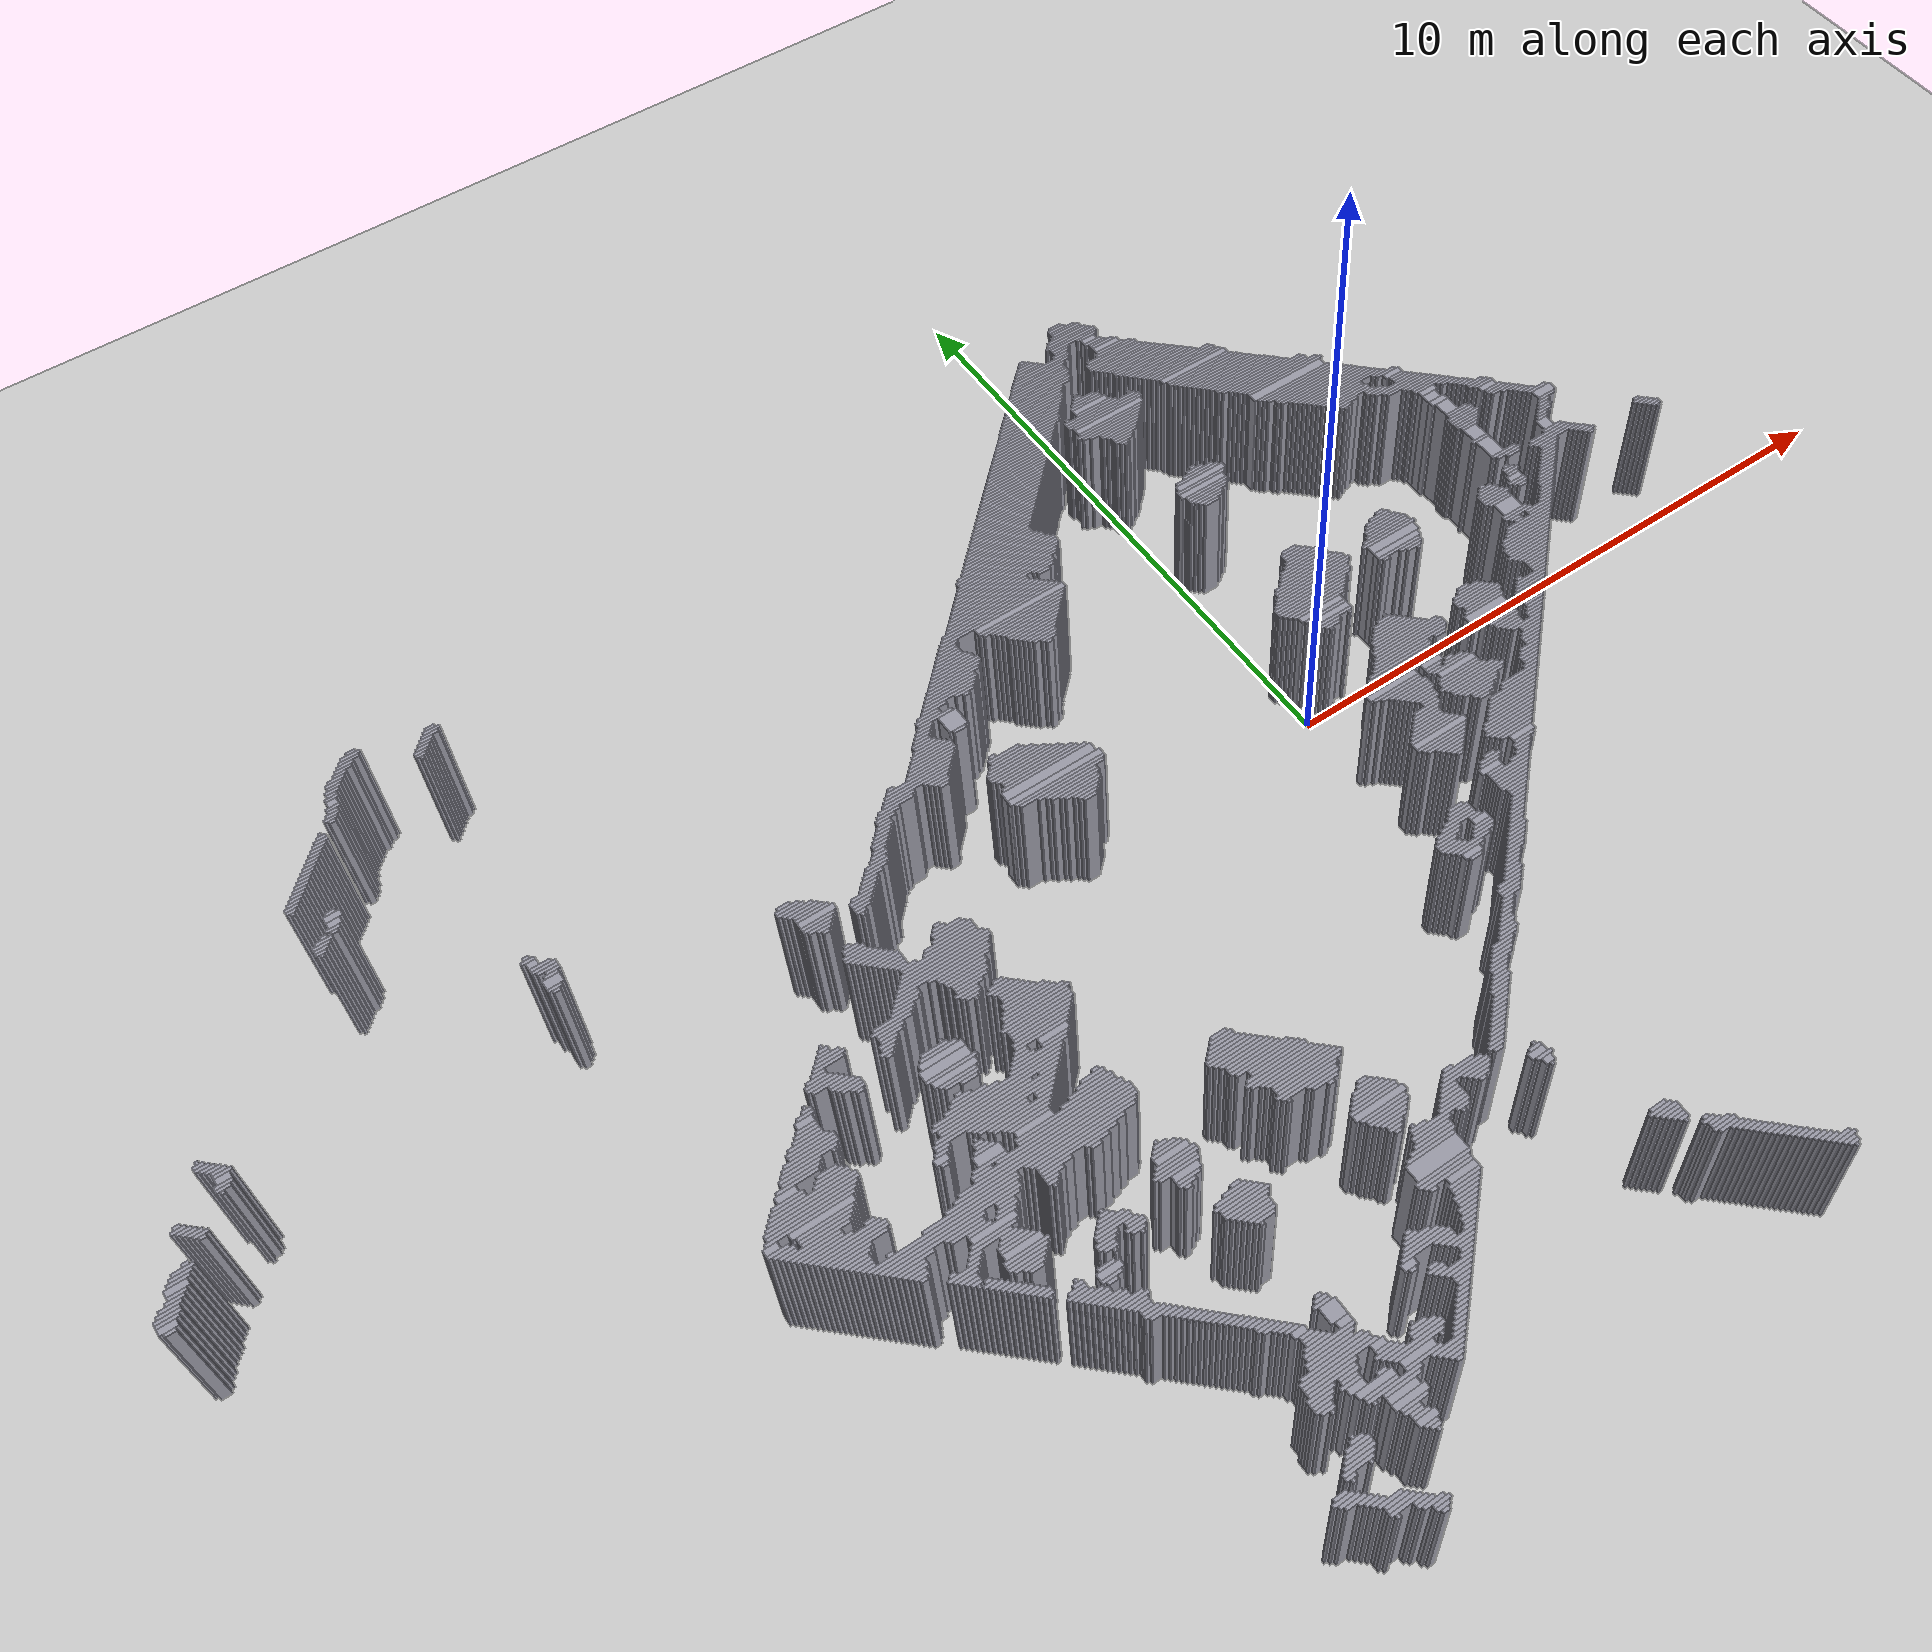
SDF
<?xml version="1.0"?>
<sdf version="1.8">
  <world name="visn2_room">
    <physics type="ode">
      <real_time_update_rate>1000.0</real_time_update_rate>
      <max_step_size>0.001</max_step_size>
      <real_time_factor>1</real_time_factor>
    </physics>
    <plugin filename="gz-sim-physics-system" name="gz::sim::systems::Physics"/>
    <plugin filename="gz-sim-user-commands-system" name="gz::sim::systems::UserCommands"/>
    <plugin filename="gz-sim-scene-broadcaster-system" name="gz::sim::systems::SceneBroadcaster"/>
    <plugin filename="gz-sim-sensors-system" name="gz::sim::systems::Sensors">
      <render_engine>ogre2</render_engine>
    </plugin>
    <plugin filename="gz-sim-imu-system" name="gz::sim::systems::Imu"/>

    <light type="directional" name="sun">
      <cast_shadows>true</cast_shadows>
      <pose>0 0 10 0 0 0</pose>
      <diffuse>1 1 1 1</diffuse>
      <specular>0.4 0.4 0.4 1</specular>
      <attenuation><range>1000</range><constant>0.9</constant><linear>0.01</linear><quadratic>0.001</quadratic></attenuation>
      <!-- near-vertical so wall shadows don't blanket the room interior in
           the overhead camera view -->
      <direction>-0.1 0.05 -0.95</direction>
    </light>

    <model name="ground_plane">
      <static>true</static>
      <link name="link">
        <collision name="collision">
          <geometry><plane><normal>0 0 1</normal><size>200 200</size></plane></geometry>
        </collision>
        <visual name="visual">
          <geometry><plane><normal>0 0 1</normal><size>200 200</size></plane></geometry>
          <material><ambient>0.8 0.8 0.8 1</ambient><diffuse>0.8 0.8 0.8 1</diffuse></material>
        </visual>
      </link>
    </model>

    <model name="visn2_room_walls">
      <static>true</static>
      <link name="walls">
        <collision name="c0">
          <pose>-6.344 -10.474 1.000 0 0 0</pose>
          <geometry><box><size>0.100 0.050 2.000</size></box></geometry>
        </collision>
        <visual name="v0">
          <pose>-6.344 -10.474 1.000 0 0 0</pose>
          <geometry><box><size>0.100 0.050 2.000</size></box></geometry>
          <material><ambient>0.5 0.5 0.55 1</ambient><diffuse>0.6 0.6 0.65 1</diffuse></material>
        </visual>
        <collision name="c1">
          <pose>-6.344 -10.424 1.000 0 0 0</pose>
          <geometry><box><size>0.200 0.050 2.000</size></box></geometry>
        </collision>
        <visual name="v1">
          <pose>-6.344 -10.424 1.000 0 0 0</pose>
          <geometry><box><size>0.200 0.050 2.000</size></box></geometry>
          <material><ambient>0.5 0.5 0.55 1</ambient><diffuse>0.6 0.6 0.65 1</diffuse></material>
        </visual>
        <collision name="c2">
          <pose>-6.319 -10.374 1.000 0 0 0</pose>
          <geometry><box><size>0.250 0.050 2.000</size></box></geometry>
        </collision>
        <visual name="v2">
          <pose>-6.319 -10.374 1.000 0 0 0</pose>
          <geometry><box><size>0.250 0.050 2.000</size></box></geometry>
          <material><ambient>0.5 0.5 0.55 1</ambient><diffuse>0.6 0.6 0.65 1</diffuse></material>
        </visual>
        <collision name="c3">
          <pose>-6.394 -10.324 1.000 0 0 0</pose>
          <geometry><box><size>0.300 0.050 2.000</size></box></geometry>
        </collision>
        <visual name="v3">
          <pose>-6.394 -10.324 1.000 0 0 0</pose>
          <geometry><box><size>0.300 0.050 2.000</size></box></geometry>
          <material><ambient>0.5 0.5 0.55 1</ambient><diffuse>0.6 0.6 0.65 1</diffuse></material>
        </visual>
        <collision name="c4">
          <pose>-6.469 -10.274 1.000 0 0 0</pose>
          <geometry><box><size>0.250 0.050 2.000</size></box></geometry>
        </collision>
        <visual name="v4">
          <pose>-6.469 -10.274 1.000 0 0 0</pose>
          <geometry><box><size>0.250 0.050 2.000</size></box></geometry>
          <material><ambient>0.5 0.5 0.55 1</ambient><diffuse>0.6 0.6 0.65 1</diffuse></material>
        </visual>
        <collision name="c5">
          <pose>-6.819 -10.224 1.000 0 0 0</pose>
          <geometry><box><size>0.050 0.050 2.000</size></box></geometry>
        </collision>
        <visual name="v5">
          <pose>-6.819 -10.224 1.000 0 0 0</pose>
          <geometry><box><size>0.050 0.050 2.000</size></box></geometry>
          <material><ambient>0.5 0.5 0.55 1</ambient><diffuse>0.6 0.6 0.65 1</diffuse></material>
        </visual>
        <collision name="c6">
          <pose>-6.494 -10.224 1.000 0 0 0</pose>
          <geometry><box><size>0.200 0.050 2.000</size></box></geometry>
        </collision>
        <visual name="v6">
          <pose>-6.494 -10.224 1.000 0 0 0</pose>
          <geometry><box><size>0.200 0.050 2.000</size></box></geometry>
          <material><ambient>0.5 0.5 0.55 1</ambient><diffuse>0.6 0.6 0.65 1</diffuse></material>
        </visual>
        <collision name="c7">
          <pose>-6.669 -10.174 1.000 0 0 0</pose>
          <geometry><box><size>0.450 0.050 2.000</size></box></geometry>
        </collision>
        <visual name="v7">
          <pose>-6.669 -10.174 1.000 0 0 0</pose>
          <geometry><box><size>0.450 0.050 2.000</size></box></geometry>
          <material><ambient>0.5 0.5 0.55 1</ambient><diffuse>0.6 0.6 0.65 1</diffuse></material>
        </visual>
        <collision name="c8">
          <pose>-6.694 -10.124 1.000 0 0 0</pose>
          <geometry><box><size>0.400 0.050 2.000</size></box></geometry>
        </collision>
        <visual name="v8">
          <pose>-6.694 -10.124 1.000 0 0 0</pose>
          <geometry><box><size>0.400 0.050 2.000</size></box></geometry>
          <material><ambient>0.5 0.5 0.55 1</ambient><diffuse>0.6 0.6 0.65 1</diffuse></material>
        </visual>
        <collision name="c9">
          <pose>-6.719 -10.074 1.000 0 0 0</pose>
          <geometry><box><size>0.350 0.050 2.000</size></box></geometry>
        </collision>
        <visual name="v9">
          <pose>-6.719 -10.074 1.000 0 0 0</pose>
          <geometry><box><size>0.350 0.050 2.000</size></box></geometry>
          <material><ambient>0.5 0.5 0.55 1</ambient><diffuse>0.6 0.6 0.65 1</diffuse></material>
        </visual>
        <collision name="c10">
          <pose>-6.769 -10.024 1.000 0 0 0</pose>
          <geometry><box><size>0.350 0.050 2.000</size></box></geometry>
        </collision>
        <visual name="v10">
          <pose>-6.769 -10.024 1.000 0 0 0</pose>
          <geometry><box><size>0.350 0.050 2.000</size></box></geometry>
          <material><ambient>0.5 0.5 0.55 1</ambient><diffuse>0.6 0.6 0.65 1</diffuse></material>
        </visual>
        <collision name="c11">
          <pose>-6.894 -9.974 1.000 0 0 0</pose>
          <geometry><box><size>0.200 0.050 2.000</size></box></geometry>
        </collision>
        <visual name="v11">
          <pose>-6.894 -9.974 1.000 0 0 0</pose>
          <geometry><box><size>0.200 0.050 2.000</size></box></geometry>
          <material><ambient>0.5 0.5 0.55 1</ambient><diffuse>0.6 0.6 0.65 1</diffuse></material>
        </visual>
        <collision name="c12">
          <pose>0.531 -9.974 1.000 0 0 0</pose>
          <geometry><box><size>0.050 0.050 2.000</size></box></geometry>
        </collision>
        <visual name="v12">
          <pose>0.531 -9.974 1.000 0 0 0</pose>
          <geometry><box><size>0.050 0.050 2.000</size></box></geometry>
          <material><ambient>0.5 0.5 0.55 1</ambient><diffuse>0.6 0.6 0.65 1</diffuse></material>
        </visual>
        <collision name="c13">
          <pose>-6.944 -9.924 1.000 0 0 0</pose>
          <geometry><box><size>0.200 0.050 2.000</size></box></geometry>
        </collision>
        <visual name="v13">
          <pose>-6.944 -9.924 1.000 0 0 0</pose>
          <geometry><box><size>0.200 0.050 2.000</size></box></geometry>
          <material><ambient>0.5 0.5 0.55 1</ambient><diffuse>0.6 0.6 0.65 1</diffuse></material>
        </visual>
        <collision name="c14">
          <pose>0.531 -9.924 1.000 0 0 0</pose>
          <geometry><box><size>0.150 0.050 2.000</size></box></geometry>
        </collision>
        <visual name="v14">
          <pose>0.531 -9.924 1.000 0 0 0</pose>
          <geometry><box><size>0.150 0.050 2.000</size></box></geometry>
          <material><ambient>0.5 0.5 0.55 1</ambient><diffuse>0.6 0.6 0.65 1</diffuse></material>
        </visual>
        <collision name="c15">
          <pose>0.506 -9.874 1.000 0 0 0</pose>
          <geometry><box><size>0.200 0.050 2.000</size></box></geometry>
        </collision>
        <visual name="v15">
          <pose>0.506 -9.874 1.000 0 0 0</pose>
          <geometry><box><size>0.200 0.050 2.000</size></box></geometry>
          <material><ambient>0.5 0.5 0.55 1</ambient><diffuse>0.6 0.6 0.65 1</diffuse></material>
        </visual>
        <collision name="c16">
          <pose>-6.994 -9.874 1.000 0 0 0</pose>
          <geometry><box><size>0.200 0.050 2.000</size></box></geometry>
        </collision>
        <visual name="v16">
          <pose>-6.994 -9.874 1.000 0 0 0</pose>
          <geometry><box><size>0.200 0.050 2.000</size></box></geometry>
          <material><ambient>0.5 0.5 0.55 1</ambient><diffuse>0.6 0.6 0.65 1</diffuse></material>
        </visual>
        <collision name="c17">
          <pose>0.506 -9.824 1.000 0 0 0</pose>
          <geometry><box><size>0.300 0.050 2.000</size></box></geometry>
        </collision>
        <visual name="v17">
          <pose>0.506 -9.824 1.000 0 0 0</pose>
          <geometry><box><size>0.300 0.050 2.000</size></box></geometry>
          <material><ambient>0.5 0.5 0.55 1</ambient><diffuse>0.6 0.6 0.65 1</diffuse></material>
        </visual>
        <collision name="c18">
          <pose>-7.094 -9.824 1.000 0 0 0</pose>
          <geometry><box><size>0.300 0.050 2.000</size></box></geometry>
        </collision>
        <visual name="v18">
          <pose>-7.094 -9.824 1.000 0 0 0</pose>
          <geometry><box><size>0.300 0.050 2.000</size></box></geometry>
          <material><ambient>0.5 0.5 0.55 1</ambient><diffuse>0.6 0.6 0.65 1</diffuse></material>
        </visual>
        <collision name="c19">
          <pose>0.456 -9.774 1.000 0 0 0</pose>
          <geometry><box><size>0.300 0.050 2.000</size></box></geometry>
        </collision>
        <visual name="v19">
          <pose>0.456 -9.774 1.000 0 0 0</pose>
          <geometry><box><size>0.300 0.050 2.000</size></box></geometry>
          <material><ambient>0.5 0.5 0.55 1</ambient><diffuse>0.6 0.6 0.65 1</diffuse></material>
        </visual>
        <collision name="c20">
          <pose>-7.144 -9.774 1.000 0 0 0</pose>
          <geometry><box><size>0.300 0.050 2.000</size></box></geometry>
        </collision>
        <visual name="v20">
          <pose>-7.144 -9.774 1.000 0 0 0</pose>
          <geometry><box><size>0.300 0.050 2.000</size></box></geometry>
          <material><ambient>0.5 0.5 0.55 1</ambient><diffuse>0.6 0.6 0.65 1</diffuse></material>
        </visual>
        <collision name="c21">
          <pose>-7.194 -9.724 1.000 0 0 0</pose>
          <geometry><box><size>0.300 0.050 2.000</size></box></geometry>
        </collision>
        <visual name="v21">
          <pose>-7.194 -9.724 1.000 0 0 0</pose>
          <geometry><box><size>0.300 0.050 2.000</size></box></geometry>
          <material><ambient>0.5 0.5 0.55 1</ambient><diffuse>0.6 0.6 0.65 1</diffuse></material>
        </visual>
        <collision name="c22">
          <pose>-5.819 -9.724 1.000 0 0 0</pose>
          <geometry><box><size>0.050 0.050 2.000</size></box></geometry>
        </collision>
        <visual name="v22">
          <pose>-5.819 -9.724 1.000 0 0 0</pose>
          <geometry><box><size>0.050 0.050 2.000</size></box></geometry>
          <material><ambient>0.5 0.5 0.55 1</ambient><diffuse>0.6 0.6 0.65 1</diffuse></material>
        </visual>
        <collision name="c23">
          <pose>0.356 -9.724 1.000 0 0 0</pose>
          <geometry><box><size>0.200 0.050 2.000</size></box></geometry>
        </collision>
        <visual name="v23">
          <pose>0.356 -9.724 1.000 0 0 0</pose>
          <geometry><box><size>0.200 0.050 2.000</size></box></geometry>
          <material><ambient>0.5 0.5 0.55 1</ambient><diffuse>0.6 0.6 0.65 1</diffuse></material>
        </visual>
        <collision name="c24">
          <pose>0.306 -9.674 1.000 0 0 0</pose>
          <geometry><box><size>0.200 0.050 2.000</size></box></geometry>
        </collision>
        <visual name="v24">
          <pose>0.306 -9.674 1.000 0 0 0</pose>
          <geometry><box><size>0.200 0.050 2.000</size></box></geometry>
          <material><ambient>0.5 0.5 0.55 1</ambient><diffuse>0.6 0.6 0.65 1</diffuse></material>
        </visual>
        <collision name="c25">
          <pose>-7.194 -9.674 1.000 0 0 0</pose>
          <geometry><box><size>0.200 0.050 2.000</size></box></geometry>
        </collision>
        <visual name="v25">
          <pose>-7.194 -9.674 1.000 0 0 0</pose>
          <geometry><box><size>0.200 0.050 2.000</size></box></geometry>
          <material><ambient>0.5 0.5 0.55 1</ambient><diffuse>0.6 0.6 0.65 1</diffuse></material>
        </visual>
        <collision name="c26">
          <pose>-5.819 -9.674 1.000 0 0 0</pose>
          <geometry><box><size>0.150 0.050 2.000</size></box></geometry>
        </collision>
        <visual name="v26">
          <pose>-5.819 -9.674 1.000 0 0 0</pose>
          <geometry><box><size>0.150 0.050 2.000</size></box></geometry>
          <material><ambient>0.5 0.5 0.55 1</ambient><diffuse>0.6 0.6 0.65 1</diffuse></material>
        </visual>
        <collision name="c27">
          <pose>0.256 -9.624 1.000 0 0 0</pose>
          <geometry><box><size>0.200 0.050 2.000</size></box></geometry>
        </collision>
        <visual name="v27">
          <pose>0.256 -9.624 1.000 0 0 0</pose>
          <geometry><box><size>0.200 0.050 2.000</size></box></geometry>
          <material><ambient>0.5 0.5 0.55 1</ambient><diffuse>0.6 0.6 0.65 1</diffuse></material>
        </visual>
        <collision name="c28">
          <pose>-6.969 -9.624 1.000 0 0 0</pose>
          <geometry><box><size>0.050 0.050 2.000</size></box></geometry>
        </collision>
        <visual name="v28">
          <pose>-6.969 -9.624 1.000 0 0 0</pose>
          <geometry><box><size>0.050 0.050 2.000</size></box></geometry>
          <material><ambient>0.5 0.5 0.55 1</ambient><diffuse>0.6 0.6 0.65 1</diffuse></material>
        </visual>
        <collision name="c29">
          <pose>-5.844 -9.624 1.000 0 0 0</pose>
          <geometry><box><size>0.200 0.050 2.000</size></box></geometry>
        </collision>
        <visual name="v29">
          <pose>-5.844 -9.624 1.000 0 0 0</pose>
          <geometry><box><size>0.200 0.050 2.000</size></box></geometry>
          <material><ambient>0.5 0.5 0.55 1</ambient><diffuse>0.6 0.6 0.65 1</diffuse></material>
        </visual>
        <collision name="c30">
          <pose>-6.669 -9.574 1.000 0 0 0</pose>
          <geometry><box><size>0.050 0.050 2.000</size></box></geometry>
        </collision>
        <visual name="v30">
          <pose>-6.669 -9.574 1.000 0 0 0</pose>
          <geometry><box><size>0.050 0.050 2.000</size></box></geometry>
          <material><ambient>0.5 0.5 0.55 1</ambient><diffuse>0.6 0.6 0.65 1</diffuse></material>
        </visual>
        <collision name="c31">
          <pose>0.206 -9.574 1.000 0 0 0</pose>
          <geometry><box><size>0.200 0.050 2.000</size></box></geometry>
        </collision>
        <visual name="v31">
          <pose>0.206 -9.574 1.000 0 0 0</pose>
          <geometry><box><size>0.200 0.050 2.000</size></box></geometry>
          <material><ambient>0.5 0.5 0.55 1</ambient><diffuse>0.6 0.6 0.65 1</diffuse></material>
        </visual>
        <collision name="c32">
          <pose>-6.969 -9.574 1.000 0 0 0</pose>
          <geometry><box><size>0.150 0.050 2.000</size></box></geometry>
        </collision>
        <visual name="v32">
          <pose>-6.969 -9.574 1.000 0 0 0</pose>
          <geometry><box><size>0.150 0.050 2.000</size></box></geometry>
          <material><ambient>0.5 0.5 0.55 1</ambient><diffuse>0.6 0.6 0.65 1</diffuse></material>
        </visual>
        <collision name="c33">
          <pose>-5.844 -9.549 1.000 0 0 0</pose>
          <geometry><box><size>0.300 0.100 2.000</size></box></geometry>
        </collision>
        <visual name="v33">
          <pose>-5.844 -9.549 1.000 0 0 0</pose>
          <geometry><box><size>0.300 0.100 2.000</size></box></geometry>
          <material><ambient>0.5 0.5 0.55 1</ambient><diffuse>0.6 0.6 0.65 1</diffuse></material>
        </visual>
        <collision name="c34">
          <pose>0.156 -9.524 1.000 0 0 0</pose>
          <geometry><box><size>0.200 0.050 2.000</size></box></geometry>
        </collision>
        <visual name="v34">
          <pose>0.156 -9.524 1.000 0 0 0</pose>
          <geometry><box><size>0.200 0.050 2.000</size></box></geometry>
          <material><ambient>0.5 0.5 0.55 1</ambient><diffuse>0.6 0.6 0.65 1</diffuse></material>
        </visual>
        <collision name="c35">
          <pose>-6.819 -9.524 1.000 0 0 0</pose>
          <geometry><box><size>0.450 0.050 2.000</size></box></geometry>
        </collision>
        <visual name="v35">
          <pose>-6.819 -9.524 1.000 0 0 0</pose>
          <geometry><box><size>0.450 0.050 2.000</size></box></geometry>
          <material><ambient>0.5 0.5 0.55 1</ambient><diffuse>0.6 0.6 0.65 1</diffuse></material>
        </visual>
        <collision name="c36">
          <pose>0.106 -9.474 1.000 0 0 0</pose>
          <geometry><box><size>0.200 0.050 2.000</size></box></geometry>
        </collision>
        <visual name="v36">
          <pose>0.106 -9.474 1.000 0 0 0</pose>
          <geometry><box><size>0.200 0.050 2.000</size></box></geometry>
          <material><ambient>0.5 0.5 0.55 1</ambient><diffuse>0.6 0.6 0.65 1</diffuse></material>
        </visual>
        <collision name="c37">
          <pose>-6.769 -9.474 1.000 0 0 0</pose>
          <geometry><box><size>0.450 0.050 2.000</size></box></geometry>
        </collision>
        <visual name="v37">
          <pose>-6.769 -9.474 1.000 0 0 0</pose>
          <geometry><box><size>0.450 0.050 2.000</size></box></geometry>
          <material><ambient>0.5 0.5 0.55 1</ambient><diffuse>0.6 0.6 0.65 1</diffuse></material>
        </visual>
        <collision name="c38">
          <pose>-5.869 -9.474 1.000 0 0 0</pose>
          <geometry><box><size>0.250 0.050 2.000</size></box></geometry>
        </collision>
        <visual name="v38">
          <pose>-5.869 -9.474 1.000 0 0 0</pose>
          <geometry><box><size>0.250 0.050 2.000</size></box></geometry>
          <material><ambient>0.5 0.5 0.55 1</ambient><diffuse>0.6 0.6 0.65 1</diffuse></material>
        </visual>
        <collision name="c39">
          <pose>0.056 -9.424 1.000 0 0 0</pose>
          <geometry><box><size>0.200 0.050 2.000</size></box></geometry>
        </collision>
        <visual name="v39">
          <pose>0.056 -9.424 1.000 0 0 0</pose>
          <geometry><box><size>0.200 0.050 2.000</size></box></geometry>
          <material><ambient>0.5 0.5 0.55 1</ambient><diffuse>0.6 0.6 0.65 1</diffuse></material>
        </visual>
        <collision name="c40">
          <pose>-5.894 -9.424 1.000 0 0 0</pose>
          <geometry><box><size>0.200 0.050 2.000</size></box></geometry>
        </collision>
        <visual name="v40">
          <pose>-5.894 -9.424 1.000 0 0 0</pose>
          <geometry><box><size>0.200 0.050 2.000</size></box></geometry>
          <material><ambient>0.5 0.5 0.55 1</ambient><diffuse>0.6 0.6 0.65 1</diffuse></material>
        </visual>
        <collision name="c41">
          <pose>-6.719 -9.424 1.000 0 0 0</pose>
          <geometry><box><size>0.450 0.050 2.000</size></box></geometry>
        </collision>
        <visual name="v41">
          <pose>-6.719 -9.424 1.000 0 0 0</pose>
          <geometry><box><size>0.450 0.050 2.000</size></box></geometry>
          <material><ambient>0.5 0.5 0.55 1</ambient><diffuse>0.6 0.6 0.65 1</diffuse></material>
        </visual>
        <collision name="c42">
          <pose>-5.919 -9.374 1.000 0 0 0</pose>
          <geometry><box><size>0.250 0.050 2.000</size></box></geometry>
        </collision>
        <visual name="v42">
          <pose>-5.919 -9.374 1.000 0 0 0</pose>
          <geometry><box><size>0.250 0.050 2.000</size></box></geometry>
          <material><ambient>0.5 0.5 0.55 1</ambient><diffuse>0.6 0.6 0.65 1</diffuse></material>
        </visual>
        <collision name="c43">
          <pose>-6.694 -9.374 1.000 0 0 0</pose>
          <geometry><box><size>0.400 0.050 2.000</size></box></geometry>
        </collision>
        <visual name="v43">
          <pose>-6.694 -9.374 1.000 0 0 0</pose>
          <geometry><box><size>0.400 0.050 2.000</size></box></geometry>
          <material><ambient>0.5 0.5 0.55 1</ambient><diffuse>0.6 0.6 0.65 1</diffuse></material>
        </visual>
        <collision name="c44">
          <pose>0.006 -9.374 1.000 0 0 0</pose>
          <geometry><box><size>0.200 0.050 2.000</size></box></geometry>
        </collision>
        <visual name="v44">
          <pose>0.006 -9.374 1.000 0 0 0</pose>
          <geometry><box><size>0.200 0.050 2.000</size></box></geometry>
          <material><ambient>0.5 0.5 0.55 1</ambient><diffuse>0.6 0.6 0.65 1</diffuse></material>
        </visual>
        <collision name="c45">
          <pose>-0.044 -9.324 1.000 0 0 0</pose>
          <geometry><box><size>0.200 0.050 2.000</size></box></geometry>
        </collision>
        <visual name="v45">
          <pose>-0.044 -9.324 1.000 0 0 0</pose>
          <geometry><box><size>0.200 0.050 2.000</size></box></geometry>
          <material><ambient>0.5 0.5 0.55 1</ambient><diffuse>0.6 0.6 0.65 1</diffuse></material>
        </visual>
        <collision name="c46">
          <pose>-5.844 -9.324 1.000 0 0 0</pose>
          <geometry><box><size>0.400 0.050 2.000</size></box></geometry>
        </collision>
        <visual name="v46">
          <pose>-5.844 -9.324 1.000 0 0 0</pose>
          <geometry><box><size>0.400 0.050 2.000</size></box></geometry>
          <material><ambient>0.5 0.5 0.55 1</ambient><diffuse>0.6 0.6 0.65 1</diffuse></material>
        </visual>
        <collision name="c47">
          <pose>-6.669 -9.324 1.000 0 0 0</pose>
          <geometry><box><size>0.350 0.050 2.000</size></box></geometry>
        </collision>
        <visual name="v47">
          <pose>-6.669 -9.324 1.000 0 0 0</pose>
          <geometry><box><size>0.350 0.050 2.000</size></box></geometry>
          <material><ambient>0.5 0.5 0.55 1</ambient><diffuse>0.6 0.6 0.65 1</diffuse></material>
        </visual>
        <collision name="c48">
          <pose>-6.644 -9.274 1.000 0 0 0</pose>
          <geometry><box><size>0.200 0.050 2.000</size></box></geometry>
        </collision>
        <visual name="v48">
          <pose>-6.644 -9.274 1.000 0 0 0</pose>
          <geometry><box><size>0.200 0.050 2.000</size></box></geometry>
          <material><ambient>0.5 0.5 0.55 1</ambient><diffuse>0.6 0.6 0.65 1</diffuse></material>
        </visual>
        <collision name="c49">
          <pose>-0.094 -9.274 1.000 0 0 0</pose>
          <geometry><box><size>0.200 0.050 2.000</size></box></geometry>
        </collision>
        <visual name="v49">
          <pose>-0.094 -9.274 1.000 0 0 0</pose>
          <geometry><box><size>0.200 0.050 2.000</size></box></geometry>
          <material><ambient>0.5 0.5 0.55 1</ambient><diffuse>0.6 0.6 0.65 1</diffuse></material>
        </visual>
        <collision name="c50">
          <pose>-5.844 -9.249 1.000 0 0 0</pose>
          <geometry><box><size>0.500 0.100 2.000</size></box></geometry>
        </collision>
        <visual name="v50">
          <pose>-5.844 -9.249 1.000 0 0 0</pose>
          <geometry><box><size>0.500 0.100 2.000</size></box></geometry>
          <material><ambient>0.5 0.5 0.55 1</ambient><diffuse>0.6 0.6 0.65 1</diffuse></material>
        </visual>
        <collision name="c51">
          <pose>-0.144 -9.224 1.000 0 0 0</pose>
          <geometry><box><size>0.200 0.050 2.000</size></box></geometry>
        </collision>
        <visual name="v51">
          <pose>-0.144 -9.224 1.000 0 0 0</pose>
          <geometry><box><size>0.200 0.050 2.000</size></box></geometry>
          <material><ambient>0.5 0.5 0.55 1</ambient><diffuse>0.6 0.6 0.65 1</diffuse></material>
        </visual>
        <collision name="c52">
          <pose>-6.669 -9.224 1.000 0 0 0</pose>
          <geometry><box><size>0.050 0.050 2.000</size></box></geometry>
        </collision>
        <visual name="v52">
          <pose>-6.669 -9.224 1.000 0 0 0</pose>
          <geometry><box><size>0.050 0.050 2.000</size></box></geometry>
          <material><ambient>0.5 0.5 0.55 1</ambient><diffuse>0.6 0.6 0.65 1</diffuse></material>
        </visual>
        <collision name="c53">
          <pose>-5.094 -9.224 1.000 0 0 0</pose>
          <geometry><box><size>0.100 0.050 2.000</size></box></geometry>
        </collision>
        <visual name="v53">
          <pose>-5.094 -9.224 1.000 0 0 0</pose>
          <geometry><box><size>0.100 0.050 2.000</size></box></geometry>
          <material><ambient>0.5 0.5 0.55 1</ambient><diffuse>0.6 0.6 0.65 1</diffuse></material>
        </visual>
        <collision name="c54">
          <pose>-5.094 -9.174 1.000 0 0 0</pose>
          <geometry><box><size>0.200 0.050 2.000</size></box></geometry>
        </collision>
        <visual name="v54">
          <pose>-5.094 -9.174 1.000 0 0 0</pose>
          <geometry><box><size>0.200 0.050 2.000</size></box></geometry>
          <material><ambient>0.5 0.5 0.55 1</ambient><diffuse>0.6 0.6 0.65 1</diffuse></material>
        </visual>
        <collision name="c55">
          <pose>-0.194 -9.174 1.000 0 0 0</pose>
          <geometry><box><size>0.200 0.050 2.000</size></box></geometry>
        </collision>
        <visual name="v55">
          <pose>-0.194 -9.174 1.000 0 0 0</pose>
          <geometry><box><size>0.200 0.050 2.000</size></box></geometry>
          <material><ambient>0.5 0.5 0.55 1</ambient><diffuse>0.6 0.6 0.65 1</diffuse></material>
        </visual>
        <collision name="c56">
          <pose>-5.869 -9.149 1.000 0 0 0</pose>
          <geometry><box><size>0.450 0.100 2.000</size></box></geometry>
        </collision>
        <visual name="v56">
          <pose>-5.869 -9.149 1.000 0 0 0</pose>
          <geometry><box><size>0.450 0.100 2.000</size></box></geometry>
          <material><ambient>0.5 0.5 0.55 1</ambient><diffuse>0.6 0.6 0.65 1</diffuse></material>
        </visual>
        <collision name="c57">
          <pose>-0.244 -9.124 1.000 0 0 0</pose>
          <geometry><box><size>0.200 0.050 2.000</size></box></geometry>
        </collision>
        <visual name="v57">
          <pose>-0.244 -9.124 1.000 0 0 0</pose>
          <geometry><box><size>0.200 0.050 2.000</size></box></geometry>
          <material><ambient>0.5 0.5 0.55 1</ambient><diffuse>0.6 0.6 0.65 1</diffuse></material>
        </visual>
        <collision name="c58">
          <pose>-5.094 -9.124 1.000 0 0 0</pose>
          <geometry><box><size>0.300 0.050 2.000</size></box></geometry>
        </collision>
        <visual name="v58">
          <pose>-5.094 -9.124 1.000 0 0 0</pose>
          <geometry><box><size>0.300 0.050 2.000</size></box></geometry>
          <material><ambient>0.5 0.5 0.55 1</ambient><diffuse>0.6 0.6 0.65 1</diffuse></material>
        </visual>
        <collision name="c59">
          <pose>-6.219 -9.074 1.000 0 0 0</pose>
          <geometry><box><size>0.050 0.050 2.000</size></box></geometry>
        </collision>
        <visual name="v59">
          <pose>-6.219 -9.074 1.000 0 0 0</pose>
          <geometry><box><size>0.050 0.050 2.000</size></box></geometry>
          <material><ambient>0.5 0.5 0.55 1</ambient><diffuse>0.6 0.6 0.65 1</diffuse></material>
        </visual>
        <collision name="c60">
          <pose>-5.819 -9.074 1.000 0 0 0</pose>
          <geometry><box><size>0.550 0.050 2.000</size></box></geometry>
        </collision>
        <visual name="v60">
          <pose>-5.819 -9.074 1.000 0 0 0</pose>
          <geometry><box><size>0.550 0.050 2.000</size></box></geometry>
          <material><ambient>0.5 0.5 0.55 1</ambient><diffuse>0.6 0.6 0.65 1</diffuse></material>
        </visual>
        <collision name="c61">
          <pose>-0.294 -9.074 1.000 0 0 0</pose>
          <geometry><box><size>0.200 0.050 2.000</size></box></geometry>
        </collision>
        <visual name="v61">
          <pose>-0.294 -9.074 1.000 0 0 0</pose>
          <geometry><box><size>0.200 0.050 2.000</size></box></geometry>
          <material><ambient>0.5 0.5 0.55 1</ambient><diffuse>0.6 0.6 0.65 1</diffuse></material>
        </visual>
        <collision name="c62">
          <pose>-5.094 -9.074 1.000 0 0 0</pose>
          <geometry><box><size>0.400 0.050 2.000</size></box></geometry>
        </collision>
        <visual name="v62">
          <pose>-5.094 -9.074 1.000 0 0 0</pose>
          <geometry><box><size>0.400 0.050 2.000</size></box></geometry>
          <material><ambient>0.5 0.5 0.55 1</ambient><diffuse>0.6 0.6 0.65 1</diffuse></material>
        </visual>
        <collision name="c63">
          <pose>-0.344 -9.024 1.000 0 0 0</pose>
          <geometry><box><size>0.200 0.050 2.000</size></box></geometry>
        </collision>
        <visual name="v63">
          <pose>-0.344 -9.024 1.000 0 0 0</pose>
          <geometry><box><size>0.200 0.050 2.000</size></box></geometry>
          <material><ambient>0.5 0.5 0.55 1</ambient><diffuse>0.6 0.6 0.65 1</diffuse></material>
        </visual>
        <collision name="c64">
          <pose>-5.894 -9.024 1.000 0 0 0</pose>
          <geometry><box><size>0.800 0.050 2.000</size></box></geometry>
        </collision>
        <visual name="v64">
          <pose>-5.894 -9.024 1.000 0 0 0</pose>
          <geometry><box><size>0.800 0.050 2.000</size></box></geometry>
          <material><ambient>0.5 0.5 0.55 1</ambient><diffuse>0.6 0.6 0.65 1</diffuse></material>
        </visual>
        <collision name="c65">
          <pose>-5.094 -9.024 1.000 0 0 0</pose>
          <geometry><box><size>0.500 0.050 2.000</size></box></geometry>
        </collision>
        <visual name="v65">
          <pose>-5.094 -9.024 1.000 0 0 0</pose>
          <geometry><box><size>0.500 0.050 2.000</size></box></geometry>
          <material><ambient>0.5 0.5 0.55 1</ambient><diffuse>0.6 0.6 0.65 1</diffuse></material>
        </visual>
        <collision name="c66">
          <pose>-6.044 -8.974 1.000 0 0 0</pose>
          <geometry><box><size>0.500 0.050 2.000</size></box></geometry>
        </collision>
        <visual name="v66">
          <pose>-6.044 -8.974 1.000 0 0 0</pose>
          <geometry><box><size>0.500 0.050 2.000</size></box></geometry>
          <material><ambient>0.5 0.5 0.55 1</ambient><diffuse>0.6 0.6 0.65 1</diffuse></material>
        </visual>
        <collision name="c67">
          <pose>-4.894 -8.974 1.000 0 0 0</pose>
          <geometry><box><size>0.200 0.050 2.000</size></box></geometry>
        </collision>
        <visual name="v67">
          <pose>-4.894 -8.974 1.000 0 0 0</pose>
          <geometry><box><size>0.200 0.050 2.000</size></box></geometry>
          <material><ambient>0.5 0.5 0.55 1</ambient><diffuse>0.6 0.6 0.65 1</diffuse></material>
        </visual>
        <collision name="c68">
          <pose>-0.394 -8.974 1.000 0 0 0</pose>
          <geometry><box><size>0.200 0.050 2.000</size></box></geometry>
        </collision>
        <visual name="v68">
          <pose>-0.394 -8.974 1.000 0 0 0</pose>
          <geometry><box><size>0.200 0.050 2.000</size></box></geometry>
          <material><ambient>0.5 0.5 0.55 1</ambient><diffuse>0.6 0.6 0.65 1</diffuse></material>
        </visual>
        <collision name="c69">
          <pose>-5.419 -8.974 1.000 0 0 0</pose>
          <geometry><box><size>0.550 0.050 2.000</size></box></geometry>
        </collision>
        <visual name="v69">
          <pose>-5.419 -8.974 1.000 0 0 0</pose>
          <geometry><box><size>0.550 0.050 2.000</size></box></geometry>
          <material><ambient>0.5 0.5 0.55 1</ambient><diffuse>0.6 0.6 0.65 1</diffuse></material>
        </visual>
        <collision name="c70">
          <pose>-4.844 -8.924 1.000 0 0 0</pose>
          <geometry><box><size>0.200 0.050 2.000</size></box></geometry>
        </collision>
        <visual name="v70">
          <pose>-4.844 -8.924 1.000 0 0 0</pose>
          <geometry><box><size>0.200 0.050 2.000</size></box></geometry>
          <material><ambient>0.5 0.5 0.55 1</ambient><diffuse>0.6 0.6 0.65 1</diffuse></material>
        </visual>
        <collision name="c71">
          <pose>-0.444 -8.924 1.000 0 0 0</pose>
          <geometry><box><size>0.200 0.050 2.000</size></box></geometry>
        </collision>
        <visual name="v71">
          <pose>-0.444 -8.924 1.000 0 0 0</pose>
          <geometry><box><size>0.200 0.050 2.000</size></box></geometry>
          <material><ambient>0.5 0.5 0.55 1</ambient><diffuse>0.6 0.6 0.65 1</diffuse></material>
        </visual>
        <collision name="c72">
          <pose>-5.444 -8.899 1.000 0 0 0</pose>
          <geometry><box><size>0.500 0.100 2.000</size></box></geometry>
        </collision>
        <visual name="v72">
          <pose>-5.444 -8.899 1.000 0 0 0</pose>
          <geometry><box><size>0.500 0.100 2.000</size></box></geometry>
          <material><ambient>0.5 0.5 0.55 1</ambient><diffuse>0.6 0.6 0.65 1</diffuse></material>
        </visual>
        <collision name="c73">
          <pose>-6.069 -8.899 1.000 0 0 0</pose>
          <geometry><box><size>0.550 0.100 2.000</size></box></geometry>
        </collision>
        <visual name="v73">
          <pose>-6.069 -8.899 1.000 0 0 0</pose>
          <geometry><box><size>0.550 0.100 2.000</size></box></geometry>
          <material><ambient>0.5 0.5 0.55 1</ambient><diffuse>0.6 0.6 0.65 1</diffuse></material>
        </visual>
        <collision name="c74">
          <pose>-6.669 -8.874 1.000 0 0 0</pose>
          <geometry><box><size>0.050 0.050 2.000</size></box></geometry>
        </collision>
        <visual name="v74">
          <pose>-6.669 -8.874 1.000 0 0 0</pose>
          <geometry><box><size>0.050 0.050 2.000</size></box></geometry>
          <material><ambient>0.5 0.5 0.55 1</ambient><diffuse>0.6 0.6 0.65 1</diffuse></material>
        </visual>
        <collision name="c75">
          <pose>-4.794 -8.874 1.000 0 0 0</pose>
          <geometry><box><size>0.200 0.050 2.000</size></box></geometry>
        </collision>
        <visual name="v75">
          <pose>-4.794 -8.874 1.000 0 0 0</pose>
          <geometry><box><size>0.200 0.050 2.000</size></box></geometry>
          <material><ambient>0.5 0.5 0.55 1</ambient><diffuse>0.6 0.6 0.65 1</diffuse></material>
        </visual>
        <collision name="c76">
          <pose>-5.069 -8.874 1.000 0 0 0</pose>
          <geometry><box><size>0.050 0.050 2.000</size></box></geometry>
        </collision>
        <visual name="v76">
          <pose>-5.069 -8.874 1.000 0 0 0</pose>
          <geometry><box><size>0.050 0.050 2.000</size></box></geometry>
          <material><ambient>0.5 0.5 0.55 1</ambient><diffuse>0.6 0.6 0.65 1</diffuse></material>
        </visual>
        <collision name="c77">
          <pose>-0.544 -8.874 1.000 0 0 0</pose>
          <geometry><box><size>0.300 0.050 2.000</size></box></geometry>
        </collision>
        <visual name="v77">
          <pose>-0.544 -8.874 1.000 0 0 0</pose>
          <geometry><box><size>0.300 0.050 2.000</size></box></geometry>
          <material><ambient>0.5 0.5 0.55 1</ambient><diffuse>0.6 0.6 0.65 1</diffuse></material>
        </visual>
        <collision name="c78">
          <pose>-4.744 -8.824 1.000 0 0 0</pose>
          <geometry><box><size>0.200 0.050 2.000</size></box></geometry>
        </collision>
        <visual name="v78">
          <pose>-4.744 -8.824 1.000 0 0 0</pose>
          <geometry><box><size>0.200 0.050 2.000</size></box></geometry>
          <material><ambient>0.5 0.5 0.55 1</ambient><diffuse>0.6 0.6 0.65 1</diffuse></material>
        </visual>
        <collision name="c79">
          <pose>-0.569 -8.824 1.000 0 0 0</pose>
          <geometry><box><size>0.350 0.050 2.000</size></box></geometry>
        </collision>
        <visual name="v79">
          <pose>-0.569 -8.824 1.000 0 0 0</pose>
          <geometry><box><size>0.350 0.050 2.000</size></box></geometry>
          <material><ambient>0.5 0.5 0.55 1</ambient><diffuse>0.6 0.6 0.65 1</diffuse></material>
        </visual>
        <collision name="c80">
          <pose>-5.369 -8.824 1.000 0 0 0</pose>
          <geometry><box><size>0.750 0.050 2.000</size></box></geometry>
        </collision>
        <visual name="v80">
          <pose>-5.369 -8.824 1.000 0 0 0</pose>
          <geometry><box><size>0.750 0.050 2.000</size></box></geometry>
          <material><ambient>0.5 0.5 0.55 1</ambient><diffuse>0.6 0.6 0.65 1</diffuse></material>
        </visual>
        <collision name="c81">
          <pose>-5.919 -8.824 1.000 0 0 0</pose>
          <geometry><box><size>0.150 0.050 2.000</size></box></geometry>
        </collision>
        <visual name="v81">
          <pose>-5.919 -8.824 1.000 0 0 0</pose>
          <geometry><box><size>0.150 0.050 2.000</size></box></geometry>
          <material><ambient>0.5 0.5 0.55 1</ambient><diffuse>0.6 0.6 0.65 1</diffuse></material>
        </visual>
        <collision name="c82">
          <pose>-6.694 -8.824 1.000 0 0 0</pose>
          <geometry><box><size>0.200 0.050 2.000</size></box></geometry>
        </collision>
        <visual name="v82">
          <pose>-6.694 -8.824 1.000 0 0 0</pose>
          <geometry><box><size>0.200 0.050 2.000</size></box></geometry>
          <material><ambient>0.5 0.5 0.55 1</ambient><diffuse>0.6 0.6 0.65 1</diffuse></material>
        </visual>
        <collision name="c83">
          <pose>-6.269 -8.799 1.000 0 0 0</pose>
          <geometry><box><size>0.250 0.100 2.000</size></box></geometry>
        </collision>
        <visual name="v83">
          <pose>-6.269 -8.799 1.000 0 0 0</pose>
          <geometry><box><size>0.250 0.100 2.000</size></box></geometry>
          <material><ambient>0.5 0.5 0.55 1</ambient><diffuse>0.6 0.6 0.65 1</diffuse></material>
        </visual>
        <collision name="c84">
          <pose>-6.719 -8.774 1.000 0 0 0</pose>
          <geometry><box><size>0.250 0.050 2.000</size></box></geometry>
        </collision>
        <visual name="v84">
          <pose>-6.719 -8.774 1.000 0 0 0</pose>
          <geometry><box><size>0.250 0.050 2.000</size></box></geometry>
          <material><ambient>0.5 0.5 0.55 1</ambient><diffuse>0.6 0.6 0.65 1</diffuse></material>
        </visual>
        <collision name="c85">
          <pose>-0.594 -8.774 1.000 0 0 0</pose>
          <geometry><box><size>0.300 0.050 2.000</size></box></geometry>
        </collision>
        <visual name="v85">
          <pose>-0.594 -8.774 1.000 0 0 0</pose>
          <geometry><box><size>0.300 0.050 2.000</size></box></geometry>
          <material><ambient>0.5 0.5 0.55 1</ambient><diffuse>0.6 0.6 0.65 1</diffuse></material>
        </visual>
        <collision name="c86">
          <pose>-5.369 -8.774 1.000 0 0 0</pose>
          <geometry><box><size>0.850 0.050 2.000</size></box></geometry>
        </collision>
        <visual name="v86">
          <pose>-5.369 -8.774 1.000 0 0 0</pose>
          <geometry><box><size>0.850 0.050 2.000</size></box></geometry>
          <material><ambient>0.5 0.5 0.55 1</ambient><diffuse>0.6 0.6 0.65 1</diffuse></material>
        </visual>
        <collision name="c87">
          <pose>-4.694 -8.774 1.000 0 0 0</pose>
          <geometry><box><size>0.200 0.050 2.000</size></box></geometry>
        </collision>
        <visual name="v87">
          <pose>-4.694 -8.774 1.000 0 0 0</pose>
          <geometry><box><size>0.200 0.050 2.000</size></box></geometry>
          <material><ambient>0.5 0.5 0.55 1</ambient><diffuse>0.6 0.6 0.65 1</diffuse></material>
        </visual>
        <collision name="c88">
          <pose>-5.669 -8.724 1.000 0 0 0</pose>
          <geometry><box><size>0.350 0.050 2.000</size></box></geometry>
        </collision>
        <visual name="v88">
          <pose>-5.669 -8.724 1.000 0 0 0</pose>
          <geometry><box><size>0.350 0.050 2.000</size></box></geometry>
          <material><ambient>0.5 0.5 0.55 1</ambient><diffuse>0.6 0.6 0.65 1</diffuse></material>
        </visual>
        <collision name="c89">
          <pose>-6.294 -8.724 1.000 0 0 0</pose>
          <geometry><box><size>0.300 0.050 2.000</size></box></geometry>
        </collision>
        <visual name="v89">
          <pose>-6.294 -8.724 1.000 0 0 0</pose>
          <geometry><box><size>0.300 0.050 2.000</size></box></geometry>
          <material><ambient>0.5 0.5 0.55 1</ambient><diffuse>0.6 0.6 0.65 1</diffuse></material>
        </visual>
        <collision name="c90">
          <pose>-4.644 -8.724 1.000 0 0 0</pose>
          <geometry><box><size>0.200 0.050 2.000</size></box></geometry>
        </collision>
        <visual name="v90">
          <pose>-4.644 -8.724 1.000 0 0 0</pose>
          <geometry><box><size>0.200 0.050 2.000</size></box></geometry>
          <material><ambient>0.5 0.5 0.55 1</ambient><diffuse>0.6 0.6 0.65 1</diffuse></material>
        </visual>
        <collision name="c91">
          <pose>-6.694 -8.724 1.000 0 0 0</pose>
          <geometry><box><size>0.300 0.050 2.000</size></box></geometry>
        </collision>
        <visual name="v91">
          <pose>-6.694 -8.724 1.000 0 0 0</pose>
          <geometry><box><size>0.300 0.050 2.000</size></box></geometry>
          <material><ambient>0.5 0.5 0.55 1</ambient><diffuse>0.6 0.6 0.65 1</diffuse></material>
        </visual>
        <collision name="c92">
          <pose>-0.644 -8.724 1.000 0 0 0</pose>
          <geometry><box><size>0.200 0.050 2.000</size></box></geometry>
        </collision>
        <visual name="v92">
          <pose>-0.644 -8.724 1.000 0 0 0</pose>
          <geometry><box><size>0.200 0.050 2.000</size></box></geometry>
          <material><ambient>0.5 0.5 0.55 1</ambient><diffuse>0.6 0.6 0.65 1</diffuse></material>
        </visual>
        <collision name="c93">
          <pose>-5.169 -8.724 1.000 0 0 0</pose>
          <geometry><box><size>0.450 0.050 2.000</size></box></geometry>
        </collision>
        <visual name="v93">
          <pose>-5.169 -8.724 1.000 0 0 0</pose>
          <geometry><box><size>0.450 0.050 2.000</size></box></geometry>
          <material><ambient>0.5 0.5 0.55 1</ambient><diffuse>0.6 0.6 0.65 1</diffuse></material>
        </visual>
        <collision name="c94">
          <pose>-5.194 -8.674 1.000 0 0 0</pose>
          <geometry><box><size>0.400 0.050 2.000</size></box></geometry>
        </collision>
        <visual name="v94">
          <pose>-5.194 -8.674 1.000 0 0 0</pose>
          <geometry><box><size>0.400 0.050 2.000</size></box></geometry>
          <material><ambient>0.5 0.5 0.55 1</ambient><diffuse>0.6 0.6 0.65 1</diffuse></material>
        </visual>
        <collision name="c95">
          <pose>-4.594 -8.674 1.000 0 0 0</pose>
          <geometry><box><size>0.200 0.050 2.000</size></box></geometry>
        </collision>
        <visual name="v95">
          <pose>-4.594 -8.674 1.000 0 0 0</pose>
          <geometry><box><size>0.200 0.050 2.000</size></box></geometry>
          <material><ambient>0.5 0.5 0.55 1</ambient><diffuse>0.6 0.6 0.65 1</diffuse></material>
        </visual>
        <collision name="c96">
          <pose>-6.669 -8.674 1.000 0 0 0</pose>
          <geometry><box><size>0.350 0.050 2.000</size></box></geometry>
        </collision>
        <visual name="v96">
          <pose>-6.669 -8.674 1.000 0 0 0</pose>
          <geometry><box><size>0.350 0.050 2.000</size></box></geometry>
          <material><ambient>0.5 0.5 0.55 1</ambient><diffuse>0.6 0.6 0.65 1</diffuse></material>
        </visual>
        <collision name="c97">
          <pose>-6.269 -8.674 1.000 0 0 0</pose>
          <geometry><box><size>0.250 0.050 2.000</size></box></geometry>
        </collision>
        <visual name="v97">
          <pose>-6.269 -8.674 1.000 0 0 0</pose>
          <geometry><box><size>0.250 0.050 2.000</size></box></geometry>
          <material><ambient>0.5 0.5 0.55 1</ambient><diffuse>0.6 0.6 0.65 1</diffuse></material>
        </visual>
        <collision name="c98">
          <pose>-5.719 -8.674 1.000 0 0 0</pose>
          <geometry><box><size>0.350 0.050 2.000</size></box></geometry>
        </collision>
        <visual name="v98">
          <pose>-5.719 -8.674 1.000 0 0 0</pose>
          <geometry><box><size>0.350 0.050 2.000</size></box></geometry>
          <material><ambient>0.5 0.5 0.55 1</ambient><diffuse>0.6 0.6 0.65 1</diffuse></material>
        </visual>
        <collision name="c99">
          <pose>-0.694 -8.674 1.000 0 0 0</pose>
          <geometry><box><size>0.200 0.050 2.000</size></box></geometry>
        </collision>
        <visual name="v99">
          <pose>-0.694 -8.674 1.000 0 0 0</pose>
          <geometry><box><size>0.200 0.050 2.000</size></box></geometry>
          <material><ambient>0.5 0.5 0.55 1</ambient><diffuse>0.6 0.6 0.65 1</diffuse></material>
        </visual>
        <collision name="c100">
          <pose>-4.544 -8.624 1.000 0 0 0</pose>
          <geometry><box><size>0.200 0.050 2.000</size></box></geometry>
        </collision>
        <visual name="v100">
          <pose>-4.544 -8.624 1.000 0 0 0</pose>
          <geometry><box><size>0.200 0.050 2.000</size></box></geometry>
          <material><ambient>0.5 0.5 0.55 1</ambient><diffuse>0.6 0.6 0.65 1</diffuse></material>
        </visual>
        <collision name="c101">
          <pose>-5.719 -8.624 1.000 0 0 0</pose>
          <geometry><box><size>0.250 0.050 2.000</size></box></geometry>
        </collision>
        <visual name="v101">
          <pose>-5.719 -8.624 1.000 0 0 0</pose>
          <geometry><box><size>0.250 0.050 2.000</size></box></geometry>
          <material><ambient>0.5 0.5 0.55 1</ambient><diffuse>0.6 0.6 0.65 1</diffuse></material>
        </visual>
        <collision name="c102">
          <pose>-6.644 -8.624 1.000 0 0 0</pose>
          <geometry><box><size>0.400 0.050 2.000</size></box></geometry>
        </collision>
        <visual name="v102">
          <pose>-6.644 -8.624 1.000 0 0 0</pose>
          <geometry><box><size>0.400 0.050 2.000</size></box></geometry>
          <material><ambient>0.5 0.5 0.55 1</ambient><diffuse>0.6 0.6 0.65 1</diffuse></material>
        </visual>
        <collision name="c103">
          <pose>-6.244 -8.624 1.000 0 0 0</pose>
          <geometry><box><size>0.300 0.050 2.000</size></box></geometry>
        </collision>
        <visual name="v103">
          <pose>-6.244 -8.624 1.000 0 0 0</pose>
          <geometry><box><size>0.300 0.050 2.000</size></box></geometry>
          <material><ambient>0.5 0.5 0.55 1</ambient><diffuse>0.6 0.6 0.65 1</diffuse></material>
        </visual>
        <collision name="c104">
          <pose>-5.219 -8.624 1.000 0 0 0</pose>
          <geometry><box><size>0.250 0.050 2.000</size></box></geometry>
        </collision>
        <visual name="v104">
          <pose>-5.219 -8.624 1.000 0 0 0</pose>
          <geometry><box><size>0.250 0.050 2.000</size></box></geometry>
          <material><ambient>0.5 0.5 0.55 1</ambient><diffuse>0.6 0.6 0.65 1</diffuse></material>
        </visual>
        <collision name="c105">
          <pose>-0.694 -8.624 1.000 0 0 0</pose>
          <geometry><box><size>0.100 0.050 2.000</size></box></geometry>
        </collision>
        <visual name="v105">
          <pose>-0.694 -8.624 1.000 0 0 0</pose>
          <geometry><box><size>0.100 0.050 2.000</size></box></geometry>
          <material><ambient>0.5 0.5 0.55 1</ambient><diffuse>0.6 0.6 0.65 1</diffuse></material>
        </visual>
        <collision name="c106">
          <pose>-6.444 -8.574 1.000 0 0 0</pose>
          <geometry><box><size>0.700 0.050 2.000</size></box></geometry>
        </collision>
        <visual name="v106">
          <pose>-6.444 -8.574 1.000 0 0 0</pose>
          <geometry><box><size>0.700 0.050 2.000</size></box></geometry>
          <material><ambient>0.5 0.5 0.55 1</ambient><diffuse>0.6 0.6 0.65 1</diffuse></material>
        </visual>
        <collision name="c107">
          <pose>-5.269 -8.574 1.000 0 0 0</pose>
          <geometry><box><size>0.050 0.050 2.000</size></box></geometry>
        </collision>
        <visual name="v107">
          <pose>-5.269 -8.574 1.000 0 0 0</pose>
          <geometry><box><size>0.050 0.050 2.000</size></box></geometry>
          <material><ambient>0.5 0.5 0.55 1</ambient><diffuse>0.6 0.6 0.65 1</diffuse></material>
        </visual>
        <collision name="c108">
          <pose>-4.494 -8.574 1.000 0 0 0</pose>
          <geometry><box><size>0.200 0.050 2.000</size></box></geometry>
        </collision>
        <visual name="v108">
          <pose>-4.494 -8.574 1.000 0 0 0</pose>
          <geometry><box><size>0.200 0.050 2.000</size></box></geometry>
          <material><ambient>0.5 0.5 0.55 1</ambient><diffuse>0.6 0.6 0.65 1</diffuse></material>
        </visual>
        <collision name="c109">
          <pose>-5.744 -8.549 1.000 0 0 0</pose>
          <geometry><box><size>0.200 0.100 2.000</size></box></geometry>
        </collision>
        <visual name="v109">
          <pose>-5.744 -8.549 1.000 0 0 0</pose>
          <geometry><box><size>0.200 0.100 2.000</size></box></geometry>
          <material><ambient>0.5 0.5 0.55 1</ambient><diffuse>0.6 0.6 0.65 1</diffuse></material>
        </visual>
        <collision name="c110">
          <pose>-4.444 -8.524 1.000 0 0 0</pose>
          <geometry><box><size>0.200 0.050 2.000</size></box></geometry>
        </collision>
        <visual name="v110">
          <pose>-4.444 -8.524 1.000 0 0 0</pose>
          <geometry><box><size>0.200 0.050 2.000</size></box></geometry>
          <material><ambient>0.5 0.5 0.55 1</ambient><diffuse>0.6 0.6 0.65 1</diffuse></material>
        </visual>
        <collision name="c111">
          <pose>-6.419 -8.524 1.000 0 0 0</pose>
          <geometry><box><size>0.750 0.050 2.000</size></box></geometry>
        </collision>
        <visual name="v111">
          <pose>-6.419 -8.524 1.000 0 0 0</pose>
          <geometry><box><size>0.750 0.050 2.000</size></box></geometry>
          <material><ambient>0.5 0.5 0.55 1</ambient><diffuse>0.6 0.6 0.65 1</diffuse></material>
        </visual>
        <collision name="c112">
          <pose>-0.919 -8.524 1.000 0 0 0</pose>
          <geometry><box><size>0.050 0.050 2.000</size></box></geometry>
        </collision>
        <visual name="v112">
          <pose>-0.919 -8.524 1.000 0 0 0</pose>
          <geometry><box><size>0.050 0.050 2.000</size></box></geometry>
          <material><ambient>0.5 0.5 0.55 1</ambient><diffuse>0.6 0.6 0.65 1</diffuse></material>
        </visual>
        <collision name="c113">
          <pose>-4.419 -8.474 1.000 0 0 0</pose>
          <geometry><box><size>0.250 0.050 2.000</size></box></geometry>
        </collision>
        <visual name="v113">
          <pose>-4.419 -8.474 1.000 0 0 0</pose>
          <geometry><box><size>0.250 0.050 2.000</size></box></geometry>
          <material><ambient>0.5 0.5 0.55 1</ambient><diffuse>0.6 0.6 0.65 1</diffuse></material>
        </visual>
        <collision name="c114">
          <pose>-6.244 -8.474 1.000 0 0 0</pose>
          <geometry><box><size>1.100 0.050 2.000</size></box></geometry>
        </collision>
        <visual name="v114">
          <pose>-6.244 -8.474 1.000 0 0 0</pose>
          <geometry><box><size>1.100 0.050 2.000</size></box></geometry>
          <material><ambient>0.5 0.5 0.55 1</ambient><diffuse>0.6 0.6 0.65 1</diffuse></material>
        </visual>
        <collision name="c115">
          <pose>-0.919 -8.474 1.000 0 0 0</pose>
          <geometry><box><size>0.150 0.050 2.000</size></box></geometry>
        </collision>
        <visual name="v115">
          <pose>-0.919 -8.474 1.000 0 0 0</pose>
          <geometry><box><size>0.150 0.050 2.000</size></box></geometry>
          <material><ambient>0.5 0.5 0.55 1</ambient><diffuse>0.6 0.6 0.65 1</diffuse></material>
        </visual>
        <collision name="c116">
          <pose>-0.944 -8.424 1.000 0 0 0</pose>
          <geometry><box><size>0.200 0.050 2.000</size></box></geometry>
        </collision>
        <visual name="v116">
          <pose>-0.944 -8.424 1.000 0 0 0</pose>
          <geometry><box><size>0.200 0.050 2.000</size></box></geometry>
          <material><ambient>0.5 0.5 0.55 1</ambient><diffuse>0.6 0.6 0.65 1</diffuse></material>
        </visual>
        <collision name="c117">
          <pose>-6.269 -8.424 1.000 0 0 0</pose>
          <geometry><box><size>1.050 0.050 2.000</size></box></geometry>
        </collision>
        <visual name="v117">
          <pose>-6.269 -8.424 1.000 0 0 0</pose>
          <geometry><box><size>1.050 0.050 2.000</size></box></geometry>
          <material><ambient>0.5 0.5 0.55 1</ambient><diffuse>0.6 0.6 0.65 1</diffuse></material>
        </visual>
        <collision name="c118">
          <pose>-4.394 -8.424 1.000 0 0 0</pose>
          <geometry><box><size>0.300 0.050 2.000</size></box></geometry>
        </collision>
        <visual name="v118">
          <pose>-4.394 -8.424 1.000 0 0 0</pose>
          <geometry><box><size>0.300 0.050 2.000</size></box></geometry>
          <material><ambient>0.5 0.5 0.55 1</ambient><diffuse>0.6 0.6 0.65 1</diffuse></material>
        </visual>
        <collision name="c119">
          <pose>-6.244 -8.374 1.000 0 0 0</pose>
          <geometry><box><size>1.000 0.050 2.000</size></box></geometry>
        </collision>
        <visual name="v119">
          <pose>-6.244 -8.374 1.000 0 0 0</pose>
          <geometry><box><size>1.000 0.050 2.000</size></box></geometry>
          <material><ambient>0.5 0.5 0.55 1</ambient><diffuse>0.6 0.6 0.65 1</diffuse></material>
        </visual>
        <collision name="c120">
          <pose>-4.394 -8.374 1.000 0 0 0</pose>
          <geometry><box><size>0.400 0.050 2.000</size></box></geometry>
        </collision>
        <visual name="v120">
          <pose>-4.394 -8.374 1.000 0 0 0</pose>
          <geometry><box><size>0.400 0.050 2.000</size></box></geometry>
          <material><ambient>0.5 0.5 0.55 1</ambient><diffuse>0.6 0.6 0.65 1</diffuse></material>
        </visual>
        <collision name="c121">
          <pose>-0.969 -8.374 1.000 0 0 0</pose>
          <geometry><box><size>0.250 0.050 2.000</size></box></geometry>
        </collision>
        <visual name="v121">
          <pose>-0.969 -8.374 1.000 0 0 0</pose>
          <geometry><box><size>0.250 0.050 2.000</size></box></geometry>
          <material><ambient>0.5 0.5 0.55 1</ambient><diffuse>0.6 0.6 0.65 1</diffuse></material>
        </visual>
        <collision name="c122">
          <pose>-4.394 -8.324 1.000 0 0 0</pose>
          <geometry><box><size>0.500 0.050 2.000</size></box></geometry>
        </collision>
        <visual name="v122">
          <pose>-4.394 -8.324 1.000 0 0 0</pose>
          <geometry><box><size>0.500 0.050 2.000</size></box></geometry>
          <material><ambient>0.5 0.5 0.55 1</ambient><diffuse>0.6 0.6 0.65 1</diffuse></material>
        </visual>
        <collision name="c123">
          <pose>-0.994 -8.324 1.000 0 0 0</pose>
          <geometry><box><size>0.300 0.050 2.000</size></box></geometry>
        </collision>
        <visual name="v123">
          <pose>-0.994 -8.324 1.000 0 0 0</pose>
          <geometry><box><size>0.300 0.050 2.000</size></box></geometry>
          <material><ambient>0.5 0.5 0.55 1</ambient><diffuse>0.6 0.6 0.65 1</diffuse></material>
        </visual>
        <collision name="c124">
          <pose>-6.194 -8.324 1.000 0 0 0</pose>
          <geometry><box><size>0.800 0.050 2.000</size></box></geometry>
        </collision>
        <visual name="v124">
          <pose>-6.194 -8.324 1.000 0 0 0</pose>
          <geometry><box><size>0.800 0.050 2.000</size></box></geometry>
          <material><ambient>0.5 0.5 0.55 1</ambient><diffuse>0.6 0.6 0.65 1</diffuse></material>
        </visual>
        <collision name="c125">
          <pose>-4.594 -8.274 1.000 0 0 0</pose>
          <geometry><box><size>0.200 0.050 2.000</size></box></geometry>
        </collision>
        <visual name="v125">
          <pose>-4.594 -8.274 1.000 0 0 0</pose>
          <geometry><box><size>0.200 0.050 2.000</size></box></geometry>
          <material><ambient>0.5 0.5 0.55 1</ambient><diffuse>0.6 0.6 0.65 1</diffuse></material>
        </visual>
        <collision name="c126">
          <pose>-1.019 -8.274 1.000 0 0 0</pose>
          <geometry><box><size>0.350 0.050 2.000</size></box></geometry>
        </collision>
        <visual name="v126">
          <pose>-1.019 -8.274 1.000 0 0 0</pose>
          <geometry><box><size>0.350 0.050 2.000</size></box></geometry>
          <material><ambient>0.5 0.5 0.55 1</ambient><diffuse>0.6 0.6 0.65 1</diffuse></material>
        </visual>
        <collision name="c127">
          <pose>-6.244 -8.274 1.000 0 0 0</pose>
          <geometry><box><size>0.700 0.050 2.000</size></box></geometry>
        </collision>
        <visual name="v127">
          <pose>-6.244 -8.274 1.000 0 0 0</pose>
          <geometry><box><size>0.700 0.050 2.000</size></box></geometry>
          <material><ambient>0.5 0.5 0.55 1</ambient><diffuse>0.6 0.6 0.65 1</diffuse></material>
        </visual>
        <collision name="c128">
          <pose>-4.194 -8.274 1.000 0 0 0</pose>
          <geometry><box><size>0.200 0.050 2.000</size></box></geometry>
        </collision>
        <visual name="v128">
          <pose>-4.194 -8.274 1.000 0 0 0</pose>
          <geometry><box><size>0.200 0.050 2.000</size></box></geometry>
          <material><ambient>0.5 0.5 0.55 1</ambient><diffuse>0.6 0.6 0.65 1</diffuse></material>
        </visual>
        <collision name="c129">
          <pose>-6.194 -8.224 1.000 0 0 0</pose>
          <geometry><box><size>0.700 0.050 2.000</size></box></geometry>
        </collision>
        <visual name="v129">
          <pose>-6.194 -8.224 1.000 0 0 0</pose>
          <geometry><box><size>0.700 0.050 2.000</size></box></geometry>
          <material><ambient>0.5 0.5 0.55 1</ambient><diffuse>0.6 0.6 0.65 1</diffuse></material>
        </visual>
        <collision name="c130">
          <pose>-4.619 -8.224 1.000 0 0 0</pose>
          <geometry><box><size>0.250 0.050 2.000</size></box></geometry>
        </collision>
        <visual name="v130">
          <pose>-4.619 -8.224 1.000 0 0 0</pose>
          <geometry><box><size>0.250 0.050 2.000</size></box></geometry>
          <material><ambient>0.5 0.5 0.55 1</ambient><diffuse>0.6 0.6 0.65 1</diffuse></material>
        </visual>
        <collision name="c131">
          <pose>-4.144 -8.224 1.000 0 0 0</pose>
          <geometry><box><size>0.200 0.050 2.000</size></box></geometry>
        </collision>
        <visual name="v131">
          <pose>-4.144 -8.224 1.000 0 0 0</pose>
          <geometry><box><size>0.200 0.050 2.000</size></box></geometry>
          <material><ambient>0.5 0.5 0.55 1</ambient><diffuse>0.6 0.6 0.65 1</diffuse></material>
        </visual>
        <collision name="c132">
          <pose>-1.069 -8.224 1.000 0 0 0</pose>
          <geometry><box><size>0.350 0.050 2.000</size></box></geometry>
        </collision>
        <visual name="v132">
          <pose>-1.069 -8.224 1.000 0 0 0</pose>
          <geometry><box><size>0.350 0.050 2.000</size></box></geometry>
          <material><ambient>0.5 0.5 0.55 1</ambient><diffuse>0.6 0.6 0.65 1</diffuse></material>
        </visual>
        <collision name="c133">
          <pose>-1.069 -8.174 1.000 0 0 0</pose>
          <geometry><box><size>0.250 0.050 2.000</size></box></geometry>
        </collision>
        <visual name="v133">
          <pose>-1.069 -8.174 1.000 0 0 0</pose>
          <geometry><box><size>0.250 0.050 2.000</size></box></geometry>
          <material><ambient>0.5 0.5 0.55 1</ambient><diffuse>0.6 0.6 0.65 1</diffuse></material>
        </visual>
        <collision name="c134">
          <pose>-6.169 -8.174 1.000 0 0 0</pose>
          <geometry><box><size>0.750 0.050 2.000</size></box></geometry>
        </collision>
        <visual name="v134">
          <pose>-6.169 -8.174 1.000 0 0 0</pose>
          <geometry><box><size>0.750 0.050 2.000</size></box></geometry>
          <material><ambient>0.5 0.5 0.55 1</ambient><diffuse>0.6 0.6 0.65 1</diffuse></material>
        </visual>
        <collision name="c135">
          <pose>-4.619 -8.174 1.000 0 0 0</pose>
          <geometry><box><size>0.150 0.050 2.000</size></box></geometry>
        </collision>
        <visual name="v135">
          <pose>-4.619 -8.174 1.000 0 0 0</pose>
          <geometry><box><size>0.150 0.050 2.000</size></box></geometry>
          <material><ambient>0.5 0.5 0.55 1</ambient><diffuse>0.6 0.6 0.65 1</diffuse></material>
        </visual>
        <collision name="c136">
          <pose>-4.119 -8.174 1.000 0 0 0</pose>
          <geometry><box><size>0.250 0.050 2.000</size></box></geometry>
        </collision>
        <visual name="v136">
          <pose>-4.119 -8.174 1.000 0 0 0</pose>
          <geometry><box><size>0.250 0.050 2.000</size></box></geometry>
          <material><ambient>0.5 0.5 0.55 1</ambient><diffuse>0.6 0.6 0.65 1</diffuse></material>
        </visual>
        <collision name="c137">
          <pose>-4.119 -8.124 1.000 0 0 0</pose>
          <geometry><box><size>0.350 0.050 2.000</size></box></geometry>
        </collision>
        <visual name="v137">
          <pose>-4.119 -8.124 1.000 0 0 0</pose>
          <geometry><box><size>0.350 0.050 2.000</size></box></geometry>
          <material><ambient>0.5 0.5 0.55 1</ambient><diffuse>0.6 0.6 0.65 1</diffuse></material>
        </visual>
        <collision name="c138">
          <pose>-6.294 -8.124 1.000 0 0 0</pose>
          <geometry><box><size>0.400 0.050 2.000</size></box></geometry>
        </collision>
        <visual name="v138">
          <pose>-6.294 -8.124 1.000 0 0 0</pose>
          <geometry><box><size>0.400 0.050 2.000</size></box></geometry>
          <material><ambient>0.5 0.5 0.55 1</ambient><diffuse>0.6 0.6 0.65 1</diffuse></material>
        </visual>
        <collision name="c139">
          <pose>-5.894 -8.099 1.000 0 0 0</pose>
          <geometry><box><size>0.200 0.100 2.000</size></box></geometry>
        </collision>
        <visual name="v139">
          <pose>-5.894 -8.099 1.000 0 0 0</pose>
          <geometry><box><size>0.200 0.100 2.000</size></box></geometry>
          <material><ambient>0.5 0.5 0.55 1</ambient><diffuse>0.6 0.6 0.65 1</diffuse></material>
        </visual>
        <collision name="c140">
          <pose>-4.844 -8.074 1.000 0 0 0</pose>
          <geometry><box><size>0.100 0.050 2.000</size></box></geometry>
        </collision>
        <visual name="v140">
          <pose>-4.844 -8.074 1.000 0 0 0</pose>
          <geometry><box><size>0.100 0.050 2.000</size></box></geometry>
          <material><ambient>0.5 0.5 0.55 1</ambient><diffuse>0.6 0.6 0.65 1</diffuse></material>
        </visual>
        <collision name="c141">
          <pose>-4.119 -8.074 1.000 0 0 0</pose>
          <geometry><box><size>0.450 0.050 2.000</size></box></geometry>
        </collision>
        <visual name="v141">
          <pose>-4.119 -8.074 1.000 0 0 0</pose>
          <geometry><box><size>0.450 0.050 2.000</size></box></geometry>
          <material><ambient>0.5 0.5 0.55 1</ambient><diffuse>0.6 0.6 0.65 1</diffuse></material>
        </visual>
        <collision name="c142">
          <pose>-6.294 -8.074 1.000 0 0 0</pose>
          <geometry><box><size>0.300 0.050 2.000</size></box></geometry>
        </collision>
        <visual name="v142">
          <pose>-6.294 -8.074 1.000 0 0 0</pose>
          <geometry><box><size>0.300 0.050 2.000</size></box></geometry>
          <material><ambient>0.5 0.5 0.55 1</ambient><diffuse>0.6 0.6 0.65 1</diffuse></material>
        </visual>
        <collision name="c143">
          <pose>-4.269 -8.024 1.000 0 0 0</pose>
          <geometry><box><size>0.250 0.050 2.000</size></box></geometry>
        </collision>
        <visual name="v143">
          <pose>-4.269 -8.024 1.000 0 0 0</pose>
          <geometry><box><size>0.250 0.050 2.000</size></box></geometry>
          <material><ambient>0.5 0.5 0.55 1</ambient><diffuse>0.6 0.6 0.65 1</diffuse></material>
        </visual>
        <collision name="c144">
          <pose>-3.944 -8.024 1.000 0 0 0</pose>
          <geometry><box><size>0.200 0.050 2.000</size></box></geometry>
        </collision>
        <visual name="v144">
          <pose>-3.944 -8.024 1.000 0 0 0</pose>
          <geometry><box><size>0.200 0.050 2.000</size></box></geometry>
          <material><ambient>0.5 0.5 0.55 1</ambient><diffuse>0.6 0.6 0.65 1</diffuse></material>
        </visual>
        <collision name="c145">
          <pose>-6.319 -8.024 1.000 0 0 0</pose>
          <geometry><box><size>0.250 0.050 2.000</size></box></geometry>
        </collision>
        <visual name="v145">
          <pose>-6.319 -8.024 1.000 0 0 0</pose>
          <geometry><box><size>0.250 0.050 2.000</size></box></geometry>
          <material><ambient>0.5 0.5 0.55 1</ambient><diffuse>0.6 0.6 0.65 1</diffuse></material>
        </visual>
        <collision name="c146">
          <pose>-4.844 -7.999 1.000 0 0 0</pose>
          <geometry><box><size>0.200 0.100 2.000</size></box></geometry>
        </collision>
        <visual name="v146">
          <pose>-4.844 -7.999 1.000 0 0 0</pose>
          <geometry><box><size>0.200 0.100 2.000</size></box></geometry>
          <material><ambient>0.5 0.5 0.55 1</ambient><diffuse>0.6 0.6 0.65 1</diffuse></material>
        </visual>
        <collision name="c147">
          <pose>-6.344 -7.974 1.000 0 0 0</pose>
          <geometry><box><size>0.200 0.050 2.000</size></box></geometry>
        </collision>
        <visual name="v147">
          <pose>-6.344 -7.974 1.000 0 0 0</pose>
          <geometry><box><size>0.200 0.050 2.000</size></box></geometry>
          <material><ambient>0.5 0.5 0.55 1</ambient><diffuse>0.6 0.6 0.65 1</diffuse></material>
        </visual>
        <collision name="c148">
          <pose>-4.294 -7.974 1.000 0 0 0</pose>
          <geometry><box><size>0.300 0.050 2.000</size></box></geometry>
        </collision>
        <visual name="v148">
          <pose>-4.294 -7.974 1.000 0 0 0</pose>
          <geometry><box><size>0.300 0.050 2.000</size></box></geometry>
          <material><ambient>0.5 0.5 0.55 1</ambient><diffuse>0.6 0.6 0.65 1</diffuse></material>
        </visual>
        <collision name="c149">
          <pose>-3.894 -7.974 1.000 0 0 0</pose>
          <geometry><box><size>0.200 0.050 2.000</size></box></geometry>
        </collision>
        <visual name="v149">
          <pose>-3.894 -7.974 1.000 0 0 0</pose>
          <geometry><box><size>0.200 0.050 2.000</size></box></geometry>
          <material><ambient>0.5 0.5 0.55 1</ambient><diffuse>0.6 0.6 0.65 1</diffuse></material>
        </visual>
        <collision name="c150">
          <pose>-4.519 -7.924 1.000 0 0 0</pose>
          <geometry><box><size>0.750 0.050 2.000</size></box></geometry>
        </collision>
        <visual name="v150">
          <pose>-4.519 -7.924 1.000 0 0 0</pose>
          <geometry><box><size>0.750 0.050 2.000</size></box></geometry>
          <material><ambient>0.5 0.5 0.55 1</ambient><diffuse>0.6 0.6 0.65 1</diffuse></material>
        </visual>
        <collision name="c151">
          <pose>-3.869 -7.924 1.000 0 0 0</pose>
          <geometry><box><size>0.250 0.050 2.000</size></box></geometry>
        </collision>
        <visual name="v151">
          <pose>-3.869 -7.924 1.000 0 0 0</pose>
          <geometry><box><size>0.250 0.050 2.000</size></box></geometry>
          <material><ambient>0.5 0.5 0.55 1</ambient><diffuse>0.6 0.6 0.65 1</diffuse></material>
        </visual>
        <collision name="c152">
          <pose>-6.394 -7.899 1.000 0 0 0</pose>
          <geometry><box><size>0.200 0.100 2.000</size></box></geometry>
        </collision>
        <visual name="v152">
          <pose>-6.394 -7.899 1.000 0 0 0</pose>
          <geometry><box><size>0.200 0.100 2.000</size></box></geometry>
          <material><ambient>0.5 0.5 0.55 1</ambient><diffuse>0.6 0.6 0.65 1</diffuse></material>
        </visual>
        <collision name="c153">
          <pose>-4.519 -7.874 1.000 0 0 0</pose>
          <geometry><box><size>0.650 0.050 2.000</size></box></geometry>
        </collision>
        <visual name="v153">
          <pose>-4.519 -7.874 1.000 0 0 0</pose>
          <geometry><box><size>0.650 0.050 2.000</size></box></geometry>
          <material><ambient>0.5 0.5 0.55 1</ambient><diffuse>0.6 0.6 0.65 1</diffuse></material>
        </visual>
        <collision name="c154">
          <pose>-3.819 -7.874 1.000 0 0 0</pose>
          <geometry><box><size>0.250 0.050 2.000</size></box></geometry>
        </collision>
        <visual name="v154">
          <pose>-3.819 -7.874 1.000 0 0 0</pose>
          <geometry><box><size>0.250 0.050 2.000</size></box></geometry>
          <material><ambient>0.5 0.5 0.55 1</ambient><diffuse>0.6 0.6 0.65 1</diffuse></material>
        </visual>
        <collision name="c155">
          <pose>-5.919 -7.924 1.000 0 0 0</pose>
          <geometry><box><size>0.250 0.250 2.000</size></box></geometry>
        </collision>
        <visual name="v155">
          <pose>-5.919 -7.924 1.000 0 0 0</pose>
          <geometry><box><size>0.250 0.250 2.000</size></box></geometry>
          <material><ambient>0.5 0.5 0.55 1</ambient><diffuse>0.6 0.6 0.65 1</diffuse></material>
        </visual>
        <collision name="c156">
          <pose>-3.794 -7.824 1.000 0 0 0</pose>
          <geometry><box><size>0.300 0.050 2.000</size></box></geometry>
        </collision>
        <visual name="v156">
          <pose>-3.794 -7.824 1.000 0 0 0</pose>
          <geometry><box><size>0.300 0.050 2.000</size></box></geometry>
          <material><ambient>0.5 0.5 0.55 1</ambient><diffuse>0.6 0.6 0.65 1</diffuse></material>
        </visual>
        <collision name="c157">
          <pose>-6.444 -7.824 1.000 0 0 0</pose>
          <geometry><box><size>0.200 0.050 2.000</size></box></geometry>
        </collision>
        <visual name="v157">
          <pose>-6.444 -7.824 1.000 0 0 0</pose>
          <geometry><box><size>0.200 0.050 2.000</size></box></geometry>
          <material><ambient>0.5 0.5 0.55 1</ambient><diffuse>0.6 0.6 0.65 1</diffuse></material>
        </visual>
        <collision name="c158">
          <pose>-4.519 -7.824 1.000 0 0 0</pose>
          <geometry><box><size>0.550 0.050 2.000</size></box></geometry>
        </collision>
        <visual name="v158">
          <pose>-4.519 -7.824 1.000 0 0 0</pose>
          <geometry><box><size>0.550 0.050 2.000</size></box></geometry>
          <material><ambient>0.5 0.5 0.55 1</ambient><diffuse>0.6 0.6 0.65 1</diffuse></material>
        </visual>
        <collision name="c159">
          <pose>-3.744 -7.774 1.000 0 0 0</pose>
          <geometry><box><size>0.300 0.050 2.000</size></box></geometry>
        </collision>
        <visual name="v159">
          <pose>-3.744 -7.774 1.000 0 0 0</pose>
          <geometry><box><size>0.300 0.050 2.000</size></box></geometry>
          <material><ambient>0.5 0.5 0.55 1</ambient><diffuse>0.6 0.6 0.65 1</diffuse></material>
        </visual>
        <collision name="c160">
          <pose>-5.969 -7.774 1.000 0 0 0</pose>
          <geometry><box><size>0.250 0.050 2.000</size></box></geometry>
        </collision>
        <visual name="v160">
          <pose>-5.969 -7.774 1.000 0 0 0</pose>
          <geometry><box><size>0.250 0.050 2.000</size></box></geometry>
          <material><ambient>0.5 0.5 0.55 1</ambient><diffuse>0.6 0.6 0.65 1</diffuse></material>
        </visual>
        <collision name="c161">
          <pose>-4.544 -7.774 1.000 0 0 0</pose>
          <geometry><box><size>0.400 0.050 2.000</size></box></geometry>
        </collision>
        <visual name="v161">
          <pose>-4.544 -7.774 1.000 0 0 0</pose>
          <geometry><box><size>0.400 0.050 2.000</size></box></geometry>
          <material><ambient>0.5 0.5 0.55 1</ambient><diffuse>0.6 0.6 0.65 1</diffuse></material>
        </visual>
        <collision name="c162">
          <pose>-6.494 -7.774 1.000 0 0 0</pose>
          <geometry><box><size>0.200 0.050 2.000</size></box></geometry>
        </collision>
        <visual name="v162">
          <pose>-6.494 -7.774 1.000 0 0 0</pose>
          <geometry><box><size>0.200 0.050 2.000</size></box></geometry>
          <material><ambient>0.5 0.5 0.55 1</ambient><diffuse>0.6 0.6 0.65 1</diffuse></material>
        </visual>
        <collision name="c163">
          <pose>-6.544 -7.724 1.000 0 0 0</pose>
          <geometry><box><size>0.200 0.050 2.000</size></box></geometry>
        </collision>
        <visual name="v163">
          <pose>-6.544 -7.724 1.000 0 0 0</pose>
          <geometry><box><size>0.200 0.050 2.000</size></box></geometry>
          <material><ambient>0.5 0.5 0.55 1</ambient><diffuse>0.6 0.6 0.65 1</diffuse></material>
        </visual>
        <collision name="c164">
          <pose>-4.594 -7.724 1.000 0 0 0</pose>
          <geometry><box><size>0.200 0.050 2.000</size></box></geometry>
        </collision>
        <visual name="v164">
          <pose>-4.594 -7.724 1.000 0 0 0</pose>
          <geometry><box><size>0.200 0.050 2.000</size></box></geometry>
          <material><ambient>0.5 0.5 0.55 1</ambient><diffuse>0.6 0.6 0.65 1</diffuse></material>
        </visual>
        <collision name="c165">
          <pose>-3.719 -7.724 1.000 0 0 0</pose>
          <geometry><box><size>0.350 0.050 2.000</size></box></geometry>
        </collision>
        <visual name="v165">
          <pose>-3.719 -7.724 1.000 0 0 0</pose>
          <geometry><box><size>0.350 0.050 2.000</size></box></geometry>
          <material><ambient>0.5 0.5 0.55 1</ambient><diffuse>0.6 0.6 0.65 1</diffuse></material>
        </visual>
        <collision name="c166">
          <pose>-5.944 -7.724 1.000 0 0 0</pose>
          <geometry><box><size>0.200 0.050 2.000</size></box></geometry>
        </collision>
        <visual name="v166">
          <pose>-5.944 -7.724 1.000 0 0 0</pose>
          <geometry><box><size>0.200 0.050 2.000</size></box></geometry>
          <material><ambient>0.5 0.5 0.55 1</ambient><diffuse>0.6 0.6 0.65 1</diffuse></material>
        </visual>
        <collision name="c167">
          <pose>-3.694 -7.674 1.000 0 0 0</pose>
          <geometry><box><size>0.400 0.050 2.000</size></box></geometry>
        </collision>
        <visual name="v167">
          <pose>-3.694 -7.674 1.000 0 0 0</pose>
          <geometry><box><size>0.400 0.050 2.000</size></box></geometry>
          <material><ambient>0.5 0.5 0.55 1</ambient><diffuse>0.6 0.6 0.65 1</diffuse></material>
        </visual>
        <collision name="c168">
          <pose>-5.944 -7.674 1.000 0 0 0</pose>
          <geometry><box><size>0.100 0.050 2.000</size></box></geometry>
        </collision>
        <visual name="v168">
          <pose>-5.944 -7.674 1.000 0 0 0</pose>
          <geometry><box><size>0.100 0.050 2.000</size></box></geometry>
          <material><ambient>0.5 0.5 0.55 1</ambient><diffuse>0.6 0.6 0.65 1</diffuse></material>
        </visual>
        <collision name="c169">
          <pose>-6.619 -7.674 1.000 0 0 0</pose>
          <geometry><box><size>0.250 0.050 2.000</size></box></geometry>
        </collision>
        <visual name="v169">
          <pose>-6.619 -7.674 1.000 0 0 0</pose>
          <geometry><box><size>0.250 0.050 2.000</size></box></geometry>
          <material><ambient>0.5 0.5 0.55 1</ambient><diffuse>0.6 0.6 0.65 1</diffuse></material>
        </visual>
        <collision name="c170">
          <pose>-4.594 -7.674 1.000 0 0 0</pose>
          <geometry><box><size>0.100 0.050 2.000</size></box></geometry>
        </collision>
        <visual name="v170">
          <pose>-4.594 -7.674 1.000 0 0 0</pose>
          <geometry><box><size>0.100 0.050 2.000</size></box></geometry>
          <material><ambient>0.5 0.5 0.55 1</ambient><diffuse>0.6 0.6 0.65 1</diffuse></material>
        </visual>
        <collision name="c171">
          <pose>-3.644 -7.624 1.000 0 0 0</pose>
          <geometry><box><size>0.400 0.050 2.000</size></box></geometry>
        </collision>
        <visual name="v171">
          <pose>-3.644 -7.624 1.000 0 0 0</pose>
          <geometry><box><size>0.400 0.050 2.000</size></box></geometry>
          <material><ambient>0.5 0.5 0.55 1</ambient><diffuse>0.6 0.6 0.65 1</diffuse></material>
        </visual>
        <collision name="c172">
          <pose>-6.669 -7.624 1.000 0 0 0</pose>
          <geometry><box><size>0.250 0.050 2.000</size></box></geometry>
        </collision>
        <visual name="v172">
          <pose>-6.669 -7.624 1.000 0 0 0</pose>
          <geometry><box><size>0.250 0.050 2.000</size></box></geometry>
          <material><ambient>0.5 0.5 0.55 1</ambient><diffuse>0.6 0.6 0.65 1</diffuse></material>
        </visual>
        <collision name="c173">
          <pose>-6.694 -7.574 1.000 0 0 0</pose>
          <geometry><box><size>0.200 0.050 2.000</size></box></geometry>
        </collision>
        <visual name="v173">
          <pose>-6.694 -7.574 1.000 0 0 0</pose>
          <geometry><box><size>0.200 0.050 2.000</size></box></geometry>
          <material><ambient>0.5 0.5 0.55 1</ambient><diffuse>0.6 0.6 0.65 1</diffuse></material>
        </visual>
        <collision name="c174">
          <pose>-3.619 -7.574 1.000 0 0 0</pose>
          <geometry><box><size>0.450 0.050 2.000</size></box></geometry>
        </collision>
        <visual name="v174">
          <pose>-3.619 -7.574 1.000 0 0 0</pose>
          <geometry><box><size>0.450 0.050 2.000</size></box></geometry>
          <material><ambient>0.5 0.5 0.55 1</ambient><diffuse>0.6 0.6 0.65 1</diffuse></material>
        </visual>
        <collision name="c175">
          <pose>-6.744 -7.524 1.000 0 0 0</pose>
          <geometry><box><size>0.200 0.050 2.000</size></box></geometry>
        </collision>
        <visual name="v175">
          <pose>-6.744 -7.524 1.000 0 0 0</pose>
          <geometry><box><size>0.200 0.050 2.000</size></box></geometry>
          <material><ambient>0.5 0.5 0.55 1</ambient><diffuse>0.6 0.6 0.65 1</diffuse></material>
        </visual>
        <collision name="c176">
          <pose>-3.594 -7.524 1.000 0 0 0</pose>
          <geometry><box><size>0.500 0.050 2.000</size></box></geometry>
        </collision>
        <visual name="v176">
          <pose>-3.594 -7.524 1.000 0 0 0</pose>
          <geometry><box><size>0.500 0.050 2.000</size></box></geometry>
          <material><ambient>0.5 0.5 0.55 1</ambient><diffuse>0.6 0.6 0.65 1</diffuse></material>
        </visual>
        <collision name="c177">
          <pose>-6.794 -7.474 1.000 0 0 0</pose>
          <geometry><box><size>0.200 0.050 2.000</size></box></geometry>
        </collision>
        <visual name="v177">
          <pose>-6.794 -7.474 1.000 0 0 0</pose>
          <geometry><box><size>0.200 0.050 2.000</size></box></geometry>
          <material><ambient>0.5 0.5 0.55 1</ambient><diffuse>0.6 0.6 0.65 1</diffuse></material>
        </visual>
        <collision name="c178">
          <pose>-3.569 -7.449 1.000 0 0 0</pose>
          <geometry><box><size>0.450 0.100 2.000</size></box></geometry>
        </collision>
        <visual name="v178">
          <pose>-3.569 -7.449 1.000 0 0 0</pose>
          <geometry><box><size>0.450 0.100 2.000</size></box></geometry>
          <material><ambient>0.5 0.5 0.55 1</ambient><diffuse>0.6 0.6 0.65 1</diffuse></material>
        </visual>
        <collision name="c179">
          <pose>-6.844 -7.424 1.000 0 0 0</pose>
          <geometry><box><size>0.200 0.050 2.000</size></box></geometry>
        </collision>
        <visual name="v179">
          <pose>-6.844 -7.424 1.000 0 0 0</pose>
          <geometry><box><size>0.200 0.050 2.000</size></box></geometry>
          <material><ambient>0.5 0.5 0.55 1</ambient><diffuse>0.6 0.6 0.65 1</diffuse></material>
        </visual>
        <collision name="c180">
          <pose>-3.994 -7.424 1.000 0 0 0</pose>
          <geometry><box><size>0.100 0.050 2.000</size></box></geometry>
        </collision>
        <visual name="v180">
          <pose>-3.994 -7.424 1.000 0 0 0</pose>
          <geometry><box><size>0.100 0.050 2.000</size></box></geometry>
          <material><ambient>0.5 0.5 0.55 1</ambient><diffuse>0.6 0.6 0.65 1</diffuse></material>
        </visual>
        <collision name="c181">
          <pose>-3.719 -7.374 1.000 0 0 0</pose>
          <geometry><box><size>0.750 0.050 2.000</size></box></geometry>
        </collision>
        <visual name="v181">
          <pose>-3.719 -7.374 1.000 0 0 0</pose>
          <geometry><box><size>0.750 0.050 2.000</size></box></geometry>
          <material><ambient>0.5 0.5 0.55 1</ambient><diffuse>0.6 0.6 0.65 1</diffuse></material>
        </visual>
        <collision name="c182">
          <pose>-6.894 -7.374 1.000 0 0 0</pose>
          <geometry><box><size>0.200 0.050 2.000</size></box></geometry>
        </collision>
        <visual name="v182">
          <pose>-6.894 -7.374 1.000 0 0 0</pose>
          <geometry><box><size>0.200 0.050 2.000</size></box></geometry>
          <material><ambient>0.5 0.5 0.55 1</ambient><diffuse>0.6 0.6 0.65 1</diffuse></material>
        </visual>
        <collision name="c183">
          <pose>-6.944 -7.324 1.000 0 0 0</pose>
          <geometry><box><size>0.200 0.050 2.000</size></box></geometry>
        </collision>
        <visual name="v183">
          <pose>-6.944 -7.324 1.000 0 0 0</pose>
          <geometry><box><size>0.200 0.050 2.000</size></box></geometry>
          <material><ambient>0.5 0.5 0.55 1</ambient><diffuse>0.6 0.6 0.65 1</diffuse></material>
        </visual>
        <collision name="c184">
          <pose>-3.744 -7.324 1.000 0 0 0</pose>
          <geometry><box><size>0.800 0.050 2.000</size></box></geometry>
        </collision>
        <visual name="v184">
          <pose>-3.744 -7.324 1.000 0 0 0</pose>
          <geometry><box><size>0.800 0.050 2.000</size></box></geometry>
          <material><ambient>0.5 0.5 0.55 1</ambient><diffuse>0.6 0.6 0.65 1</diffuse></material>
        </visual>
        <collision name="c185">
          <pose>-3.719 -7.274 1.000 0 0 0</pose>
          <geometry><box><size>0.850 0.050 2.000</size></box></geometry>
        </collision>
        <visual name="v185">
          <pose>-3.719 -7.274 1.000 0 0 0</pose>
          <geometry><box><size>0.850 0.050 2.000</size></box></geometry>
          <material><ambient>0.5 0.5 0.55 1</ambient><diffuse>0.6 0.6 0.65 1</diffuse></material>
        </visual>
        <collision name="c186">
          <pose>-6.994 -7.274 1.000 0 0 0</pose>
          <geometry><box><size>0.200 0.050 2.000</size></box></geometry>
        </collision>
        <visual name="v186">
          <pose>-6.994 -7.274 1.000 0 0 0</pose>
          <geometry><box><size>0.200 0.050 2.000</size></box></geometry>
          <material><ambient>0.5 0.5 0.55 1</ambient><diffuse>0.6 0.6 0.65 1</diffuse></material>
        </visual>
        <collision name="c187">
          <pose>-7.044 -7.224 1.000 0 0 0</pose>
          <geometry><box><size>0.200 0.050 2.000</size></box></geometry>
        </collision>
        <visual name="v187">
          <pose>-7.044 -7.224 1.000 0 0 0</pose>
          <geometry><box><size>0.200 0.050 2.000</size></box></geometry>
          <material><ambient>0.5 0.5 0.55 1</ambient><diffuse>0.6 0.6 0.65 1</diffuse></material>
        </visual>
        <collision name="c188">
          <pose>-7.094 -7.174 1.000 0 0 0</pose>
          <geometry><box><size>0.200 0.050 2.000</size></box></geometry>
        </collision>
        <visual name="v188">
          <pose>-7.094 -7.174 1.000 0 0 0</pose>
          <geometry><box><size>0.200 0.050 2.000</size></box></geometry>
          <material><ambient>0.5 0.5 0.55 1</ambient><diffuse>0.6 0.6 0.65 1</diffuse></material>
        </visual>
        <collision name="c189">
          <pose>-7.144 -7.124 1.000 0 0 0</pose>
          <geometry><box><size>0.200 0.050 2.000</size></box></geometry>
        </collision>
        <visual name="v189">
          <pose>-7.144 -7.124 1.000 0 0 0</pose>
          <geometry><box><size>0.200 0.050 2.000</size></box></geometry>
          <material><ambient>0.5 0.5 0.55 1</ambient><diffuse>0.6 0.6 0.65 1</diffuse></material>
        </visual>
        <collision name="c190">
          <pose>-7.194 -7.074 1.000 0 0 0</pose>
          <geometry><box><size>0.200 0.050 2.000</size></box></geometry>
        </collision>
        <visual name="v190">
          <pose>-7.194 -7.074 1.000 0 0 0</pose>
          <geometry><box><size>0.200 0.050 2.000</size></box></geometry>
          <material><ambient>0.5 0.5 0.55 1</ambient><diffuse>0.6 0.6 0.65 1</diffuse></material>
        </visual>
        <collision name="c191">
          <pose>-3.694 -7.124 1.000 0 0 0</pose>
          <geometry><box><size>0.800 0.250 2.000</size></box></geometry>
        </collision>
        <visual name="v191">
          <pose>-3.694 -7.124 1.000 0 0 0</pose>
          <geometry><box><size>0.800 0.250 2.000</size></box></geometry>
          <material><ambient>0.5 0.5 0.55 1</ambient><diffuse>0.6 0.6 0.65 1</diffuse></material>
        </visual>
        <collision name="c192">
          <pose>-7.244 -7.024 1.000 0 0 0</pose>
          <geometry><box><size>0.200 0.050 2.000</size></box></geometry>
        </collision>
        <visual name="v192">
          <pose>-7.244 -7.024 1.000 0 0 0</pose>
          <geometry><box><size>0.200 0.050 2.000</size></box></geometry>
          <material><ambient>0.5 0.5 0.55 1</ambient><diffuse>0.6 0.6 0.65 1</diffuse></material>
        </visual>
        <collision name="c193">
          <pose>-7.294 -6.974 1.000 0 0 0</pose>
          <geometry><box><size>0.200 0.050 2.000</size></box></geometry>
        </collision>
        <visual name="v193">
          <pose>-7.294 -6.974 1.000 0 0 0</pose>
          <geometry><box><size>0.200 0.050 2.000</size></box></geometry>
          <material><ambient>0.5 0.5 0.55 1</ambient><diffuse>0.6 0.6 0.65 1</diffuse></material>
        </visual>
        <collision name="c194">
          <pose>-1.719 -6.974 1.000 0 0 0</pose>
          <geometry><box><size>0.050 0.050 2.000</size></box></geometry>
        </collision>
        <visual name="v194">
          <pose>-1.719 -6.974 1.000 0 0 0</pose>
          <geometry><box><size>0.050 0.050 2.000</size></box></geometry>
          <material><ambient>0.5 0.5 0.55 1</ambient><diffuse>0.6 0.6 0.65 1</diffuse></material>
        </visual>
        <collision name="c195">
          <pose>-3.669 -6.974 1.000 0 0 0</pose>
          <geometry><box><size>0.750 0.050 2.000</size></box></geometry>
        </collision>
        <visual name="v195">
          <pose>-3.669 -6.974 1.000 0 0 0</pose>
          <geometry><box><size>0.750 0.050 2.000</size></box></geometry>
          <material><ambient>0.5 0.5 0.55 1</ambient><diffuse>0.6 0.6 0.65 1</diffuse></material>
        </visual>
        <collision name="c196">
          <pose>-7.344 -6.924 1.000 0 0 0</pose>
          <geometry><box><size>0.200 0.050 2.000</size></box></geometry>
        </collision>
        <visual name="v196">
          <pose>-7.344 -6.924 1.000 0 0 0</pose>
          <geometry><box><size>0.200 0.050 2.000</size></box></geometry>
          <material><ambient>0.5 0.5 0.55 1</ambient><diffuse>0.6 0.6 0.65 1</diffuse></material>
        </visual>
        <collision name="c197">
          <pose>-3.594 -6.924 1.000 0 0 0</pose>
          <geometry><box><size>0.700 0.050 2.000</size></box></geometry>
        </collision>
        <visual name="v197">
          <pose>-3.594 -6.924 1.000 0 0 0</pose>
          <geometry><box><size>0.700 0.050 2.000</size></box></geometry>
          <material><ambient>0.5 0.5 0.55 1</ambient><diffuse>0.6 0.6 0.65 1</diffuse></material>
        </visual>
        <collision name="c198">
          <pose>-1.719 -6.899 1.000 0 0 0</pose>
          <geometry><box><size>0.150 0.100 2.000</size></box></geometry>
        </collision>
        <visual name="v198">
          <pose>-1.719 -6.899 1.000 0 0 0</pose>
          <geometry><box><size>0.150 0.100 2.000</size></box></geometry>
          <material><ambient>0.5 0.5 0.55 1</ambient><diffuse>0.6 0.6 0.65 1</diffuse></material>
        </visual>
        <collision name="c199">
          <pose>-7.394 -6.874 1.000 0 0 0</pose>
          <geometry><box><size>0.200 0.050 2.000</size></box></geometry>
        </collision>
        <visual name="v199">
          <pose>-7.394 -6.874 1.000 0 0 0</pose>
          <geometry><box><size>0.200 0.050 2.000</size></box></geometry>
          <material><ambient>0.5 0.5 0.55 1</ambient><diffuse>0.6 0.6 0.65 1</diffuse></material>
        </visual>
        <collision name="c200">
          <pose>-3.544 -6.874 1.000 0 0 0</pose>
          <geometry><box><size>0.600 0.050 2.000</size></box></geometry>
        </collision>
        <visual name="v200">
          <pose>-3.544 -6.874 1.000 0 0 0</pose>
          <geometry><box><size>0.600 0.050 2.000</size></box></geometry>
          <material><ambient>0.5 0.5 0.55 1</ambient><diffuse>0.6 0.6 0.65 1</diffuse></material>
        </visual>
        <collision name="c201">
          <pose>-3.019 -6.824 1.000 0 0 0</pose>
          <geometry><box><size>0.050 0.050 2.000</size></box></geometry>
        </collision>
        <visual name="v201">
          <pose>-3.019 -6.824 1.000 0 0 0</pose>
          <geometry><box><size>0.050 0.050 2.000</size></box></geometry>
          <material><ambient>0.5 0.5 0.55 1</ambient><diffuse>0.6 0.6 0.65 1</diffuse></material>
        </visual>
        <collision name="c202">
          <pose>-1.719 -6.824 1.000 0 0 0</pose>
          <geometry><box><size>0.250 0.050 2.000</size></box></geometry>
        </collision>
        <visual name="v202">
          <pose>-1.719 -6.824 1.000 0 0 0</pose>
          <geometry><box><size>0.250 0.050 2.000</size></box></geometry>
          <material><ambient>0.5 0.5 0.55 1</ambient><diffuse>0.6 0.6 0.65 1</diffuse></material>
        </visual>
        <collision name="c203">
          <pose>-7.444 -6.824 1.000 0 0 0</pose>
          <geometry><box><size>0.200 0.050 2.000</size></box></geometry>
        </collision>
        <visual name="v203">
          <pose>-7.444 -6.824 1.000 0 0 0</pose>
          <geometry><box><size>0.200 0.050 2.000</size></box></geometry>
          <material><ambient>0.5 0.5 0.55 1</ambient><diffuse>0.6 0.6 0.65 1</diffuse></material>
        </visual>
        <collision name="c204">
          <pose>-3.519 -6.824 1.000 0 0 0</pose>
          <geometry><box><size>0.550 0.050 2.000</size></box></geometry>
        </collision>
        <visual name="v204">
          <pose>-3.519 -6.824 1.000 0 0 0</pose>
          <geometry><box><size>0.550 0.050 2.000</size></box></geometry>
          <material><ambient>0.5 0.5 0.55 1</ambient><diffuse>0.6 0.6 0.65 1</diffuse></material>
        </visual>
        <collision name="c205">
          <pose>-2.994 -6.774 1.000 0 0 0</pose>
          <geometry><box><size>0.200 0.050 2.000</size></box></geometry>
        </collision>
        <visual name="v205">
          <pose>-2.994 -6.774 1.000 0 0 0</pose>
          <geometry><box><size>0.200 0.050 2.000</size></box></geometry>
          <material><ambient>0.5 0.5 0.55 1</ambient><diffuse>0.6 0.6 0.65 1</diffuse></material>
        </visual>
        <collision name="c206">
          <pose>-7.544 -6.774 1.000 0 0 0</pose>
          <geometry><box><size>0.300 0.050 2.000</size></box></geometry>
        </collision>
        <visual name="v206">
          <pose>-7.544 -6.774 1.000 0 0 0</pose>
          <geometry><box><size>0.300 0.050 2.000</size></box></geometry>
          <material><ambient>0.5 0.5 0.55 1</ambient><diffuse>0.6 0.6 0.65 1</diffuse></material>
        </visual>
        <collision name="c207">
          <pose>-3.494 -6.774 1.000 0 0 0</pose>
          <geometry><box><size>0.600 0.050 2.000</size></box></geometry>
        </collision>
        <visual name="v207">
          <pose>-3.494 -6.774 1.000 0 0 0</pose>
          <geometry><box><size>0.600 0.050 2.000</size></box></geometry>
          <material><ambient>0.5 0.5 0.55 1</ambient><diffuse>0.6 0.6 0.65 1</diffuse></material>
        </visual>
        <collision name="c208">
          <pose>-1.769 -6.749 1.000 0 0 0</pose>
          <geometry><box><size>0.250 0.100 2.000</size></box></geometry>
        </collision>
        <visual name="v208">
          <pose>-1.769 -6.749 1.000 0 0 0</pose>
          <geometry><box><size>0.250 0.100 2.000</size></box></geometry>
          <material><ambient>0.5 0.5 0.55 1</ambient><diffuse>0.6 0.6 0.65 1</diffuse></material>
        </visual>
        <collision name="c209">
          <pose>-3.294 -6.724 1.000 0 0 0</pose>
          <geometry><box><size>0.900 0.050 2.000</size></box></geometry>
        </collision>
        <visual name="v209">
          <pose>-3.294 -6.724 1.000 0 0 0</pose>
          <geometry><box><size>0.900 0.050 2.000</size></box></geometry>
          <material><ambient>0.5 0.5 0.55 1</ambient><diffuse>0.6 0.6 0.65 1</diffuse></material>
        </visual>
        <collision name="c210">
          <pose>-7.594 -6.724 1.000 0 0 0</pose>
          <geometry><box><size>0.300 0.050 2.000</size></box></geometry>
        </collision>
        <visual name="v210">
          <pose>-7.594 -6.724 1.000 0 0 0</pose>
          <geometry><box><size>0.300 0.050 2.000</size></box></geometry>
          <material><ambient>0.5 0.5 0.55 1</ambient><diffuse>0.6 0.6 0.65 1</diffuse></material>
        </visual>
        <collision name="c211">
          <pose>-3.619 -6.674 1.000 0 0 0</pose>
          <geometry><box><size>0.250 0.050 2.000</size></box></geometry>
        </collision>
        <visual name="v211">
          <pose>-3.619 -6.674 1.000 0 0 0</pose>
          <geometry><box><size>0.250 0.050 2.000</size></box></geometry>
          <material><ambient>0.5 0.5 0.55 1</ambient><diffuse>0.6 0.6 0.65 1</diffuse></material>
        </visual>
        <collision name="c212">
          <pose>-7.619 -6.674 1.000 0 0 0</pose>
          <geometry><box><size>0.250 0.050 2.000</size></box></geometry>
        </collision>
        <visual name="v212">
          <pose>-7.619 -6.674 1.000 0 0 0</pose>
          <geometry><box><size>0.250 0.050 2.000</size></box></geometry>
          <material><ambient>0.5 0.5 0.55 1</ambient><diffuse>0.6 0.6 0.65 1</diffuse></material>
        </visual>
        <collision name="c213">
          <pose>-1.744 -6.674 1.000 0 0 0</pose>
          <geometry><box><size>0.200 0.050 2.000</size></box></geometry>
        </collision>
        <visual name="v213">
          <pose>-1.744 -6.674 1.000 0 0 0</pose>
          <geometry><box><size>0.200 0.050 2.000</size></box></geometry>
          <material><ambient>0.5 0.5 0.55 1</ambient><diffuse>0.6 0.6 0.65 1</diffuse></material>
        </visual>
        <collision name="c214">
          <pose>-3.069 -6.674 1.000 0 0 0</pose>
          <geometry><box><size>0.450 0.050 2.000</size></box></geometry>
        </collision>
        <visual name="v214">
          <pose>-3.069 -6.674 1.000 0 0 0</pose>
          <geometry><box><size>0.450 0.050 2.000</size></box></geometry>
          <material><ambient>0.5 0.5 0.55 1</ambient><diffuse>0.6 0.6 0.65 1</diffuse></material>
        </visual>
        <collision name="c215">
          <pose>-3.669 -6.624 1.000 0 0 0</pose>
          <geometry><box><size>0.050 0.050 2.000</size></box></geometry>
        </collision>
        <visual name="v215">
          <pose>-3.669 -6.624 1.000 0 0 0</pose>
          <geometry><box><size>0.050 0.050 2.000</size></box></geometry>
          <material><ambient>0.5 0.5 0.55 1</ambient><diffuse>0.6 0.6 0.65 1</diffuse></material>
        </visual>
        <collision name="c216">
          <pose>-3.044 -6.624 1.000 0 0 0</pose>
          <geometry><box><size>0.400 0.050 2.000</size></box></geometry>
        </collision>
        <visual name="v216">
          <pose>-3.044 -6.624 1.000 0 0 0</pose>
          <geometry><box><size>0.400 0.050 2.000</size></box></geometry>
          <material><ambient>0.5 0.5 0.55 1</ambient><diffuse>0.6 0.6 0.65 1</diffuse></material>
        </visual>
        <collision name="c217">
          <pose>-7.644 -6.624 1.000 0 0 0</pose>
          <geometry><box><size>0.200 0.050 2.000</size></box></geometry>
        </collision>
        <visual name="v217">
          <pose>-7.644 -6.624 1.000 0 0 0</pose>
          <geometry><box><size>0.200 0.050 2.000</size></box></geometry>
          <material><ambient>0.5 0.5 0.55 1</ambient><diffuse>0.6 0.6 0.65 1</diffuse></material>
        </visual>
        <collision name="c218">
          <pose>-2.544 -6.624 1.000 0 0 0</pose>
          <geometry><box><size>0.100 0.050 2.000</size></box></geometry>
        </collision>
        <visual name="v218">
          <pose>-2.544 -6.624 1.000 0 0 0</pose>
          <geometry><box><size>0.100 0.050 2.000</size></box></geometry>
          <material><ambient>0.5 0.5 0.55 1</ambient><diffuse>0.6 0.6 0.65 1</diffuse></material>
        </visual>
        <collision name="c219">
          <pose>-1.719 -6.624 1.000 0 0 0</pose>
          <geometry><box><size>0.050 0.050 2.000</size></box></geometry>
        </collision>
        <visual name="v219">
          <pose>-1.719 -6.624 1.000 0 0 0</pose>
          <geometry><box><size>0.050 0.050 2.000</size></box></geometry>
          <material><ambient>0.5 0.5 0.55 1</ambient><diffuse>0.6 0.6 0.65 1</diffuse></material>
        </visual>
        <collision name="c220">
          <pose>-2.519 -6.574 1.000 0 0 0</pose>
          <geometry><box><size>0.250 0.050 2.000</size></box></geometry>
        </collision>
        <visual name="v220">
          <pose>-2.519 -6.574 1.000 0 0 0</pose>
          <geometry><box><size>0.250 0.050 2.000</size></box></geometry>
          <material><ambient>0.5 0.5 0.55 1</ambient><diffuse>0.6 0.6 0.65 1</diffuse></material>
        </visual>
        <collision name="c221">
          <pose>-7.669 -6.574 1.000 0 0 0</pose>
          <geometry><box><size>0.250 0.050 2.000</size></box></geometry>
        </collision>
        <visual name="v221">
          <pose>-7.669 -6.574 1.000 0 0 0</pose>
          <geometry><box><size>0.250 0.050 2.000</size></box></geometry>
          <material><ambient>0.5 0.5 0.55 1</ambient><diffuse>0.6 0.6 0.65 1</diffuse></material>
        </visual>
        <collision name="c222">
          <pose>-5.919 -6.574 1.000 0 0 0</pose>
          <geometry><box><size>0.050 0.050 2.000</size></box></geometry>
        </collision>
        <visual name="v222">
          <pose>-5.919 -6.574 1.000 0 0 0</pose>
          <geometry><box><size>0.050 0.050 2.000</size></box></geometry>
          <material><ambient>0.5 0.5 0.55 1</ambient><diffuse>0.6 0.6 0.65 1</diffuse></material>
        </visual>
        <collision name="c223">
          <pose>-3.019 -6.574 1.000 0 0 0</pose>
          <geometry><box><size>0.350 0.050 2.000</size></box></geometry>
        </collision>
        <visual name="v223">
          <pose>-3.019 -6.574 1.000 0 0 0</pose>
          <geometry><box><size>0.350 0.050 2.000</size></box></geometry>
          <material><ambient>0.5 0.5 0.55 1</ambient><diffuse>0.6 0.6 0.65 1</diffuse></material>
        </visual>
        <collision name="c224">
          <pose>-3.844 -6.574 1.000 0 0 0</pose>
          <geometry><box><size>0.100 0.050 2.000</size></box></geometry>
        </collision>
        <visual name="v224">
          <pose>-3.844 -6.574 1.000 0 0 0</pose>
          <geometry><box><size>0.100 0.050 2.000</size></box></geometry>
          <material><ambient>0.5 0.5 0.55 1</ambient><diffuse>0.6 0.6 0.65 1</diffuse></material>
        </visual>
        <collision name="c225">
          <pose>-5.844 -6.524 1.000 0 0 0</pose>
          <geometry><box><size>0.300 0.050 2.000</size></box></geometry>
        </collision>
        <visual name="v225">
          <pose>-5.844 -6.524 1.000 0 0 0</pose>
          <geometry><box><size>0.300 0.050 2.000</size></box></geometry>
          <material><ambient>0.5 0.5 0.55 1</ambient><diffuse>0.6 0.6 0.65 1</diffuse></material>
        </visual>
        <collision name="c226">
          <pose>-7.694 -6.524 1.000 0 0 0</pose>
          <geometry><box><size>0.300 0.050 2.000</size></box></geometry>
        </collision>
        <visual name="v226">
          <pose>-7.694 -6.524 1.000 0 0 0</pose>
          <geometry><box><size>0.300 0.050 2.000</size></box></geometry>
          <material><ambient>0.5 0.5 0.55 1</ambient><diffuse>0.6 0.6 0.65 1</diffuse></material>
        </visual>
        <collision name="c227">
          <pose>-3.844 -6.524 1.000 0 0 0</pose>
          <geometry><box><size>0.200 0.050 2.000</size></box></geometry>
        </collision>
        <visual name="v227">
          <pose>-3.844 -6.524 1.000 0 0 0</pose>
          <geometry><box><size>0.200 0.050 2.000</size></box></geometry>
          <material><ambient>0.5 0.5 0.55 1</ambient><diffuse>0.6 0.6 0.65 1</diffuse></material>
        </visual>
        <collision name="c228">
          <pose>-2.519 -6.524 1.000 0 0 0</pose>
          <geometry><box><size>0.350 0.050 2.000</size></box></geometry>
        </collision>
        <visual name="v228">
          <pose>-2.519 -6.524 1.000 0 0 0</pose>
          <geometry><box><size>0.350 0.050 2.000</size></box></geometry>
          <material><ambient>0.5 0.5 0.55 1</ambient><diffuse>0.6 0.6 0.65 1</diffuse></material>
        </visual>
        <collision name="c229">
          <pose>-2.994 -6.524 1.000 0 0 0</pose>
          <geometry><box><size>0.300 0.050 2.000</size></box></geometry>
        </collision>
        <visual name="v229">
          <pose>-2.994 -6.524 1.000 0 0 0</pose>
          <geometry><box><size>0.300 0.050 2.000</size></box></geometry>
          <material><ambient>0.5 0.5 0.55 1</ambient><diffuse>0.6 0.6 0.65 1</diffuse></material>
        </visual>
        <collision name="c230">
          <pose>-2.969 -6.474 1.000 0 0 0</pose>
          <geometry><box><size>0.250 0.050 2.000</size></box></geometry>
        </collision>
        <visual name="v230">
          <pose>-2.969 -6.474 1.000 0 0 0</pose>
          <geometry><box><size>0.250 0.050 2.000</size></box></geometry>
          <material><ambient>0.5 0.5 0.55 1</ambient><diffuse>0.6 0.6 0.65 1</diffuse></material>
        </visual>
        <collision name="c231">
          <pose>-5.844 -6.474 1.000 0 0 0</pose>
          <geometry><box><size>0.400 0.050 2.000</size></box></geometry>
        </collision>
        <visual name="v231">
          <pose>-5.844 -6.474 1.000 0 0 0</pose>
          <geometry><box><size>0.400 0.050 2.000</size></box></geometry>
          <material><ambient>0.5 0.5 0.55 1</ambient><diffuse>0.6 0.6 0.65 1</diffuse></material>
        </visual>
        <collision name="c232">
          <pose>-3.819 -6.474 1.000 0 0 0</pose>
          <geometry><box><size>0.250 0.050 2.000</size></box></geometry>
        </collision>
        <visual name="v232">
          <pose>-3.819 -6.474 1.000 0 0 0</pose>
          <geometry><box><size>0.250 0.050 2.000</size></box></geometry>
          <material><ambient>0.5 0.5 0.55 1</ambient><diffuse>0.6 0.6 0.65 1</diffuse></material>
        </visual>
        <collision name="c233">
          <pose>-2.519 -6.474 1.000 0 0 0</pose>
          <geometry><box><size>0.450 0.050 2.000</size></box></geometry>
        </collision>
        <visual name="v233">
          <pose>-2.519 -6.474 1.000 0 0 0</pose>
          <geometry><box><size>0.450 0.050 2.000</size></box></geometry>
          <material><ambient>0.5 0.5 0.55 1</ambient><diffuse>0.6 0.6 0.65 1</diffuse></material>
        </visual>
        <collision name="c234">
          <pose>-7.694 -6.474 1.000 0 0 0</pose>
          <geometry><box><size>0.400 0.050 2.000</size></box></geometry>
        </collision>
        <visual name="v234">
          <pose>-7.694 -6.474 1.000 0 0 0</pose>
          <geometry><box><size>0.400 0.050 2.000</size></box></geometry>
          <material><ambient>0.5 0.5 0.55 1</ambient><diffuse>0.6 0.6 0.65 1</diffuse></material>
        </visual>
        <collision name="c235">
          <pose>-2.119 -6.424 1.000 0 0 0</pose>
          <geometry><box><size>0.150 0.050 2.000</size></box></geometry>
        </collision>
        <visual name="v235">
          <pose>-2.119 -6.424 1.000 0 0 0</pose>
          <geometry><box><size>0.150 0.050 2.000</size></box></geometry>
          <material><ambient>0.5 0.5 0.55 1</ambient><diffuse>0.6 0.6 0.65 1</diffuse></material>
        </visual>
        <collision name="c236">
          <pose>-7.744 -6.424 1.000 0 0 0</pose>
          <geometry><box><size>0.400 0.050 2.000</size></box></geometry>
        </collision>
        <visual name="v236">
          <pose>-7.744 -6.424 1.000 0 0 0</pose>
          <geometry><box><size>0.400 0.050 2.000</size></box></geometry>
          <material><ambient>0.5 0.5 0.55 1</ambient><diffuse>0.6 0.6 0.65 1</diffuse></material>
        </visual>
        <collision name="c237">
          <pose>-3.794 -6.424 1.000 0 0 0</pose>
          <geometry><box><size>0.400 0.050 2.000</size></box></geometry>
        </collision>
        <visual name="v237">
          <pose>-3.794 -6.424 1.000 0 0 0</pose>
          <geometry><box><size>0.400 0.050 2.000</size></box></geometry>
          <material><ambient>0.5 0.5 0.55 1</ambient><diffuse>0.6 0.6 0.65 1</diffuse></material>
        </visual>
        <collision name="c238">
          <pose>-5.869 -6.424 1.000 0 0 0</pose>
          <geometry><box><size>0.450 0.050 2.000</size></box></geometry>
        </collision>
        <visual name="v238">
          <pose>-5.869 -6.424 1.000 0 0 0</pose>
          <geometry><box><size>0.450 0.050 2.000</size></box></geometry>
          <material><ambient>0.5 0.5 0.55 1</ambient><diffuse>0.6 0.6 0.65 1</diffuse></material>
        </visual>
        <collision name="c239">
          <pose>-2.669 -6.424 1.000 0 0 0</pose>
          <geometry><box><size>0.750 0.050 2.000</size></box></geometry>
        </collision>
        <visual name="v239">
          <pose>-2.669 -6.424 1.000 0 0 0</pose>
          <geometry><box><size>0.750 0.050 2.000</size></box></geometry>
          <material><ambient>0.5 0.5 0.55 1</ambient><diffuse>0.6 0.6 0.65 1</diffuse></material>
        </visual>
        <collision name="c240">
          <pose>-2.669 -6.374 1.000 0 0 0</pose>
          <geometry><box><size>0.650 0.050 2.000</size></box></geometry>
        </collision>
        <visual name="v240">
          <pose>-2.669 -6.374 1.000 0 0 0</pose>
          <geometry><box><size>0.650 0.050 2.000</size></box></geometry>
          <material><ambient>0.5 0.5 0.55 1</ambient><diffuse>0.6 0.6 0.65 1</diffuse></material>
        </visual>
        <collision name="c241">
          <pose>-7.844 -6.374 1.000 0 0 0</pose>
          <geometry><box><size>0.300 0.050 2.000</size></box></geometry>
        </collision>
        <visual name="v241">
          <pose>-7.844 -6.374 1.000 0 0 0</pose>
          <geometry><box><size>0.300 0.050 2.000</size></box></geometry>
          <material><ambient>0.5 0.5 0.55 1</ambient><diffuse>0.6 0.6 0.65 1</diffuse></material>
        </visual>
        <collision name="c242">
          <pose>-2.119 -6.374 1.000 0 0 0</pose>
          <geometry><box><size>0.250 0.050 2.000</size></box></geometry>
        </collision>
        <visual name="v242">
          <pose>-2.119 -6.374 1.000 0 0 0</pose>
          <geometry><box><size>0.250 0.050 2.000</size></box></geometry>
          <material><ambient>0.5 0.5 0.55 1</ambient><diffuse>0.6 0.6 0.65 1</diffuse></material>
        </visual>
        <collision name="c243">
          <pose>-5.894 -6.374 1.000 0 0 0</pose>
          <geometry><box><size>0.500 0.050 2.000</size></box></geometry>
        </collision>
        <visual name="v243">
          <pose>-5.894 -6.374 1.000 0 0 0</pose>
          <geometry><box><size>0.500 0.050 2.000</size></box></geometry>
          <material><ambient>0.5 0.5 0.55 1</ambient><diffuse>0.6 0.6 0.65 1</diffuse></material>
        </visual>
        <collision name="c244">
          <pose>-3.794 -6.374 1.000 0 0 0</pose>
          <geometry><box><size>0.500 0.050 2.000</size></box></geometry>
        </collision>
        <visual name="v244">
          <pose>-3.794 -6.374 1.000 0 0 0</pose>
          <geometry><box><size>0.500 0.050 2.000</size></box></geometry>
          <material><ambient>0.5 0.5 0.55 1</ambient><diffuse>0.6 0.6 0.65 1</diffuse></material>
        </visual>
        <collision name="c245">
          <pose>-7.869 -6.324 1.000 0 0 0</pose>
          <geometry><box><size>0.350 0.050 2.000</size></box></geometry>
        </collision>
        <visual name="v245">
          <pose>-7.869 -6.324 1.000 0 0 0</pose>
          <geometry><box><size>0.350 0.050 2.000</size></box></geometry>
          <material><ambient>0.5 0.5 0.55 1</ambient><diffuse>0.6 0.6 0.65 1</diffuse></material>
        </visual>
        <collision name="c246">
          <pose>-3.794 -6.324 1.000 0 0 0</pose>
          <geometry><box><size>0.600 0.050 2.000</size></box></geometry>
        </collision>
        <visual name="v246">
          <pose>-3.794 -6.324 1.000 0 0 0</pose>
          <geometry><box><size>0.600 0.050 2.000</size></box></geometry>
          <material><ambient>0.5 0.5 0.55 1</ambient><diffuse>0.6 0.6 0.65 1</diffuse></material>
        </visual>
        <collision name="c247">
          <pose>-5.919 -6.324 1.000 0 0 0</pose>
          <geometry><box><size>0.550 0.050 2.000</size></box></geometry>
        </collision>
        <visual name="v247">
          <pose>-5.919 -6.324 1.000 0 0 0</pose>
          <geometry><box><size>0.550 0.050 2.000</size></box></geometry>
          <material><ambient>0.5 0.5 0.55 1</ambient><diffuse>0.6 0.6 0.65 1</diffuse></material>
        </visual>
        <collision name="c248">
          <pose>-2.694 -6.324 1.000 0 0 0</pose>
          <geometry><box><size>0.500 0.050 2.000</size></box></geometry>
        </collision>
        <visual name="v248">
          <pose>-2.694 -6.324 1.000 0 0 0</pose>
          <geometry><box><size>0.500 0.050 2.000</size></box></geometry>
          <material><ambient>0.5 0.5 0.55 1</ambient><diffuse>0.6 0.6 0.65 1</diffuse></material>
        </visual>
        <collision name="c249">
          <pose>-2.069 -6.324 1.000 0 0 0</pose>
          <geometry><box><size>0.250 0.050 2.000</size></box></geometry>
        </collision>
        <visual name="v249">
          <pose>-2.069 -6.324 1.000 0 0 0</pose>
          <geometry><box><size>0.250 0.050 2.000</size></box></geometry>
          <material><ambient>0.5 0.5 0.55 1</ambient><diffuse>0.6 0.6 0.65 1</diffuse></material>
        </visual>
        <collision name="c250">
          <pose>-2.819 -6.274 1.000 0 0 0</pose>
          <geometry><box><size>0.150 0.050 2.000</size></box></geometry>
        </collision>
        <visual name="v250">
          <pose>-2.819 -6.274 1.000 0 0 0</pose>
          <geometry><box><size>0.150 0.050 2.000</size></box></geometry>
          <material><ambient>0.5 0.5 0.55 1</ambient><diffuse>0.6 0.6 0.65 1</diffuse></material>
        </visual>
        <collision name="c251">
          <pose>-2.019 -6.274 1.000 0 0 0</pose>
          <geometry><box><size>0.250 0.050 2.000</size></box></geometry>
        </collision>
        <visual name="v251">
          <pose>-2.019 -6.274 1.000 0 0 0</pose>
          <geometry><box><size>0.250 0.050 2.000</size></box></geometry>
          <material><ambient>0.5 0.5 0.55 1</ambient><diffuse>0.6 0.6 0.65 1</diffuse></material>
        </visual>
        <collision name="c252">
          <pose>-7.919 -6.274 1.000 0 0 0</pose>
          <geometry><box><size>0.350 0.050 2.000</size></box></geometry>
        </collision>
        <visual name="v252">
          <pose>-7.919 -6.274 1.000 0 0 0</pose>
          <geometry><box><size>0.350 0.050 2.000</size></box></geometry>
          <material><ambient>0.5 0.5 0.55 1</ambient><diffuse>0.6 0.6 0.65 1</diffuse></material>
        </visual>
        <collision name="c253">
          <pose>-5.919 -6.274 1.000 0 0 0</pose>
          <geometry><box><size>0.650 0.050 2.000</size></box></geometry>
        </collision>
        <visual name="v253">
          <pose>-5.919 -6.274 1.000 0 0 0</pose>
          <geometry><box><size>0.650 0.050 2.000</size></box></geometry>
          <material><ambient>0.5 0.5 0.55 1</ambient><diffuse>0.6 0.6 0.65 1</diffuse></material>
        </visual>
        <collision name="c254">
          <pose>-3.769 -6.274 1.000 0 0 0</pose>
          <geometry><box><size>0.650 0.050 2.000</size></box></geometry>
        </collision>
        <visual name="v254">
          <pose>-3.769 -6.274 1.000 0 0 0</pose>
          <geometry><box><size>0.650 0.050 2.000</size></box></geometry>
          <material><ambient>0.5 0.5 0.55 1</ambient><diffuse>0.6 0.6 0.65 1</diffuse></material>
        </visual>
        <collision name="c255">
          <pose>-7.994 -6.224 1.000 0 0 0</pose>
          <geometry><box><size>0.300 0.050 2.000</size></box></geometry>
        </collision>
        <visual name="v255">
          <pose>-7.994 -6.224 1.000 0 0 0</pose>
          <geometry><box><size>0.300 0.050 2.000</size></box></geometry>
          <material><ambient>0.5 0.5 0.55 1</ambient><diffuse>0.6 0.6 0.65 1</diffuse></material>
        </visual>
        <collision name="c256">
          <pose>-1.969 -6.224 1.000 0 0 0</pose>
          <geometry><box><size>0.250 0.050 2.000</size></box></geometry>
        </collision>
        <visual name="v256">
          <pose>-1.969 -6.224 1.000 0 0 0</pose>
          <geometry><box><size>0.250 0.050 2.000</size></box></geometry>
          <material><ambient>0.5 0.5 0.55 1</ambient><diffuse>0.6 0.6 0.65 1</diffuse></material>
        </visual>
        <collision name="c257">
          <pose>-5.894 -6.224 1.000 0 0 0</pose>
          <geometry><box><size>0.700 0.050 2.000</size></box></geometry>
        </collision>
        <visual name="v257">
          <pose>-5.894 -6.224 1.000 0 0 0</pose>
          <geometry><box><size>0.700 0.050 2.000</size></box></geometry>
          <material><ambient>0.5 0.5 0.55 1</ambient><diffuse>0.6 0.6 0.65 1</diffuse></material>
        </visual>
        <collision name="c258">
          <pose>-3.794 -6.224 1.000 0 0 0</pose>
          <geometry><box><size>0.700 0.050 2.000</size></box></geometry>
        </collision>
        <visual name="v258">
          <pose>-3.794 -6.224 1.000 0 0 0</pose>
          <geometry><box><size>0.700 0.050 2.000</size></box></geometry>
          <material><ambient>0.5 0.5 0.55 1</ambient><diffuse>0.6 0.6 0.65 1</diffuse></material>
        </visual>
        <collision name="c259">
          <pose>-5.919 -6.174 1.000 0 0 0</pose>
          <geometry><box><size>0.650 0.050 2.000</size></box></geometry>
        </collision>
        <visual name="v259">
          <pose>-5.919 -6.174 1.000 0 0 0</pose>
          <geometry><box><size>0.650 0.050 2.000</size></box></geometry>
          <material><ambient>0.5 0.5 0.55 1</ambient><diffuse>0.6 0.6 0.65 1</diffuse></material>
        </visual>
        <collision name="c260">
          <pose>-1.919 -6.174 1.000 0 0 0</pose>
          <geometry><box><size>0.250 0.050 2.000</size></box></geometry>
        </collision>
        <visual name="v260">
          <pose>-1.919 -6.174 1.000 0 0 0</pose>
          <geometry><box><size>0.250 0.050 2.000</size></box></geometry>
          <material><ambient>0.5 0.5 0.55 1</ambient><diffuse>0.6 0.6 0.65 1</diffuse></material>
        </visual>
        <collision name="c261">
          <pose>-8.019 -6.174 1.000 0 0 0</pose>
          <geometry><box><size>0.350 0.050 2.000</size></box></geometry>
        </collision>
        <visual name="v261">
          <pose>-8.019 -6.174 1.000 0 0 0</pose>
          <geometry><box><size>0.350 0.050 2.000</size></box></geometry>
          <material><ambient>0.5 0.5 0.55 1</ambient><diffuse>0.6 0.6 0.65 1</diffuse></material>
        </visual>
        <collision name="c262">
          <pose>-3.794 -6.149 1.000 0 0 0</pose>
          <geometry><box><size>0.800 0.100 2.000</size></box></geometry>
        </collision>
        <visual name="v262">
          <pose>-3.794 -6.149 1.000 0 0 0</pose>
          <geometry><box><size>0.800 0.100 2.000</size></box></geometry>
          <material><ambient>0.5 0.5 0.55 1</ambient><diffuse>0.6 0.6 0.65 1</diffuse></material>
        </visual>
        <collision name="c263">
          <pose>-1.869 -6.124 1.000 0 0 0</pose>
          <geometry><box><size>0.250 0.050 2.000</size></box></geometry>
        </collision>
        <visual name="v263">
          <pose>-1.869 -6.124 1.000 0 0 0</pose>
          <geometry><box><size>0.250 0.050 2.000</size></box></geometry>
          <material><ambient>0.5 0.5 0.55 1</ambient><diffuse>0.6 0.6 0.65 1</diffuse></material>
        </visual>
        <collision name="c264">
          <pose>-7.769 -6.124 1.000 0 0 0</pose>
          <geometry><box><size>0.150 0.050 2.000</size></box></geometry>
        </collision>
        <visual name="v264">
          <pose>-7.769 -6.124 1.000 0 0 0</pose>
          <geometry><box><size>0.150 0.050 2.000</size></box></geometry>
          <material><ambient>0.5 0.5 0.55 1</ambient><diffuse>0.6 0.6 0.65 1</diffuse></material>
        </visual>
        <collision name="c265">
          <pose>-8.069 -6.124 1.000 0 0 0</pose>
          <geometry><box><size>0.350 0.050 2.000</size></box></geometry>
        </collision>
        <visual name="v265">
          <pose>-8.069 -6.124 1.000 0 0 0</pose>
          <geometry><box><size>0.350 0.050 2.000</size></box></geometry>
          <material><ambient>0.5 0.5 0.55 1</ambient><diffuse>0.6 0.6 0.65 1</diffuse></material>
        </visual>
        <collision name="c266">
          <pose>-5.969 -6.124 1.000 0 0 0</pose>
          <geometry><box><size>0.650 0.050 2.000</size></box></geometry>
        </collision>
        <visual name="v266">
          <pose>-5.969 -6.124 1.000 0 0 0</pose>
          <geometry><box><size>0.650 0.050 2.000</size></box></geometry>
          <material><ambient>0.5 0.5 0.55 1</ambient><diffuse>0.6 0.6 0.65 1</diffuse></material>
        </visual>
        <collision name="c267">
          <pose>-7.744 -6.074 1.000 0 0 0</pose>
          <geometry><box><size>0.300 0.050 2.000</size></box></geometry>
        </collision>
        <visual name="v267">
          <pose>-7.744 -6.074 1.000 0 0 0</pose>
          <geometry><box><size>0.300 0.050 2.000</size></box></geometry>
          <material><ambient>0.5 0.5 0.55 1</ambient><diffuse>0.6 0.6 0.65 1</diffuse></material>
        </visual>
        <collision name="c268">
          <pose>-5.969 -6.074 1.000 0 0 0</pose>
          <geometry><box><size>0.550 0.050 2.000</size></box></geometry>
        </collision>
        <visual name="v268">
          <pose>-5.969 -6.074 1.000 0 0 0</pose>
          <geometry><box><size>0.550 0.050 2.000</size></box></geometry>
          <material><ambient>0.5 0.5 0.55 1</ambient><diffuse>0.6 0.6 0.65 1</diffuse></material>
        </visual>
        <collision name="c269">
          <pose>-8.144 -6.074 1.000 0 0 0</pose>
          <geometry><box><size>0.300 0.050 2.000</size></box></geometry>
        </collision>
        <visual name="v269">
          <pose>-8.144 -6.074 1.000 0 0 0</pose>
          <geometry><box><size>0.300 0.050 2.000</size></box></geometry>
          <material><ambient>0.5 0.5 0.55 1</ambient><diffuse>0.6 0.6 0.65 1</diffuse></material>
        </visual>
        <collision name="c270">
          <pose>-3.819 -6.074 1.000 0 0 0</pose>
          <geometry><box><size>0.750 0.050 2.000</size></box></geometry>
        </collision>
        <visual name="v270">
          <pose>-3.819 -6.074 1.000 0 0 0</pose>
          <geometry><box><size>0.750 0.050 2.000</size></box></geometry>
          <material><ambient>0.5 0.5 0.55 1</ambient><diffuse>0.6 0.6 0.65 1</diffuse></material>
        </visual>
        <collision name="c271">
          <pose>-1.819 -6.074 1.000 0 0 0</pose>
          <geometry><box><size>0.250 0.050 2.000</size></box></geometry>
        </collision>
        <visual name="v271">
          <pose>-1.819 -6.074 1.000 0 0 0</pose>
          <geometry><box><size>0.250 0.050 2.000</size></box></geometry>
          <material><ambient>0.5 0.5 0.55 1</ambient><diffuse>0.6 0.6 0.65 1</diffuse></material>
        </visual>
        <collision name="c272">
          <pose>-5.919 -6.024 1.000 0 0 0</pose>
          <geometry><box><size>0.350 0.050 2.000</size></box></geometry>
        </collision>
        <visual name="v272">
          <pose>-5.919 -6.024 1.000 0 0 0</pose>
          <geometry><box><size>0.350 0.050 2.000</size></box></geometry>
          <material><ambient>0.5 0.5 0.55 1</ambient><diffuse>0.6 0.6 0.65 1</diffuse></material>
        </visual>
        <collision name="c273">
          <pose>-8.194 -6.024 1.000 0 0 0</pose>
          <geometry><box><size>0.300 0.050 2.000</size></box></geometry>
        </collision>
        <visual name="v273">
          <pose>-8.194 -6.024 1.000 0 0 0</pose>
          <geometry><box><size>0.300 0.050 2.000</size></box></geometry>
          <material><ambient>0.5 0.5 0.55 1</ambient><diffuse>0.6 0.6 0.65 1</diffuse></material>
        </visual>
        <collision name="c274">
          <pose>-1.769 -6.024 1.000 0 0 0</pose>
          <geometry><box><size>0.250 0.050 2.000</size></box></geometry>
        </collision>
        <visual name="v274">
          <pose>-1.769 -6.024 1.000 0 0 0</pose>
          <geometry><box><size>0.250 0.050 2.000</size></box></geometry>
          <material><ambient>0.5 0.5 0.55 1</ambient><diffuse>0.6 0.6 0.65 1</diffuse></material>
        </visual>
        <collision name="c275">
          <pose>-3.794 -6.024 1.000 0 0 0</pose>
          <geometry><box><size>0.700 0.050 2.000</size></box></geometry>
        </collision>
        <visual name="v275">
          <pose>-3.794 -6.024 1.000 0 0 0</pose>
          <geometry><box><size>0.700 0.050 2.000</size></box></geometry>
          <material><ambient>0.5 0.5 0.55 1</ambient><diffuse>0.6 0.6 0.65 1</diffuse></material>
        </visual>
        <collision name="c276">
          <pose>-7.719 -5.999 1.000 0 0 0</pose>
          <geometry><box><size>0.350 0.100 2.000</size></box></geometry>
        </collision>
        <visual name="v276">
          <pose>-7.719 -5.999 1.000 0 0 0</pose>
          <geometry><box><size>0.350 0.100 2.000</size></box></geometry>
          <material><ambient>0.5 0.5 0.55 1</ambient><diffuse>0.6 0.6 0.65 1</diffuse></material>
        </visual>
        <collision name="c277">
          <pose>-1.719 -5.974 1.000 0 0 0</pose>
          <geometry><box><size>0.250 0.050 2.000</size></box></geometry>
        </collision>
        <visual name="v277">
          <pose>-1.719 -5.974 1.000 0 0 0</pose>
          <geometry><box><size>0.250 0.050 2.000</size></box></geometry>
          <material><ambient>0.5 0.5 0.55 1</ambient><diffuse>0.6 0.6 0.65 1</diffuse></material>
        </visual>
        <collision name="c278">
          <pose>-3.794 -5.974 1.000 0 0 0</pose>
          <geometry><box><size>0.600 0.050 2.000</size></box></geometry>
        </collision>
        <visual name="v278">
          <pose>-3.794 -5.974 1.000 0 0 0</pose>
          <geometry><box><size>0.600 0.050 2.000</size></box></geometry>
          <material><ambient>0.5 0.5 0.55 1</ambient><diffuse>0.6 0.6 0.65 1</diffuse></material>
        </visual>
        <collision name="c279">
          <pose>-5.869 -5.974 1.000 0 0 0</pose>
          <geometry><box><size>0.150 0.050 2.000</size></box></geometry>
        </collision>
        <visual name="v279">
          <pose>-5.869 -5.974 1.000 0 0 0</pose>
          <geometry><box><size>0.150 0.050 2.000</size></box></geometry>
          <material><ambient>0.5 0.5 0.55 1</ambient><diffuse>0.6 0.6 0.65 1</diffuse></material>
        </visual>
        <collision name="c280">
          <pose>-8.169 -5.974 1.000 0 0 0</pose>
          <geometry><box><size>0.250 0.050 2.000</size></box></geometry>
        </collision>
        <visual name="v280">
          <pose>-8.169 -5.974 1.000 0 0 0</pose>
          <geometry><box><size>0.250 0.050 2.000</size></box></geometry>
          <material><ambient>0.5 0.5 0.55 1</ambient><diffuse>0.6 0.6 0.65 1</diffuse></material>
        </visual>
        <collision name="c281">
          <pose>-1.669 -5.924 1.000 0 0 0</pose>
          <geometry><box><size>0.250 0.050 2.000</size></box></geometry>
        </collision>
        <visual name="v281">
          <pose>-1.669 -5.924 1.000 0 0 0</pose>
          <geometry><box><size>0.250 0.050 2.000</size></box></geometry>
          <material><ambient>0.5 0.5 0.55 1</ambient><diffuse>0.6 0.6 0.65 1</diffuse></material>
        </visual>
        <collision name="c282">
          <pose>-8.119 -5.924 1.000 0 0 0</pose>
          <geometry><box><size>0.150 0.050 2.000</size></box></geometry>
        </collision>
        <visual name="v282">
          <pose>-8.119 -5.924 1.000 0 0 0</pose>
          <geometry><box><size>0.150 0.050 2.000</size></box></geometry>
          <material><ambient>0.5 0.5 0.55 1</ambient><diffuse>0.6 0.6 0.65 1</diffuse></material>
        </visual>
        <collision name="c283">
          <pose>-7.719 -5.924 1.000 0 0 0</pose>
          <geometry><box><size>0.250 0.050 2.000</size></box></geometry>
        </collision>
        <visual name="v283">
          <pose>-7.719 -5.924 1.000 0 0 0</pose>
          <geometry><box><size>0.250 0.050 2.000</size></box></geometry>
          <material><ambient>0.5 0.5 0.55 1</ambient><diffuse>0.6 0.6 0.65 1</diffuse></material>
        </visual>
        <collision name="c284">
          <pose>-3.794 -5.924 1.000 0 0 0</pose>
          <geometry><box><size>0.500 0.050 2.000</size></box></geometry>
        </collision>
        <visual name="v284">
          <pose>-3.794 -5.924 1.000 0 0 0</pose>
          <geometry><box><size>0.500 0.050 2.000</size></box></geometry>
          <material><ambient>0.5 0.5 0.55 1</ambient><diffuse>0.6 0.6 0.65 1</diffuse></material>
        </visual>
        <collision name="c285">
          <pose>-3.794 -5.874 1.000 0 0 0</pose>
          <geometry><box><size>0.400 0.050 2.000</size></box></geometry>
        </collision>
        <visual name="v285">
          <pose>-3.794 -5.874 1.000 0 0 0</pose>
          <geometry><box><size>0.400 0.050 2.000</size></box></geometry>
          <material><ambient>0.5 0.5 0.55 1</ambient><diffuse>0.6 0.6 0.65 1</diffuse></material>
        </visual>
        <collision name="c286">
          <pose>-8.119 -5.874 1.000 0 0 0</pose>
          <geometry><box><size>0.050 0.050 2.000</size></box></geometry>
        </collision>
        <visual name="v286">
          <pose>-8.119 -5.874 1.000 0 0 0</pose>
          <geometry><box><size>0.050 0.050 2.000</size></box></geometry>
          <material><ambient>0.5 0.5 0.55 1</ambient><diffuse>0.6 0.6 0.65 1</diffuse></material>
        </visual>
        <collision name="c287">
          <pose>-8.469 -5.874 1.000 0 0 0</pose>
          <geometry><box><size>0.050 0.050 2.000</size></box></geometry>
        </collision>
        <visual name="v287">
          <pose>-8.469 -5.874 1.000 0 0 0</pose>
          <geometry><box><size>0.050 0.050 2.000</size></box></geometry>
          <material><ambient>0.5 0.5 0.55 1</ambient><diffuse>0.6 0.6 0.65 1</diffuse></material>
        </visual>
        <collision name="c288">
          <pose>-1.619 -5.874 1.000 0 0 0</pose>
          <geometry><box><size>0.250 0.050 2.000</size></box></geometry>
        </collision>
        <visual name="v288">
          <pose>-1.619 -5.874 1.000 0 0 0</pose>
          <geometry><box><size>0.250 0.050 2.000</size></box></geometry>
          <material><ambient>0.5 0.5 0.55 1</ambient><diffuse>0.6 0.6 0.65 1</diffuse></material>
        </visual>
        <collision name="c289">
          <pose>-3.769 -5.824 1.000 0 0 0</pose>
          <geometry><box><size>0.250 0.050 2.000</size></box></geometry>
        </collision>
        <visual name="v289">
          <pose>-3.769 -5.824 1.000 0 0 0</pose>
          <geometry><box><size>0.250 0.050 2.000</size></box></geometry>
          <material><ambient>0.5 0.5 0.55 1</ambient><diffuse>0.6 0.6 0.65 1</diffuse></material>
        </visual>
        <collision name="c290">
          <pose>-1.569 -5.824 1.000 0 0 0</pose>
          <geometry><box><size>0.250 0.050 2.000</size></box></geometry>
        </collision>
        <visual name="v290">
          <pose>-1.569 -5.824 1.000 0 0 0</pose>
          <geometry><box><size>0.250 0.050 2.000</size></box></geometry>
          <material><ambient>0.5 0.5 0.55 1</ambient><diffuse>0.6 0.6 0.65 1</diffuse></material>
        </visual>
        <collision name="c291">
          <pose>-7.119 -5.824 1.000 0 0 0</pose>
          <geometry><box><size>0.050 0.050 2.000</size></box></geometry>
        </collision>
        <visual name="v291">
          <pose>-7.119 -5.824 1.000 0 0 0</pose>
          <geometry><box><size>0.050 0.050 2.000</size></box></geometry>
          <material><ambient>0.5 0.5 0.55 1</ambient><diffuse>0.6 0.6 0.65 1</diffuse></material>
        </visual>
        <collision name="c292">
          <pose>-8.469 -5.824 1.000 0 0 0</pose>
          <geometry><box><size>0.150 0.050 2.000</size></box></geometry>
        </collision>
        <visual name="v292">
          <pose>-8.469 -5.824 1.000 0 0 0</pose>
          <geometry><box><size>0.150 0.050 2.000</size></box></geometry>
          <material><ambient>0.5 0.5 0.55 1</ambient><diffuse>0.6 0.6 0.65 1</diffuse></material>
        </visual>
        <collision name="c293">
          <pose>-7.519 -5.824 1.000 0 0 0</pose>
          <geometry><box><size>0.050 0.050 2.000</size></box></geometry>
        </collision>
        <visual name="v293">
          <pose>-7.519 -5.824 1.000 0 0 0</pose>
          <geometry><box><size>0.050 0.050 2.000</size></box></geometry>
          <material><ambient>0.5 0.5 0.55 1</ambient><diffuse>0.6 0.6 0.65 1</diffuse></material>
        </visual>
        <collision name="c294">
          <pose>-7.144 -5.774 1.000 0 0 0</pose>
          <geometry><box><size>0.200 0.050 2.000</size></box></geometry>
        </collision>
        <visual name="v294">
          <pose>-7.144 -5.774 1.000 0 0 0</pose>
          <geometry><box><size>0.200 0.050 2.000</size></box></geometry>
          <material><ambient>0.5 0.5 0.55 1</ambient><diffuse>0.6 0.6 0.65 1</diffuse></material>
        </visual>
        <collision name="c295">
          <pose>-3.769 -5.774 1.000 0 0 0</pose>
          <geometry><box><size>0.150 0.050 2.000</size></box></geometry>
        </collision>
        <visual name="v295">
          <pose>-3.769 -5.774 1.000 0 0 0</pose>
          <geometry><box><size>0.150 0.050 2.000</size></box></geometry>
          <material><ambient>0.5 0.5 0.55 1</ambient><diffuse>0.6 0.6 0.65 1</diffuse></material>
        </visual>
        <collision name="c296">
          <pose>-8.494 -5.774 1.000 0 0 0</pose>
          <geometry><box><size>0.200 0.050 2.000</size></box></geometry>
        </collision>
        <visual name="v296">
          <pose>-8.494 -5.774 1.000 0 0 0</pose>
          <geometry><box><size>0.200 0.050 2.000</size></box></geometry>
          <material><ambient>0.5 0.5 0.55 1</ambient><diffuse>0.6 0.6 0.65 1</diffuse></material>
        </visual>
        <collision name="c297">
          <pose>-7.544 -5.774 1.000 0 0 0</pose>
          <geometry><box><size>0.200 0.050 2.000</size></box></geometry>
        </collision>
        <visual name="v297">
          <pose>-7.544 -5.774 1.000 0 0 0</pose>
          <geometry><box><size>0.200 0.050 2.000</size></box></geometry>
          <material><ambient>0.5 0.5 0.55 1</ambient><diffuse>0.6 0.6 0.65 1</diffuse></material>
        </visual>
        <collision name="c298">
          <pose>-1.544 -5.774 1.000 0 0 0</pose>
          <geometry><box><size>0.300 0.050 2.000</size></box></geometry>
        </collision>
        <visual name="v298">
          <pose>-1.544 -5.774 1.000 0 0 0</pose>
          <geometry><box><size>0.300 0.050 2.000</size></box></geometry>
          <material><ambient>0.5 0.5 0.55 1</ambient><diffuse>0.6 0.6 0.65 1</diffuse></material>
        </visual>
        <collision name="c299">
          <pose>-7.569 -5.724 1.000 0 0 0</pose>
          <geometry><box><size>0.250 0.050 2.000</size></box></geometry>
        </collision>
        <visual name="v299">
          <pose>-7.569 -5.724 1.000 0 0 0</pose>
          <geometry><box><size>0.250 0.050 2.000</size></box></geometry>
          <material><ambient>0.5 0.5 0.55 1</ambient><diffuse>0.6 0.6 0.65 1</diffuse></material>
        </visual>
        <collision name="c300">
          <pose>-8.544 -5.724 1.000 0 0 0</pose>
          <geometry><box><size>0.200 0.050 2.000</size></box></geometry>
        </collision>
        <visual name="v300">
          <pose>-8.544 -5.724 1.000 0 0 0</pose>
          <geometry><box><size>0.200 0.050 2.000</size></box></geometry>
          <material><ambient>0.5 0.5 0.55 1</ambient><diffuse>0.6 0.6 0.65 1</diffuse></material>
        </visual>
        <collision name="c301">
          <pose>-7.144 -5.724 1.000 0 0 0</pose>
          <geometry><box><size>0.300 0.050 2.000</size></box></geometry>
        </collision>
        <visual name="v301">
          <pose>-7.144 -5.724 1.000 0 0 0</pose>
          <geometry><box><size>0.300 0.050 2.000</size></box></geometry>
          <material><ambient>0.5 0.5 0.55 1</ambient><diffuse>0.6 0.6 0.65 1</diffuse></material>
        </visual>
        <collision name="c302">
          <pose>-1.494 -5.724 1.000 0 0 0</pose>
          <geometry><box><size>0.300 0.050 2.000</size></box></geometry>
        </collision>
        <visual name="v302">
          <pose>-1.494 -5.724 1.000 0 0 0</pose>
          <geometry><box><size>0.300 0.050 2.000</size></box></geometry>
          <material><ambient>0.5 0.5 0.55 1</ambient><diffuse>0.6 0.6 0.65 1</diffuse></material>
        </visual>
        <collision name="c303">
          <pose>-7.544 -5.674 1.000 0 0 0</pose>
          <geometry><box><size>0.300 0.050 2.000</size></box></geometry>
        </collision>
        <visual name="v303">
          <pose>-7.544 -5.674 1.000 0 0 0</pose>
          <geometry><box><size>0.300 0.050 2.000</size></box></geometry>
          <material><ambient>0.5 0.5 0.55 1</ambient><diffuse>0.6 0.6 0.65 1</diffuse></material>
        </visual>
        <collision name="c304">
          <pose>-6.344 -5.674 1.000 0 0 0</pose>
          <geometry><box><size>0.100 0.050 2.000</size></box></geometry>
        </collision>
        <visual name="v304">
          <pose>-6.344 -5.674 1.000 0 0 0</pose>
          <geometry><box><size>0.100 0.050 2.000</size></box></geometry>
          <material><ambient>0.5 0.5 0.55 1</ambient><diffuse>0.6 0.6 0.65 1</diffuse></material>
        </visual>
        <collision name="c305">
          <pose>-8.594 -5.674 1.000 0 0 0</pose>
          <geometry><box><size>0.200 0.050 2.000</size></box></geometry>
        </collision>
        <visual name="v305">
          <pose>-8.594 -5.674 1.000 0 0 0</pose>
          <geometry><box><size>0.200 0.050 2.000</size></box></geometry>
          <material><ambient>0.5 0.5 0.55 1</ambient><diffuse>0.6 0.6 0.65 1</diffuse></material>
        </visual>
        <collision name="c306">
          <pose>-1.444 -5.674 1.000 0 0 0</pose>
          <geometry><box><size>0.300 0.050 2.000</size></box></geometry>
        </collision>
        <visual name="v306">
          <pose>-1.444 -5.674 1.000 0 0 0</pose>
          <geometry><box><size>0.300 0.050 2.000</size></box></geometry>
          <material><ambient>0.5 0.5 0.55 1</ambient><diffuse>0.6 0.6 0.65 1</diffuse></material>
        </visual>
        <collision name="c307">
          <pose>-7.119 -5.674 1.000 0 0 0</pose>
          <geometry><box><size>0.250 0.050 2.000</size></box></geometry>
        </collision>
        <visual name="v307">
          <pose>-7.119 -5.674 1.000 0 0 0</pose>
          <geometry><box><size>0.250 0.050 2.000</size></box></geometry>
          <material><ambient>0.5 0.5 0.55 1</ambient><diffuse>0.6 0.6 0.65 1</diffuse></material>
        </visual>
        <collision name="c308">
          <pose>-7.494 -5.624 1.000 0 0 0</pose>
          <geometry><box><size>0.300 0.050 2.000</size></box></geometry>
        </collision>
        <visual name="v308">
          <pose>-7.494 -5.624 1.000 0 0 0</pose>
          <geometry><box><size>0.300 0.050 2.000</size></box></geometry>
          <material><ambient>0.5 0.5 0.55 1</ambient><diffuse>0.6 0.6 0.65 1</diffuse></material>
        </visual>
        <collision name="c309">
          <pose>-7.144 -5.624 1.000 0 0 0</pose>
          <geometry><box><size>0.200 0.050 2.000</size></box></geometry>
        </collision>
        <visual name="v309">
          <pose>-7.144 -5.624 1.000 0 0 0</pose>
          <geometry><box><size>0.200 0.050 2.000</size></box></geometry>
          <material><ambient>0.5 0.5 0.55 1</ambient><diffuse>0.6 0.6 0.65 1</diffuse></material>
        </visual>
        <collision name="c310">
          <pose>-1.419 -5.624 1.000 0 0 0</pose>
          <geometry><box><size>0.250 0.050 2.000</size></box></geometry>
        </collision>
        <visual name="v310">
          <pose>-1.419 -5.624 1.000 0 0 0</pose>
          <geometry><box><size>0.250 0.050 2.000</size></box></geometry>
          <material><ambient>0.5 0.5 0.55 1</ambient><diffuse>0.6 0.6 0.65 1</diffuse></material>
        </visual>
        <collision name="c311">
          <pose>-8.644 -5.624 1.000 0 0 0</pose>
          <geometry><box><size>0.200 0.050 2.000</size></box></geometry>
        </collision>
        <visual name="v311">
          <pose>-8.644 -5.624 1.000 0 0 0</pose>
          <geometry><box><size>0.200 0.050 2.000</size></box></geometry>
          <material><ambient>0.5 0.5 0.55 1</ambient><diffuse>0.6 0.6 0.65 1</diffuse></material>
        </visual>
        <collision name="c312">
          <pose>-6.319 -5.624 1.000 0 0 0</pose>
          <geometry><box><size>0.250 0.050 2.000</size></box></geometry>
        </collision>
        <visual name="v312">
          <pose>-6.319 -5.624 1.000 0 0 0</pose>
          <geometry><box><size>0.250 0.050 2.000</size></box></geometry>
          <material><ambient>0.5 0.5 0.55 1</ambient><diffuse>0.6 0.6 0.65 1</diffuse></material>
        </visual>
        <collision name="c313">
          <pose>-4.094 -5.574 1.000 0 0 0</pose>
          <geometry><box><size>0.100 0.050 2.000</size></box></geometry>
        </collision>
        <visual name="v313">
          <pose>-4.094 -5.574 1.000 0 0 0</pose>
          <geometry><box><size>0.100 0.050 2.000</size></box></geometry>
          <material><ambient>0.5 0.5 0.55 1</ambient><diffuse>0.6 0.6 0.65 1</diffuse></material>
        </visual>
        <collision name="c314">
          <pose>-6.269 -5.574 1.000 0 0 0</pose>
          <geometry><box><size>0.350 0.050 2.000</size></box></geometry>
        </collision>
        <visual name="v314">
          <pose>-6.269 -5.574 1.000 0 0 0</pose>
          <geometry><box><size>0.350 0.050 2.000</size></box></geometry>
          <material><ambient>0.5 0.5 0.55 1</ambient><diffuse>0.6 0.6 0.65 1</diffuse></material>
        </visual>
        <collision name="c315">
          <pose>-7.369 -5.574 1.000 0 0 0</pose>
          <geometry><box><size>0.550 0.050 2.000</size></box></geometry>
        </collision>
        <visual name="v315">
          <pose>-7.369 -5.574 1.000 0 0 0</pose>
          <geometry><box><size>0.550 0.050 2.000</size></box></geometry>
          <material><ambient>0.5 0.5 0.55 1</ambient><diffuse>0.6 0.6 0.65 1</diffuse></material>
        </visual>
        <collision name="c316">
          <pose>-8.694 -5.574 1.000 0 0 0</pose>
          <geometry><box><size>0.200 0.050 2.000</size></box></geometry>
        </collision>
        <visual name="v316">
          <pose>-8.694 -5.574 1.000 0 0 0</pose>
          <geometry><box><size>0.200 0.050 2.000</size></box></geometry>
          <material><ambient>0.5 0.5 0.55 1</ambient><diffuse>0.6 0.6 0.65 1</diffuse></material>
        </visual>
        <collision name="c317">
          <pose>-1.369 -5.574 1.000 0 0 0</pose>
          <geometry><box><size>0.250 0.050 2.000</size></box></geometry>
        </collision>
        <visual name="v317">
          <pose>-1.369 -5.574 1.000 0 0 0</pose>
          <geometry><box><size>0.250 0.050 2.000</size></box></geometry>
          <material><ambient>0.5 0.5 0.55 1</ambient><diffuse>0.6 0.6 0.65 1</diffuse></material>
        </visual>
        <collision name="c318">
          <pose>-8.744 -5.524 1.000 0 0 0</pose>
          <geometry><box><size>0.200 0.050 2.000</size></box></geometry>
        </collision>
        <visual name="v318">
          <pose>-8.744 -5.524 1.000 0 0 0</pose>
          <geometry><box><size>0.200 0.050 2.000</size></box></geometry>
          <material><ambient>0.5 0.5 0.55 1</ambient><diffuse>0.6 0.6 0.65 1</diffuse></material>
        </visual>
        <collision name="c319">
          <pose>-7.344 -5.524 1.000 0 0 0</pose>
          <geometry><box><size>0.500 0.050 2.000</size></box></geometry>
        </collision>
        <visual name="v319">
          <pose>-7.344 -5.524 1.000 0 0 0</pose>
          <geometry><box><size>0.500 0.050 2.000</size></box></geometry>
          <material><ambient>0.5 0.5 0.55 1</ambient><diffuse>0.6 0.6 0.65 1</diffuse></material>
        </visual>
        <collision name="c320">
          <pose>-4.144 -5.524 1.000 0 0 0</pose>
          <geometry><box><size>0.400 0.050 2.000</size></box></geometry>
        </collision>
        <visual name="v320">
          <pose>-4.144 -5.524 1.000 0 0 0</pose>
          <geometry><box><size>0.400 0.050 2.000</size></box></geometry>
          <material><ambient>0.5 0.5 0.55 1</ambient><diffuse>0.6 0.6 0.65 1</diffuse></material>
        </visual>
        <collision name="c321">
          <pose>-1.344 -5.524 1.000 0 0 0</pose>
          <geometry><box><size>0.300 0.050 2.000</size></box></geometry>
        </collision>
        <visual name="v321">
          <pose>-1.344 -5.524 1.000 0 0 0</pose>
          <geometry><box><size>0.300 0.050 2.000</size></box></geometry>
          <material><ambient>0.5 0.5 0.55 1</ambient><diffuse>0.6 0.6 0.65 1</diffuse></material>
        </visual>
        <collision name="c322">
          <pose>-6.244 -5.499 1.000 0 0 0</pose>
          <geometry><box><size>0.400 0.100 2.000</size></box></geometry>
        </collision>
        <visual name="v322">
          <pose>-6.244 -5.499 1.000 0 0 0</pose>
          <geometry><box><size>0.400 0.100 2.000</size></box></geometry>
          <material><ambient>0.5 0.5 0.55 1</ambient><diffuse>0.6 0.6 0.65 1</diffuse></material>
        </visual>
        <collision name="c323">
          <pose>-4.669 -5.474 1.000 0 0 0</pose>
          <geometry><box><size>0.050 0.050 2.000</size></box></geometry>
        </collision>
        <visual name="v323">
          <pose>-4.669 -5.474 1.000 0 0 0</pose>
          <geometry><box><size>0.050 0.050 2.000</size></box></geometry>
          <material><ambient>0.5 0.5 0.55 1</ambient><diffuse>0.6 0.6 0.65 1</diffuse></material>
        </visual>
        <collision name="c324">
          <pose>-1.294 -5.474 1.000 0 0 0</pose>
          <geometry><box><size>0.300 0.050 2.000</size></box></geometry>
        </collision>
        <visual name="v324">
          <pose>-1.294 -5.474 1.000 0 0 0</pose>
          <geometry><box><size>0.300 0.050 2.000</size></box></geometry>
          <material><ambient>0.5 0.5 0.55 1</ambient><diffuse>0.6 0.6 0.65 1</diffuse></material>
        </visual>
        <collision name="c325">
          <pose>-8.394 -5.474 1.000 0 0 0</pose>
          <geometry><box><size>0.200 0.050 2.000</size></box></geometry>
        </collision>
        <visual name="v325">
          <pose>-8.394 -5.474 1.000 0 0 0</pose>
          <geometry><box><size>0.200 0.050 2.000</size></box></geometry>
          <material><ambient>0.5 0.5 0.55 1</ambient><diffuse>0.6 0.6 0.65 1</diffuse></material>
        </visual>
        <collision name="c326">
          <pose>-8.794 -5.474 1.000 0 0 0</pose>
          <geometry><box><size>0.200 0.050 2.000</size></box></geometry>
        </collision>
        <visual name="v326">
          <pose>-8.794 -5.474 1.000 0 0 0</pose>
          <geometry><box><size>0.200 0.050 2.000</size></box></geometry>
          <material><ambient>0.5 0.5 0.55 1</ambient><diffuse>0.6 0.6 0.65 1</diffuse></material>
        </visual>
        <collision name="c327">
          <pose>-4.144 -5.474 1.000 0 0 0</pose>
          <geometry><box><size>0.500 0.050 2.000</size></box></geometry>
        </collision>
        <visual name="v327">
          <pose>-4.144 -5.474 1.000 0 0 0</pose>
          <geometry><box><size>0.500 0.050 2.000</size></box></geometry>
          <material><ambient>0.5 0.5 0.55 1</ambient><diffuse>0.6 0.6 0.65 1</diffuse></material>
        </visual>
        <collision name="c328">
          <pose>-7.344 -5.474 1.000 0 0 0</pose>
          <geometry><box><size>0.400 0.050 2.000</size></box></geometry>
        </collision>
        <visual name="v328">
          <pose>-7.344 -5.474 1.000 0 0 0</pose>
          <geometry><box><size>0.400 0.050 2.000</size></box></geometry>
          <material><ambient>0.5 0.5 0.55 1</ambient><diffuse>0.6 0.6 0.65 1</diffuse></material>
        </visual>
        <collision name="c329">
          <pose>-7.369 -5.424 1.000 0 0 0</pose>
          <geometry><box><size>0.250 0.050 2.000</size></box></geometry>
        </collision>
        <visual name="v329">
          <pose>-7.369 -5.424 1.000 0 0 0</pose>
          <geometry><box><size>0.250 0.050 2.000</size></box></geometry>
          <material><ambient>0.5 0.5 0.55 1</ambient><diffuse>0.6 0.6 0.65 1</diffuse></material>
        </visual>
        <collision name="c330">
          <pose>-8.844 -5.424 1.000 0 0 0</pose>
          <geometry><box><size>0.200 0.050 2.000</size></box></geometry>
        </collision>
        <visual name="v330">
          <pose>-8.844 -5.424 1.000 0 0 0</pose>
          <geometry><box><size>0.200 0.050 2.000</size></box></geometry>
          <material><ambient>0.5 0.5 0.55 1</ambient><diffuse>0.6 0.6 0.65 1</diffuse></material>
        </visual>
        <collision name="c331">
          <pose>-4.319 -5.424 1.000 0 0 0</pose>
          <geometry><box><size>0.850 0.050 2.000</size></box></geometry>
        </collision>
        <visual name="v331">
          <pose>-4.319 -5.424 1.000 0 0 0</pose>
          <geometry><box><size>0.850 0.050 2.000</size></box></geometry>
          <material><ambient>0.5 0.5 0.55 1</ambient><diffuse>0.6 0.6 0.65 1</diffuse></material>
        </visual>
        <collision name="c332">
          <pose>-1.219 -5.424 1.000 0 0 0</pose>
          <geometry><box><size>0.350 0.050 2.000</size></box></geometry>
        </collision>
        <visual name="v332">
          <pose>-1.219 -5.424 1.000 0 0 0</pose>
          <geometry><box><size>0.350 0.050 2.000</size></box></geometry>
          <material><ambient>0.5 0.5 0.55 1</ambient><diffuse>0.6 0.6 0.65 1</diffuse></material>
        </visual>
        <collision name="c333">
          <pose>-8.394 -5.424 1.000 0 0 0</pose>
          <geometry><box><size>0.300 0.050 2.000</size></box></geometry>
        </collision>
        <visual name="v333">
          <pose>-8.394 -5.424 1.000 0 0 0</pose>
          <geometry><box><size>0.300 0.050 2.000</size></box></geometry>
          <material><ambient>0.5 0.5 0.55 1</ambient><diffuse>0.6 0.6 0.65 1</diffuse></material>
        </visual>
        <collision name="c334">
          <pose>-6.294 -5.424 1.000 0 0 0</pose>
          <geometry><box><size>0.600 0.050 2.000</size></box></geometry>
        </collision>
        <visual name="v334">
          <pose>-6.294 -5.424 1.000 0 0 0</pose>
          <geometry><box><size>0.600 0.050 2.000</size></box></geometry>
          <material><ambient>0.5 0.5 0.55 1</ambient><diffuse>0.6 0.6 0.65 1</diffuse></material>
        </visual>
        <collision name="c335">
          <pose>-4.319 -5.374 1.000 0 0 0</pose>
          <geometry><box><size>0.950 0.050 2.000</size></box></geometry>
        </collision>
        <visual name="v335">
          <pose>-4.319 -5.374 1.000 0 0 0</pose>
          <geometry><box><size>0.950 0.050 2.000</size></box></geometry>
          <material><ambient>0.5 0.5 0.55 1</ambient><diffuse>0.6 0.6 0.65 1</diffuse></material>
        </visual>
        <collision name="c336">
          <pose>-8.419 -5.374 1.000 0 0 0</pose>
          <geometry><box><size>0.450 0.050 2.000</size></box></geometry>
        </collision>
        <visual name="v336">
          <pose>-8.419 -5.374 1.000 0 0 0</pose>
          <geometry><box><size>0.450 0.050 2.000</size></box></geometry>
          <material><ambient>0.5 0.5 0.55 1</ambient><diffuse>0.6 0.6 0.65 1</diffuse></material>
        </visual>
        <collision name="c337">
          <pose>-1.169 -5.374 1.000 0 0 0</pose>
          <geometry><box><size>0.350 0.050 2.000</size></box></geometry>
        </collision>
        <visual name="v337">
          <pose>-1.169 -5.374 1.000 0 0 0</pose>
          <geometry><box><size>0.350 0.050 2.000</size></box></geometry>
          <material><ambient>0.5 0.5 0.55 1</ambient><diffuse>0.6 0.6 0.65 1</diffuse></material>
        </visual>
        <collision name="c338">
          <pose>-6.319 -5.374 1.000 0 0 0</pose>
          <geometry><box><size>0.650 0.050 2.000</size></box></geometry>
        </collision>
        <visual name="v338">
          <pose>-6.319 -5.374 1.000 0 0 0</pose>
          <geometry><box><size>0.650 0.050 2.000</size></box></geometry>
          <material><ambient>0.5 0.5 0.55 1</ambient><diffuse>0.6 0.6 0.65 1</diffuse></material>
        </visual>
        <collision name="c339">
          <pose>-7.369 -5.374 1.000 0 0 0</pose>
          <geometry><box><size>0.150 0.050 2.000</size></box></geometry>
        </collision>
        <visual name="v339">
          <pose>-7.369 -5.374 1.000 0 0 0</pose>
          <geometry><box><size>0.150 0.050 2.000</size></box></geometry>
          <material><ambient>0.5 0.5 0.55 1</ambient><diffuse>0.6 0.6 0.65 1</diffuse></material>
        </visual>
        <collision name="c340">
          <pose>-8.894 -5.374 1.000 0 0 0</pose>
          <geometry><box><size>0.200 0.050 2.000</size></box></geometry>
        </collision>
        <visual name="v340">
          <pose>-8.894 -5.374 1.000 0 0 0</pose>
          <geometry><box><size>0.200 0.050 2.000</size></box></geometry>
          <material><ambient>0.5 0.5 0.55 1</ambient><diffuse>0.6 0.6 0.65 1</diffuse></material>
        </visual>
        <collision name="c341">
          <pose>-1.119 -5.324 1.000 0 0 0</pose>
          <geometry><box><size>0.350 0.050 2.000</size></box></geometry>
        </collision>
        <visual name="v341">
          <pose>-1.119 -5.324 1.000 0 0 0</pose>
          <geometry><box><size>0.350 0.050 2.000</size></box></geometry>
          <material><ambient>0.5 0.5 0.55 1</ambient><diffuse>0.6 0.6 0.65 1</diffuse></material>
        </visual>
        <collision name="c342">
          <pose>-7.369 -5.324 1.000 0 0 0</pose>
          <geometry><box><size>0.050 0.050 2.000</size></box></geometry>
        </collision>
        <visual name="v342">
          <pose>-7.369 -5.324 1.000 0 0 0</pose>
          <geometry><box><size>0.050 0.050 2.000</size></box></geometry>
          <material><ambient>0.5 0.5 0.55 1</ambient><diffuse>0.6 0.6 0.65 1</diffuse></material>
        </visual>
        <collision name="c343">
          <pose>-8.419 -5.324 1.000 0 0 0</pose>
          <geometry><box><size>0.550 0.050 2.000</size></box></geometry>
        </collision>
        <visual name="v343">
          <pose>-8.419 -5.324 1.000 0 0 0</pose>
          <geometry><box><size>0.550 0.050 2.000</size></box></geometry>
          <material><ambient>0.5 0.5 0.55 1</ambient><diffuse>0.6 0.6 0.65 1</diffuse></material>
        </visual>
        <collision name="c344">
          <pose>-6.269 -5.324 1.000 0 0 0</pose>
          <geometry><box><size>0.650 0.050 2.000</size></box></geometry>
        </collision>
        <visual name="v344">
          <pose>-6.269 -5.324 1.000 0 0 0</pose>
          <geometry><box><size>0.650 0.050 2.000</size></box></geometry>
          <material><ambient>0.5 0.5 0.55 1</ambient><diffuse>0.6 0.6 0.65 1</diffuse></material>
        </visual>
        <collision name="c345">
          <pose>-8.944 -5.324 1.000 0 0 0</pose>
          <geometry><box><size>0.200 0.050 2.000</size></box></geometry>
        </collision>
        <visual name="v345">
          <pose>-8.944 -5.324 1.000 0 0 0</pose>
          <geometry><box><size>0.200 0.050 2.000</size></box></geometry>
          <material><ambient>0.5 0.5 0.55 1</ambient><diffuse>0.6 0.6 0.65 1</diffuse></material>
        </visual>
        <collision name="c346">
          <pose>-4.244 -5.324 1.000 0 0 0</pose>
          <geometry><box><size>1.000 0.050 2.000</size></box></geometry>
        </collision>
        <visual name="v346">
          <pose>-4.244 -5.324 1.000 0 0 0</pose>
          <geometry><box><size>1.000 0.050 2.000</size></box></geometry>
          <material><ambient>0.5 0.5 0.55 1</ambient><diffuse>0.6 0.6 0.65 1</diffuse></material>
        </visual>
        <collision name="c347">
          <pose>-1.069 -5.274 1.000 0 0 0</pose>
          <geometry><box><size>0.350 0.050 2.000</size></box></geometry>
        </collision>
        <visual name="v347">
          <pose>-1.069 -5.274 1.000 0 0 0</pose>
          <geometry><box><size>0.350 0.050 2.000</size></box></geometry>
          <material><ambient>0.5 0.5 0.55 1</ambient><diffuse>0.6 0.6 0.65 1</diffuse></material>
        </visual>
        <collision name="c348">
          <pose>-4.219 -5.274 1.000 0 0 0</pose>
          <geometry><box><size>1.050 0.050 2.000</size></box></geometry>
        </collision>
        <visual name="v348">
          <pose>-4.219 -5.274 1.000 0 0 0</pose>
          <geometry><box><size>1.050 0.050 2.000</size></box></geometry>
          <material><ambient>0.5 0.5 0.55 1</ambient><diffuse>0.6 0.6 0.65 1</diffuse></material>
        </visual>
        <collision name="c349">
          <pose>-8.944 -5.274 1.000 0 0 0</pose>
          <geometry><box><size>0.100 0.050 2.000</size></box></geometry>
        </collision>
        <visual name="v349">
          <pose>-8.944 -5.274 1.000 0 0 0</pose>
          <geometry><box><size>0.100 0.050 2.000</size></box></geometry>
          <material><ambient>0.5 0.5 0.55 1</ambient><diffuse>0.6 0.6 0.65 1</diffuse></material>
        </visual>
        <collision name="c350">
          <pose>-6.244 -5.274 1.000 0 0 0</pose>
          <geometry><box><size>0.600 0.050 2.000</size></box></geometry>
        </collision>
        <visual name="v350">
          <pose>-6.244 -5.274 1.000 0 0 0</pose>
          <geometry><box><size>0.600 0.050 2.000</size></box></geometry>
          <material><ambient>0.5 0.5 0.55 1</ambient><diffuse>0.6 0.6 0.65 1</diffuse></material>
        </visual>
        <collision name="c351">
          <pose>-9.069 -5.274 1.000 0 0 0</pose>
          <geometry><box><size>0.050 0.050 2.000</size></box></geometry>
        </collision>
        <visual name="v351">
          <pose>-9.069 -5.274 1.000 0 0 0</pose>
          <geometry><box><size>0.050 0.050 2.000</size></box></geometry>
          <material><ambient>0.5 0.5 0.55 1</ambient><diffuse>0.6 0.6 0.65 1</diffuse></material>
        </visual>
        <collision name="c352">
          <pose>-8.394 -5.274 1.000 0 0 0</pose>
          <geometry><box><size>0.600 0.050 2.000</size></box></geometry>
        </collision>
        <visual name="v352">
          <pose>-8.394 -5.274 1.000 0 0 0</pose>
          <geometry><box><size>0.600 0.050 2.000</size></box></geometry>
          <material><ambient>0.5 0.5 0.55 1</ambient><diffuse>0.6 0.6 0.65 1</diffuse></material>
        </visual>
        <collision name="c353">
          <pose>-9.069 -5.224 1.000 0 0 0</pose>
          <geometry><box><size>0.150 0.050 2.000</size></box></geometry>
        </collision>
        <visual name="v353">
          <pose>-9.069 -5.224 1.000 0 0 0</pose>
          <geometry><box><size>0.150 0.050 2.000</size></box></geometry>
          <material><ambient>0.5 0.5 0.55 1</ambient><diffuse>0.6 0.6 0.65 1</diffuse></material>
        </visual>
        <collision name="c354">
          <pose>-0.944 -5.224 1.000 0 0 0</pose>
          <geometry><box><size>0.300 0.050 2.000</size></box></geometry>
        </collision>
        <visual name="v354">
          <pose>-0.944 -5.224 1.000 0 0 0</pose>
          <geometry><box><size>0.300 0.050 2.000</size></box></geometry>
          <material><ambient>0.5 0.5 0.55 1</ambient><diffuse>0.6 0.6 0.65 1</diffuse></material>
        </visual>
        <collision name="c355">
          <pose>-8.369 -5.224 1.000 0 0 0</pose>
          <geometry><box><size>0.650 0.050 2.000</size></box></geometry>
        </collision>
        <visual name="v355">
          <pose>-8.369 -5.224 1.000 0 0 0</pose>
          <geometry><box><size>0.650 0.050 2.000</size></box></geometry>
          <material><ambient>0.5 0.5 0.55 1</ambient><diffuse>0.6 0.6 0.65 1</diffuse></material>
        </visual>
        <collision name="c356">
          <pose>-4.244 -5.224 1.000 0 0 0</pose>
          <geometry><box><size>1.000 0.050 2.000</size></box></geometry>
        </collision>
        <visual name="v356">
          <pose>-4.244 -5.224 1.000 0 0 0</pose>
          <geometry><box><size>1.000 0.050 2.000</size></box></geometry>
          <material><ambient>0.5 0.5 0.55 1</ambient><diffuse>0.6 0.6 0.65 1</diffuse></material>
        </visual>
        <collision name="c357">
          <pose>-6.244 -5.199 1.000 0 0 0</pose>
          <geometry><box><size>0.500 0.100 2.000</size></box></geometry>
        </collision>
        <visual name="v357">
          <pose>-6.244 -5.199 1.000 0 0 0</pose>
          <geometry><box><size>0.500 0.100 2.000</size></box></geometry>
          <material><ambient>0.5 0.5 0.55 1</ambient><diffuse>0.6 0.6 0.65 1</diffuse></material>
        </visual>
        <collision name="c358">
          <pose>-9.094 -5.174 1.000 0 0 0</pose>
          <geometry><box><size>0.200 0.050 2.000</size></box></geometry>
        </collision>
        <visual name="v358">
          <pose>-9.094 -5.174 1.000 0 0 0</pose>
          <geometry><box><size>0.200 0.050 2.000</size></box></geometry>
          <material><ambient>0.5 0.5 0.55 1</ambient><diffuse>0.6 0.6 0.65 1</diffuse></material>
        </visual>
        <collision name="c359">
          <pose>-0.894 -5.174 1.000 0 0 0</pose>
          <geometry><box><size>0.300 0.050 2.000</size></box></geometry>
        </collision>
        <visual name="v359">
          <pose>-0.894 -5.174 1.000 0 0 0</pose>
          <geometry><box><size>0.300 0.050 2.000</size></box></geometry>
          <material><ambient>0.5 0.5 0.55 1</ambient><diffuse>0.6 0.6 0.65 1</diffuse></material>
        </visual>
        <collision name="c360">
          <pose>-4.294 -5.174 1.000 0 0 0</pose>
          <geometry><box><size>1.000 0.050 2.000</size></box></geometry>
        </collision>
        <visual name="v360">
          <pose>-4.294 -5.174 1.000 0 0 0</pose>
          <geometry><box><size>1.000 0.050 2.000</size></box></geometry>
          <material><ambient>0.5 0.5 0.55 1</ambient><diffuse>0.6 0.6 0.65 1</diffuse></material>
        </visual>
        <collision name="c361">
          <pose>-8.369 -5.149 1.000 0 0 0</pose>
          <geometry><box><size>0.550 0.100 2.000</size></box></geometry>
        </collision>
        <visual name="v361">
          <pose>-8.369 -5.149 1.000 0 0 0</pose>
          <geometry><box><size>0.550 0.100 2.000</size></box></geometry>
          <material><ambient>0.5 0.5 0.55 1</ambient><diffuse>0.6 0.6 0.65 1</diffuse></material>
        </visual>
        <collision name="c362">
          <pose>-4.344 -5.124 1.000 0 0 0</pose>
          <geometry><box><size>1.000 0.050 2.000</size></box></geometry>
        </collision>
        <visual name="v362">
          <pose>-4.344 -5.124 1.000 0 0 0</pose>
          <geometry><box><size>1.000 0.050 2.000</size></box></geometry>
          <material><ambient>0.5 0.5 0.55 1</ambient><diffuse>0.6 0.6 0.65 1</diffuse></material>
        </visual>
        <collision name="c363">
          <pose>-9.119 -5.124 1.000 0 0 0</pose>
          <geometry><box><size>0.250 0.050 2.000</size></box></geometry>
        </collision>
        <visual name="v363">
          <pose>-9.119 -5.124 1.000 0 0 0</pose>
          <geometry><box><size>0.250 0.050 2.000</size></box></geometry>
          <material><ambient>0.5 0.5 0.55 1</ambient><diffuse>0.6 0.6 0.65 1</diffuse></material>
        </visual>
        <collision name="c364">
          <pose>-6.269 -5.124 1.000 0 0 0</pose>
          <geometry><box><size>0.450 0.050 2.000</size></box></geometry>
        </collision>
        <visual name="v364">
          <pose>-6.269 -5.124 1.000 0 0 0</pose>
          <geometry><box><size>0.450 0.050 2.000</size></box></geometry>
          <material><ambient>0.5 0.5 0.55 1</ambient><diffuse>0.6 0.6 0.65 1</diffuse></material>
        </visual>
        <collision name="c365">
          <pose>-0.869 -5.124 1.000 0 0 0</pose>
          <geometry><box><size>0.250 0.050 2.000</size></box></geometry>
        </collision>
        <visual name="v365">
          <pose>-0.869 -5.124 1.000 0 0 0</pose>
          <geometry><box><size>0.250 0.050 2.000</size></box></geometry>
          <material><ambient>0.5 0.5 0.55 1</ambient><diffuse>0.6 0.6 0.65 1</diffuse></material>
        </visual>
        <collision name="c366">
          <pose>-9.119 -5.074 1.000 0 0 0</pose>
          <geometry><box><size>0.350 0.050 2.000</size></box></geometry>
        </collision>
        <visual name="v366">
          <pose>-9.119 -5.074 1.000 0 0 0</pose>
          <geometry><box><size>0.350 0.050 2.000</size></box></geometry>
          <material><ambient>0.5 0.5 0.55 1</ambient><diffuse>0.6 0.6 0.65 1</diffuse></material>
        </visual>
        <collision name="c367">
          <pose>-6.269 -5.074 1.000 0 0 0</pose>
          <geometry><box><size>0.350 0.050 2.000</size></box></geometry>
        </collision>
        <visual name="v367">
          <pose>-6.269 -5.074 1.000 0 0 0</pose>
          <geometry><box><size>0.350 0.050 2.000</size></box></geometry>
          <material><ambient>0.5 0.5 0.55 1</ambient><diffuse>0.6 0.6 0.65 1</diffuse></material>
        </visual>
        <collision name="c368">
          <pose>-4.419 -5.074 1.000 0 0 0</pose>
          <geometry><box><size>1.050 0.050 2.000</size></box></geometry>
        </collision>
        <visual name="v368">
          <pose>-4.419 -5.074 1.000 0 0 0</pose>
          <geometry><box><size>1.050 0.050 2.000</size></box></geometry>
          <material><ambient>0.5 0.5 0.55 1</ambient><diffuse>0.6 0.6 0.65 1</diffuse></material>
        </visual>
        <collision name="c369">
          <pose>-0.819 -5.074 1.000 0 0 0</pose>
          <geometry><box><size>0.250 0.050 2.000</size></box></geometry>
        </collision>
        <visual name="v369">
          <pose>-0.819 -5.074 1.000 0 0 0</pose>
          <geometry><box><size>0.250 0.050 2.000</size></box></geometry>
          <material><ambient>0.5 0.5 0.55 1</ambient><diffuse>0.6 0.6 0.65 1</diffuse></material>
        </visual>
        <collision name="c370">
          <pose>-8.394 -5.074 1.000 0 0 0</pose>
          <geometry><box><size>0.500 0.050 2.000</size></box></geometry>
        </collision>
        <visual name="v370">
          <pose>-8.394 -5.074 1.000 0 0 0</pose>
          <geometry><box><size>0.500 0.050 2.000</size></box></geometry>
          <material><ambient>0.5 0.5 0.55 1</ambient><diffuse>0.6 0.6 0.65 1</diffuse></material>
        </visual>
        <collision name="c371">
          <pose>-8.419 -5.024 1.000 0 0 0</pose>
          <geometry><box><size>0.450 0.050 2.000</size></box></geometry>
        </collision>
        <visual name="v371">
          <pose>-8.419 -5.024 1.000 0 0 0</pose>
          <geometry><box><size>0.450 0.050 2.000</size></box></geometry>
          <material><ambient>0.5 0.5 0.55 1</ambient><diffuse>0.6 0.6 0.65 1</diffuse></material>
        </visual>
        <collision name="c372">
          <pose>-9.119 -5.024 1.000 0 0 0</pose>
          <geometry><box><size>0.450 0.050 2.000</size></box></geometry>
        </collision>
        <visual name="v372">
          <pose>-9.119 -5.024 1.000 0 0 0</pose>
          <geometry><box><size>0.450 0.050 2.000</size></box></geometry>
          <material><ambient>0.5 0.5 0.55 1</ambient><diffuse>0.6 0.6 0.65 1</diffuse></material>
        </visual>
        <collision name="c373">
          <pose>-6.294 -5.024 1.000 0 0 0</pose>
          <geometry><box><size>0.200 0.050 2.000</size></box></geometry>
        </collision>
        <visual name="v373">
          <pose>-6.294 -5.024 1.000 0 0 0</pose>
          <geometry><box><size>0.200 0.050 2.000</size></box></geometry>
          <material><ambient>0.5 0.5 0.55 1</ambient><diffuse>0.6 0.6 0.65 1</diffuse></material>
        </visual>
        <collision name="c374">
          <pose>-4.469 -5.024 1.000 0 0 0</pose>
          <geometry><box><size>1.050 0.050 2.000</size></box></geometry>
        </collision>
        <visual name="v374">
          <pose>-4.469 -5.024 1.000 0 0 0</pose>
          <geometry><box><size>1.050 0.050 2.000</size></box></geometry>
          <material><ambient>0.5 0.5 0.55 1</ambient><diffuse>0.6 0.6 0.65 1</diffuse></material>
        </visual>
        <collision name="c375">
          <pose>-0.794 -5.024 1.000 0 0 0</pose>
          <geometry><box><size>0.200 0.050 2.000</size></box></geometry>
        </collision>
        <visual name="v375">
          <pose>-0.794 -5.024 1.000 0 0 0</pose>
          <geometry><box><size>0.200 0.050 2.000</size></box></geometry>
          <material><ambient>0.5 0.5 0.55 1</ambient><diffuse>0.6 0.6 0.65 1</diffuse></material>
        </visual>
        <collision name="c376">
          <pose>-0.744 -4.974 1.000 0 0 0</pose>
          <geometry><box><size>0.200 0.050 2.000</size></box></geometry>
        </collision>
        <visual name="v376">
          <pose>-0.744 -4.974 1.000 0 0 0</pose>
          <geometry><box><size>0.200 0.050 2.000</size></box></geometry>
          <material><ambient>0.5 0.5 0.55 1</ambient><diffuse>0.6 0.6 0.65 1</diffuse></material>
        </visual>
        <collision name="c377">
          <pose>-8.944 -4.974 1.000 0 0 0</pose>
          <geometry><box><size>0.200 0.050 2.000</size></box></geometry>
        </collision>
        <visual name="v377">
          <pose>-8.944 -4.974 1.000 0 0 0</pose>
          <geometry><box><size>0.200 0.050 2.000</size></box></geometry>
          <material><ambient>0.5 0.5 0.55 1</ambient><diffuse>0.6 0.6 0.65 1</diffuse></material>
        </visual>
        <collision name="c378">
          <pose>-6.319 -4.974 1.000 0 0 0</pose>
          <geometry><box><size>0.050 0.050 2.000</size></box></geometry>
        </collision>
        <visual name="v378">
          <pose>-6.319 -4.974 1.000 0 0 0</pose>
          <geometry><box><size>0.050 0.050 2.000</size></box></geometry>
          <material><ambient>0.5 0.5 0.55 1</ambient><diffuse>0.6 0.6 0.65 1</diffuse></material>
        </visual>
        <collision name="c379">
          <pose>-8.419 -4.974 1.000 0 0 0</pose>
          <geometry><box><size>0.350 0.050 2.000</size></box></geometry>
        </collision>
        <visual name="v379">
          <pose>-8.419 -4.974 1.000 0 0 0</pose>
          <geometry><box><size>0.350 0.050 2.000</size></box></geometry>
          <material><ambient>0.5 0.5 0.55 1</ambient><diffuse>0.6 0.6 0.65 1</diffuse></material>
        </visual>
        <collision name="c380">
          <pose>-9.244 -4.974 1.000 0 0 0</pose>
          <geometry><box><size>0.100 0.050 2.000</size></box></geometry>
        </collision>
        <visual name="v380">
          <pose>-9.244 -4.974 1.000 0 0 0</pose>
          <geometry><box><size>0.100 0.050 2.000</size></box></geometry>
          <material><ambient>0.5 0.5 0.55 1</ambient><diffuse>0.6 0.6 0.65 1</diffuse></material>
        </visual>
        <collision name="c381">
          <pose>-4.469 -4.974 1.000 0 0 0</pose>
          <geometry><box><size>0.950 0.050 2.000</size></box></geometry>
        </collision>
        <visual name="v381">
          <pose>-4.469 -4.974 1.000 0 0 0</pose>
          <geometry><box><size>0.950 0.050 2.000</size></box></geometry>
          <material><ambient>0.5 0.5 0.55 1</ambient><diffuse>0.6 0.6 0.65 1</diffuse></material>
        </visual>
        <collision name="c382">
          <pose>-4.419 -4.924 1.000 0 0 0</pose>
          <geometry><box><size>0.850 0.050 2.000</size></box></geometry>
        </collision>
        <visual name="v382">
          <pose>-4.419 -4.924 1.000 0 0 0</pose>
          <geometry><box><size>0.850 0.050 2.000</size></box></geometry>
          <material><ambient>0.5 0.5 0.55 1</ambient><diffuse>0.6 0.6 0.65 1</diffuse></material>
        </visual>
        <collision name="c383">
          <pose>-0.694 -4.924 1.000 0 0 0</pose>
          <geometry><box><size>0.200 0.050 2.000</size></box></geometry>
        </collision>
        <visual name="v383">
          <pose>-0.694 -4.924 1.000 0 0 0</pose>
          <geometry><box><size>0.200 0.050 2.000</size></box></geometry>
          <material><ambient>0.5 0.5 0.55 1</ambient><diffuse>0.6 0.6 0.65 1</diffuse></material>
        </visual>
        <collision name="c384">
          <pose>-8.894 -4.924 1.000 0 0 0</pose>
          <geometry><box><size>0.200 0.050 2.000</size></box></geometry>
        </collision>
        <visual name="v384">
          <pose>-8.894 -4.924 1.000 0 0 0</pose>
          <geometry><box><size>0.200 0.050 2.000</size></box></geometry>
          <material><ambient>0.5 0.5 0.55 1</ambient><diffuse>0.6 0.6 0.65 1</diffuse></material>
        </visual>
        <collision name="c385">
          <pose>-8.419 -4.924 1.000 0 0 0</pose>
          <geometry><box><size>0.250 0.050 2.000</size></box></geometry>
        </collision>
        <visual name="v385">
          <pose>-8.419 -4.924 1.000 0 0 0</pose>
          <geometry><box><size>0.250 0.050 2.000</size></box></geometry>
          <material><ambient>0.5 0.5 0.55 1</ambient><diffuse>0.6 0.6 0.65 1</diffuse></material>
        </visual>
        <collision name="c386">
          <pose>-4.444 -4.874 1.000 0 0 0</pose>
          <geometry><box><size>0.800 0.050 2.000</size></box></geometry>
        </collision>
        <visual name="v386">
          <pose>-4.444 -4.874 1.000 0 0 0</pose>
          <geometry><box><size>0.800 0.050 2.000</size></box></geometry>
          <material><ambient>0.5 0.5 0.55 1</ambient><diffuse>0.6 0.6 0.65 1</diffuse></material>
        </visual>
        <collision name="c387">
          <pose>-8.644 -4.874 1.000 0 0 0</pose>
          <geometry><box><size>0.600 0.050 2.000</size></box></geometry>
        </collision>
        <visual name="v387">
          <pose>-8.644 -4.874 1.000 0 0 0</pose>
          <geometry><box><size>0.600 0.050 2.000</size></box></geometry>
          <material><ambient>0.5 0.5 0.55 1</ambient><diffuse>0.6 0.6 0.65 1</diffuse></material>
        </visual>
        <collision name="c388">
          <pose>-0.644 -4.874 1.000 0 0 0</pose>
          <geometry><box><size>0.200 0.050 2.000</size></box></geometry>
        </collision>
        <visual name="v388">
          <pose>-0.644 -4.874 1.000 0 0 0</pose>
          <geometry><box><size>0.200 0.050 2.000</size></box></geometry>
          <material><ambient>0.5 0.5 0.55 1</ambient><diffuse>0.6 0.6 0.65 1</diffuse></material>
        </visual>
        <collision name="c389">
          <pose>-8.569 -4.824 1.000 0 0 0</pose>
          <geometry><box><size>0.650 0.050 2.000</size></box></geometry>
        </collision>
        <visual name="v389">
          <pose>-8.569 -4.824 1.000 0 0 0</pose>
          <geometry><box><size>0.650 0.050 2.000</size></box></geometry>
          <material><ambient>0.5 0.5 0.55 1</ambient><diffuse>0.6 0.6 0.65 1</diffuse></material>
        </visual>
        <collision name="c390">
          <pose>-0.594 -4.824 1.000 0 0 0</pose>
          <geometry><box><size>0.200 0.050 2.000</size></box></geometry>
        </collision>
        <visual name="v390">
          <pose>-0.594 -4.824 1.000 0 0 0</pose>
          <geometry><box><size>0.200 0.050 2.000</size></box></geometry>
          <material><ambient>0.5 0.5 0.55 1</ambient><diffuse>0.6 0.6 0.65 1</diffuse></material>
        </visual>
        <collision name="c391">
          <pose>-4.544 -4.824 1.000 0 0 0</pose>
          <geometry><box><size>0.900 0.050 2.000</size></box></geometry>
        </collision>
        <visual name="v391">
          <pose>-4.544 -4.824 1.000 0 0 0</pose>
          <geometry><box><size>0.900 0.050 2.000</size></box></geometry>
          <material><ambient>0.5 0.5 0.55 1</ambient><diffuse>0.6 0.6 0.65 1</diffuse></material>
        </visual>
        <collision name="c392">
          <pose>-9.544 -4.824 1.000 0 0 0</pose>
          <geometry><box><size>0.100 0.050 2.000</size></box></geometry>
        </collision>
        <visual name="v392">
          <pose>-9.544 -4.824 1.000 0 0 0</pose>
          <geometry><box><size>0.100 0.050 2.000</size></box></geometry>
          <material><ambient>0.5 0.5 0.55 1</ambient><diffuse>0.6 0.6 0.65 1</diffuse></material>
        </visual>
        <collision name="c393">
          <pose>-0.494 -4.774 1.000 0 0 0</pose>
          <geometry><box><size>0.300 0.050 2.000</size></box></geometry>
        </collision>
        <visual name="v393">
          <pose>-0.494 -4.774 1.000 0 0 0</pose>
          <geometry><box><size>0.300 0.050 2.000</size></box></geometry>
          <material><ambient>0.5 0.5 0.55 1</ambient><diffuse>0.6 0.6 0.65 1</diffuse></material>
        </visual>
        <collision name="c394">
          <pose>-4.594 -4.774 1.000 0 0 0</pose>
          <geometry><box><size>0.900 0.050 2.000</size></box></geometry>
        </collision>
        <visual name="v394">
          <pose>-4.594 -4.774 1.000 0 0 0</pose>
          <geometry><box><size>0.900 0.050 2.000</size></box></geometry>
          <material><ambient>0.5 0.5 0.55 1</ambient><diffuse>0.6 0.6 0.65 1</diffuse></material>
        </visual>
        <collision name="c395">
          <pose>-9.544 -4.774 1.000 0 0 0</pose>
          <geometry><box><size>0.200 0.050 2.000</size></box></geometry>
        </collision>
        <visual name="v395">
          <pose>-9.544 -4.774 1.000 0 0 0</pose>
          <geometry><box><size>0.200 0.050 2.000</size></box></geometry>
          <material><ambient>0.5 0.5 0.55 1</ambient><diffuse>0.6 0.6 0.65 1</diffuse></material>
        </visual>
        <collision name="c396">
          <pose>-8.519 -4.749 1.000 0 0 0</pose>
          <geometry><box><size>0.650 0.100 2.000</size></box></geometry>
        </collision>
        <visual name="v396">
          <pose>-8.519 -4.749 1.000 0 0 0</pose>
          <geometry><box><size>0.650 0.100 2.000</size></box></geometry>
          <material><ambient>0.5 0.5 0.55 1</ambient><diffuse>0.6 0.6 0.65 1</diffuse></material>
        </visual>
        <collision name="c397">
          <pose>-9.569 -4.724 1.000 0 0 0</pose>
          <geometry><box><size>0.250 0.050 2.000</size></box></geometry>
        </collision>
        <visual name="v397">
          <pose>-9.569 -4.724 1.000 0 0 0</pose>
          <geometry><box><size>0.250 0.050 2.000</size></box></geometry>
          <material><ambient>0.5 0.5 0.55 1</ambient><diffuse>0.6 0.6 0.65 1</diffuse></material>
        </visual>
        <collision name="c398">
          <pose>-0.469 -4.724 1.000 0 0 0</pose>
          <geometry><box><size>0.350 0.050 2.000</size></box></geometry>
        </collision>
        <visual name="v398">
          <pose>-0.469 -4.724 1.000 0 0 0</pose>
          <geometry><box><size>0.350 0.050 2.000</size></box></geometry>
          <material><ambient>0.5 0.5 0.55 1</ambient><diffuse>0.6 0.6 0.65 1</diffuse></material>
        </visual>
        <collision name="c399">
          <pose>-7.619 -4.724 1.000 0 0 0</pose>
          <geometry><box><size>0.050 0.050 2.000</size></box></geometry>
        </collision>
        <visual name="v399">
          <pose>-7.619 -4.724 1.000 0 0 0</pose>
          <geometry><box><size>0.050 0.050 2.000</size></box></geometry>
          <material><ambient>0.5 0.5 0.55 1</ambient><diffuse>0.6 0.6 0.65 1</diffuse></material>
        </visual>
        <collision name="c400">
          <pose>-4.644 -4.724 1.000 0 0 0</pose>
          <geometry><box><size>0.800 0.050 2.000</size></box></geometry>
        </collision>
        <visual name="v400">
          <pose>-4.644 -4.724 1.000 0 0 0</pose>
          <geometry><box><size>0.800 0.050 2.000</size></box></geometry>
          <material><ambient>0.5 0.5 0.55 1</ambient><diffuse>0.6 0.6 0.65 1</diffuse></material>
        </visual>
        <collision name="c401">
          <pose>-8.669 -4.674 1.000 0 0 0</pose>
          <geometry><box><size>0.350 0.050 2.000</size></box></geometry>
        </collision>
        <visual name="v401">
          <pose>-8.669 -4.674 1.000 0 0 0</pose>
          <geometry><box><size>0.350 0.050 2.000</size></box></geometry>
          <material><ambient>0.5 0.5 0.55 1</ambient><diffuse>0.6 0.6 0.65 1</diffuse></material>
        </visual>
        <collision name="c402">
          <pose>-8.294 -4.674 1.000 0 0 0</pose>
          <geometry><box><size>0.300 0.050 2.000</size></box></geometry>
        </collision>
        <visual name="v402">
          <pose>-8.294 -4.674 1.000 0 0 0</pose>
          <geometry><box><size>0.300 0.050 2.000</size></box></geometry>
          <material><ambient>0.5 0.5 0.55 1</ambient><diffuse>0.6 0.6 0.65 1</diffuse></material>
        </visual>
        <collision name="c403">
          <pose>-0.444 -4.674 1.000 0 0 0</pose>
          <geometry><box><size>0.400 0.050 2.000</size></box></geometry>
        </collision>
        <visual name="v403">
          <pose>-0.444 -4.674 1.000 0 0 0</pose>
          <geometry><box><size>0.400 0.050 2.000</size></box></geometry>
          <material><ambient>0.5 0.5 0.55 1</ambient><diffuse>0.6 0.6 0.65 1</diffuse></material>
        </visual>
        <collision name="c404">
          <pose>-9.569 -4.674 1.000 0 0 0</pose>
          <geometry><box><size>0.350 0.050 2.000</size></box></geometry>
        </collision>
        <visual name="v404">
          <pose>-9.569 -4.674 1.000 0 0 0</pose>
          <geometry><box><size>0.350 0.050 2.000</size></box></geometry>
          <material><ambient>0.5 0.5 0.55 1</ambient><diffuse>0.6 0.6 0.65 1</diffuse></material>
        </visual>
        <collision name="c405">
          <pose>-7.619 -4.674 1.000 0 0 0</pose>
          <geometry><box><size>0.150 0.050 2.000</size></box></geometry>
        </collision>
        <visual name="v405">
          <pose>-7.619 -4.674 1.000 0 0 0</pose>
          <geometry><box><size>0.150 0.050 2.000</size></box></geometry>
          <material><ambient>0.5 0.5 0.55 1</ambient><diffuse>0.6 0.6 0.65 1</diffuse></material>
        </visual>
        <collision name="c406">
          <pose>-4.669 -4.674 1.000 0 0 0</pose>
          <geometry><box><size>0.750 0.050 2.000</size></box></geometry>
        </collision>
        <visual name="v406">
          <pose>-4.669 -4.674 1.000 0 0 0</pose>
          <geometry><box><size>0.750 0.050 2.000</size></box></geometry>
          <material><ambient>0.5 0.5 0.55 1</ambient><diffuse>0.6 0.6 0.65 1</diffuse></material>
        </visual>
        <collision name="c407">
          <pose>-4.719 -4.624 1.000 0 0 0</pose>
          <geometry><box><size>0.750 0.050 2.000</size></box></geometry>
        </collision>
        <visual name="v407">
          <pose>-4.719 -4.624 1.000 0 0 0</pose>
          <geometry><box><size>0.750 0.050 2.000</size></box></geometry>
          <material><ambient>0.5 0.5 0.55 1</ambient><diffuse>0.6 0.6 0.65 1</diffuse></material>
        </visual>
        <collision name="c408">
          <pose>-0.394 -4.624 1.000 0 0 0</pose>
          <geometry><box><size>0.400 0.050 2.000</size></box></geometry>
        </collision>
        <visual name="v408">
          <pose>-0.394 -4.624 1.000 0 0 0</pose>
          <geometry><box><size>0.400 0.050 2.000</size></box></geometry>
          <material><ambient>0.5 0.5 0.55 1</ambient><diffuse>0.6 0.6 0.65 1</diffuse></material>
        </visual>
        <collision name="c409">
          <pose>-8.794 -4.624 1.000 0 0 0</pose>
          <geometry><box><size>0.500 0.050 2.000</size></box></geometry>
        </collision>
        <visual name="v409">
          <pose>-8.794 -4.624 1.000 0 0 0</pose>
          <geometry><box><size>0.500 0.050 2.000</size></box></geometry>
          <material><ambient>0.5 0.5 0.55 1</ambient><diffuse>0.6 0.6 0.65 1</diffuse></material>
        </visual>
        <collision name="c410">
          <pose>-8.244 -4.624 1.000 0 0 0</pose>
          <geometry><box><size>0.300 0.050 2.000</size></box></geometry>
        </collision>
        <visual name="v410">
          <pose>-8.244 -4.624 1.000 0 0 0</pose>
          <geometry><box><size>0.300 0.050 2.000</size></box></geometry>
          <material><ambient>0.5 0.5 0.55 1</ambient><diffuse>0.6 0.6 0.65 1</diffuse></material>
        </visual>
        <collision name="c411">
          <pose>-9.594 -4.624 1.000 0 0 0</pose>
          <geometry><box><size>0.400 0.050 2.000</size></box></geometry>
        </collision>
        <visual name="v411">
          <pose>-9.594 -4.624 1.000 0 0 0</pose>
          <geometry><box><size>0.400 0.050 2.000</size></box></geometry>
          <material><ambient>0.5 0.5 0.55 1</ambient><diffuse>0.6 0.6 0.65 1</diffuse></material>
        </visual>
        <collision name="c412">
          <pose>-7.594 -4.624 1.000 0 0 0</pose>
          <geometry><box><size>0.200 0.050 2.000</size></box></geometry>
        </collision>
        <visual name="v412">
          <pose>-7.594 -4.624 1.000 0 0 0</pose>
          <geometry><box><size>0.200 0.050 2.000</size></box></geometry>
          <material><ambient>0.5 0.5 0.55 1</ambient><diffuse>0.6 0.6 0.65 1</diffuse></material>
        </visual>
        <collision name="c413">
          <pose>-7.544 -4.574 1.000 0 0 0</pose>
          <geometry><box><size>0.300 0.050 2.000</size></box></geometry>
        </collision>
        <visual name="v413">
          <pose>-7.544 -4.574 1.000 0 0 0</pose>
          <geometry><box><size>0.300 0.050 2.000</size></box></geometry>
          <material><ambient>0.5 0.5 0.55 1</ambient><diffuse>0.6 0.6 0.65 1</diffuse></material>
        </visual>
        <collision name="c414">
          <pose>-0.294 -4.574 1.000 0 0 0</pose>
          <geometry><box><size>0.300 0.050 2.000</size></box></geometry>
        </collision>
        <visual name="v414">
          <pose>-0.294 -4.574 1.000 0 0 0</pose>
          <geometry><box><size>0.300 0.050 2.000</size></box></geometry>
          <material><ambient>0.5 0.5 0.55 1</ambient><diffuse>0.6 0.6 0.65 1</diffuse></material>
        </visual>
        <collision name="c415">
          <pose>-6.919 -4.574 1.000 0 0 0</pose>
          <geometry><box><size>0.150 0.050 2.000</size></box></geometry>
        </collision>
        <visual name="v415">
          <pose>-6.919 -4.574 1.000 0 0 0</pose>
          <geometry><box><size>0.150 0.050 2.000</size></box></geometry>
          <material><ambient>0.5 0.5 0.55 1</ambient><diffuse>0.6 0.6 0.65 1</diffuse></material>
        </visual>
        <collision name="c416">
          <pose>-8.819 -4.574 1.000 0 0 0</pose>
          <geometry><box><size>0.550 0.050 2.000</size></box></geometry>
        </collision>
        <visual name="v416">
          <pose>-8.819 -4.574 1.000 0 0 0</pose>
          <geometry><box><size>0.550 0.050 2.000</size></box></geometry>
          <material><ambient>0.5 0.5 0.55 1</ambient><diffuse>0.6 0.6 0.65 1</diffuse></material>
        </visual>
        <collision name="c417">
          <pose>-8.219 -4.574 1.000 0 0 0</pose>
          <geometry><box><size>0.250 0.050 2.000</size></box></geometry>
        </collision>
        <visual name="v417">
          <pose>-8.219 -4.574 1.000 0 0 0</pose>
          <geometry><box><size>0.250 0.050 2.000</size></box></geometry>
          <material><ambient>0.5 0.5 0.55 1</ambient><diffuse>0.6 0.6 0.65 1</diffuse></material>
        </visual>
        <collision name="c418">
          <pose>-4.769 -4.574 1.000 0 0 0</pose>
          <geometry><box><size>0.750 0.050 2.000</size></box></geometry>
        </collision>
        <visual name="v418">
          <pose>-4.769 -4.574 1.000 0 0 0</pose>
          <geometry><box><size>0.750 0.050 2.000</size></box></geometry>
          <material><ambient>0.5 0.5 0.55 1</ambient><diffuse>0.6 0.6 0.65 1</diffuse></material>
        </visual>
        <collision name="c419">
          <pose>-9.544 -4.574 1.000 0 0 0</pose>
          <geometry><box><size>0.600 0.050 2.000</size></box></geometry>
        </collision>
        <visual name="v419">
          <pose>-9.544 -4.574 1.000 0 0 0</pose>
          <geometry><box><size>0.600 0.050 2.000</size></box></geometry>
          <material><ambient>0.5 0.5 0.55 1</ambient><diffuse>0.6 0.6 0.65 1</diffuse></material>
        </visual>
        <collision name="c420">
          <pose>-8.169 -4.524 1.000 0 0 0</pose>
          <geometry><box><size>0.350 0.050 2.000</size></box></geometry>
        </collision>
        <visual name="v420">
          <pose>-8.169 -4.524 1.000 0 0 0</pose>
          <geometry><box><size>0.350 0.050 2.000</size></box></geometry>
          <material><ambient>0.5 0.5 0.55 1</ambient><diffuse>0.6 0.6 0.65 1</diffuse></material>
        </visual>
        <collision name="c421">
          <pose>-7.469 -4.524 1.000 0 0 0</pose>
          <geometry><box><size>0.450 0.050 2.000</size></box></geometry>
        </collision>
        <visual name="v421">
          <pose>-7.469 -4.524 1.000 0 0 0</pose>
          <geometry><box><size>0.450 0.050 2.000</size></box></geometry>
          <material><ambient>0.5 0.5 0.55 1</ambient><diffuse>0.6 0.6 0.65 1</diffuse></material>
        </visual>
        <collision name="c422">
          <pose>-9.194 -4.524 1.000 0 0 0</pose>
          <geometry><box><size>1.400 0.050 2.000</size></box></geometry>
        </collision>
        <visual name="v422">
          <pose>-9.194 -4.524 1.000 0 0 0</pose>
          <geometry><box><size>1.400 0.050 2.000</size></box></geometry>
          <material><ambient>0.5 0.5 0.55 1</ambient><diffuse>0.6 0.6 0.65 1</diffuse></material>
        </visual>
        <collision name="c423">
          <pose>-0.244 -4.524 1.000 0 0 0</pose>
          <geometry><box><size>0.300 0.050 2.000</size></box></geometry>
        </collision>
        <visual name="v423">
          <pose>-0.244 -4.524 1.000 0 0 0</pose>
          <geometry><box><size>0.300 0.050 2.000</size></box></geometry>
          <material><ambient>0.5 0.5 0.55 1</ambient><diffuse>0.6 0.6 0.65 1</diffuse></material>
        </visual>
        <collision name="c424">
          <pose>-4.819 -4.524 1.000 0 0 0</pose>
          <geometry><box><size>0.750 0.050 2.000</size></box></geometry>
        </collision>
        <visual name="v424">
          <pose>-4.819 -4.524 1.000 0 0 0</pose>
          <geometry><box><size>0.750 0.050 2.000</size></box></geometry>
          <material><ambient>0.5 0.5 0.55 1</ambient><diffuse>0.6 0.6 0.65 1</diffuse></material>
        </visual>
        <collision name="c425">
          <pose>-6.869 -4.524 1.000 0 0 0</pose>
          <geometry><box><size>0.350 0.050 2.000</size></box></geometry>
        </collision>
        <visual name="v425">
          <pose>-6.869 -4.524 1.000 0 0 0</pose>
          <geometry><box><size>0.350 0.050 2.000</size></box></geometry>
          <material><ambient>0.5 0.5 0.55 1</ambient><diffuse>0.6 0.6 0.65 1</diffuse></material>
        </visual>
        <collision name="c426">
          <pose>-4.844 -4.474 1.000 0 0 0</pose>
          <geometry><box><size>0.700 0.050 2.000</size></box></geometry>
        </collision>
        <visual name="v426">
          <pose>-4.844 -4.474 1.000 0 0 0</pose>
          <geometry><box><size>0.700 0.050 2.000</size></box></geometry>
          <material><ambient>0.5 0.5 0.55 1</ambient><diffuse>0.6 0.6 0.65 1</diffuse></material>
        </visual>
        <collision name="c427">
          <pose>-0.219 -4.474 1.000 0 0 0</pose>
          <geometry><box><size>0.250 0.050 2.000</size></box></geometry>
        </collision>
        <visual name="v427">
          <pose>-0.219 -4.474 1.000 0 0 0</pose>
          <geometry><box><size>0.250 0.050 2.000</size></box></geometry>
          <material><ambient>0.5 0.5 0.55 1</ambient><diffuse>0.6 0.6 0.65 1</diffuse></material>
        </visual>
        <collision name="c428">
          <pose>-7.119 -4.474 1.000 0 0 0</pose>
          <geometry><box><size>1.150 0.050 2.000</size></box></geometry>
        </collision>
        <visual name="v428">
          <pose>-7.119 -4.474 1.000 0 0 0</pose>
          <geometry><box><size>1.150 0.050 2.000</size></box></geometry>
          <material><ambient>0.5 0.5 0.55 1</ambient><diffuse>0.6 0.6 0.65 1</diffuse></material>
        </visual>
        <collision name="c429">
          <pose>-8.944 -4.474 1.000 0 0 0</pose>
          <geometry><box><size>2.000 0.050 2.000</size></box></geometry>
        </collision>
        <visual name="v429">
          <pose>-8.944 -4.474 1.000 0 0 0</pose>
          <geometry><box><size>2.000 0.050 2.000</size></box></geometry>
          <material><ambient>0.5 0.5 0.55 1</ambient><diffuse>0.6 0.6 0.65 1</diffuse></material>
        </visual>
        <collision name="c430">
          <pose>-4.844 -4.424 1.000 0 0 0</pose>
          <geometry><box><size>0.600 0.050 2.000</size></box></geometry>
        </collision>
        <visual name="v430">
          <pose>-4.844 -4.424 1.000 0 0 0</pose>
          <geometry><box><size>0.600 0.050 2.000</size></box></geometry>
          <material><ambient>0.5 0.5 0.55 1</ambient><diffuse>0.6 0.6 0.65 1</diffuse></material>
        </visual>
        <collision name="c431">
          <pose>-8.969 -4.424 1.000 0 0 0</pose>
          <geometry><box><size>2.050 0.050 2.000</size></box></geometry>
        </collision>
        <visual name="v431">
          <pose>-8.969 -4.424 1.000 0 0 0</pose>
          <geometry><box><size>2.050 0.050 2.000</size></box></geometry>
          <material><ambient>0.5 0.5 0.55 1</ambient><diffuse>0.6 0.6 0.65 1</diffuse></material>
        </visual>
        <collision name="c432">
          <pose>-0.169 -4.424 1.000 0 0 0</pose>
          <geometry><box><size>0.250 0.050 2.000</size></box></geometry>
        </collision>
        <visual name="v432">
          <pose>-0.169 -4.424 1.000 0 0 0</pose>
          <geometry><box><size>0.250 0.050 2.000</size></box></geometry>
          <material><ambient>0.5 0.5 0.55 1</ambient><diffuse>0.6 0.6 0.65 1</diffuse></material>
        </visual>
        <collision name="c433">
          <pose>-7.044 -4.424 1.000 0 0 0</pose>
          <geometry><box><size>1.300 0.050 2.000</size></box></geometry>
        </collision>
        <visual name="v433">
          <pose>-7.044 -4.424 1.000 0 0 0</pose>
          <geometry><box><size>1.300 0.050 2.000</size></box></geometry>
          <material><ambient>0.5 0.5 0.55 1</ambient><diffuse>0.6 0.6 0.65 1</diffuse></material>
        </visual>
        <collision name="c434">
          <pose>-8.969 -4.374 1.000 0 0 0</pose>
          <geometry><box><size>2.150 0.050 2.000</size></box></geometry>
        </collision>
        <visual name="v434">
          <pose>-8.969 -4.374 1.000 0 0 0</pose>
          <geometry><box><size>2.150 0.050 2.000</size></box></geometry>
          <material><ambient>0.5 0.5 0.55 1</ambient><diffuse>0.6 0.6 0.65 1</diffuse></material>
        </visual>
        <collision name="c435">
          <pose>-4.844 -4.374 1.000 0 0 0</pose>
          <geometry><box><size>0.500 0.050 2.000</size></box></geometry>
        </collision>
        <visual name="v435">
          <pose>-4.844 -4.374 1.000 0 0 0</pose>
          <geometry><box><size>0.500 0.050 2.000</size></box></geometry>
          <material><ambient>0.5 0.5 0.55 1</ambient><diffuse>0.6 0.6 0.65 1</diffuse></material>
        </visual>
        <collision name="c436">
          <pose>-0.119 -4.374 1.000 0 0 0</pose>
          <geometry><box><size>0.250 0.050 2.000</size></box></geometry>
        </collision>
        <visual name="v436">
          <pose>-0.119 -4.374 1.000 0 0 0</pose>
          <geometry><box><size>0.250 0.050 2.000</size></box></geometry>
          <material><ambient>0.5 0.5 0.55 1</ambient><diffuse>0.6 0.6 0.65 1</diffuse></material>
        </visual>
        <collision name="c437">
          <pose>-6.969 -4.374 1.000 0 0 0</pose>
          <geometry><box><size>1.550 0.050 2.000</size></box></geometry>
        </collision>
        <visual name="v437">
          <pose>-6.969 -4.374 1.000 0 0 0</pose>
          <geometry><box><size>1.550 0.050 2.000</size></box></geometry>
          <material><ambient>0.5 0.5 0.55 1</ambient><diffuse>0.6 0.6 0.65 1</diffuse></material>
        </visual>
        <collision name="c438">
          <pose>-4.844 -4.324 1.000 0 0 0</pose>
          <geometry><box><size>0.400 0.050 2.000</size></box></geometry>
        </collision>
        <visual name="v438">
          <pose>-4.844 -4.324 1.000 0 0 0</pose>
          <geometry><box><size>0.400 0.050 2.000</size></box></geometry>
          <material><ambient>0.5 0.5 0.55 1</ambient><diffuse>0.6 0.6 0.65 1</diffuse></material>
        </visual>
        <collision name="c439">
          <pose>-9.994 -4.324 1.000 0 0 0</pose>
          <geometry><box><size>0.200 0.050 2.000</size></box></geometry>
        </collision>
        <visual name="v439">
          <pose>-9.994 -4.324 1.000 0 0 0</pose>
          <geometry><box><size>0.200 0.050 2.000</size></box></geometry>
          <material><ambient>0.5 0.5 0.55 1</ambient><diffuse>0.6 0.6 0.65 1</diffuse></material>
        </visual>
        <collision name="c440">
          <pose>-9.694 -4.324 1.000 0 0 0</pose>
          <geometry><box><size>0.100 0.050 2.000</size></box></geometry>
        </collision>
        <visual name="v440">
          <pose>-9.694 -4.324 1.000 0 0 0</pose>
          <geometry><box><size>0.100 0.050 2.000</size></box></geometry>
          <material><ambient>0.5 0.5 0.55 1</ambient><diffuse>0.6 0.6 0.65 1</diffuse></material>
        </visual>
        <collision name="c441">
          <pose>-6.969 -4.324 1.000 0 0 0</pose>
          <geometry><box><size>1.650 0.050 2.000</size></box></geometry>
        </collision>
        <visual name="v441">
          <pose>-6.969 -4.324 1.000 0 0 0</pose>
          <geometry><box><size>1.650 0.050 2.000</size></box></geometry>
          <material><ambient>0.5 0.5 0.55 1</ambient><diffuse>0.6 0.6 0.65 1</diffuse></material>
        </visual>
        <collision name="c442">
          <pose>-8.569 -4.324 1.000 0 0 0</pose>
          <geometry><box><size>1.350 0.050 2.000</size></box></geometry>
        </collision>
        <visual name="v442">
          <pose>-8.569 -4.324 1.000 0 0 0</pose>
          <geometry><box><size>1.350 0.050 2.000</size></box></geometry>
          <material><ambient>0.5 0.5 0.55 1</ambient><diffuse>0.6 0.6 0.65 1</diffuse></material>
        </visual>
        <collision name="c443">
          <pose>-0.069 -4.324 1.000 0 0 0</pose>
          <geometry><box><size>0.250 0.050 2.000</size></box></geometry>
        </collision>
        <visual name="v443">
          <pose>-0.069 -4.324 1.000 0 0 0</pose>
          <geometry><box><size>0.250 0.050 2.000</size></box></geometry>
          <material><ambient>0.5 0.5 0.55 1</ambient><diffuse>0.6 0.6 0.65 1</diffuse></material>
        </visual>
        <collision name="c444">
          <pose>0.006 -4.274 1.000 0 0 0</pose>
          <geometry><box><size>0.300 0.050 2.000</size></box></geometry>
        </collision>
        <visual name="v444">
          <pose>0.006 -4.274 1.000 0 0 0</pose>
          <geometry><box><size>0.300 0.050 2.000</size></box></geometry>
          <material><ambient>0.5 0.5 0.55 1</ambient><diffuse>0.6 0.6 0.65 1</diffuse></material>
        </visual>
        <collision name="c445">
          <pose>-10.019 -4.274 1.000 0 0 0</pose>
          <geometry><box><size>0.250 0.050 2.000</size></box></geometry>
        </collision>
        <visual name="v445">
          <pose>-10.019 -4.274 1.000 0 0 0</pose>
          <geometry><box><size>0.250 0.050 2.000</size></box></geometry>
          <material><ambient>0.5 0.5 0.55 1</ambient><diffuse>0.6 0.6 0.65 1</diffuse></material>
        </visual>
        <collision name="c446">
          <pose>-7.494 -4.274 1.000 0 0 0</pose>
          <geometry><box><size>2.800 0.050 2.000</size></box></geometry>
        </collision>
        <visual name="v446">
          <pose>-7.494 -4.274 1.000 0 0 0</pose>
          <geometry><box><size>2.800 0.050 2.000</size></box></geometry>
          <material><ambient>0.5 0.5 0.55 1</ambient><diffuse>0.6 0.6 0.65 1</diffuse></material>
        </visual>
        <collision name="c447">
          <pose>-4.819 -4.274 1.000 0 0 0</pose>
          <geometry><box><size>0.350 0.050 2.000</size></box></geometry>
        </collision>
        <visual name="v447">
          <pose>-4.819 -4.274 1.000 0 0 0</pose>
          <geometry><box><size>0.350 0.050 2.000</size></box></geometry>
          <material><ambient>0.5 0.5 0.55 1</ambient><diffuse>0.6 0.6 0.65 1</diffuse></material>
        </visual>
        <collision name="c448">
          <pose>-7.419 -4.224 1.000 0 0 0</pose>
          <geometry><box><size>2.650 0.050 2.000</size></box></geometry>
        </collision>
        <visual name="v448">
          <pose>-7.419 -4.224 1.000 0 0 0</pose>
          <geometry><box><size>2.650 0.050 2.000</size></box></geometry>
          <material><ambient>0.5 0.5 0.55 1</ambient><diffuse>0.6 0.6 0.65 1</diffuse></material>
        </visual>
        <collision name="c449">
          <pose>0.056 -4.224 1.000 0 0 0</pose>
          <geometry><box><size>0.300 0.050 2.000</size></box></geometry>
        </collision>
        <visual name="v449">
          <pose>0.056 -4.224 1.000 0 0 0</pose>
          <geometry><box><size>0.300 0.050 2.000</size></box></geometry>
          <material><ambient>0.5 0.5 0.55 1</ambient><diffuse>0.6 0.6 0.65 1</diffuse></material>
        </visual>
        <collision name="c450">
          <pose>-4.819 -4.224 1.000 0 0 0</pose>
          <geometry><box><size>0.250 0.050 2.000</size></box></geometry>
        </collision>
        <visual name="v450">
          <pose>-4.819 -4.224 1.000 0 0 0</pose>
          <geometry><box><size>0.250 0.050 2.000</size></box></geometry>
          <material><ambient>0.5 0.5 0.55 1</ambient><diffuse>0.6 0.6 0.65 1</diffuse></material>
        </visual>
        <collision name="c451">
          <pose>-10.044 -4.224 1.000 0 0 0</pose>
          <geometry><box><size>0.300 0.050 2.000</size></box></geometry>
        </collision>
        <visual name="v451">
          <pose>-10.044 -4.224 1.000 0 0 0</pose>
          <geometry><box><size>0.300 0.050 2.000</size></box></geometry>
          <material><ambient>0.5 0.5 0.55 1</ambient><diffuse>0.6 0.6 0.65 1</diffuse></material>
        </visual>
        <collision name="c452">
          <pose>-10.069 -4.174 1.000 0 0 0</pose>
          <geometry><box><size>0.350 0.050 2.000</size></box></geometry>
        </collision>
        <visual name="v452">
          <pose>-10.069 -4.174 1.000 0 0 0</pose>
          <geometry><box><size>0.350 0.050 2.000</size></box></geometry>
          <material><ambient>0.5 0.5 0.55 1</ambient><diffuse>0.6 0.6 0.65 1</diffuse></material>
        </visual>
        <collision name="c453">
          <pose>0.106 -4.174 1.000 0 0 0</pose>
          <geometry><box><size>0.300 0.050 2.000</size></box></geometry>
        </collision>
        <visual name="v453">
          <pose>0.106 -4.174 1.000 0 0 0</pose>
          <geometry><box><size>0.300 0.050 2.000</size></box></geometry>
          <material><ambient>0.5 0.5 0.55 1</ambient><diffuse>0.6 0.6 0.65 1</diffuse></material>
        </visual>
        <collision name="c454">
          <pose>-7.369 -4.174 1.000 0 0 0</pose>
          <geometry><box><size>2.550 0.050 2.000</size></box></geometry>
        </collision>
        <visual name="v454">
          <pose>-7.369 -4.174 1.000 0 0 0</pose>
          <geometry><box><size>2.550 0.050 2.000</size></box></geometry>
          <material><ambient>0.5 0.5 0.55 1</ambient><diffuse>0.6 0.6 0.65 1</diffuse></material>
        </visual>
        <collision name="c455">
          <pose>-10.069 -4.124 1.000 0 0 0</pose>
          <geometry><box><size>0.450 0.050 2.000</size></box></geometry>
        </collision>
        <visual name="v455">
          <pose>-10.069 -4.124 1.000 0 0 0</pose>
          <geometry><box><size>0.450 0.050 2.000</size></box></geometry>
          <material><ambient>0.5 0.5 0.55 1</ambient><diffuse>0.6 0.6 0.65 1</diffuse></material>
        </visual>
        <collision name="c456">
          <pose>0.156 -4.124 1.000 0 0 0</pose>
          <geometry><box><size>0.300 0.050 2.000</size></box></geometry>
        </collision>
        <visual name="v456">
          <pose>0.156 -4.124 1.000 0 0 0</pose>
          <geometry><box><size>0.300 0.050 2.000</size></box></geometry>
          <material><ambient>0.5 0.5 0.55 1</ambient><diffuse>0.6 0.6 0.65 1</diffuse></material>
        </visual>
        <collision name="c457">
          <pose>-7.244 -4.124 1.000 0 0 0</pose>
          <geometry><box><size>2.300 0.050 2.000</size></box></geometry>
        </collision>
        <visual name="v457">
          <pose>-7.244 -4.124 1.000 0 0 0</pose>
          <geometry><box><size>2.300 0.050 2.000</size></box></geometry>
          <material><ambient>0.5 0.5 0.55 1</ambient><diffuse>0.6 0.6 0.65 1</diffuse></material>
        </visual>
        <collision name="c458">
          <pose>-0.494 -4.074 1.000 0 0 0</pose>
          <geometry><box><size>0.200 0.050 2.000</size></box></geometry>
        </collision>
        <visual name="v458">
          <pose>-0.494 -4.074 1.000 0 0 0</pose>
          <geometry><box><size>0.200 0.050 2.000</size></box></geometry>
          <material><ambient>0.5 0.5 0.55 1</ambient><diffuse>0.6 0.6 0.65 1</diffuse></material>
        </visual>
        <collision name="c459">
          <pose>-10.069 -4.074 1.000 0 0 0</pose>
          <geometry><box><size>0.550 0.050 2.000</size></box></geometry>
        </collision>
        <visual name="v459">
          <pose>-10.069 -4.074 1.000 0 0 0</pose>
          <geometry><box><size>0.550 0.050 2.000</size></box></geometry>
          <material><ambient>0.5 0.5 0.55 1</ambient><diffuse>0.6 0.6 0.65 1</diffuse></material>
        </visual>
        <collision name="c460">
          <pose>-7.094 -4.074 1.000 0 0 0</pose>
          <geometry><box><size>1.900 0.050 2.000</size></box></geometry>
        </collision>
        <visual name="v460">
          <pose>-7.094 -4.074 1.000 0 0 0</pose>
          <geometry><box><size>1.900 0.050 2.000</size></box></geometry>
          <material><ambient>0.5 0.5 0.55 1</ambient><diffuse>0.6 0.6 0.65 1</diffuse></material>
        </visual>
        <collision name="c461">
          <pose>-8.244 -4.074 1.000 0 0 0</pose>
          <geometry><box><size>0.300 0.050 2.000</size></box></geometry>
        </collision>
        <visual name="v461">
          <pose>-8.244 -4.074 1.000 0 0 0</pose>
          <geometry><box><size>0.300 0.050 2.000</size></box></geometry>
          <material><ambient>0.5 0.5 0.55 1</ambient><diffuse>0.6 0.6 0.65 1</diffuse></material>
        </visual>
        <collision name="c462">
          <pose>0.206 -4.074 1.000 0 0 0</pose>
          <geometry><box><size>0.300 0.050 2.000</size></box></geometry>
        </collision>
        <visual name="v462">
          <pose>0.206 -4.074 1.000 0 0 0</pose>
          <geometry><box><size>0.300 0.050 2.000</size></box></geometry>
          <material><ambient>0.5 0.5 0.55 1</ambient><diffuse>0.6 0.6 0.65 1</diffuse></material>
        </visual>
        <collision name="c463">
          <pose>0.256 -4.024 1.000 0 0 0</pose>
          <geometry><box><size>0.300 0.050 2.000</size></box></geometry>
        </collision>
        <visual name="v463">
          <pose>0.256 -4.024 1.000 0 0 0</pose>
          <geometry><box><size>0.300 0.050 2.000</size></box></geometry>
          <material><ambient>0.5 0.5 0.55 1</ambient><diffuse>0.6 0.6 0.65 1</diffuse></material>
        </visual>
        <collision name="c464">
          <pose>-6.919 -4.024 1.000 0 0 0</pose>
          <geometry><box><size>1.550 0.050 2.000</size></box></geometry>
        </collision>
        <visual name="v464">
          <pose>-6.919 -4.024 1.000 0 0 0</pose>
          <geometry><box><size>1.550 0.050 2.000</size></box></geometry>
          <material><ambient>0.5 0.5 0.55 1</ambient><diffuse>0.6 0.6 0.65 1</diffuse></material>
        </visual>
        <collision name="c465">
          <pose>-9.969 -4.024 1.000 0 0 0</pose>
          <geometry><box><size>0.850 0.050 2.000</size></box></geometry>
        </collision>
        <visual name="v465">
          <pose>-9.969 -4.024 1.000 0 0 0</pose>
          <geometry><box><size>0.850 0.050 2.000</size></box></geometry>
          <material><ambient>0.5 0.5 0.55 1</ambient><diffuse>0.6 0.6 0.65 1</diffuse></material>
        </visual>
        <collision name="c466">
          <pose>-8.094 -4.024 1.000 0 0 0</pose>
          <geometry><box><size>0.500 0.050 2.000</size></box></geometry>
        </collision>
        <visual name="v466">
          <pose>-8.094 -4.024 1.000 0 0 0</pose>
          <geometry><box><size>0.500 0.050 2.000</size></box></geometry>
          <material><ambient>0.5 0.5 0.55 1</ambient><diffuse>0.6 0.6 0.65 1</diffuse></material>
        </visual>
        <collision name="c467">
          <pose>-0.494 -3.999 1.000 0 0 0</pose>
          <geometry><box><size>0.300 0.100 2.000</size></box></geometry>
        </collision>
        <visual name="v467">
          <pose>-0.494 -3.999 1.000 0 0 0</pose>
          <geometry><box><size>0.300 0.100 2.000</size></box></geometry>
          <material><ambient>0.5 0.5 0.55 1</ambient><diffuse>0.6 0.6 0.65 1</diffuse></material>
        </visual>
        <collision name="c468">
          <pose>-9.969 -3.974 1.000 0 0 0</pose>
          <geometry><box><size>0.950 0.050 2.000</size></box></geometry>
        </collision>
        <visual name="v468">
          <pose>-9.969 -3.974 1.000 0 0 0</pose>
          <geometry><box><size>0.950 0.050 2.000</size></box></geometry>
          <material><ambient>0.5 0.5 0.55 1</ambient><diffuse>0.6 0.6 0.65 1</diffuse></material>
        </visual>
        <collision name="c469">
          <pose>-6.944 -3.974 1.000 0 0 0</pose>
          <geometry><box><size>1.500 0.050 2.000</size></box></geometry>
        </collision>
        <visual name="v469">
          <pose>-6.944 -3.974 1.000 0 0 0</pose>
          <geometry><box><size>1.500 0.050 2.000</size></box></geometry>
          <material><ambient>0.5 0.5 0.55 1</ambient><diffuse>0.6 0.6 0.65 1</diffuse></material>
        </visual>
        <collision name="c470">
          <pose>0.281 -3.974 1.000 0 0 0</pose>
          <geometry><box><size>0.250 0.050 2.000</size></box></geometry>
        </collision>
        <visual name="v470">
          <pose>0.281 -3.974 1.000 0 0 0</pose>
          <geometry><box><size>0.250 0.050 2.000</size></box></geometry>
          <material><ambient>0.5 0.5 0.55 1</ambient><diffuse>0.6 0.6 0.65 1</diffuse></material>
        </visual>
        <collision name="c471">
          <pose>-6.594 -3.924 1.000 0 0 0</pose>
          <geometry><box><size>0.800 0.050 2.000</size></box></geometry>
        </collision>
        <visual name="v471">
          <pose>-6.594 -3.924 1.000 0 0 0</pose>
          <geometry><box><size>0.800 0.050 2.000</size></box></geometry>
          <material><ambient>0.5 0.5 0.55 1</ambient><diffuse>0.6 0.6 0.65 1</diffuse></material>
        </visual>
        <collision name="c472">
          <pose>-9.994 -3.924 1.000 0 0 0</pose>
          <geometry><box><size>1.000 0.050 2.000</size></box></geometry>
        </collision>
        <visual name="v472">
          <pose>-9.994 -3.924 1.000 0 0 0</pose>
          <geometry><box><size>1.000 0.050 2.000</size></box></geometry>
          <material><ambient>0.5 0.5 0.55 1</ambient><diffuse>0.6 0.6 0.65 1</diffuse></material>
        </visual>
        <collision name="c473">
          <pose>0.331 -3.924 1.000 0 0 0</pose>
          <geometry><box><size>0.250 0.050 2.000</size></box></geometry>
        </collision>
        <visual name="v473">
          <pose>0.331 -3.924 1.000 0 0 0</pose>
          <geometry><box><size>0.250 0.050 2.000</size></box></geometry>
          <material><ambient>0.5 0.5 0.55 1</ambient><diffuse>0.6 0.6 0.65 1</diffuse></material>
        </visual>
        <collision name="c474">
          <pose>-0.469 -3.924 1.000 0 0 0</pose>
          <geometry><box><size>0.450 0.050 2.000</size></box></geometry>
        </collision>
        <visual name="v474">
          <pose>-0.469 -3.924 1.000 0 0 0</pose>
          <geometry><box><size>0.450 0.050 2.000</size></box></geometry>
          <material><ambient>0.5 0.5 0.55 1</ambient><diffuse>0.6 0.6 0.65 1</diffuse></material>
        </visual>
        <collision name="c475">
          <pose>-8.044 -3.924 1.000 0 0 0</pose>
          <geometry><box><size>0.400 0.150 2.000</size></box></geometry>
        </collision>
        <visual name="v475">
          <pose>-8.044 -3.924 1.000 0 0 0</pose>
          <geometry><box><size>0.400 0.150 2.000</size></box></geometry>
          <material><ambient>0.5 0.5 0.55 1</ambient><diffuse>0.6 0.6 0.65 1</diffuse></material>
        </visual>
        <collision name="c476">
          <pose>-7.369 -3.899 1.000 0 0 0</pose>
          <geometry><box><size>0.550 0.100 2.000</size></box></geometry>
        </collision>
        <visual name="v476">
          <pose>-7.369 -3.899 1.000 0 0 0</pose>
          <geometry><box><size>0.550 0.100 2.000</size></box></geometry>
          <material><ambient>0.5 0.5 0.55 1</ambient><diffuse>0.6 0.6 0.65 1</diffuse></material>
        </visual>
        <collision name="c477">
          <pose>-0.419 -3.874 1.000 0 0 0</pose>
          <geometry><box><size>0.650 0.050 2.000</size></box></geometry>
        </collision>
        <visual name="v477">
          <pose>-0.419 -3.874 1.000 0 0 0</pose>
          <geometry><box><size>0.650 0.050 2.000</size></box></geometry>
          <material><ambient>0.5 0.5 0.55 1</ambient><diffuse>0.6 0.6 0.65 1</diffuse></material>
        </visual>
        <collision name="c478">
          <pose>-10.044 -3.874 1.000 0 0 0</pose>
          <geometry><box><size>1.000 0.050 2.000</size></box></geometry>
        </collision>
        <visual name="v478">
          <pose>-10.044 -3.874 1.000 0 0 0</pose>
          <geometry><box><size>1.000 0.050 2.000</size></box></geometry>
          <material><ambient>0.5 0.5 0.55 1</ambient><diffuse>0.6 0.6 0.65 1</diffuse></material>
        </visual>
        <collision name="c479">
          <pose>-6.519 -3.874 1.000 0 0 0</pose>
          <geometry><box><size>0.650 0.050 2.000</size></box></geometry>
        </collision>
        <visual name="v479">
          <pose>-6.519 -3.874 1.000 0 0 0</pose>
          <geometry><box><size>0.650 0.050 2.000</size></box></geometry>
          <material><ambient>0.5 0.5 0.55 1</ambient><diffuse>0.6 0.6 0.65 1</diffuse></material>
        </visual>
        <collision name="c480">
          <pose>0.381 -3.874 1.000 0 0 0</pose>
          <geometry><box><size>0.250 0.050 2.000</size></box></geometry>
        </collision>
        <visual name="v480">
          <pose>0.381 -3.874 1.000 0 0 0</pose>
          <geometry><box><size>0.250 0.050 2.000</size></box></geometry>
          <material><ambient>0.5 0.5 0.55 1</ambient><diffuse>0.6 0.6 0.65 1</diffuse></material>
        </visual>
        <collision name="c481">
          <pose>0.431 -3.824 1.000 0 0 0</pose>
          <geometry><box><size>0.250 0.050 2.000</size></box></geometry>
        </collision>
        <visual name="v481">
          <pose>0.431 -3.824 1.000 0 0 0</pose>
          <geometry><box><size>0.250 0.050 2.000</size></box></geometry>
          <material><ambient>0.5 0.5 0.55 1</ambient><diffuse>0.6 0.6 0.65 1</diffuse></material>
        </visual>
        <collision name="c482">
          <pose>-7.394 -3.824 1.000 0 0 0</pose>
          <geometry><box><size>0.600 0.050 2.000</size></box></geometry>
        </collision>
        <visual name="v482">
          <pose>-7.394 -3.824 1.000 0 0 0</pose>
          <geometry><box><size>0.600 0.050 2.000</size></box></geometry>
          <material><ambient>0.5 0.5 0.55 1</ambient><diffuse>0.6 0.6 0.65 1</diffuse></material>
        </visual>
        <collision name="c483">
          <pose>-6.469 -3.824 1.000 0 0 0</pose>
          <geometry><box><size>0.450 0.050 2.000</size></box></geometry>
        </collision>
        <visual name="v483">
          <pose>-6.469 -3.824 1.000 0 0 0</pose>
          <geometry><box><size>0.450 0.050 2.000</size></box></geometry>
          <material><ambient>0.5 0.5 0.55 1</ambient><diffuse>0.6 0.6 0.65 1</diffuse></material>
        </visual>
        <collision name="c484">
          <pose>-0.169 -3.824 1.000 0 0 0</pose>
          <geometry><box><size>0.350 0.050 2.000</size></box></geometry>
        </collision>
        <visual name="v484">
          <pose>-0.169 -3.824 1.000 0 0 0</pose>
          <geometry><box><size>0.350 0.050 2.000</size></box></geometry>
          <material><ambient>0.5 0.5 0.55 1</ambient><diffuse>0.6 0.6 0.65 1</diffuse></material>
        </visual>
        <collision name="c485">
          <pose>-8.044 -3.824 1.000 0 0 0</pose>
          <geometry><box><size>0.300 0.050 2.000</size></box></geometry>
        </collision>
        <visual name="v485">
          <pose>-8.044 -3.824 1.000 0 0 0</pose>
          <geometry><box><size>0.300 0.050 2.000</size></box></geometry>
          <material><ambient>0.5 0.5 0.55 1</ambient><diffuse>0.6 0.6 0.65 1</diffuse></material>
        </visual>
        <collision name="c486">
          <pose>-10.244 -3.824 1.000 0 0 0</pose>
          <geometry><box><size>0.700 0.050 2.000</size></box></geometry>
        </collision>
        <visual name="v486">
          <pose>-10.244 -3.824 1.000 0 0 0</pose>
          <geometry><box><size>0.700 0.050 2.000</size></box></geometry>
          <material><ambient>0.5 0.5 0.55 1</ambient><diffuse>0.6 0.6 0.65 1</diffuse></material>
        </visual>
        <collision name="c487">
          <pose>-9.669 -3.824 1.000 0 0 0</pose>
          <geometry><box><size>0.150 0.050 2.000</size></box></geometry>
        </collision>
        <visual name="v487">
          <pose>-9.669 -3.824 1.000 0 0 0</pose>
          <geometry><box><size>0.150 0.050 2.000</size></box></geometry>
          <material><ambient>0.5 0.5 0.55 1</ambient><diffuse>0.6 0.6 0.65 1</diffuse></material>
        </visual>
        <collision name="c488">
          <pose>-0.619 -3.824 1.000 0 0 0</pose>
          <geometry><box><size>0.350 0.050 2.000</size></box></geometry>
        </collision>
        <visual name="v488">
          <pose>-0.619 -3.824 1.000 0 0 0</pose>
          <geometry><box><size>0.350 0.050 2.000</size></box></geometry>
          <material><ambient>0.5 0.5 0.55 1</ambient><diffuse>0.6 0.6 0.65 1</diffuse></material>
        </visual>
        <collision name="c489">
          <pose>-0.119 -3.774 1.000 0 0 0</pose>
          <geometry><box><size>0.350 0.050 2.000</size></box></geometry>
        </collision>
        <visual name="v489">
          <pose>-0.119 -3.774 1.000 0 0 0</pose>
          <geometry><box><size>0.350 0.050 2.000</size></box></geometry>
          <material><ambient>0.5 0.5 0.55 1</ambient><diffuse>0.6 0.6 0.65 1</diffuse></material>
        </visual>
        <collision name="c490">
          <pose>-7.394 -3.774 1.000 0 0 0</pose>
          <geometry><box><size>0.700 0.050 2.000</size></box></geometry>
        </collision>
        <visual name="v490">
          <pose>-7.394 -3.774 1.000 0 0 0</pose>
          <geometry><box><size>0.700 0.050 2.000</size></box></geometry>
          <material><ambient>0.5 0.5 0.55 1</ambient><diffuse>0.6 0.6 0.65 1</diffuse></material>
        </visual>
        <collision name="c491">
          <pose>-10.319 -3.774 1.000 0 0 0</pose>
          <geometry><box><size>0.650 0.050 2.000</size></box></geometry>
        </collision>
        <visual name="v491">
          <pose>-10.319 -3.774 1.000 0 0 0</pose>
          <geometry><box><size>0.650 0.050 2.000</size></box></geometry>
          <material><ambient>0.5 0.5 0.55 1</ambient><diffuse>0.6 0.6 0.65 1</diffuse></material>
        </visual>
        <collision name="c492">
          <pose>-6.419 -3.774 1.000 0 0 0</pose>
          <geometry><box><size>0.350 0.050 2.000</size></box></geometry>
        </collision>
        <visual name="v492">
          <pose>-6.419 -3.774 1.000 0 0 0</pose>
          <geometry><box><size>0.350 0.050 2.000</size></box></geometry>
          <material><ambient>0.5 0.5 0.55 1</ambient><diffuse>0.6 0.6 0.65 1</diffuse></material>
        </visual>
        <collision name="c493">
          <pose>0.481 -3.774 1.000 0 0 0</pose>
          <geometry><box><size>0.250 0.050 2.000</size></box></geometry>
        </collision>
        <visual name="v493">
          <pose>0.481 -3.774 1.000 0 0 0</pose>
          <geometry><box><size>0.250 0.050 2.000</size></box></geometry>
          <material><ambient>0.5 0.5 0.55 1</ambient><diffuse>0.6 0.6 0.65 1</diffuse></material>
        </visual>
        <collision name="c494">
          <pose>-8.044 -3.774 1.000 0 0 0</pose>
          <geometry><box><size>0.200 0.050 2.000</size></box></geometry>
        </collision>
        <visual name="v494">
          <pose>-8.044 -3.774 1.000 0 0 0</pose>
          <geometry><box><size>0.200 0.050 2.000</size></box></geometry>
          <material><ambient>0.5 0.5 0.55 1</ambient><diffuse>0.6 0.6 0.65 1</diffuse></material>
        </visual>
        <collision name="c495">
          <pose>-0.669 -3.774 1.000 0 0 0</pose>
          <geometry><box><size>0.350 0.050 2.000</size></box></geometry>
        </collision>
        <visual name="v495">
          <pose>-0.669 -3.774 1.000 0 0 0</pose>
          <geometry><box><size>0.350 0.050 2.000</size></box></geometry>
          <material><ambient>0.5 0.5 0.55 1</ambient><diffuse>0.6 0.6 0.65 1</diffuse></material>
        </visual>
        <collision name="c496">
          <pose>-7.419 -3.724 1.000 0 0 0</pose>
          <geometry><box><size>0.850 0.050 2.000</size></box></geometry>
        </collision>
        <visual name="v496">
          <pose>-7.419 -3.724 1.000 0 0 0</pose>
          <geometry><box><size>0.850 0.050 2.000</size></box></geometry>
          <material><ambient>0.5 0.5 0.55 1</ambient><diffuse>0.6 0.6 0.65 1</diffuse></material>
        </visual>
        <collision name="c497">
          <pose>-0.094 -3.724 1.000 0 0 0</pose>
          <geometry><box><size>0.300 0.050 2.000</size></box></geometry>
        </collision>
        <visual name="v497">
          <pose>-0.094 -3.724 1.000 0 0 0</pose>
          <geometry><box><size>0.300 0.050 2.000</size></box></geometry>
          <material><ambient>0.5 0.5 0.55 1</ambient><diffuse>0.6 0.6 0.65 1</diffuse></material>
        </visual>
        <collision name="c498">
          <pose>-8.544 -3.724 1.000 0 0 0</pose>
          <geometry><box><size>0.100 0.050 2.000</size></box></geometry>
        </collision>
        <visual name="v498">
          <pose>-8.544 -3.724 1.000 0 0 0</pose>
          <geometry><box><size>0.100 0.050 2.000</size></box></geometry>
          <material><ambient>0.5 0.5 0.55 1</ambient><diffuse>0.6 0.6 0.65 1</diffuse></material>
        </visual>
        <collision name="c499">
          <pose>0.531 -3.724 1.000 0 0 0</pose>
          <geometry><box><size>0.250 0.050 2.000</size></box></geometry>
        </collision>
        <visual name="v499">
          <pose>0.531 -3.724 1.000 0 0 0</pose>
          <geometry><box><size>0.250 0.050 2.000</size></box></geometry>
          <material><ambient>0.5 0.5 0.55 1</ambient><diffuse>0.6 0.6 0.65 1</diffuse></material>
        </visual>
        <collision name="c500">
          <pose>-6.344 -3.724 1.000 0 0 0</pose>
          <geometry><box><size>0.100 0.050 2.000</size></box></geometry>
        </collision>
        <visual name="v500">
          <pose>-6.344 -3.724 1.000 0 0 0</pose>
          <geometry><box><size>0.100 0.050 2.000</size></box></geometry>
          <material><ambient>0.5 0.5 0.55 1</ambient><diffuse>0.6 0.6 0.65 1</diffuse></material>
        </visual>
        <collision name="c501">
          <pose>-10.344 -3.724 1.000 0 0 0</pose>
          <geometry><box><size>0.700 0.050 2.000</size></box></geometry>
        </collision>
        <visual name="v501">
          <pose>-10.344 -3.724 1.000 0 0 0</pose>
          <geometry><box><size>0.700 0.050 2.000</size></box></geometry>
          <material><ambient>0.5 0.5 0.55 1</ambient><diffuse>0.6 0.6 0.65 1</diffuse></material>
        </visual>
        <collision name="c502">
          <pose>-0.694 -3.724 1.000 0 0 0</pose>
          <geometry><box><size>0.300 0.050 2.000</size></box></geometry>
        </collision>
        <visual name="v502">
          <pose>-0.694 -3.724 1.000 0 0 0</pose>
          <geometry><box><size>0.300 0.050 2.000</size></box></geometry>
          <material><ambient>0.5 0.5 0.55 1</ambient><diffuse>0.6 0.6 0.65 1</diffuse></material>
        </visual>
        <collision name="c503">
          <pose>-8.069 -3.724 1.000 0 0 0</pose>
          <geometry><box><size>0.150 0.050 2.000</size></box></geometry>
        </collision>
        <visual name="v503">
          <pose>-8.069 -3.724 1.000 0 0 0</pose>
          <geometry><box><size>0.150 0.050 2.000</size></box></geometry>
          <material><ambient>0.5 0.5 0.55 1</ambient><diffuse>0.6 0.6 0.65 1</diffuse></material>
        </visual>
        <collision name="c504">
          <pose>0.581 -3.674 1.000 0 0 0</pose>
          <geometry><box><size>0.250 0.050 2.000</size></box></geometry>
        </collision>
        <visual name="v504">
          <pose>0.581 -3.674 1.000 0 0 0</pose>
          <geometry><box><size>0.250 0.050 2.000</size></box></geometry>
          <material><ambient>0.5 0.5 0.55 1</ambient><diffuse>0.6 0.6 0.65 1</diffuse></material>
        </visual>
        <collision name="c505">
          <pose>-8.069 -3.674 1.000 0 0 0</pose>
          <geometry><box><size>0.050 0.050 2.000</size></box></geometry>
        </collision>
        <visual name="v505">
          <pose>-8.069 -3.674 1.000 0 0 0</pose>
          <geometry><box><size>0.050 0.050 2.000</size></box></geometry>
          <material><ambient>0.5 0.5 0.55 1</ambient><diffuse>0.6 0.6 0.65 1</diffuse></material>
        </visual>
        <collision name="c506">
          <pose>-7.419 -3.674 1.000 0 0 0</pose>
          <geometry><box><size>0.950 0.050 2.000</size></box></geometry>
        </collision>
        <visual name="v506">
          <pose>-7.419 -3.674 1.000 0 0 0</pose>
          <geometry><box><size>0.950 0.050 2.000</size></box></geometry>
          <material><ambient>0.5 0.5 0.55 1</ambient><diffuse>0.6 0.6 0.65 1</diffuse></material>
        </visual>
        <collision name="c507">
          <pose>-10.294 -3.674 1.000 0 0 0</pose>
          <geometry><box><size>0.900 0.050 2.000</size></box></geometry>
        </collision>
        <visual name="v507">
          <pose>-10.294 -3.674 1.000 0 0 0</pose>
          <geometry><box><size>0.900 0.050 2.000</size></box></geometry>
          <material><ambient>0.5 0.5 0.55 1</ambient><diffuse>0.6 0.6 0.65 1</diffuse></material>
        </visual>
        <collision name="c508">
          <pose>-0.669 -3.674 1.000 0 0 0</pose>
          <geometry><box><size>0.350 0.050 2.000</size></box></geometry>
        </collision>
        <visual name="v508">
          <pose>-0.669 -3.674 1.000 0 0 0</pose>
          <geometry><box><size>0.350 0.050 2.000</size></box></geometry>
          <material><ambient>0.5 0.5 0.55 1</ambient><diffuse>0.6 0.6 0.65 1</diffuse></material>
        </visual>
        <collision name="c509">
          <pose>-0.069 -3.649 1.000 0 0 0</pose>
          <geometry><box><size>0.250 0.100 2.000</size></box></geometry>
        </collision>
        <visual name="v509">
          <pose>-0.069 -3.649 1.000 0 0 0</pose>
          <geometry><box><size>0.250 0.100 2.000</size></box></geometry>
          <material><ambient>0.5 0.5 0.55 1</ambient><diffuse>0.6 0.6 0.65 1</diffuse></material>
        </visual>
        <collision name="c510">
          <pose>-8.544 -3.649 1.000 0 0 0</pose>
          <geometry><box><size>0.200 0.100 2.000</size></box></geometry>
        </collision>
        <visual name="v510">
          <pose>-8.544 -3.649 1.000 0 0 0</pose>
          <geometry><box><size>0.200 0.100 2.000</size></box></geometry>
          <material><ambient>0.5 0.5 0.55 1</ambient><diffuse>0.6 0.6 0.65 1</diffuse></material>
        </visual>
        <collision name="c511">
          <pose>-10.144 -3.624 1.000 0 0 0</pose>
          <geometry><box><size>0.700 0.050 2.000</size></box></geometry>
        </collision>
        <visual name="v511">
          <pose>-10.144 -3.624 1.000 0 0 0</pose>
          <geometry><box><size>0.700 0.050 2.000</size></box></geometry>
          <material><ambient>0.5 0.5 0.55 1</ambient><diffuse>0.6 0.6 0.65 1</diffuse></material>
        </visual>
        <collision name="c512">
          <pose>-7.019 -3.624 1.000 0 0 0</pose>
          <geometry><box><size>0.250 0.050 2.000</size></box></geometry>
        </collision>
        <visual name="v512">
          <pose>-7.019 -3.624 1.000 0 0 0</pose>
          <geometry><box><size>0.250 0.050 2.000</size></box></geometry>
          <material><ambient>0.5 0.5 0.55 1</ambient><diffuse>0.6 0.6 0.65 1</diffuse></material>
        </visual>
        <collision name="c513">
          <pose>-7.619 -3.624 1.000 0 0 0</pose>
          <geometry><box><size>0.750 0.050 2.000</size></box></geometry>
        </collision>
        <visual name="v513">
          <pose>-7.619 -3.624 1.000 0 0 0</pose>
          <geometry><box><size>0.750 0.050 2.000</size></box></geometry>
          <material><ambient>0.5 0.5 0.55 1</ambient><diffuse>0.6 0.6 0.65 1</diffuse></material>
        </visual>
        <collision name="c514">
          <pose>-0.594 -3.624 1.000 0 0 0</pose>
          <geometry><box><size>0.400 0.050 2.000</size></box></geometry>
        </collision>
        <visual name="v514">
          <pose>-0.594 -3.624 1.000 0 0 0</pose>
          <geometry><box><size>0.400 0.050 2.000</size></box></geometry>
          <material><ambient>0.5 0.5 0.55 1</ambient><diffuse>0.6 0.6 0.65 1</diffuse></material>
        </visual>
        <collision name="c515">
          <pose>0.631 -3.624 1.000 0 0 0</pose>
          <geometry><box><size>0.250 0.050 2.000</size></box></geometry>
        </collision>
        <visual name="v515">
          <pose>0.631 -3.624 1.000 0 0 0</pose>
          <geometry><box><size>0.250 0.050 2.000</size></box></geometry>
          <material><ambient>0.5 0.5 0.55 1</ambient><diffuse>0.6 0.6 0.65 1</diffuse></material>
        </visual>
        <collision name="c516">
          <pose>-10.669 -3.624 1.000 0 0 0</pose>
          <geometry><box><size>0.250 0.050 2.000</size></box></geometry>
        </collision>
        <visual name="v516">
          <pose>-10.669 -3.624 1.000 0 0 0</pose>
          <geometry><box><size>0.250 0.050 2.000</size></box></geometry>
          <material><ambient>0.5 0.5 0.55 1</ambient><diffuse>0.6 0.6 0.65 1</diffuse></material>
        </visual>
        <collision name="c517">
          <pose>-10.119 -3.574 1.000 0 0 0</pose>
          <geometry><box><size>0.750 0.050 2.000</size></box></geometry>
        </collision>
        <visual name="v517">
          <pose>-10.119 -3.574 1.000 0 0 0</pose>
          <geometry><box><size>0.750 0.050 2.000</size></box></geometry>
          <material><ambient>0.5 0.5 0.55 1</ambient><diffuse>0.6 0.6 0.65 1</diffuse></material>
        </visual>
        <collision name="c518">
          <pose>-6.994 -3.574 1.000 0 0 0</pose>
          <geometry><box><size>0.300 0.050 2.000</size></box></geometry>
        </collision>
        <visual name="v518">
          <pose>-6.994 -3.574 1.000 0 0 0</pose>
          <geometry><box><size>0.300 0.050 2.000</size></box></geometry>
          <material><ambient>0.5 0.5 0.55 1</ambient><diffuse>0.6 0.6 0.65 1</diffuse></material>
        </visual>
        <collision name="c519">
          <pose>-0.094 -3.574 1.000 0 0 0</pose>
          <geometry><box><size>0.200 0.050 2.000</size></box></geometry>
        </collision>
        <visual name="v519">
          <pose>-0.094 -3.574 1.000 0 0 0</pose>
          <geometry><box><size>0.200 0.050 2.000</size></box></geometry>
          <material><ambient>0.5 0.5 0.55 1</ambient><diffuse>0.6 0.6 0.65 1</diffuse></material>
        </visual>
        <collision name="c520">
          <pose>-7.644 -3.574 1.000 0 0 0</pose>
          <geometry><box><size>0.800 0.050 2.000</size></box></geometry>
        </collision>
        <visual name="v520">
          <pose>-7.644 -3.574 1.000 0 0 0</pose>
          <geometry><box><size>0.800 0.050 2.000</size></box></geometry>
          <material><ambient>0.5 0.5 0.55 1</ambient><diffuse>0.6 0.6 0.65 1</diffuse></material>
        </visual>
        <collision name="c521">
          <pose>0.656 -3.574 1.000 0 0 0</pose>
          <geometry><box><size>0.300 0.050 2.000</size></box></geometry>
        </collision>
        <visual name="v521">
          <pose>0.656 -3.574 1.000 0 0 0</pose>
          <geometry><box><size>0.300 0.050 2.000</size></box></geometry>
          <material><ambient>0.5 0.5 0.55 1</ambient><diffuse>0.6 0.6 0.65 1</diffuse></material>
        </visual>
        <collision name="c522">
          <pose>-8.494 -3.574 1.000 0 0 0</pose>
          <geometry><box><size>0.200 0.050 2.000</size></box></geometry>
        </collision>
        <visual name="v522">
          <pose>-8.494 -3.574 1.000 0 0 0</pose>
          <geometry><box><size>0.200 0.050 2.000</size></box></geometry>
          <material><ambient>0.5 0.5 0.55 1</ambient><diffuse>0.6 0.6 0.65 1</diffuse></material>
        </visual>
        <collision name="c523">
          <pose>-0.544 -3.574 1.000 0 0 0</pose>
          <geometry><box><size>0.400 0.050 2.000</size></box></geometry>
        </collision>
        <visual name="v523">
          <pose>-0.544 -3.574 1.000 0 0 0</pose>
          <geometry><box><size>0.400 0.050 2.000</size></box></geometry>
          <material><ambient>0.5 0.5 0.55 1</ambient><diffuse>0.6 0.6 0.65 1</diffuse></material>
        </visual>
        <collision name="c524">
          <pose>-10.694 -3.574 1.000 0 0 0</pose>
          <geometry><box><size>0.300 0.050 2.000</size></box></geometry>
        </collision>
        <visual name="v524">
          <pose>-10.694 -3.574 1.000 0 0 0</pose>
          <geometry><box><size>0.300 0.050 2.000</size></box></geometry>
          <material><ambient>0.5 0.5 0.55 1</ambient><diffuse>0.6 0.6 0.65 1</diffuse></material>
        </visual>
        <collision name="c525">
          <pose>-10.744 -3.524 1.000 0 0 0</pose>
          <geometry><box><size>0.300 0.050 2.000</size></box></geometry>
        </collision>
        <visual name="v525">
          <pose>-10.744 -3.524 1.000 0 0 0</pose>
          <geometry><box><size>0.300 0.050 2.000</size></box></geometry>
          <material><ambient>0.5 0.5 0.55 1</ambient><diffuse>0.6 0.6 0.65 1</diffuse></material>
        </visual>
        <collision name="c526">
          <pose>-8.444 -3.524 1.000 0 0 0</pose>
          <geometry><box><size>0.200 0.050 2.000</size></box></geometry>
        </collision>
        <visual name="v526">
          <pose>-8.444 -3.524 1.000 0 0 0</pose>
          <geometry><box><size>0.200 0.050 2.000</size></box></geometry>
          <material><ambient>0.5 0.5 0.55 1</ambient><diffuse>0.6 0.6 0.65 1</diffuse></material>
        </visual>
        <collision name="c527">
          <pose>-0.344 -3.524 1.000 0 0 0</pose>
          <geometry><box><size>0.600 0.050 2.000</size></box></geometry>
        </collision>
        <visual name="v527">
          <pose>-0.344 -3.524 1.000 0 0 0</pose>
          <geometry><box><size>0.600 0.050 2.000</size></box></geometry>
          <material><ambient>0.5 0.5 0.55 1</ambient><diffuse>0.6 0.6 0.65 1</diffuse></material>
        </visual>
        <collision name="c528">
          <pose>-7.444 -3.524 1.000 0 0 0</pose>
          <geometry><box><size>1.300 0.050 2.000</size></box></geometry>
        </collision>
        <visual name="v528">
          <pose>-7.444 -3.524 1.000 0 0 0</pose>
          <geometry><box><size>1.300 0.050 2.000</size></box></geometry>
          <material><ambient>0.5 0.5 0.55 1</ambient><diffuse>0.6 0.6 0.65 1</diffuse></material>
        </visual>
        <collision name="c529">
          <pose>-10.094 -3.524 1.000 0 0 0</pose>
          <geometry><box><size>0.800 0.050 2.000</size></box></geometry>
        </collision>
        <visual name="v529">
          <pose>-10.094 -3.524 1.000 0 0 0</pose>
          <geometry><box><size>0.800 0.050 2.000</size></box></geometry>
          <material><ambient>0.5 0.5 0.55 1</ambient><diffuse>0.6 0.6 0.65 1</diffuse></material>
        </visual>
        <collision name="c530">
          <pose>0.681 -3.524 1.000 0 0 0</pose>
          <geometry><box><size>0.350 0.050 2.000</size></box></geometry>
        </collision>
        <visual name="v530">
          <pose>0.681 -3.524 1.000 0 0 0</pose>
          <geometry><box><size>0.350 0.050 2.000</size></box></geometry>
          <material><ambient>0.5 0.5 0.55 1</ambient><diffuse>0.6 0.6 0.65 1</diffuse></material>
        </visual>
        <collision name="c531">
          <pose>-7.644 -3.474 1.000 0 0 0</pose>
          <geometry><box><size>1.800 0.050 2.000</size></box></geometry>
        </collision>
        <visual name="v531">
          <pose>-7.644 -3.474 1.000 0 0 0</pose>
          <geometry><box><size>1.800 0.050 2.000</size></box></geometry>
          <material><ambient>0.5 0.5 0.55 1</ambient><diffuse>0.6 0.6 0.65 1</diffuse></material>
        </visual>
        <collision name="c532">
          <pose>0.681 -3.474 1.000 0 0 0</pose>
          <geometry><box><size>0.450 0.050 2.000</size></box></geometry>
        </collision>
        <visual name="v532">
          <pose>0.681 -3.474 1.000 0 0 0</pose>
          <geometry><box><size>0.450 0.050 2.000</size></box></geometry>
          <material><ambient>0.5 0.5 0.55 1</ambient><diffuse>0.6 0.6 0.65 1</diffuse></material>
        </visual>
        <collision name="c533">
          <pose>-0.294 -3.474 1.000 0 0 0</pose>
          <geometry><box><size>0.500 0.050 2.000</size></box></geometry>
        </collision>
        <visual name="v533">
          <pose>-0.294 -3.474 1.000 0 0 0</pose>
          <geometry><box><size>0.500 0.050 2.000</size></box></geometry>
          <material><ambient>0.5 0.5 0.55 1</ambient><diffuse>0.6 0.6 0.65 1</diffuse></material>
        </visual>
        <collision name="c534">
          <pose>-10.794 -3.449 1.000 0 0 0</pose>
          <geometry><box><size>0.200 0.100 2.000</size></box></geometry>
        </collision>
        <visual name="v534">
          <pose>-10.794 -3.449 1.000 0 0 0</pose>
          <geometry><box><size>0.200 0.100 2.000</size></box></geometry>
          <material><ambient>0.5 0.5 0.55 1</ambient><diffuse>0.6 0.6 0.65 1</diffuse></material>
        </visual>
        <collision name="c535">
          <pose>-10.094 -3.449 1.000 0 0 0</pose>
          <geometry><box><size>0.900 0.100 2.000</size></box></geometry>
        </collision>
        <visual name="v535">
          <pose>-10.094 -3.449 1.000 0 0 0</pose>
          <geometry><box><size>0.900 0.100 2.000</size></box></geometry>
          <material><ambient>0.5 0.5 0.55 1</ambient><diffuse>0.6 0.6 0.65 1</diffuse></material>
        </visual>
        <collision name="c536">
          <pose>-0.244 -3.424 1.000 0 0 0</pose>
          <geometry><box><size>0.400 0.050 2.000</size></box></geometry>
        </collision>
        <visual name="v536">
          <pose>-0.244 -3.424 1.000 0 0 0</pose>
          <geometry><box><size>0.400 0.050 2.000</size></box></geometry>
          <material><ambient>0.5 0.5 0.55 1</ambient><diffuse>0.6 0.6 0.65 1</diffuse></material>
        </visual>
        <collision name="c537">
          <pose>0.706 -3.424 1.000 0 0 0</pose>
          <geometry><box><size>0.500 0.050 2.000</size></box></geometry>
        </collision>
        <visual name="v537">
          <pose>0.706 -3.424 1.000 0 0 0</pose>
          <geometry><box><size>0.500 0.050 2.000</size></box></geometry>
          <material><ambient>0.5 0.5 0.55 1</ambient><diffuse>0.6 0.6 0.65 1</diffuse></material>
        </visual>
        <collision name="c538">
          <pose>-7.594 -3.424 1.000 0 0 0</pose>
          <geometry><box><size>1.800 0.050 2.000</size></box></geometry>
        </collision>
        <visual name="v538">
          <pose>-7.594 -3.424 1.000 0 0 0</pose>
          <geometry><box><size>1.800 0.050 2.000</size></box></geometry>
          <material><ambient>0.5 0.5 0.55 1</ambient><diffuse>0.6 0.6 0.65 1</diffuse></material>
        </visual>
        <collision name="c539">
          <pose>0.731 -3.374 1.000 0 0 0</pose>
          <geometry><box><size>0.550 0.050 2.000</size></box></geometry>
        </collision>
        <visual name="v539">
          <pose>0.731 -3.374 1.000 0 0 0</pose>
          <geometry><box><size>0.550 0.050 2.000</size></box></geometry>
          <material><ambient>0.5 0.5 0.55 1</ambient><diffuse>0.6 0.6 0.65 1</diffuse></material>
        </visual>
        <collision name="c540">
          <pose>-7.719 -3.374 1.000 0 0 0</pose>
          <geometry><box><size>1.350 0.050 2.000</size></box></geometry>
        </collision>
        <visual name="v540">
          <pose>-7.719 -3.374 1.000 0 0 0</pose>
          <geometry><box><size>1.350 0.050 2.000</size></box></geometry>
          <material><ambient>0.5 0.5 0.55 1</ambient><diffuse>0.6 0.6 0.65 1</diffuse></material>
        </visual>
        <collision name="c541">
          <pose>-0.219 -3.374 1.000 0 0 0</pose>
          <geometry><box><size>0.350 0.050 2.000</size></box></geometry>
        </collision>
        <visual name="v541">
          <pose>-0.219 -3.374 1.000 0 0 0</pose>
          <geometry><box><size>0.350 0.050 2.000</size></box></geometry>
          <material><ambient>0.5 0.5 0.55 1</ambient><diffuse>0.6 0.6 0.65 1</diffuse></material>
        </visual>
        <collision name="c542">
          <pose>-6.794 -3.374 1.000 0 0 0</pose>
          <geometry><box><size>0.300 0.050 2.000</size></box></geometry>
        </collision>
        <visual name="v542">
          <pose>-6.794 -3.374 1.000 0 0 0</pose>
          <geometry><box><size>0.300 0.050 2.000</size></box></geometry>
          <material><ambient>0.5 0.5 0.55 1</ambient><diffuse>0.6 0.6 0.65 1</diffuse></material>
        </visual>
        <collision name="c543">
          <pose>-10.219 -3.374 1.000 0 0 0</pose>
          <geometry><box><size>1.250 0.050 2.000</size></box></geometry>
        </collision>
        <visual name="v543">
          <pose>-10.219 -3.374 1.000 0 0 0</pose>
          <geometry><box><size>1.250 0.050 2.000</size></box></geometry>
          <material><ambient>0.5 0.5 0.55 1</ambient><diffuse>0.6 0.6 0.65 1</diffuse></material>
        </visual>
        <collision name="c544">
          <pose>-0.219 -3.324 1.000 0 0 0</pose>
          <geometry><box><size>0.250 0.050 2.000</size></box></geometry>
        </collision>
        <visual name="v544">
          <pose>-0.219 -3.324 1.000 0 0 0</pose>
          <geometry><box><size>0.250 0.050 2.000</size></box></geometry>
          <material><ambient>0.5 0.5 0.55 1</ambient><diffuse>0.6 0.6 0.65 1</diffuse></material>
        </visual>
        <collision name="c545">
          <pose>0.756 -3.324 1.000 0 0 0</pose>
          <geometry><box><size>0.600 0.050 2.000</size></box></geometry>
        </collision>
        <visual name="v545">
          <pose>0.756 -3.324 1.000 0 0 0</pose>
          <geometry><box><size>0.600 0.050 2.000</size></box></geometry>
          <material><ambient>0.5 0.5 0.55 1</ambient><diffuse>0.6 0.6 0.65 1</diffuse></material>
        </visual>
        <collision name="c546">
          <pose>-10.169 -3.324 1.000 0 0 0</pose>
          <geometry><box><size>1.250 0.050 2.000</size></box></geometry>
        </collision>
        <visual name="v546">
          <pose>-10.169 -3.324 1.000 0 0 0</pose>
          <geometry><box><size>1.250 0.050 2.000</size></box></geometry>
          <material><ambient>0.5 0.5 0.55 1</ambient><diffuse>0.6 0.6 0.65 1</diffuse></material>
        </visual>
        <collision name="c547">
          <pose>-7.494 -3.324 1.000 0 0 0</pose>
          <geometry><box><size>1.800 0.050 2.000</size></box></geometry>
        </collision>
        <visual name="v547">
          <pose>-7.494 -3.324 1.000 0 0 0</pose>
          <geometry><box><size>1.800 0.050 2.000</size></box></geometry>
          <material><ambient>0.5 0.5 0.55 1</ambient><diffuse>0.6 0.6 0.65 1</diffuse></material>
        </visual>
        <collision name="c548">
          <pose>0.781 -3.274 1.000 0 0 0</pose>
          <geometry><box><size>0.650 0.050 2.000</size></box></geometry>
        </collision>
        <visual name="v548">
          <pose>0.781 -3.274 1.000 0 0 0</pose>
          <geometry><box><size>0.650 0.050 2.000</size></box></geometry>
          <material><ambient>0.5 0.5 0.55 1</ambient><diffuse>0.6 0.6 0.65 1</diffuse></material>
        </visual>
        <collision name="c549">
          <pose>-7.494 -3.274 1.000 0 0 0</pose>
          <geometry><box><size>1.900 0.050 2.000</size></box></geometry>
        </collision>
        <visual name="v549">
          <pose>-7.494 -3.274 1.000 0 0 0</pose>
          <geometry><box><size>1.900 0.050 2.000</size></box></geometry>
          <material><ambient>0.5 0.5 0.55 1</ambient><diffuse>0.6 0.6 0.65 1</diffuse></material>
        </visual>
        <collision name="c550">
          <pose>-10.144 -3.274 1.000 0 0 0</pose>
          <geometry><box><size>1.300 0.050 2.000</size></box></geometry>
        </collision>
        <visual name="v550">
          <pose>-10.144 -3.274 1.000 0 0 0</pose>
          <geometry><box><size>1.300 0.050 2.000</size></box></geometry>
          <material><ambient>0.5 0.5 0.55 1</ambient><diffuse>0.6 0.6 0.65 1</diffuse></material>
        </visual>
        <collision name="c551">
          <pose>-7.444 -3.224 1.000 0 0 0</pose>
          <geometry><box><size>1.900 0.050 2.000</size></box></geometry>
        </collision>
        <visual name="v551">
          <pose>-7.444 -3.224 1.000 0 0 0</pose>
          <geometry><box><size>1.900 0.050 2.000</size></box></geometry>
          <material><ambient>0.5 0.5 0.55 1</ambient><diffuse>0.6 0.6 0.65 1</diffuse></material>
        </visual>
        <collision name="c552">
          <pose>-10.094 -3.224 1.000 0 0 0</pose>
          <geometry><box><size>1.300 0.050 2.000</size></box></geometry>
        </collision>
        <visual name="v552">
          <pose>-10.094 -3.224 1.000 0 0 0</pose>
          <geometry><box><size>1.300 0.050 2.000</size></box></geometry>
          <material><ambient>0.5 0.5 0.55 1</ambient><diffuse>0.6 0.6 0.65 1</diffuse></material>
        </visual>
        <collision name="c553">
          <pose>0.806 -3.224 1.000 0 0 0</pose>
          <geometry><box><size>0.700 0.050 2.000</size></box></geometry>
        </collision>
        <visual name="v553">
          <pose>0.806 -3.224 1.000 0 0 0</pose>
          <geometry><box><size>0.700 0.050 2.000</size></box></geometry>
          <material><ambient>0.5 0.5 0.55 1</ambient><diffuse>0.6 0.6 0.65 1</diffuse></material>
        </visual>
        <collision name="c554">
          <pose>-10.069 -3.174 1.000 0 0 0</pose>
          <geometry><box><size>1.250 0.050 2.000</size></box></geometry>
        </collision>
        <visual name="v554">
          <pose>-10.069 -3.174 1.000 0 0 0</pose>
          <geometry><box><size>1.250 0.050 2.000</size></box></geometry>
          <material><ambient>0.5 0.5 0.55 1</ambient><diffuse>0.6 0.6 0.65 1</diffuse></material>
        </visual>
        <collision name="c555">
          <pose>-6.844 -3.174 1.000 0 0 0</pose>
          <geometry><box><size>0.800 0.050 2.000</size></box></geometry>
        </collision>
        <visual name="v555">
          <pose>-6.844 -3.174 1.000 0 0 0</pose>
          <geometry><box><size>0.800 0.050 2.000</size></box></geometry>
          <material><ambient>0.5 0.5 0.55 1</ambient><diffuse>0.6 0.6 0.65 1</diffuse></material>
        </visual>
        <collision name="c556">
          <pose>0.606 -3.174 1.000 0 0 0</pose>
          <geometry><box><size>0.300 0.050 2.000</size></box></geometry>
        </collision>
        <visual name="v556">
          <pose>0.606 -3.174 1.000 0 0 0</pose>
          <geometry><box><size>0.300 0.050 2.000</size></box></geometry>
          <material><ambient>0.5 0.5 0.55 1</ambient><diffuse>0.6 0.6 0.65 1</diffuse></material>
        </visual>
        <collision name="c557">
          <pose>-7.794 -3.174 1.000 0 0 0</pose>
          <geometry><box><size>0.800 0.050 2.000</size></box></geometry>
        </collision>
        <visual name="v557">
          <pose>-7.794 -3.174 1.000 0 0 0</pose>
          <geometry><box><size>0.800 0.050 2.000</size></box></geometry>
          <material><ambient>0.5 0.5 0.55 1</ambient><diffuse>0.6 0.6 0.65 1</diffuse></material>
        </visual>
        <collision name="c558">
          <pose>1.031 -3.174 1.000 0 0 0</pose>
          <geometry><box><size>0.350 0.050 2.000</size></box></geometry>
        </collision>
        <visual name="v558">
          <pose>1.031 -3.174 1.000 0 0 0</pose>
          <geometry><box><size>0.350 0.050 2.000</size></box></geometry>
          <material><ambient>0.5 0.5 0.55 1</ambient><diffuse>0.6 0.6 0.65 1</diffuse></material>
        </visual>
        <collision name="c559">
          <pose>-7.819 -3.124 1.000 0 0 0</pose>
          <geometry><box><size>0.550 0.050 2.000</size></box></geometry>
        </collision>
        <visual name="v559">
          <pose>-7.819 -3.124 1.000 0 0 0</pose>
          <geometry><box><size>0.550 0.050 2.000</size></box></geometry>
          <material><ambient>0.5 0.5 0.55 1</ambient><diffuse>0.6 0.6 0.65 1</diffuse></material>
        </visual>
        <collision name="c560">
          <pose>-10.069 -3.124 1.000 0 0 0</pose>
          <geometry><box><size>1.150 0.050 2.000</size></box></geometry>
        </collision>
        <visual name="v560">
          <pose>-10.069 -3.124 1.000 0 0 0</pose>
          <geometry><box><size>1.150 0.050 2.000</size></box></geometry>
          <material><ambient>0.5 0.5 0.55 1</ambient><diffuse>0.6 0.6 0.65 1</diffuse></material>
        </visual>
        <collision name="c561">
          <pose>1.131 -3.124 1.000 0 0 0</pose>
          <geometry><box><size>0.250 0.050 2.000</size></box></geometry>
        </collision>
        <visual name="v561">
          <pose>1.131 -3.124 1.000 0 0 0</pose>
          <geometry><box><size>0.250 0.050 2.000</size></box></geometry>
          <material><ambient>0.5 0.5 0.55 1</ambient><diffuse>0.6 0.6 0.65 1</diffuse></material>
        </visual>
        <collision name="c562">
          <pose>-6.769 -3.124 1.000 0 0 0</pose>
          <geometry><box><size>0.850 0.050 2.000</size></box></geometry>
        </collision>
        <visual name="v562">
          <pose>-6.769 -3.124 1.000 0 0 0</pose>
          <geometry><box><size>0.850 0.050 2.000</size></box></geometry>
          <material><ambient>0.5 0.5 0.55 1</ambient><diffuse>0.6 0.6 0.65 1</diffuse></material>
        </visual>
        <collision name="c563">
          <pose>0.581 -3.099 1.000 0 0 0</pose>
          <geometry><box><size>0.350 0.100 2.000</size></box></geometry>
        </collision>
        <visual name="v563">
          <pose>0.581 -3.099 1.000 0 0 0</pose>
          <geometry><box><size>0.350 0.100 2.000</size></box></geometry>
          <material><ambient>0.5 0.5 0.55 1</ambient><diffuse>0.6 0.6 0.65 1</diffuse></material>
        </visual>
        <collision name="c564">
          <pose>-10.344 -3.074 1.000 0 0 0</pose>
          <geometry><box><size>0.500 0.050 2.000</size></box></geometry>
        </collision>
        <visual name="v564">
          <pose>-10.344 -3.074 1.000 0 0 0</pose>
          <geometry><box><size>0.500 0.050 2.000</size></box></geometry>
          <material><ambient>0.5 0.5 0.55 1</ambient><diffuse>0.6 0.6 0.65 1</diffuse></material>
        </visual>
        <collision name="c565">
          <pose>1.181 -3.074 1.000 0 0 0</pose>
          <geometry><box><size>0.250 0.050 2.000</size></box></geometry>
        </collision>
        <visual name="v565">
          <pose>1.181 -3.074 1.000 0 0 0</pose>
          <geometry><box><size>0.250 0.050 2.000</size></box></geometry>
          <material><ambient>0.5 0.5 0.55 1</ambient><diffuse>0.6 0.6 0.65 1</diffuse></material>
        </visual>
        <collision name="c566">
          <pose>-6.494 -3.074 1.000 0 0 0</pose>
          <geometry><box><size>0.400 0.050 2.000</size></box></geometry>
        </collision>
        <visual name="v566">
          <pose>-6.494 -3.074 1.000 0 0 0</pose>
          <geometry><box><size>0.400 0.050 2.000</size></box></geometry>
          <material><ambient>0.5 0.5 0.55 1</ambient><diffuse>0.6 0.6 0.65 1</diffuse></material>
        </visual>
        <collision name="c567">
          <pose>-9.744 -3.074 1.000 0 0 0</pose>
          <geometry><box><size>0.500 0.050 2.000</size></box></geometry>
        </collision>
        <visual name="v567">
          <pose>-9.744 -3.074 1.000 0 0 0</pose>
          <geometry><box><size>0.500 0.050 2.000</size></box></geometry>
          <material><ambient>0.5 0.5 0.55 1</ambient><diffuse>0.6 0.6 0.65 1</diffuse></material>
        </visual>
        <collision name="c568">
          <pose>-7.894 -3.074 1.000 0 0 0</pose>
          <geometry><box><size>0.300 0.050 2.000</size></box></geometry>
        </collision>
        <visual name="v568">
          <pose>-7.894 -3.074 1.000 0 0 0</pose>
          <geometry><box><size>0.300 0.050 2.000</size></box></geometry>
          <material><ambient>0.5 0.5 0.55 1</ambient><diffuse>0.6 0.6 0.65 1</diffuse></material>
        </visual>
        <collision name="c569">
          <pose>-6.969 -3.074 1.000 0 0 0</pose>
          <geometry><box><size>0.350 0.050 2.000</size></box></geometry>
        </collision>
        <visual name="v569">
          <pose>-6.969 -3.074 1.000 0 0 0</pose>
          <geometry><box><size>0.350 0.050 2.000</size></box></geometry>
          <material><ambient>0.5 0.5 0.55 1</ambient><diffuse>0.6 0.6 0.65 1</diffuse></material>
        </visual>
        <collision name="c570">
          <pose>-10.319 -3.024 1.000 0 0 0</pose>
          <geometry><box><size>0.450 0.050 2.000</size></box></geometry>
        </collision>
        <visual name="v570">
          <pose>-10.319 -3.024 1.000 0 0 0</pose>
          <geometry><box><size>0.450 0.050 2.000</size></box></geometry>
          <material><ambient>0.5 0.5 0.55 1</ambient><diffuse>0.6 0.6 0.65 1</diffuse></material>
        </visual>
        <collision name="c571">
          <pose>-7.894 -3.024 1.000 0 0 0</pose>
          <geometry><box><size>0.100 0.050 2.000</size></box></geometry>
        </collision>
        <visual name="v571">
          <pose>-7.894 -3.024 1.000 0 0 0</pose>
          <geometry><box><size>0.100 0.050 2.000</size></box></geometry>
          <material><ambient>0.5 0.5 0.55 1</ambient><diffuse>0.6 0.6 0.65 1</diffuse></material>
        </visual>
        <collision name="c572">
          <pose>0.631 -3.024 1.000 0 0 0</pose>
          <geometry><box><size>0.350 0.050 2.000</size></box></geometry>
        </collision>
        <visual name="v572">
          <pose>0.631 -3.024 1.000 0 0 0</pose>
          <geometry><box><size>0.350 0.050 2.000</size></box></geometry>
          <material><ambient>0.5 0.5 0.55 1</ambient><diffuse>0.6 0.6 0.65 1</diffuse></material>
        </visual>
        <collision name="c573">
          <pose>-6.969 -3.024 1.000 0 0 0</pose>
          <geometry><box><size>0.250 0.050 2.000</size></box></geometry>
        </collision>
        <visual name="v573">
          <pose>-6.969 -3.024 1.000 0 0 0</pose>
          <geometry><box><size>0.250 0.050 2.000</size></box></geometry>
          <material><ambient>0.5 0.5 0.55 1</ambient><diffuse>0.6 0.6 0.65 1</diffuse></material>
        </visual>
        <collision name="c574">
          <pose>-9.744 -3.024 1.000 0 0 0</pose>
          <geometry><box><size>0.400 0.050 2.000</size></box></geometry>
        </collision>
        <visual name="v574">
          <pose>-9.744 -3.024 1.000 0 0 0</pose>
          <geometry><box><size>0.400 0.050 2.000</size></box></geometry>
          <material><ambient>0.5 0.5 0.55 1</ambient><diffuse>0.6 0.6 0.65 1</diffuse></material>
        </visual>
        <collision name="c575">
          <pose>1.206 -3.024 1.000 0 0 0</pose>
          <geometry><box><size>0.300 0.050 2.000</size></box></geometry>
        </collision>
        <visual name="v575">
          <pose>1.206 -3.024 1.000 0 0 0</pose>
          <geometry><box><size>0.300 0.050 2.000</size></box></geometry>
          <material><ambient>0.5 0.5 0.55 1</ambient><diffuse>0.6 0.6 0.65 1</diffuse></material>
        </visual>
        <collision name="c576">
          <pose>-6.469 -2.999 1.000 0 0 0</pose>
          <geometry><box><size>0.450 0.100 2.000</size></box></geometry>
        </collision>
        <visual name="v576">
          <pose>-6.469 -2.999 1.000 0 0 0</pose>
          <geometry><box><size>0.450 0.100 2.000</size></box></geometry>
          <material><ambient>0.5 0.5 0.55 1</ambient><diffuse>0.6 0.6 0.65 1</diffuse></material>
        </visual>
        <collision name="c577">
          <pose>-9.744 -2.974 1.000 0 0 0</pose>
          <geometry><box><size>0.300 0.050 2.000</size></box></geometry>
        </collision>
        <visual name="v577">
          <pose>-9.744 -2.974 1.000 0 0 0</pose>
          <geometry><box><size>0.300 0.050 2.000</size></box></geometry>
          <material><ambient>0.5 0.5 0.55 1</ambient><diffuse>0.6 0.6 0.65 1</diffuse></material>
        </visual>
        <collision name="c578">
          <pose>-6.944 -2.974 1.000 0 0 0</pose>
          <geometry><box><size>0.200 0.050 2.000</size></box></geometry>
        </collision>
        <visual name="v578">
          <pose>-6.944 -2.974 1.000 0 0 0</pose>
          <geometry><box><size>0.200 0.050 2.000</size></box></geometry>
          <material><ambient>0.5 0.5 0.55 1</ambient><diffuse>0.6 0.6 0.65 1</diffuse></material>
        </visual>
        <collision name="c579">
          <pose>1.281 -2.974 1.000 0 0 0</pose>
          <geometry><box><size>0.350 0.050 2.000</size></box></geometry>
        </collision>
        <visual name="v579">
          <pose>1.281 -2.974 1.000 0 0 0</pose>
          <geometry><box><size>0.350 0.050 2.000</size></box></geometry>
          <material><ambient>0.5 0.5 0.55 1</ambient><diffuse>0.6 0.6 0.65 1</diffuse></material>
        </visual>
        <collision name="c580">
          <pose>0.681 -2.974 1.000 0 0 0</pose>
          <geometry><box><size>0.350 0.050 2.000</size></box></geometry>
        </collision>
        <visual name="v580">
          <pose>0.681 -2.974 1.000 0 0 0</pose>
          <geometry><box><size>0.350 0.050 2.000</size></box></geometry>
          <material><ambient>0.5 0.5 0.55 1</ambient><diffuse>0.6 0.6 0.65 1</diffuse></material>
        </visual>
        <collision name="c581">
          <pose>-10.294 -2.949 1.000 0 0 0</pose>
          <geometry><box><size>0.300 0.100 2.000</size></box></geometry>
        </collision>
        <visual name="v581">
          <pose>-10.294 -2.949 1.000 0 0 0</pose>
          <geometry><box><size>0.300 0.100 2.000</size></box></geometry>
          <material><ambient>0.5 0.5 0.55 1</ambient><diffuse>0.6 0.6 0.65 1</diffuse></material>
        </visual>
        <collision name="c582">
          <pose>0.706 -2.924 1.000 0 0 0</pose>
          <geometry><box><size>0.200 0.050 2.000</size></box></geometry>
        </collision>
        <visual name="v582">
          <pose>0.706 -2.924 1.000 0 0 0</pose>
          <geometry><box><size>0.200 0.050 2.000</size></box></geometry>
          <material><ambient>0.5 0.5 0.55 1</ambient><diffuse>0.6 0.6 0.65 1</diffuse></material>
        </visual>
        <collision name="c583">
          <pose>-6.594 -2.924 1.000 0 0 0</pose>
          <geometry><box><size>0.800 0.050 2.000</size></box></geometry>
        </collision>
        <visual name="v583">
          <pose>-6.594 -2.924 1.000 0 0 0</pose>
          <geometry><box><size>0.800 0.050 2.000</size></box></geometry>
          <material><ambient>0.5 0.5 0.55 1</ambient><diffuse>0.6 0.6 0.65 1</diffuse></material>
        </visual>
        <collision name="c584">
          <pose>-7.669 -2.924 1.000 0 0 0</pose>
          <geometry><box><size>0.250 0.050 2.000</size></box></geometry>
        </collision>
        <visual name="v584">
          <pose>-7.669 -2.924 1.000 0 0 0</pose>
          <geometry><box><size>0.250 0.050 2.000</size></box></geometry>
          <material><ambient>0.5 0.5 0.55 1</ambient><diffuse>0.6 0.6 0.65 1</diffuse></material>
        </visual>
        <collision name="c585">
          <pose>1.306 -2.899 1.000 0 0 0</pose>
          <geometry><box><size>0.400 0.100 2.000</size></box></geometry>
        </collision>
        <visual name="v585">
          <pose>1.306 -2.899 1.000 0 0 0</pose>
          <geometry><box><size>0.400 0.100 2.000</size></box></geometry>
          <material><ambient>0.5 0.5 0.55 1</ambient><diffuse>0.6 0.6 0.65 1</diffuse></material>
        </visual>
        <collision name="c586">
          <pose>-6.569 -2.874 1.000 0 0 0</pose>
          <geometry><box><size>0.850 0.050 2.000</size></box></geometry>
        </collision>
        <visual name="v586">
          <pose>-6.569 -2.874 1.000 0 0 0</pose>
          <geometry><box><size>0.850 0.050 2.000</size></box></geometry>
          <material><ambient>0.5 0.5 0.55 1</ambient><diffuse>0.6 0.6 0.65 1</diffuse></material>
        </visual>
        <collision name="c587">
          <pose>-7.744 -2.874 1.000 0 0 0</pose>
          <geometry><box><size>0.500 0.050 2.000</size></box></geometry>
        </collision>
        <visual name="v587">
          <pose>-7.744 -2.874 1.000 0 0 0</pose>
          <geometry><box><size>0.500 0.050 2.000</size></box></geometry>
          <material><ambient>0.5 0.5 0.55 1</ambient><diffuse>0.6 0.6 0.65 1</diffuse></material>
        </visual>
        <collision name="c588">
          <pose>-10.094 -2.874 1.000 0 0 0</pose>
          <geometry><box><size>0.600 0.050 2.000</size></box></geometry>
        </collision>
        <visual name="v588">
          <pose>-10.094 -2.874 1.000 0 0 0</pose>
          <geometry><box><size>0.600 0.050 2.000</size></box></geometry>
          <material><ambient>0.5 0.5 0.55 1</ambient><diffuse>0.6 0.6 0.65 1</diffuse></material>
        </visual>
        <collision name="c589">
          <pose>1.281 -2.824 1.000 0 0 0</pose>
          <geometry><box><size>0.550 0.050 2.000</size></box></geometry>
        </collision>
        <visual name="v589">
          <pose>1.281 -2.824 1.000 0 0 0</pose>
          <geometry><box><size>0.550 0.050 2.000</size></box></geometry>
          <material><ambient>0.5 0.5 0.55 1</ambient><diffuse>0.6 0.6 0.65 1</diffuse></material>
        </visual>
        <collision name="c590">
          <pose>-7.769 -2.824 1.000 0 0 0</pose>
          <geometry><box><size>0.550 0.050 2.000</size></box></geometry>
        </collision>
        <visual name="v590">
          <pose>-7.769 -2.824 1.000 0 0 0</pose>
          <geometry><box><size>0.550 0.050 2.000</size></box></geometry>
          <material><ambient>0.5 0.5 0.55 1</ambient><diffuse>0.6 0.6 0.65 1</diffuse></material>
        </visual>
        <collision name="c591">
          <pose>-10.019 -2.824 1.000 0 0 0</pose>
          <geometry><box><size>0.550 0.050 2.000</size></box></geometry>
        </collision>
        <visual name="v591">
          <pose>-10.019 -2.824 1.000 0 0 0</pose>
          <geometry><box><size>0.550 0.050 2.000</size></box></geometry>
          <material><ambient>0.5 0.5 0.55 1</ambient><diffuse>0.6 0.6 0.65 1</diffuse></material>
        </visual>
        <collision name="c592">
          <pose>-6.519 -2.824 1.000 0 0 0</pose>
          <geometry><box><size>0.850 0.050 2.000</size></box></geometry>
        </collision>
        <visual name="v592">
          <pose>-6.519 -2.824 1.000 0 0 0</pose>
          <geometry><box><size>0.850 0.050 2.000</size></box></geometry>
          <material><ambient>0.5 0.5 0.55 1</ambient><diffuse>0.6 0.6 0.65 1</diffuse></material>
        </visual>
        <collision name="c593">
          <pose>1.281 -2.774 1.000 0 0 0</pose>
          <geometry><box><size>0.650 0.050 2.000</size></box></geometry>
        </collision>
        <visual name="v593">
          <pose>1.281 -2.774 1.000 0 0 0</pose>
          <geometry><box><size>0.650 0.050 2.000</size></box></geometry>
          <material><ambient>0.5 0.5 0.55 1</ambient><diffuse>0.6 0.6 0.65 1</diffuse></material>
        </visual>
        <collision name="c594">
          <pose>-9.519 -2.774 1.000 0 0 0</pose>
          <geometry><box><size>0.050 0.050 2.000</size></box></geometry>
        </collision>
        <visual name="v594">
          <pose>-9.519 -2.774 1.000 0 0 0</pose>
          <geometry><box><size>0.050 0.050 2.000</size></box></geometry>
          <material><ambient>0.5 0.5 0.55 1</ambient><diffuse>0.6 0.6 0.65 1</diffuse></material>
        </visual>
        <collision name="c595">
          <pose>-9.994 -2.774 1.000 0 0 0</pose>
          <geometry><box><size>0.600 0.050 2.000</size></box></geometry>
        </collision>
        <visual name="v595">
          <pose>-9.994 -2.774 1.000 0 0 0</pose>
          <geometry><box><size>0.600 0.050 2.000</size></box></geometry>
          <material><ambient>0.5 0.5 0.55 1</ambient><diffuse>0.6 0.6 0.65 1</diffuse></material>
        </visual>
        <collision name="c596">
          <pose>-6.494 -2.774 1.000 0 0 0</pose>
          <geometry><box><size>0.900 0.050 2.000</size></box></geometry>
        </collision>
        <visual name="v596">
          <pose>-6.494 -2.774 1.000 0 0 0</pose>
          <geometry><box><size>0.900 0.050 2.000</size></box></geometry>
          <material><ambient>0.5 0.5 0.55 1</ambient><diffuse>0.6 0.6 0.65 1</diffuse></material>
        </visual>
        <collision name="c597">
          <pose>-7.769 -2.749 1.000 0 0 0</pose>
          <geometry><box><size>0.650 0.100 2.000</size></box></geometry>
        </collision>
        <visual name="v597">
          <pose>-7.769 -2.749 1.000 0 0 0</pose>
          <geometry><box><size>0.650 0.100 2.000</size></box></geometry>
          <material><ambient>0.5 0.5 0.55 1</ambient><diffuse>0.6 0.6 0.65 1</diffuse></material>
        </visual>
        <collision name="c598">
          <pose>-9.844 -2.724 1.000 0 0 0</pose>
          <geometry><box><size>0.800 0.050 2.000</size></box></geometry>
        </collision>
        <visual name="v598">
          <pose>-9.844 -2.724 1.000 0 0 0</pose>
          <geometry><box><size>0.800 0.050 2.000</size></box></geometry>
          <material><ambient>0.5 0.5 0.55 1</ambient><diffuse>0.6 0.6 0.65 1</diffuse></material>
        </visual>
        <collision name="c599">
          <pose>-6.469 -2.724 1.000 0 0 0</pose>
          <geometry><box><size>0.950 0.050 2.000</size></box></geometry>
        </collision>
        <visual name="v599">
          <pose>-6.469 -2.724 1.000 0 0 0</pose>
          <geometry><box><size>0.950 0.050 2.000</size></box></geometry>
          <material><ambient>0.5 0.5 0.55 1</ambient><diffuse>0.6 0.6 0.65 1</diffuse></material>
        </visual>
        <collision name="c600">
          <pose>1.281 -2.724 1.000 0 0 0</pose>
          <geometry><box><size>0.750 0.050 2.000</size></box></geometry>
        </collision>
        <visual name="v600">
          <pose>1.281 -2.724 1.000 0 0 0</pose>
          <geometry><box><size>0.750 0.050 2.000</size></box></geometry>
          <material><ambient>0.5 0.5 0.55 1</ambient><diffuse>0.6 0.6 0.65 1</diffuse></material>
        </visual>
        <collision name="c601">
          <pose>-6.444 -2.674 1.000 0 0 0</pose>
          <geometry><box><size>1.000 0.050 2.000</size></box></geometry>
        </collision>
        <visual name="v601">
          <pose>-6.444 -2.674 1.000 0 0 0</pose>
          <geometry><box><size>1.000 0.050 2.000</size></box></geometry>
          <material><ambient>0.5 0.5 0.55 1</ambient><diffuse>0.6 0.6 0.65 1</diffuse></material>
        </visual>
        <collision name="c602">
          <pose>-7.769 -2.674 1.000 0 0 0</pose>
          <geometry><box><size>0.750 0.050 2.000</size></box></geometry>
        </collision>
        <visual name="v602">
          <pose>-7.769 -2.674 1.000 0 0 0</pose>
          <geometry><box><size>0.750 0.050 2.000</size></box></geometry>
          <material><ambient>0.5 0.5 0.55 1</ambient><diffuse>0.6 0.6 0.65 1</diffuse></material>
        </visual>
        <collision name="c603">
          <pose>0.406 -2.674 1.000 0 0 0</pose>
          <geometry><box><size>0.100 0.050 2.000</size></box></geometry>
        </collision>
        <visual name="v603">
          <pose>0.406 -2.674 1.000 0 0 0</pose>
          <geometry><box><size>0.100 0.050 2.000</size></box></geometry>
          <material><ambient>0.5 0.5 0.55 1</ambient><diffuse>0.6 0.6 0.65 1</diffuse></material>
        </visual>
        <collision name="c604">
          <pose>1.281 -2.674 1.000 0 0 0</pose>
          <geometry><box><size>0.850 0.050 2.000</size></box></geometry>
        </collision>
        <visual name="v604">
          <pose>1.281 -2.674 1.000 0 0 0</pose>
          <geometry><box><size>0.850 0.050 2.000</size></box></geometry>
          <material><ambient>0.5 0.5 0.55 1</ambient><diffuse>0.6 0.6 0.65 1</diffuse></material>
        </visual>
        <collision name="c605">
          <pose>-9.794 -2.674 1.000 0 0 0</pose>
          <geometry><box><size>0.800 0.050 2.000</size></box></geometry>
        </collision>
        <visual name="v605">
          <pose>-9.794 -2.674 1.000 0 0 0</pose>
          <geometry><box><size>0.800 0.050 2.000</size></box></geometry>
          <material><ambient>0.5 0.5 0.55 1</ambient><diffuse>0.6 0.6 0.65 1</diffuse></material>
        </visual>
        <collision name="c606">
          <pose>0.406 -2.624 1.000 0 0 0</pose>
          <geometry><box><size>0.200 0.050 2.000</size></box></geometry>
        </collision>
        <visual name="v606">
          <pose>0.406 -2.624 1.000 0 0 0</pose>
          <geometry><box><size>0.200 0.050 2.000</size></box></geometry>
          <material><ambient>0.5 0.5 0.55 1</ambient><diffuse>0.6 0.6 0.65 1</diffuse></material>
        </visual>
        <collision name="c607">
          <pose>1.331 -2.624 1.000 0 0 0</pose>
          <geometry><box><size>0.850 0.050 2.000</size></box></geometry>
        </collision>
        <visual name="v607">
          <pose>1.331 -2.624 1.000 0 0 0</pose>
          <geometry><box><size>0.850 0.050 2.000</size></box></geometry>
          <material><ambient>0.5 0.5 0.55 1</ambient><diffuse>0.6 0.6 0.65 1</diffuse></material>
        </visual>
        <collision name="c608">
          <pose>-6.469 -2.624 1.000 0 0 0</pose>
          <geometry><box><size>1.050 0.050 2.000</size></box></geometry>
        </collision>
        <visual name="v608">
          <pose>-6.469 -2.624 1.000 0 0 0</pose>
          <geometry><box><size>1.050 0.050 2.000</size></box></geometry>
          <material><ambient>0.5 0.5 0.55 1</ambient><diffuse>0.6 0.6 0.65 1</diffuse></material>
        </visual>
        <collision name="c609">
          <pose>-9.769 -2.624 1.000 0 0 0</pose>
          <geometry><box><size>0.750 0.050 2.000</size></box></geometry>
        </collision>
        <visual name="v609">
          <pose>-9.769 -2.624 1.000 0 0 0</pose>
          <geometry><box><size>0.750 0.050 2.000</size></box></geometry>
          <material><ambient>0.5 0.5 0.55 1</ambient><diffuse>0.6 0.6 0.65 1</diffuse></material>
        </visual>
        <collision name="c610">
          <pose>-6.444 -2.574 1.000 0 0 0</pose>
          <geometry><box><size>1.000 0.050 2.000</size></box></geometry>
        </collision>
        <visual name="v610">
          <pose>-6.444 -2.574 1.000 0 0 0</pose>
          <geometry><box><size>1.000 0.050 2.000</size></box></geometry>
          <material><ambient>0.5 0.5 0.55 1</ambient><diffuse>0.6 0.6 0.65 1</diffuse></material>
        </visual>
        <collision name="c611">
          <pose>0.406 -2.574 1.000 0 0 0</pose>
          <geometry><box><size>0.300 0.050 2.000</size></box></geometry>
        </collision>
        <visual name="v611">
          <pose>0.406 -2.574 1.000 0 0 0</pose>
          <geometry><box><size>0.300 0.050 2.000</size></box></geometry>
          <material><ambient>0.5 0.5 0.55 1</ambient><diffuse>0.6 0.6 0.65 1</diffuse></material>
        </visual>
        <collision name="c612">
          <pose>-9.719 -2.574 1.000 0 0 0</pose>
          <geometry><box><size>0.650 0.050 2.000</size></box></geometry>
        </collision>
        <visual name="v612">
          <pose>-9.719 -2.574 1.000 0 0 0</pose>
          <geometry><box><size>0.650 0.050 2.000</size></box></geometry>
          <material><ambient>0.5 0.5 0.55 1</ambient><diffuse>0.6 0.6 0.65 1</diffuse></material>
        </visual>
        <collision name="c613">
          <pose>1.356 -2.574 1.000 0 0 0</pose>
          <geometry><box><size>0.900 0.050 2.000</size></box></geometry>
        </collision>
        <visual name="v613">
          <pose>1.356 -2.574 1.000 0 0 0</pose>
          <geometry><box><size>0.900 0.050 2.000</size></box></geometry>
          <material><ambient>0.5 0.5 0.55 1</ambient><diffuse>0.6 0.6 0.65 1</diffuse></material>
        </visual>
        <collision name="c614">
          <pose>-7.794 -2.574 1.000 0 0 0</pose>
          <geometry><box><size>0.700 0.150 2.000</size></box></geometry>
        </collision>
        <visual name="v614">
          <pose>-7.794 -2.574 1.000 0 0 0</pose>
          <geometry><box><size>0.700 0.150 2.000</size></box></geometry>
          <material><ambient>0.5 0.5 0.55 1</ambient><diffuse>0.6 0.6 0.65 1</diffuse></material>
        </visual>
        <collision name="c615">
          <pose>-6.394 -2.524 1.000 0 0 0</pose>
          <geometry><box><size>1.000 0.050 2.000</size></box></geometry>
        </collision>
        <visual name="v615">
          <pose>-6.394 -2.524 1.000 0 0 0</pose>
          <geometry><box><size>1.000 0.050 2.000</size></box></geometry>
          <material><ambient>0.5 0.5 0.55 1</ambient><diffuse>0.6 0.6 0.65 1</diffuse></material>
        </visual>
        <collision name="c616">
          <pose>0.406 -2.524 1.000 0 0 0</pose>
          <geometry><box><size>0.400 0.050 2.000</size></box></geometry>
        </collision>
        <visual name="v616">
          <pose>0.406 -2.524 1.000 0 0 0</pose>
          <geometry><box><size>0.400 0.050 2.000</size></box></geometry>
          <material><ambient>0.5 0.5 0.55 1</ambient><diffuse>0.6 0.6 0.65 1</diffuse></material>
        </visual>
        <collision name="c617">
          <pose>1.406 -2.524 1.000 0 0 0</pose>
          <geometry><box><size>0.900 0.050 2.000</size></box></geometry>
        </collision>
        <visual name="v617">
          <pose>1.406 -2.524 1.000 0 0 0</pose>
          <geometry><box><size>0.900 0.050 2.000</size></box></geometry>
          <material><ambient>0.5 0.5 0.55 1</ambient><diffuse>0.6 0.6 0.65 1</diffuse></material>
        </visual>
        <collision name="c618">
          <pose>-9.744 -2.524 1.000 0 0 0</pose>
          <geometry><box><size>0.600 0.050 2.000</size></box></geometry>
        </collision>
        <visual name="v618">
          <pose>-9.744 -2.524 1.000 0 0 0</pose>
          <geometry><box><size>0.600 0.050 2.000</size></box></geometry>
          <material><ambient>0.5 0.5 0.55 1</ambient><diffuse>0.6 0.6 0.65 1</diffuse></material>
        </visual>
        <collision name="c619">
          <pose>0.406 -2.474 1.000 0 0 0</pose>
          <geometry><box><size>0.500 0.050 2.000</size></box></geometry>
        </collision>
        <visual name="v619">
          <pose>0.406 -2.474 1.000 0 0 0</pose>
          <geometry><box><size>0.500 0.050 2.000</size></box></geometry>
          <material><ambient>0.5 0.5 0.55 1</ambient><diffuse>0.6 0.6 0.65 1</diffuse></material>
        </visual>
        <collision name="c620">
          <pose>-6.419 -2.474 1.000 0 0 0</pose>
          <geometry><box><size>0.950 0.050 2.000</size></box></geometry>
        </collision>
        <visual name="v620">
          <pose>-6.419 -2.474 1.000 0 0 0</pose>
          <geometry><box><size>0.950 0.050 2.000</size></box></geometry>
          <material><ambient>0.5 0.5 0.55 1</ambient><diffuse>0.6 0.6 0.65 1</diffuse></material>
        </visual>
        <collision name="c621">
          <pose>1.481 -2.474 1.000 0 0 0</pose>
          <geometry><box><size>0.850 0.050 2.000</size></box></geometry>
        </collision>
        <visual name="v621">
          <pose>1.481 -2.474 1.000 0 0 0</pose>
          <geometry><box><size>0.850 0.050 2.000</size></box></geometry>
          <material><ambient>0.5 0.5 0.55 1</ambient><diffuse>0.6 0.6 0.65 1</diffuse></material>
        </visual>
        <collision name="c622">
          <pose>-9.744 -2.474 1.000 0 0 0</pose>
          <geometry><box><size>0.500 0.050 2.000</size></box></geometry>
        </collision>
        <visual name="v622">
          <pose>-9.744 -2.474 1.000 0 0 0</pose>
          <geometry><box><size>0.500 0.050 2.000</size></box></geometry>
          <material><ambient>0.5 0.5 0.55 1</ambient><diffuse>0.6 0.6 0.65 1</diffuse></material>
        </visual>
        <collision name="c623">
          <pose>-7.769 -2.449 1.000 0 0 0</pose>
          <geometry><box><size>0.650 0.100 2.000</size></box></geometry>
        </collision>
        <visual name="v623">
          <pose>-7.769 -2.449 1.000 0 0 0</pose>
          <geometry><box><size>0.650 0.100 2.000</size></box></geometry>
          <material><ambient>0.5 0.5 0.55 1</ambient><diffuse>0.6 0.6 0.65 1</diffuse></material>
        </visual>
        <collision name="c624">
          <pose>-9.694 -2.424 1.000 0 0 0</pose>
          <geometry><box><size>0.400 0.050 2.000</size></box></geometry>
        </collision>
        <visual name="v624">
          <pose>-9.694 -2.424 1.000 0 0 0</pose>
          <geometry><box><size>0.400 0.050 2.000</size></box></geometry>
          <material><ambient>0.5 0.5 0.55 1</ambient><diffuse>0.6 0.6 0.65 1</diffuse></material>
        </visual>
        <collision name="c625">
          <pose>-6.444 -2.424 1.000 0 0 0</pose>
          <geometry><box><size>0.800 0.050 2.000</size></box></geometry>
        </collision>
        <visual name="v625">
          <pose>-6.444 -2.424 1.000 0 0 0</pose>
          <geometry><box><size>0.800 0.050 2.000</size></box></geometry>
          <material><ambient>0.5 0.5 0.55 1</ambient><diffuse>0.6 0.6 0.65 1</diffuse></material>
        </visual>
        <collision name="c626">
          <pose>0.381 -2.424 1.000 0 0 0</pose>
          <geometry><box><size>0.650 0.050 2.000</size></box></geometry>
        </collision>
        <visual name="v626">
          <pose>0.381 -2.424 1.000 0 0 0</pose>
          <geometry><box><size>0.650 0.050 2.000</size></box></geometry>
          <material><ambient>0.5 0.5 0.55 1</ambient><diffuse>0.6 0.6 0.65 1</diffuse></material>
        </visual>
        <collision name="c627">
          <pose>1.531 -2.424 1.000 0 0 0</pose>
          <geometry><box><size>0.850 0.050 2.000</size></box></geometry>
        </collision>
        <visual name="v627">
          <pose>1.531 -2.424 1.000 0 0 0</pose>
          <geometry><box><size>0.850 0.050 2.000</size></box></geometry>
          <material><ambient>0.5 0.5 0.55 1</ambient><diffuse>0.6 0.6 0.65 1</diffuse></material>
        </visual>
        <collision name="c628">
          <pose>0.381 -2.374 1.000 0 0 0</pose>
          <geometry><box><size>0.750 0.050 2.000</size></box></geometry>
        </collision>
        <visual name="v628">
          <pose>0.381 -2.374 1.000 0 0 0</pose>
          <geometry><box><size>0.750 0.050 2.000</size></box></geometry>
          <material><ambient>0.5 0.5 0.55 1</ambient><diffuse>0.6 0.6 0.65 1</diffuse></material>
        </visual>
        <collision name="c629">
          <pose>-6.444 -2.374 1.000 0 0 0</pose>
          <geometry><box><size>0.700 0.050 2.000</size></box></geometry>
        </collision>
        <visual name="v629">
          <pose>-6.444 -2.374 1.000 0 0 0</pose>
          <geometry><box><size>0.700 0.050 2.000</size></box></geometry>
          <material><ambient>0.5 0.5 0.55 1</ambient><diffuse>0.6 0.6 0.65 1</diffuse></material>
        </visual>
        <collision name="c630">
          <pose>-9.669 -2.374 1.000 0 0 0</pose>
          <geometry><box><size>0.350 0.050 2.000</size></box></geometry>
        </collision>
        <visual name="v630">
          <pose>-9.669 -2.374 1.000 0 0 0</pose>
          <geometry><box><size>0.350 0.050 2.000</size></box></geometry>
          <material><ambient>0.5 0.5 0.55 1</ambient><diffuse>0.6 0.6 0.65 1</diffuse></material>
        </visual>
        <collision name="c631">
          <pose>-7.769 -2.374 1.000 0 0 0</pose>
          <geometry><box><size>0.550 0.050 2.000</size></box></geometry>
        </collision>
        <visual name="v631">
          <pose>-7.769 -2.374 1.000 0 0 0</pose>
          <geometry><box><size>0.550 0.050 2.000</size></box></geometry>
          <material><ambient>0.5 0.5 0.55 1</ambient><diffuse>0.6 0.6 0.65 1</diffuse></material>
        </visual>
        <collision name="c632">
          <pose>1.581 -2.374 1.000 0 0 0</pose>
          <geometry><box><size>0.850 0.050 2.000</size></box></geometry>
        </collision>
        <visual name="v632">
          <pose>1.581 -2.374 1.000 0 0 0</pose>
          <geometry><box><size>0.850 0.050 2.000</size></box></geometry>
          <material><ambient>0.5 0.5 0.55 1</ambient><diffuse>0.6 0.6 0.65 1</diffuse></material>
        </visual>
        <collision name="c633">
          <pose>-9.644 -2.324 1.000 0 0 0</pose>
          <geometry><box><size>0.300 0.050 2.000</size></box></geometry>
        </collision>
        <visual name="v633">
          <pose>-9.644 -2.324 1.000 0 0 0</pose>
          <geometry><box><size>0.300 0.050 2.000</size></box></geometry>
          <material><ambient>0.5 0.5 0.55 1</ambient><diffuse>0.6 0.6 0.65 1</diffuse></material>
        </visual>
        <collision name="c634">
          <pose>1.631 -2.324 1.000 0 0 0</pose>
          <geometry><box><size>0.850 0.050 2.000</size></box></geometry>
        </collision>
        <visual name="v634">
          <pose>1.631 -2.324 1.000 0 0 0</pose>
          <geometry><box><size>0.850 0.050 2.000</size></box></geometry>
          <material><ambient>0.5 0.5 0.55 1</ambient><diffuse>0.6 0.6 0.65 1</diffuse></material>
        </visual>
        <collision name="c635">
          <pose>0.381 -2.324 1.000 0 0 0</pose>
          <geometry><box><size>0.850 0.050 2.000</size></box></geometry>
        </collision>
        <visual name="v635">
          <pose>0.381 -2.324 1.000 0 0 0</pose>
          <geometry><box><size>0.850 0.050 2.000</size></box></geometry>
          <material><ambient>0.5 0.5 0.55 1</ambient><diffuse>0.6 0.6 0.65 1</diffuse></material>
        </visual>
        <collision name="c636">
          <pose>-7.794 -2.324 1.000 0 0 0</pose>
          <geometry><box><size>0.400 0.050 2.000</size></box></geometry>
        </collision>
        <visual name="v636">
          <pose>-7.794 -2.324 1.000 0 0 0</pose>
          <geometry><box><size>0.400 0.050 2.000</size></box></geometry>
          <material><ambient>0.5 0.5 0.55 1</ambient><diffuse>0.6 0.6 0.65 1</diffuse></material>
        </visual>
        <collision name="c637">
          <pose>-6.469 -2.324 1.000 0 0 0</pose>
          <geometry><box><size>0.650 0.050 2.000</size></box></geometry>
        </collision>
        <visual name="v637">
          <pose>-6.469 -2.324 1.000 0 0 0</pose>
          <geometry><box><size>0.650 0.050 2.000</size></box></geometry>
          <material><ambient>0.5 0.5 0.55 1</ambient><diffuse>0.6 0.6 0.65 1</diffuse></material>
        </visual>
        <collision name="c638">
          <pose>-6.494 -2.274 1.000 0 0 0</pose>
          <geometry><box><size>0.500 0.050 2.000</size></box></geometry>
        </collision>
        <visual name="v638">
          <pose>-6.494 -2.274 1.000 0 0 0</pose>
          <geometry><box><size>0.500 0.050 2.000</size></box></geometry>
          <material><ambient>0.5 0.5 0.55 1</ambient><diffuse>0.6 0.6 0.65 1</diffuse></material>
        </visual>
        <collision name="c639">
          <pose>1.681 -2.274 1.000 0 0 0</pose>
          <geometry><box><size>0.850 0.050 2.000</size></box></geometry>
        </collision>
        <visual name="v639">
          <pose>1.681 -2.274 1.000 0 0 0</pose>
          <geometry><box><size>0.850 0.050 2.000</size></box></geometry>
          <material><ambient>0.5 0.5 0.55 1</ambient><diffuse>0.6 0.6 0.65 1</diffuse></material>
        </visual>
        <collision name="c640">
          <pose>-8.844 -2.274 1.000 0 0 0</pose>
          <geometry><box><size>0.100 0.050 2.000</size></box></geometry>
        </collision>
        <visual name="v640">
          <pose>-8.844 -2.274 1.000 0 0 0</pose>
          <geometry><box><size>0.100 0.050 2.000</size></box></geometry>
          <material><ambient>0.5 0.5 0.55 1</ambient><diffuse>0.6 0.6 0.65 1</diffuse></material>
        </visual>
        <collision name="c641">
          <pose>-7.669 -2.274 1.000 0 0 0</pose>
          <geometry><box><size>0.050 0.050 2.000</size></box></geometry>
        </collision>
        <visual name="v641">
          <pose>-7.669 -2.274 1.000 0 0 0</pose>
          <geometry><box><size>0.050 0.050 2.000</size></box></geometry>
          <material><ambient>0.5 0.5 0.55 1</ambient><diffuse>0.6 0.6 0.65 1</diffuse></material>
        </visual>
        <collision name="c642">
          <pose>-9.619 -2.249 1.000 0 0 0</pose>
          <geometry><box><size>0.250 0.100 2.000</size></box></geometry>
        </collision>
        <visual name="v642">
          <pose>-9.619 -2.249 1.000 0 0 0</pose>
          <geometry><box><size>0.250 0.100 2.000</size></box></geometry>
          <material><ambient>0.5 0.5 0.55 1</ambient><diffuse>0.6 0.6 0.65 1</diffuse></material>
        </visual>
        <collision name="c643">
          <pose>0.406 -2.249 1.000 0 0 0</pose>
          <geometry><box><size>0.900 0.100 2.000</size></box></geometry>
        </collision>
        <visual name="v643">
          <pose>0.406 -2.249 1.000 0 0 0</pose>
          <geometry><box><size>0.900 0.100 2.000</size></box></geometry>
          <material><ambient>0.5 0.5 0.55 1</ambient><diffuse>0.6 0.6 0.65 1</diffuse></material>
        </visual>
        <collision name="c644">
          <pose>-6.519 -2.224 1.000 0 0 0</pose>
          <geometry><box><size>0.450 0.050 2.000</size></box></geometry>
        </collision>
        <visual name="v644">
          <pose>-6.519 -2.224 1.000 0 0 0</pose>
          <geometry><box><size>0.450 0.050 2.000</size></box></geometry>
          <material><ambient>0.5 0.5 0.55 1</ambient><diffuse>0.6 0.6 0.65 1</diffuse></material>
        </visual>
        <collision name="c645">
          <pose>-8.844 -2.224 1.000 0 0 0</pose>
          <geometry><box><size>0.200 0.050 2.000</size></box></geometry>
        </collision>
        <visual name="v645">
          <pose>-8.844 -2.224 1.000 0 0 0</pose>
          <geometry><box><size>0.200 0.050 2.000</size></box></geometry>
          <material><ambient>0.5 0.5 0.55 1</ambient><diffuse>0.6 0.6 0.65 1</diffuse></material>
        </visual>
        <collision name="c646">
          <pose>1.731 -2.224 1.000 0 0 0</pose>
          <geometry><box><size>0.850 0.050 2.000</size></box></geometry>
        </collision>
        <visual name="v646">
          <pose>1.731 -2.224 1.000 0 0 0</pose>
          <geometry><box><size>0.850 0.050 2.000</size></box></geometry>
          <material><ambient>0.5 0.5 0.55 1</ambient><diffuse>0.6 0.6 0.65 1</diffuse></material>
        </visual>
        <collision name="c647">
          <pose>-9.569 -2.174 1.000 0 0 0</pose>
          <geometry><box><size>0.250 0.050 2.000</size></box></geometry>
        </collision>
        <visual name="v647">
          <pose>-9.569 -2.174 1.000 0 0 0</pose>
          <geometry><box><size>0.250 0.050 2.000</size></box></geometry>
          <material><ambient>0.5 0.5 0.55 1</ambient><diffuse>0.6 0.6 0.65 1</diffuse></material>
        </visual>
        <collision name="c648">
          <pose>0.381 -2.174 1.000 0 0 0</pose>
          <geometry><box><size>0.850 0.050 2.000</size></box></geometry>
        </collision>
        <visual name="v648">
          <pose>0.381 -2.174 1.000 0 0 0</pose>
          <geometry><box><size>0.850 0.050 2.000</size></box></geometry>
          <material><ambient>0.5 0.5 0.55 1</ambient><diffuse>0.6 0.6 0.65 1</diffuse></material>
        </visual>
        <collision name="c649">
          <pose>1.881 -2.174 1.000 0 0 0</pose>
          <geometry><box><size>0.650 0.050 2.000</size></box></geometry>
        </collision>
        <visual name="v649">
          <pose>1.881 -2.174 1.000 0 0 0</pose>
          <geometry><box><size>0.650 0.050 2.000</size></box></geometry>
          <material><ambient>0.5 0.5 0.55 1</ambient><diffuse>0.6 0.6 0.65 1</diffuse></material>
        </visual>
        <collision name="c650">
          <pose>-6.544 -2.174 1.000 0 0 0</pose>
          <geometry><box><size>0.400 0.050 2.000</size></box></geometry>
        </collision>
        <visual name="v650">
          <pose>-6.544 -2.174 1.000 0 0 0</pose>
          <geometry><box><size>0.400 0.050 2.000</size></box></geometry>
          <material><ambient>0.5 0.5 0.55 1</ambient><diffuse>0.6 0.6 0.65 1</diffuse></material>
        </visual>
        <collision name="c651">
          <pose>-8.894 -2.174 1.000 0 0 0</pose>
          <geometry><box><size>0.300 0.050 2.000</size></box></geometry>
        </collision>
        <visual name="v651">
          <pose>-8.894 -2.174 1.000 0 0 0</pose>
          <geometry><box><size>0.300 0.050 2.000</size></box></geometry>
          <material><ambient>0.5 0.5 0.55 1</ambient><diffuse>0.6 0.6 0.65 1</diffuse></material>
        </visual>
        <collision name="c652">
          <pose>0.381 -2.124 1.000 0 0 0</pose>
          <geometry><box><size>0.750 0.050 2.000</size></box></geometry>
        </collision>
        <visual name="v652">
          <pose>0.381 -2.124 1.000 0 0 0</pose>
          <geometry><box><size>0.750 0.050 2.000</size></box></geometry>
          <material><ambient>0.5 0.5 0.55 1</ambient><diffuse>0.6 0.6 0.65 1</diffuse></material>
        </visual>
        <collision name="c653">
          <pose>1.931 -2.124 1.000 0 0 0</pose>
          <geometry><box><size>0.650 0.050 2.000</size></box></geometry>
        </collision>
        <visual name="v653">
          <pose>1.931 -2.124 1.000 0 0 0</pose>
          <geometry><box><size>0.650 0.050 2.000</size></box></geometry>
          <material><ambient>0.5 0.5 0.55 1</ambient><diffuse>0.6 0.6 0.65 1</diffuse></material>
        </visual>
        <collision name="c654">
          <pose>-6.594 -2.124 1.000 0 0 0</pose>
          <geometry><box><size>0.400 0.050 2.000</size></box></geometry>
        </collision>
        <visual name="v654">
          <pose>-6.594 -2.124 1.000 0 0 0</pose>
          <geometry><box><size>0.400 0.050 2.000</size></box></geometry>
          <material><ambient>0.5 0.5 0.55 1</ambient><diffuse>0.6 0.6 0.65 1</diffuse></material>
        </visual>
        <collision name="c655">
          <pose>1.306 -2.124 1.000 0 0 0</pose>
          <geometry><box><size>0.200 0.050 2.000</size></box></geometry>
        </collision>
        <visual name="v655">
          <pose>1.306 -2.124 1.000 0 0 0</pose>
          <geometry><box><size>0.200 0.050 2.000</size></box></geometry>
          <material><ambient>0.5 0.5 0.55 1</ambient><diffuse>0.6 0.6 0.65 1</diffuse></material>
        </visual>
        <collision name="c656">
          <pose>-8.919 -2.124 1.000 0 0 0</pose>
          <geometry><box><size>0.350 0.050 2.000</size></box></geometry>
        </collision>
        <visual name="v656">
          <pose>-8.919 -2.124 1.000 0 0 0</pose>
          <geometry><box><size>0.350 0.050 2.000</size></box></geometry>
          <material><ambient>0.5 0.5 0.55 1</ambient><diffuse>0.6 0.6 0.65 1</diffuse></material>
        </visual>
        <collision name="c657">
          <pose>-9.519 -2.124 1.000 0 0 0</pose>
          <geometry><box><size>0.150 0.050 2.000</size></box></geometry>
        </collision>
        <visual name="v657">
          <pose>-9.519 -2.124 1.000 0 0 0</pose>
          <geometry><box><size>0.150 0.050 2.000</size></box></geometry>
          <material><ambient>0.5 0.5 0.55 1</ambient><diffuse>0.6 0.6 0.65 1</diffuse></material>
        </visual>
        <collision name="c658">
          <pose>-8.969 -2.074 1.000 0 0 0</pose>
          <geometry><box><size>0.350 0.050 2.000</size></box></geometry>
        </collision>
        <visual name="v658">
          <pose>-8.969 -2.074 1.000 0 0 0</pose>
          <geometry><box><size>0.350 0.050 2.000</size></box></geometry>
          <material><ambient>0.5 0.5 0.55 1</ambient><diffuse>0.6 0.6 0.65 1</diffuse></material>
        </visual>
        <collision name="c659">
          <pose>-6.644 -2.074 1.000 0 0 0</pose>
          <geometry><box><size>0.400 0.050 2.000</size></box></geometry>
        </collision>
        <visual name="v659">
          <pose>-6.644 -2.074 1.000 0 0 0</pose>
          <geometry><box><size>0.400 0.050 2.000</size></box></geometry>
          <material><ambient>0.5 0.5 0.55 1</ambient><diffuse>0.6 0.6 0.65 1</diffuse></material>
        </visual>
        <collision name="c660">
          <pose>1.331 -2.074 1.000 0 0 0</pose>
          <geometry><box><size>0.350 0.050 2.000</size></box></geometry>
        </collision>
        <visual name="v660">
          <pose>1.331 -2.074 1.000 0 0 0</pose>
          <geometry><box><size>0.350 0.050 2.000</size></box></geometry>
          <material><ambient>0.5 0.5 0.55 1</ambient><diffuse>0.6 0.6 0.65 1</diffuse></material>
        </visual>
        <collision name="c661">
          <pose>-9.519 -2.074 1.000 0 0 0</pose>
          <geometry><box><size>0.050 0.050 2.000</size></box></geometry>
        </collision>
        <visual name="v661">
          <pose>-9.519 -2.074 1.000 0 0 0</pose>
          <geometry><box><size>0.050 0.050 2.000</size></box></geometry>
          <material><ambient>0.5 0.5 0.55 1</ambient><diffuse>0.6 0.6 0.65 1</diffuse></material>
        </visual>
        <collision name="c662">
          <pose>-8.294 -2.074 1.000 0 0 0</pose>
          <geometry><box><size>0.100 0.050 2.000</size></box></geometry>
        </collision>
        <visual name="v662">
          <pose>-8.294 -2.074 1.000 0 0 0</pose>
          <geometry><box><size>0.100 0.050 2.000</size></box></geometry>
          <material><ambient>0.5 0.5 0.55 1</ambient><diffuse>0.6 0.6 0.65 1</diffuse></material>
        </visual>
        <collision name="c663">
          <pose>0.381 -2.074 1.000 0 0 0</pose>
          <geometry><box><size>0.650 0.050 2.000</size></box></geometry>
        </collision>
        <visual name="v663">
          <pose>0.381 -2.074 1.000 0 0 0</pose>
          <geometry><box><size>0.650 0.050 2.000</size></box></geometry>
          <material><ambient>0.5 0.5 0.55 1</ambient><diffuse>0.6 0.6 0.65 1</diffuse></material>
        </visual>
        <collision name="c664">
          <pose>2.181 -2.074 1.000 0 0 0</pose>
          <geometry><box><size>0.250 0.050 2.000</size></box></geometry>
        </collision>
        <visual name="v664">
          <pose>2.181 -2.074 1.000 0 0 0</pose>
          <geometry><box><size>0.250 0.050 2.000</size></box></geometry>
          <material><ambient>0.5 0.5 0.55 1</ambient><diffuse>0.6 0.6 0.65 1</diffuse></material>
        </visual>
        <collision name="c665">
          <pose>-8.294 -2.024 1.000 0 0 0</pose>
          <geometry><box><size>0.200 0.050 2.000</size></box></geometry>
        </collision>
        <visual name="v665">
          <pose>-8.294 -2.024 1.000 0 0 0</pose>
          <geometry><box><size>0.200 0.050 2.000</size></box></geometry>
          <material><ambient>0.5 0.5 0.55 1</ambient><diffuse>0.6 0.6 0.65 1</diffuse></material>
        </visual>
        <collision name="c666">
          <pose>-8.994 -2.024 1.000 0 0 0</pose>
          <geometry><box><size>0.300 0.050 2.000</size></box></geometry>
        </collision>
        <visual name="v666">
          <pose>-8.994 -2.024 1.000 0 0 0</pose>
          <geometry><box><size>0.300 0.050 2.000</size></box></geometry>
          <material><ambient>0.5 0.5 0.55 1</ambient><diffuse>0.6 0.6 0.65 1</diffuse></material>
        </visual>
        <collision name="c667">
          <pose>0.381 -2.024 1.000 0 0 0</pose>
          <geometry><box><size>0.550 0.050 2.000</size></box></geometry>
        </collision>
        <visual name="v667">
          <pose>0.381 -2.024 1.000 0 0 0</pose>
          <geometry><box><size>0.550 0.050 2.000</size></box></geometry>
          <material><ambient>0.5 0.5 0.55 1</ambient><diffuse>0.6 0.6 0.65 1</diffuse></material>
        </visual>
        <collision name="c668">
          <pose>2.231 -2.024 1.000 0 0 0</pose>
          <geometry><box><size>0.250 0.050 2.000</size></box></geometry>
        </collision>
        <visual name="v668">
          <pose>2.231 -2.024 1.000 0 0 0</pose>
          <geometry><box><size>0.250 0.050 2.000</size></box></geometry>
          <material><ambient>0.5 0.5 0.55 1</ambient><diffuse>0.6 0.6 0.65 1</diffuse></material>
        </visual>
        <collision name="c669">
          <pose>1.356 -2.024 1.000 0 0 0</pose>
          <geometry><box><size>0.400 0.050 2.000</size></box></geometry>
        </collision>
        <visual name="v669">
          <pose>1.356 -2.024 1.000 0 0 0</pose>
          <geometry><box><size>0.400 0.050 2.000</size></box></geometry>
          <material><ambient>0.5 0.5 0.55 1</ambient><diffuse>0.6 0.6 0.65 1</diffuse></material>
        </visual>
        <collision name="c670">
          <pose>-6.969 -2.024 1.000 0 0 0</pose>
          <geometry><box><size>0.050 0.050 2.000</size></box></geometry>
        </collision>
        <visual name="v670">
          <pose>-6.969 -2.024 1.000 0 0 0</pose>
          <geometry><box><size>0.050 0.050 2.000</size></box></geometry>
          <material><ambient>0.5 0.5 0.55 1</ambient><diffuse>0.6 0.6 0.65 1</diffuse></material>
        </visual>
        <collision name="c671">
          <pose>-6.644 -2.024 1.000 0 0 0</pose>
          <geometry><box><size>0.300 0.050 2.000</size></box></geometry>
        </collision>
        <visual name="v671">
          <pose>-6.644 -2.024 1.000 0 0 0</pose>
          <geometry><box><size>0.300 0.050 2.000</size></box></geometry>
          <material><ambient>0.5 0.5 0.55 1</ambient><diffuse>0.6 0.6 0.65 1</diffuse></material>
        </visual>
        <collision name="c672">
          <pose>0.406 -1.974 1.000 0 0 0</pose>
          <geometry><box><size>0.500 0.050 2.000</size></box></geometry>
        </collision>
        <visual name="v672">
          <pose>0.406 -1.974 1.000 0 0 0</pose>
          <geometry><box><size>0.500 0.050 2.000</size></box></geometry>
          <material><ambient>0.5 0.5 0.55 1</ambient><diffuse>0.6 0.6 0.65 1</diffuse></material>
        </visual>
        <collision name="c673">
          <pose>1.356 -1.974 1.000 0 0 0</pose>
          <geometry><box><size>0.600 0.050 2.000</size></box></geometry>
        </collision>
        <visual name="v673">
          <pose>1.356 -1.974 1.000 0 0 0</pose>
          <geometry><box><size>0.600 0.050 2.000</size></box></geometry>
          <material><ambient>0.5 0.5 0.55 1</ambient><diffuse>0.6 0.6 0.65 1</diffuse></material>
        </visual>
        <collision name="c674">
          <pose>2.256 -1.974 1.000 0 0 0</pose>
          <geometry><box><size>0.300 0.050 2.000</size></box></geometry>
        </collision>
        <visual name="v674">
          <pose>2.256 -1.974 1.000 0 0 0</pose>
          <geometry><box><size>0.300 0.050 2.000</size></box></geometry>
          <material><ambient>0.5 0.5 0.55 1</ambient><diffuse>0.6 0.6 0.65 1</diffuse></material>
        </visual>
        <collision name="c675">
          <pose>-9.119 -1.974 1.000 0 0 0</pose>
          <geometry><box><size>0.450 0.050 2.000</size></box></geometry>
        </collision>
        <visual name="v675">
          <pose>-9.119 -1.974 1.000 0 0 0</pose>
          <geometry><box><size>0.450 0.050 2.000</size></box></geometry>
          <material><ambient>0.5 0.5 0.55 1</ambient><diffuse>0.6 0.6 0.65 1</diffuse></material>
        </visual>
        <collision name="c676">
          <pose>-6.994 -1.974 1.000 0 0 0</pose>
          <geometry><box><size>0.200 0.050 2.000</size></box></geometry>
        </collision>
        <visual name="v676">
          <pose>-6.994 -1.974 1.000 0 0 0</pose>
          <geometry><box><size>0.200 0.050 2.000</size></box></geometry>
          <material><ambient>0.5 0.5 0.55 1</ambient><diffuse>0.6 0.6 0.65 1</diffuse></material>
        </visual>
        <collision name="c677">
          <pose>-6.619 -1.974 1.000 0 0 0</pose>
          <geometry><box><size>0.150 0.050 2.000</size></box></geometry>
        </collision>
        <visual name="v677">
          <pose>-6.619 -1.974 1.000 0 0 0</pose>
          <geometry><box><size>0.150 0.050 2.000</size></box></geometry>
          <material><ambient>0.5 0.5 0.55 1</ambient><diffuse>0.6 0.6 0.65 1</diffuse></material>
        </visual>
        <collision name="c678">
          <pose>-8.244 -1.974 1.000 0 0 0</pose>
          <geometry><box><size>0.200 0.050 2.000</size></box></geometry>
        </collision>
        <visual name="v678">
          <pose>-8.244 -1.974 1.000 0 0 0</pose>
          <geometry><box><size>0.200 0.050 2.000</size></box></geometry>
          <material><ambient>0.5 0.5 0.55 1</ambient><diffuse>0.6 0.6 0.65 1</diffuse></material>
        </visual>
        <collision name="c679">
          <pose>-9.169 -1.924 1.000 0 0 0</pose>
          <geometry><box><size>0.450 0.050 2.000</size></box></geometry>
        </collision>
        <visual name="v679">
          <pose>-9.169 -1.924 1.000 0 0 0</pose>
          <geometry><box><size>0.450 0.050 2.000</size></box></geometry>
          <material><ambient>0.5 0.5 0.55 1</ambient><diffuse>0.6 0.6 0.65 1</diffuse></material>
        </visual>
        <collision name="c680">
          <pose>-6.994 -1.924 1.000 0 0 0</pose>
          <geometry><box><size>0.300 0.050 2.000</size></box></geometry>
        </collision>
        <visual name="v680">
          <pose>-6.994 -1.924 1.000 0 0 0</pose>
          <geometry><box><size>0.300 0.050 2.000</size></box></geometry>
          <material><ambient>0.5 0.5 0.55 1</ambient><diffuse>0.6 0.6 0.65 1</diffuse></material>
        </visual>
        <collision name="c681">
          <pose>2.281 -1.924 1.000 0 0 0</pose>
          <geometry><box><size>0.350 0.050 2.000</size></box></geometry>
        </collision>
        <visual name="v681">
          <pose>2.281 -1.924 1.000 0 0 0</pose>
          <geometry><box><size>0.350 0.050 2.000</size></box></geometry>
          <material><ambient>0.5 0.5 0.55 1</ambient><diffuse>0.6 0.6 0.65 1</diffuse></material>
        </visual>
        <collision name="c682">
          <pose>0.431 -1.924 1.000 0 0 0</pose>
          <geometry><box><size>0.450 0.050 2.000</size></box></geometry>
        </collision>
        <visual name="v682">
          <pose>0.431 -1.924 1.000 0 0 0</pose>
          <geometry><box><size>0.450 0.050 2.000</size></box></geometry>
          <material><ambient>0.5 0.5 0.55 1</ambient><diffuse>0.6 0.6 0.65 1</diffuse></material>
        </visual>
        <collision name="c683">
          <pose>1.356 -1.924 1.000 0 0 0</pose>
          <geometry><box><size>0.700 0.050 2.000</size></box></geometry>
        </collision>
        <visual name="v683">
          <pose>1.356 -1.924 1.000 0 0 0</pose>
          <geometry><box><size>0.700 0.050 2.000</size></box></geometry>
          <material><ambient>0.5 0.5 0.55 1</ambient><diffuse>0.6 0.6 0.65 1</diffuse></material>
        </visual>
        <collision name="c684">
          <pose>-8.219 -1.924 1.000 0 0 0</pose>
          <geometry><box><size>0.250 0.050 2.000</size></box></geometry>
        </collision>
        <visual name="v684">
          <pose>-8.219 -1.924 1.000 0 0 0</pose>
          <geometry><box><size>0.250 0.050 2.000</size></box></geometry>
          <material><ambient>0.5 0.5 0.55 1</ambient><diffuse>0.6 0.6 0.65 1</diffuse></material>
        </visual>
        <collision name="c685">
          <pose>-9.194 -1.874 1.000 0 0 0</pose>
          <geometry><box><size>0.400 0.050 2.000</size></box></geometry>
        </collision>
        <visual name="v685">
          <pose>-9.194 -1.874 1.000 0 0 0</pose>
          <geometry><box><size>0.400 0.050 2.000</size></box></geometry>
          <material><ambient>0.5 0.5 0.55 1</ambient><diffuse>0.6 0.6 0.65 1</diffuse></material>
        </visual>
        <collision name="c686">
          <pose>2.331 -1.874 1.000 0 0 0</pose>
          <geometry><box><size>0.350 0.050 2.000</size></box></geometry>
        </collision>
        <visual name="v686">
          <pose>2.331 -1.874 1.000 0 0 0</pose>
          <geometry><box><size>0.350 0.050 2.000</size></box></geometry>
          <material><ambient>0.5 0.5 0.55 1</ambient><diffuse>0.6 0.6 0.65 1</diffuse></material>
        </visual>
        <collision name="c687">
          <pose>0.481 -1.874 1.000 0 0 0</pose>
          <geometry><box><size>0.450 0.050 2.000</size></box></geometry>
        </collision>
        <visual name="v687">
          <pose>0.481 -1.874 1.000 0 0 0</pose>
          <geometry><box><size>0.450 0.050 2.000</size></box></geometry>
          <material><ambient>0.5 0.5 0.55 1</ambient><diffuse>0.6 0.6 0.65 1</diffuse></material>
        </visual>
        <collision name="c688">
          <pose>1.406 -1.874 1.000 0 0 0</pose>
          <geometry><box><size>0.900 0.050 2.000</size></box></geometry>
        </collision>
        <visual name="v688">
          <pose>1.406 -1.874 1.000 0 0 0</pose>
          <geometry><box><size>0.900 0.050 2.000</size></box></geometry>
          <material><ambient>0.5 0.5 0.55 1</ambient><diffuse>0.6 0.6 0.65 1</diffuse></material>
        </visual>
        <collision name="c689">
          <pose>-8.169 -1.874 1.000 0 0 0</pose>
          <geometry><box><size>0.250 0.050 2.000</size></box></geometry>
        </collision>
        <visual name="v689">
          <pose>-8.169 -1.874 1.000 0 0 0</pose>
          <geometry><box><size>0.250 0.050 2.000</size></box></geometry>
          <material><ambient>0.5 0.5 0.55 1</ambient><diffuse>0.6 0.6 0.65 1</diffuse></material>
        </visual>
        <collision name="c690">
          <pose>-7.019 -1.874 1.000 0 0 0</pose>
          <geometry><box><size>0.350 0.050 2.000</size></box></geometry>
        </collision>
        <visual name="v690">
          <pose>-7.019 -1.874 1.000 0 0 0</pose>
          <geometry><box><size>0.350 0.050 2.000</size></box></geometry>
          <material><ambient>0.5 0.5 0.55 1</ambient><diffuse>0.6 0.6 0.65 1</diffuse></material>
        </visual>
        <collision name="c691">
          <pose>-9.194 -1.824 1.000 0 0 0</pose>
          <geometry><box><size>0.300 0.050 2.000</size></box></geometry>
        </collision>
        <visual name="v691">
          <pose>-9.194 -1.824 1.000 0 0 0</pose>
          <geometry><box><size>0.300 0.050 2.000</size></box></geometry>
          <material><ambient>0.5 0.5 0.55 1</ambient><diffuse>0.6 0.6 0.65 1</diffuse></material>
        </visual>
        <collision name="c692">
          <pose>-6.944 -1.824 1.000 0 0 0</pose>
          <geometry><box><size>0.400 0.050 2.000</size></box></geometry>
        </collision>
        <visual name="v692">
          <pose>-6.944 -1.824 1.000 0 0 0</pose>
          <geometry><box><size>0.400 0.050 2.000</size></box></geometry>
          <material><ambient>0.5 0.5 0.55 1</ambient><diffuse>0.6 0.6 0.65 1</diffuse></material>
        </visual>
        <collision name="c693">
          <pose>1.431 -1.824 1.000 0 0 0</pose>
          <geometry><box><size>0.950 0.050 2.000</size></box></geometry>
        </collision>
        <visual name="v693">
          <pose>1.431 -1.824 1.000 0 0 0</pose>
          <geometry><box><size>0.950 0.050 2.000</size></box></geometry>
          <material><ambient>0.5 0.5 0.55 1</ambient><diffuse>0.6 0.6 0.65 1</diffuse></material>
        </visual>
        <collision name="c694">
          <pose>-8.119 -1.824 1.000 0 0 0</pose>
          <geometry><box><size>0.350 0.050 2.000</size></box></geometry>
        </collision>
        <visual name="v694">
          <pose>-8.119 -1.824 1.000 0 0 0</pose>
          <geometry><box><size>0.350 0.050 2.000</size></box></geometry>
          <material><ambient>0.5 0.5 0.55 1</ambient><diffuse>0.6 0.6 0.65 1</diffuse></material>
        </visual>
        <collision name="c695">
          <pose>2.381 -1.824 1.000 0 0 0</pose>
          <geometry><box><size>0.350 0.050 2.000</size></box></geometry>
        </collision>
        <visual name="v695">
          <pose>2.381 -1.824 1.000 0 0 0</pose>
          <geometry><box><size>0.350 0.050 2.000</size></box></geometry>
          <material><ambient>0.5 0.5 0.55 1</ambient><diffuse>0.6 0.6 0.65 1</diffuse></material>
        </visual>
        <collision name="c696">
          <pose>0.531 -1.824 1.000 0 0 0</pose>
          <geometry><box><size>0.450 0.050 2.000</size></box></geometry>
        </collision>
        <visual name="v696">
          <pose>0.531 -1.824 1.000 0 0 0</pose>
          <geometry><box><size>0.450 0.050 2.000</size></box></geometry>
          <material><ambient>0.5 0.5 0.55 1</ambient><diffuse>0.6 0.6 0.65 1</diffuse></material>
        </visual>
        <collision name="c697">
          <pose>-8.094 -1.774 1.000 0 0 0</pose>
          <geometry><box><size>0.400 0.050 2.000</size></box></geometry>
        </collision>
        <visual name="v697">
          <pose>-8.094 -1.774 1.000 0 0 0</pose>
          <geometry><box><size>0.400 0.050 2.000</size></box></geometry>
          <material><ambient>0.5 0.5 0.55 1</ambient><diffuse>0.6 0.6 0.65 1</diffuse></material>
        </visual>
        <collision name="c698">
          <pose>1.381 -1.774 1.000 0 0 0</pose>
          <geometry><box><size>0.950 0.050 2.000</size></box></geometry>
        </collision>
        <visual name="v698">
          <pose>1.381 -1.774 1.000 0 0 0</pose>
          <geometry><box><size>0.950 0.050 2.000</size></box></geometry>
          <material><ambient>0.5 0.5 0.55 1</ambient><diffuse>0.6 0.6 0.65 1</diffuse></material>
        </visual>
        <collision name="c699">
          <pose>0.631 -1.774 1.000 0 0 0</pose>
          <geometry><box><size>0.250 0.050 2.000</size></box></geometry>
        </collision>
        <visual name="v699">
          <pose>0.631 -1.774 1.000 0 0 0</pose>
          <geometry><box><size>0.250 0.050 2.000</size></box></geometry>
          <material><ambient>0.5 0.5 0.55 1</ambient><diffuse>0.6 0.6 0.65 1</diffuse></material>
        </visual>
        <collision name="c700">
          <pose>-6.894 -1.774 1.000 0 0 0</pose>
          <geometry><box><size>0.500 0.050 2.000</size></box></geometry>
        </collision>
        <visual name="v700">
          <pose>-6.894 -1.774 1.000 0 0 0</pose>
          <geometry><box><size>0.500 0.050 2.000</size></box></geometry>
          <material><ambient>0.5 0.5 0.55 1</ambient><diffuse>0.6 0.6 0.65 1</diffuse></material>
        </visual>
        <collision name="c701">
          <pose>-9.144 -1.774 1.000 0 0 0</pose>
          <geometry><box><size>0.200 0.050 2.000</size></box></geometry>
        </collision>
        <visual name="v701">
          <pose>-9.144 -1.774 1.000 0 0 0</pose>
          <geometry><box><size>0.200 0.050 2.000</size></box></geometry>
          <material><ambient>0.5 0.5 0.55 1</ambient><diffuse>0.6 0.6 0.65 1</diffuse></material>
        </visual>
        <collision name="c702">
          <pose>2.481 -1.774 1.000 0 0 0</pose>
          <geometry><box><size>0.250 0.050 2.000</size></box></geometry>
        </collision>
        <visual name="v702">
          <pose>2.481 -1.774 1.000 0 0 0</pose>
          <geometry><box><size>0.250 0.050 2.000</size></box></geometry>
          <material><ambient>0.5 0.5 0.55 1</ambient><diffuse>0.6 0.6 0.65 1</diffuse></material>
        </visual>
        <collision name="c703">
          <pose>0.656 -1.724 1.000 0 0 0</pose>
          <geometry><box><size>0.300 0.050 2.000</size></box></geometry>
        </collision>
        <visual name="v703">
          <pose>0.656 -1.724 1.000 0 0 0</pose>
          <geometry><box><size>0.300 0.050 2.000</size></box></geometry>
          <material><ambient>0.5 0.5 0.55 1</ambient><diffuse>0.6 0.6 0.65 1</diffuse></material>
        </visual>
        <collision name="c704">
          <pose>-6.869 -1.724 1.000 0 0 0</pose>
          <geometry><box><size>0.550 0.050 2.000</size></box></geometry>
        </collision>
        <visual name="v704">
          <pose>-6.869 -1.724 1.000 0 0 0</pose>
          <geometry><box><size>0.550 0.050 2.000</size></box></geometry>
          <material><ambient>0.5 0.5 0.55 1</ambient><diffuse>0.6 0.6 0.65 1</diffuse></material>
        </visual>
        <collision name="c705">
          <pose>-8.044 -1.724 1.000 0 0 0</pose>
          <geometry><box><size>0.600 0.050 2.000</size></box></geometry>
        </collision>
        <visual name="v705">
          <pose>-8.044 -1.724 1.000 0 0 0</pose>
          <geometry><box><size>0.600 0.050 2.000</size></box></geometry>
          <material><ambient>0.5 0.5 0.55 1</ambient><diffuse>0.6 0.6 0.65 1</diffuse></material>
        </visual>
        <collision name="c706">
          <pose>-8.969 -1.724 1.000 0 0 0</pose>
          <geometry><box><size>0.450 0.050 2.000</size></box></geometry>
        </collision>
        <visual name="v706">
          <pose>-8.969 -1.724 1.000 0 0 0</pose>
          <geometry><box><size>0.450 0.050 2.000</size></box></geometry>
          <material><ambient>0.5 0.5 0.55 1</ambient><diffuse>0.6 0.6 0.65 1</diffuse></material>
        </visual>
        <collision name="c707">
          <pose>2.506 -1.724 1.000 0 0 0</pose>
          <geometry><box><size>0.300 0.050 2.000</size></box></geometry>
        </collision>
        <visual name="v707">
          <pose>2.506 -1.724 1.000 0 0 0</pose>
          <geometry><box><size>0.300 0.050 2.000</size></box></geometry>
          <material><ambient>0.5 0.5 0.55 1</ambient><diffuse>0.6 0.6 0.65 1</diffuse></material>
        </visual>
        <collision name="c708">
          <pose>1.331 -1.724 1.000 0 0 0</pose>
          <geometry><box><size>0.950 0.050 2.000</size></box></geometry>
        </collision>
        <visual name="v708">
          <pose>1.331 -1.724 1.000 0 0 0</pose>
          <geometry><box><size>0.950 0.050 2.000</size></box></geometry>
          <material><ambient>0.5 0.5 0.55 1</ambient><diffuse>0.6 0.6 0.65 1</diffuse></material>
        </visual>
        <collision name="c709">
          <pose>0.631 -1.674 1.000 0 0 0</pose>
          <geometry><box><size>0.350 0.050 2.000</size></box></geometry>
        </collision>
        <visual name="v709">
          <pose>0.631 -1.674 1.000 0 0 0</pose>
          <geometry><box><size>0.350 0.050 2.000</size></box></geometry>
          <material><ambient>0.5 0.5 0.55 1</ambient><diffuse>0.6 0.6 0.65 1</diffuse></material>
        </visual>
        <collision name="c710">
          <pose>-6.894 -1.674 1.000 0 0 0</pose>
          <geometry><box><size>0.600 0.050 2.000</size></box></geometry>
        </collision>
        <visual name="v710">
          <pose>-6.894 -1.674 1.000 0 0 0</pose>
          <geometry><box><size>0.600 0.050 2.000</size></box></geometry>
          <material><ambient>0.5 0.5 0.55 1</ambient><diffuse>0.6 0.6 0.65 1</diffuse></material>
        </visual>
        <collision name="c711">
          <pose>-8.919 -1.674 1.000 0 0 0</pose>
          <geometry><box><size>0.450 0.050 2.000</size></box></geometry>
        </collision>
        <visual name="v711">
          <pose>-8.919 -1.674 1.000 0 0 0</pose>
          <geometry><box><size>0.450 0.050 2.000</size></box></geometry>
          <material><ambient>0.5 0.5 0.55 1</ambient><diffuse>0.6 0.6 0.65 1</diffuse></material>
        </visual>
        <collision name="c712">
          <pose>1.306 -1.674 1.000 0 0 0</pose>
          <geometry><box><size>0.800 0.050 2.000</size></box></geometry>
        </collision>
        <visual name="v712">
          <pose>1.306 -1.674 1.000 0 0 0</pose>
          <geometry><box><size>0.800 0.050 2.000</size></box></geometry>
          <material><ambient>0.5 0.5 0.55 1</ambient><diffuse>0.6 0.6 0.65 1</diffuse></material>
        </visual>
        <collision name="c713">
          <pose>2.531 -1.674 1.000 0 0 0</pose>
          <geometry><box><size>0.350 0.050 2.000</size></box></geometry>
        </collision>
        <visual name="v713">
          <pose>2.531 -1.674 1.000 0 0 0</pose>
          <geometry><box><size>0.350 0.050 2.000</size></box></geometry>
          <material><ambient>0.5 0.5 0.55 1</ambient><diffuse>0.6 0.6 0.65 1</diffuse></material>
        </visual>
        <collision name="c714">
          <pose>-7.994 -1.674 1.000 0 0 0</pose>
          <geometry><box><size>0.600 0.050 2.000</size></box></geometry>
        </collision>
        <visual name="v714">
          <pose>-7.994 -1.674 1.000 0 0 0</pose>
          <geometry><box><size>0.600 0.050 2.000</size></box></geometry>
          <material><ambient>0.5 0.5 0.55 1</ambient><diffuse>0.6 0.6 0.65 1</diffuse></material>
        </visual>
        <collision name="c715">
          <pose>-7.819 -1.624 1.000 0 0 0</pose>
          <geometry><box><size>0.350 0.050 2.000</size></box></geometry>
        </collision>
        <visual name="v715">
          <pose>-7.819 -1.624 1.000 0 0 0</pose>
          <geometry><box><size>0.350 0.050 2.000</size></box></geometry>
          <material><ambient>0.5 0.5 0.55 1</ambient><diffuse>0.6 0.6 0.65 1</diffuse></material>
        </visual>
        <collision name="c716">
          <pose>2.581 -1.624 1.000 0 0 0</pose>
          <geometry><box><size>0.350 0.050 2.000</size></box></geometry>
        </collision>
        <visual name="v716">
          <pose>2.581 -1.624 1.000 0 0 0</pose>
          <geometry><box><size>0.350 0.050 2.000</size></box></geometry>
          <material><ambient>0.5 0.5 0.55 1</ambient><diffuse>0.6 0.6 0.65 1</diffuse></material>
        </visual>
        <collision name="c717">
          <pose>0.606 -1.624 1.000 0 0 0</pose>
          <geometry><box><size>0.400 0.050 2.000</size></box></geometry>
        </collision>
        <visual name="v717">
          <pose>0.606 -1.624 1.000 0 0 0</pose>
          <geometry><box><size>0.400 0.050 2.000</size></box></geometry>
          <material><ambient>0.5 0.5 0.55 1</ambient><diffuse>0.6 0.6 0.65 1</diffuse></material>
        </visual>
        <collision name="c718">
          <pose>-8.919 -1.624 1.000 0 0 0</pose>
          <geometry><box><size>0.350 0.050 2.000</size></box></geometry>
        </collision>
        <visual name="v718">
          <pose>-8.919 -1.624 1.000 0 0 0</pose>
          <geometry><box><size>0.350 0.050 2.000</size></box></geometry>
          <material><ambient>0.5 0.5 0.55 1</ambient><diffuse>0.6 0.6 0.65 1</diffuse></material>
        </visual>
        <collision name="c719">
          <pose>1.281 -1.624 1.000 0 0 0</pose>
          <geometry><box><size>0.750 0.050 2.000</size></box></geometry>
        </collision>
        <visual name="v719">
          <pose>1.281 -1.624 1.000 0 0 0</pose>
          <geometry><box><size>0.750 0.050 2.000</size></box></geometry>
          <material><ambient>0.5 0.5 0.55 1</ambient><diffuse>0.6 0.6 0.65 1</diffuse></material>
        </visual>
        <collision name="c720">
          <pose>-6.869 -1.624 1.000 0 0 0</pose>
          <geometry><box><size>0.650 0.050 2.000</size></box></geometry>
        </collision>
        <visual name="v720">
          <pose>-6.869 -1.624 1.000 0 0 0</pose>
          <geometry><box><size>0.650 0.050 2.000</size></box></geometry>
          <material><ambient>0.5 0.5 0.55 1</ambient><diffuse>0.6 0.6 0.65 1</diffuse></material>
        </visual>
        <collision name="c721">
          <pose>1.306 -1.574 1.000 0 0 0</pose>
          <geometry><box><size>0.700 0.050 2.000</size></box></geometry>
        </collision>
        <visual name="v721">
          <pose>1.306 -1.574 1.000 0 0 0</pose>
          <geometry><box><size>0.700 0.050 2.000</size></box></geometry>
          <material><ambient>0.5 0.5 0.55 1</ambient><diffuse>0.6 0.6 0.65 1</diffuse></material>
        </visual>
        <collision name="c722">
          <pose>2.631 -1.574 1.000 0 0 0</pose>
          <geometry><box><size>0.350 0.050 2.000</size></box></geometry>
        </collision>
        <visual name="v722">
          <pose>2.631 -1.574 1.000 0 0 0</pose>
          <geometry><box><size>0.350 0.050 2.000</size></box></geometry>
          <material><ambient>0.5 0.5 0.55 1</ambient><diffuse>0.6 0.6 0.65 1</diffuse></material>
        </visual>
        <collision name="c723">
          <pose>-7.744 -1.574 1.000 0 0 0</pose>
          <geometry><box><size>0.400 0.050 2.000</size></box></geometry>
        </collision>
        <visual name="v723">
          <pose>-7.744 -1.574 1.000 0 0 0</pose>
          <geometry><box><size>0.400 0.050 2.000</size></box></geometry>
          <material><ambient>0.5 0.5 0.55 1</ambient><diffuse>0.6 0.6 0.65 1</diffuse></material>
        </visual>
        <collision name="c724">
          <pose>-8.944 -1.574 1.000 0 0 0</pose>
          <geometry><box><size>0.200 0.050 2.000</size></box></geometry>
        </collision>
        <visual name="v724">
          <pose>-8.944 -1.574 1.000 0 0 0</pose>
          <geometry><box><size>0.200 0.050 2.000</size></box></geometry>
          <material><ambient>0.5 0.5 0.55 1</ambient><diffuse>0.6 0.6 0.65 1</diffuse></material>
        </visual>
        <collision name="c725">
          <pose>0.606 -1.574 1.000 0 0 0</pose>
          <geometry><box><size>0.500 0.050 2.000</size></box></geometry>
        </collision>
        <visual name="v725">
          <pose>0.606 -1.574 1.000 0 0 0</pose>
          <geometry><box><size>0.500 0.050 2.000</size></box></geometry>
          <material><ambient>0.5 0.5 0.55 1</ambient><diffuse>0.6 0.6 0.65 1</diffuse></material>
        </visual>
        <collision name="c726">
          <pose>-6.894 -1.574 1.000 0 0 0</pose>
          <geometry><box><size>0.700 0.050 2.000</size></box></geometry>
        </collision>
        <visual name="v726">
          <pose>-6.894 -1.574 1.000 0 0 0</pose>
          <geometry><box><size>0.700 0.050 2.000</size></box></geometry>
          <material><ambient>0.5 0.5 0.55 1</ambient><diffuse>0.6 0.6 0.65 1</diffuse></material>
        </visual>
        <collision name="c727">
          <pose>-8.919 -1.524 1.000 0 0 0</pose>
          <geometry><box><size>0.150 0.050 2.000</size></box></geometry>
        </collision>
        <visual name="v727">
          <pose>-8.919 -1.524 1.000 0 0 0</pose>
          <geometry><box><size>0.150 0.050 2.000</size></box></geometry>
          <material><ambient>0.5 0.5 0.55 1</ambient><diffuse>0.6 0.6 0.65 1</diffuse></material>
        </visual>
        <collision name="c728">
          <pose>0.581 -1.524 1.000 0 0 0</pose>
          <geometry><box><size>0.550 0.050 2.000</size></box></geometry>
        </collision>
        <visual name="v728">
          <pose>0.581 -1.524 1.000 0 0 0</pose>
          <geometry><box><size>0.550 0.050 2.000</size></box></geometry>
          <material><ambient>0.5 0.5 0.55 1</ambient><diffuse>0.6 0.6 0.65 1</diffuse></material>
        </visual>
        <collision name="c729">
          <pose>-6.844 -1.524 1.000 0 0 0</pose>
          <geometry><box><size>0.800 0.050 2.000</size></box></geometry>
        </collision>
        <visual name="v729">
          <pose>-6.844 -1.524 1.000 0 0 0</pose>
          <geometry><box><size>0.800 0.050 2.000</size></box></geometry>
          <material><ambient>0.5 0.5 0.55 1</ambient><diffuse>0.6 0.6 0.65 1</diffuse></material>
        </visual>
        <collision name="c730">
          <pose>2.656 -1.524 1.000 0 0 0</pose>
          <geometry><box><size>0.400 0.050 2.000</size></box></geometry>
        </collision>
        <visual name="v730">
          <pose>2.656 -1.524 1.000 0 0 0</pose>
          <geometry><box><size>0.400 0.050 2.000</size></box></geometry>
          <material><ambient>0.5 0.5 0.55 1</ambient><diffuse>0.6 0.6 0.65 1</diffuse></material>
        </visual>
        <collision name="c731">
          <pose>-7.694 -1.524 1.000 0 0 0</pose>
          <geometry><box><size>0.400 0.050 2.000</size></box></geometry>
        </collision>
        <visual name="v731">
          <pose>-7.694 -1.524 1.000 0 0 0</pose>
          <geometry><box><size>0.400 0.050 2.000</size></box></geometry>
          <material><ambient>0.5 0.5 0.55 1</ambient><diffuse>0.6 0.6 0.65 1</diffuse></material>
        </visual>
        <collision name="c732">
          <pose>1.331 -1.499 1.000 0 0 0</pose>
          <geometry><box><size>0.650 0.100 2.000</size></box></geometry>
        </collision>
        <visual name="v732">
          <pose>1.331 -1.499 1.000 0 0 0</pose>
          <geometry><box><size>0.650 0.100 2.000</size></box></geometry>
          <material><ambient>0.5 0.5 0.55 1</ambient><diffuse>0.6 0.6 0.65 1</diffuse></material>
        </visual>
        <collision name="c733">
          <pose>-7.669 -1.474 1.000 0 0 0</pose>
          <geometry><box><size>0.350 0.050 2.000</size></box></geometry>
        </collision>
        <visual name="v733">
          <pose>-7.669 -1.474 1.000 0 0 0</pose>
          <geometry><box><size>0.350 0.050 2.000</size></box></geometry>
          <material><ambient>0.5 0.5 0.55 1</ambient><diffuse>0.6 0.6 0.65 1</diffuse></material>
        </visual>
        <collision name="c734">
          <pose>2.631 -1.474 1.000 0 0 0</pose>
          <geometry><box><size>0.550 0.050 2.000</size></box></geometry>
        </collision>
        <visual name="v734">
          <pose>2.631 -1.474 1.000 0 0 0</pose>
          <geometry><box><size>0.550 0.050 2.000</size></box></geometry>
          <material><ambient>0.5 0.5 0.55 1</ambient><diffuse>0.6 0.6 0.65 1</diffuse></material>
        </visual>
        <collision name="c735">
          <pose>-8.919 -1.474 1.000 0 0 0</pose>
          <geometry><box><size>0.050 0.050 2.000</size></box></geometry>
        </collision>
        <visual name="v735">
          <pose>-8.919 -1.474 1.000 0 0 0</pose>
          <geometry><box><size>0.050 0.050 2.000</size></box></geometry>
          <material><ambient>0.5 0.5 0.55 1</ambient><diffuse>0.6 0.6 0.65 1</diffuse></material>
        </visual>
        <collision name="c736">
          <pose>0.556 -1.474 1.000 0 0 0</pose>
          <geometry><box><size>0.600 0.050 2.000</size></box></geometry>
        </collision>
        <visual name="v736">
          <pose>0.556 -1.474 1.000 0 0 0</pose>
          <geometry><box><size>0.600 0.050 2.000</size></box></geometry>
          <material><ambient>0.5 0.5 0.55 1</ambient><diffuse>0.6 0.6 0.65 1</diffuse></material>
        </visual>
        <collision name="c737">
          <pose>-6.869 -1.474 1.000 0 0 0</pose>
          <geometry><box><size>0.950 0.050 2.000</size></box></geometry>
        </collision>
        <visual name="v737">
          <pose>-6.869 -1.474 1.000 0 0 0</pose>
          <geometry><box><size>0.950 0.050 2.000</size></box></geometry>
          <material><ambient>0.5 0.5 0.55 1</ambient><diffuse>0.6 0.6 0.65 1</diffuse></material>
        </visual>
        <collision name="c738">
          <pose>-7.094 -1.424 1.000 0 0 0</pose>
          <geometry><box><size>1.400 0.050 2.000</size></box></geometry>
        </collision>
        <visual name="v738">
          <pose>-7.094 -1.424 1.000 0 0 0</pose>
          <geometry><box><size>1.400 0.050 2.000</size></box></geometry>
          <material><ambient>0.5 0.5 0.55 1</ambient><diffuse>0.6 0.6 0.65 1</diffuse></material>
        </visual>
        <collision name="c739">
          <pose>2.456 -1.424 1.000 0 0 0</pose>
          <geometry><box><size>0.300 0.050 2.000</size></box></geometry>
        </collision>
        <visual name="v739">
          <pose>2.456 -1.424 1.000 0 0 0</pose>
          <geometry><box><size>0.300 0.050 2.000</size></box></geometry>
          <material><ambient>0.5 0.5 0.55 1</ambient><diffuse>0.6 0.6 0.65 1</diffuse></material>
        </visual>
        <collision name="c740">
          <pose>1.281 -1.424 1.000 0 0 0</pose>
          <geometry><box><size>0.650 0.050 2.000</size></box></geometry>
        </collision>
        <visual name="v740">
          <pose>1.281 -1.424 1.000 0 0 0</pose>
          <geometry><box><size>0.650 0.050 2.000</size></box></geometry>
          <material><ambient>0.5 0.5 0.55 1</ambient><diffuse>0.6 0.6 0.65 1</diffuse></material>
        </visual>
        <collision name="c741">
          <pose>2.831 -1.424 1.000 0 0 0</pose>
          <geometry><box><size>0.250 0.050 2.000</size></box></geometry>
        </collision>
        <visual name="v741">
          <pose>2.831 -1.424 1.000 0 0 0</pose>
          <geometry><box><size>0.250 0.050 2.000</size></box></geometry>
          <material><ambient>0.5 0.5 0.55 1</ambient><diffuse>0.6 0.6 0.65 1</diffuse></material>
        </visual>
        <collision name="c742">
          <pose>0.531 -1.424 1.000 0 0 0</pose>
          <geometry><box><size>0.650 0.050 2.000</size></box></geometry>
        </collision>
        <visual name="v742">
          <pose>0.531 -1.424 1.000 0 0 0</pose>
          <geometry><box><size>0.650 0.050 2.000</size></box></geometry>
          <material><ambient>0.5 0.5 0.55 1</ambient><diffuse>0.6 0.6 0.65 1</diffuse></material>
        </visual>
        <collision name="c743">
          <pose>1.031 -1.374 1.000 0 0 0</pose>
          <geometry><box><size>0.250 0.050 2.000</size></box></geometry>
        </collision>
        <visual name="v743">
          <pose>1.031 -1.374 1.000 0 0 0</pose>
          <geometry><box><size>0.250 0.050 2.000</size></box></geometry>
          <material><ambient>0.5 0.5 0.55 1</ambient><diffuse>0.6 0.6 0.65 1</diffuse></material>
        </visual>
        <collision name="c744">
          <pose>2.431 -1.374 1.000 0 0 0</pose>
          <geometry><box><size>0.350 0.050 2.000</size></box></geometry>
        </collision>
        <visual name="v744">
          <pose>2.431 -1.374 1.000 0 0 0</pose>
          <geometry><box><size>0.350 0.050 2.000</size></box></geometry>
          <material><ambient>0.5 0.5 0.55 1</ambient><diffuse>0.6 0.6 0.65 1</diffuse></material>
        </visual>
        <collision name="c745">
          <pose>1.381 -1.374 1.000 0 0 0</pose>
          <geometry><box><size>0.350 0.050 2.000</size></box></geometry>
        </collision>
        <visual name="v745">
          <pose>1.381 -1.374 1.000 0 0 0</pose>
          <geometry><box><size>0.350 0.050 2.000</size></box></geometry>
          <material><ambient>0.5 0.5 0.55 1</ambient><diffuse>0.6 0.6 0.65 1</diffuse></material>
        </visual>
        <collision name="c746">
          <pose>0.456 -1.374 1.000 0 0 0</pose>
          <geometry><box><size>0.700 0.050 2.000</size></box></geometry>
        </collision>
        <visual name="v746">
          <pose>0.456 -1.374 1.000 0 0 0</pose>
          <geometry><box><size>0.700 0.050 2.000</size></box></geometry>
          <material><ambient>0.5 0.5 0.55 1</ambient><diffuse>0.6 0.6 0.65 1</diffuse></material>
        </visual>
        <collision name="c747">
          <pose>2.856 -1.374 1.000 0 0 0</pose>
          <geometry><box><size>0.300 0.050 2.000</size></box></geometry>
        </collision>
        <visual name="v747">
          <pose>2.856 -1.374 1.000 0 0 0</pose>
          <geometry><box><size>0.300 0.050 2.000</size></box></geometry>
          <material><ambient>0.5 0.5 0.55 1</ambient><diffuse>0.6 0.6 0.65 1</diffuse></material>
        </visual>
        <collision name="c748">
          <pose>-7.044 -1.374 1.000 0 0 0</pose>
          <geometry><box><size>1.400 0.050 2.000</size></box></geometry>
        </collision>
        <visual name="v748">
          <pose>-7.044 -1.374 1.000 0 0 0</pose>
          <geometry><box><size>1.400 0.050 2.000</size></box></geometry>
          <material><ambient>0.5 0.5 0.55 1</ambient><diffuse>0.6 0.6 0.65 1</diffuse></material>
        </visual>
        <collision name="c749">
          <pose>0.406 -1.324 1.000 0 0 0</pose>
          <geometry><box><size>0.800 0.050 2.000</size></box></geometry>
        </collision>
        <visual name="v749">
          <pose>0.406 -1.324 1.000 0 0 0</pose>
          <geometry><box><size>0.800 0.050 2.000</size></box></geometry>
          <material><ambient>0.5 0.5 0.55 1</ambient><diffuse>0.6 0.6 0.65 1</diffuse></material>
        </visual>
        <collision name="c750">
          <pose>2.906 -1.324 1.000 0 0 0</pose>
          <geometry><box><size>0.300 0.050 2.000</size></box></geometry>
        </collision>
        <visual name="v750">
          <pose>2.906 -1.324 1.000 0 0 0</pose>
          <geometry><box><size>0.300 0.050 2.000</size></box></geometry>
          <material><ambient>0.5 0.5 0.55 1</ambient><diffuse>0.6 0.6 0.65 1</diffuse></material>
        </visual>
        <collision name="c751">
          <pose>2.406 -1.324 1.000 0 0 0</pose>
          <geometry><box><size>0.400 0.050 2.000</size></box></geometry>
        </collision>
        <visual name="v751">
          <pose>2.406 -1.324 1.000 0 0 0</pose>
          <geometry><box><size>0.400 0.050 2.000</size></box></geometry>
          <material><ambient>0.5 0.5 0.55 1</ambient><diffuse>0.6 0.6 0.65 1</diffuse></material>
        </visual>
        <collision name="c752">
          <pose>-6.994 -1.324 1.000 0 0 0</pose>
          <geometry><box><size>1.400 0.050 2.000</size></box></geometry>
        </collision>
        <visual name="v752">
          <pose>-6.994 -1.324 1.000 0 0 0</pose>
          <geometry><box><size>1.400 0.050 2.000</size></box></geometry>
          <material><ambient>0.5 0.5 0.55 1</ambient><diffuse>0.6 0.6 0.65 1</diffuse></material>
        </visual>
        <collision name="c753">
          <pose>1.056 -1.324 1.000 0 0 0</pose>
          <geometry><box><size>0.300 0.050 2.000</size></box></geometry>
        </collision>
        <visual name="v753">
          <pose>1.056 -1.324 1.000 0 0 0</pose>
          <geometry><box><size>0.300 0.050 2.000</size></box></geometry>
          <material><ambient>0.5 0.5 0.55 1</ambient><diffuse>0.6 0.6 0.65 1</diffuse></material>
        </visual>
        <collision name="c754">
          <pose>1.331 -1.324 1.000 0 0 0</pose>
          <geometry><box><size>0.150 0.050 2.000</size></box></geometry>
        </collision>
        <visual name="v754">
          <pose>1.331 -1.324 1.000 0 0 0</pose>
          <geometry><box><size>0.150 0.050 2.000</size></box></geometry>
          <material><ambient>0.5 0.5 0.55 1</ambient><diffuse>0.6 0.6 0.65 1</diffuse></material>
        </visual>
        <collision name="c755">
          <pose>2.956 -1.274 1.000 0 0 0</pose>
          <geometry><box><size>0.300 0.050 2.000</size></box></geometry>
        </collision>
        <visual name="v755">
          <pose>2.956 -1.274 1.000 0 0 0</pose>
          <geometry><box><size>0.300 0.050 2.000</size></box></geometry>
          <material><ambient>0.5 0.5 0.55 1</ambient><diffuse>0.6 0.6 0.65 1</diffuse></material>
        </visual>
        <collision name="c756">
          <pose>-6.969 -1.274 1.000 0 0 0</pose>
          <geometry><box><size>1.350 0.050 2.000</size></box></geometry>
        </collision>
        <visual name="v756">
          <pose>-6.969 -1.274 1.000 0 0 0</pose>
          <geometry><box><size>1.350 0.050 2.000</size></box></geometry>
          <material><ambient>0.5 0.5 0.55 1</ambient><diffuse>0.6 0.6 0.65 1</diffuse></material>
        </visual>
        <collision name="c757">
          <pose>2.431 -1.274 1.000 0 0 0</pose>
          <geometry><box><size>0.450 0.050 2.000</size></box></geometry>
        </collision>
        <visual name="v757">
          <pose>2.431 -1.274 1.000 0 0 0</pose>
          <geometry><box><size>0.450 0.050 2.000</size></box></geometry>
          <material><ambient>0.5 0.5 0.55 1</ambient><diffuse>0.6 0.6 0.65 1</diffuse></material>
        </visual>
        <collision name="c758">
          <pose>1.081 -1.249 1.000 0 0 0</pose>
          <geometry><box><size>0.350 0.100 2.000</size></box></geometry>
        </collision>
        <visual name="v758">
          <pose>1.081 -1.249 1.000 0 0 0</pose>
          <geometry><box><size>0.350 0.100 2.000</size></box></geometry>
          <material><ambient>0.5 0.5 0.55 1</ambient><diffuse>0.6 0.6 0.65 1</diffuse></material>
        </visual>
        <collision name="c759">
          <pose>0.381 -1.249 1.000 0 0 0</pose>
          <geometry><box><size>0.850 0.100 2.000</size></box></geometry>
        </collision>
        <visual name="v759">
          <pose>0.381 -1.249 1.000 0 0 0</pose>
          <geometry><box><size>0.850 0.100 2.000</size></box></geometry>
          <material><ambient>0.5 0.5 0.55 1</ambient><diffuse>0.6 0.6 0.65 1</diffuse></material>
        </visual>
        <collision name="c760">
          <pose>-6.969 -1.224 1.000 0 0 0</pose>
          <geometry><box><size>1.250 0.050 2.000</size></box></geometry>
        </collision>
        <visual name="v760">
          <pose>-6.969 -1.224 1.000 0 0 0</pose>
          <geometry><box><size>1.250 0.050 2.000</size></box></geometry>
          <material><ambient>0.5 0.5 0.55 1</ambient><diffuse>0.6 0.6 0.65 1</diffuse></material>
        </visual>
        <collision name="c761">
          <pose>2.406 -1.224 1.000 0 0 0</pose>
          <geometry><box><size>0.500 0.050 2.000</size></box></geometry>
        </collision>
        <visual name="v761">
          <pose>2.406 -1.224 1.000 0 0 0</pose>
          <geometry><box><size>0.500 0.050 2.000</size></box></geometry>
          <material><ambient>0.5 0.5 0.55 1</ambient><diffuse>0.6 0.6 0.65 1</diffuse></material>
        </visual>
        <collision name="c762">
          <pose>2.981 -1.224 1.000 0 0 0</pose>
          <geometry><box><size>0.350 0.050 2.000</size></box></geometry>
        </collision>
        <visual name="v762">
          <pose>2.981 -1.224 1.000 0 0 0</pose>
          <geometry><box><size>0.350 0.050 2.000</size></box></geometry>
          <material><ambient>0.5 0.5 0.55 1</ambient><diffuse>0.6 0.6 0.65 1</diffuse></material>
        </visual>
        <collision name="c763">
          <pose>2.981 -1.174 1.000 0 0 0</pose>
          <geometry><box><size>0.450 0.050 2.000</size></box></geometry>
        </collision>
        <visual name="v763">
          <pose>2.981 -1.174 1.000 0 0 0</pose>
          <geometry><box><size>0.450 0.050 2.000</size></box></geometry>
          <material><ambient>0.5 0.5 0.55 1</ambient><diffuse>0.6 0.6 0.65 1</diffuse></material>
        </visual>
        <collision name="c764">
          <pose>0.656 -1.174 1.000 0 0 0</pose>
          <geometry><box><size>1.300 0.050 2.000</size></box></geometry>
        </collision>
        <visual name="v764">
          <pose>0.656 -1.174 1.000 0 0 0</pose>
          <geometry><box><size>1.300 0.050 2.000</size></box></geometry>
          <material><ambient>0.5 0.5 0.55 1</ambient><diffuse>0.6 0.6 0.65 1</diffuse></material>
        </visual>
        <collision name="c765">
          <pose>-6.969 -1.174 1.000 0 0 0</pose>
          <geometry><box><size>1.150 0.050 2.000</size></box></geometry>
        </collision>
        <visual name="v765">
          <pose>-6.969 -1.174 1.000 0 0 0</pose>
          <geometry><box><size>1.150 0.050 2.000</size></box></geometry>
          <material><ambient>0.5 0.5 0.55 1</ambient><diffuse>0.6 0.6 0.65 1</diffuse></material>
        </visual>
        <collision name="c766">
          <pose>2.406 -1.149 1.000 0 0 0</pose>
          <geometry><box><size>0.600 0.100 2.000</size></box></geometry>
        </collision>
        <visual name="v766">
          <pose>2.406 -1.149 1.000 0 0 0</pose>
          <geometry><box><size>0.600 0.100 2.000</size></box></geometry>
          <material><ambient>0.5 0.5 0.55 1</ambient><diffuse>0.6 0.6 0.65 1</diffuse></material>
        </visual>
        <collision name="c767">
          <pose>-6.794 -1.124 1.000 0 0 0</pose>
          <geometry><box><size>0.800 0.050 2.000</size></box></geometry>
        </collision>
        <visual name="v767">
          <pose>-6.794 -1.124 1.000 0 0 0</pose>
          <geometry><box><size>0.800 0.050 2.000</size></box></geometry>
          <material><ambient>0.5 0.5 0.55 1</ambient><diffuse>0.6 0.6 0.65 1</diffuse></material>
        </visual>
        <collision name="c768">
          <pose>0.656 -1.124 1.000 0 0 0</pose>
          <geometry><box><size>1.200 0.050 2.000</size></box></geometry>
        </collision>
        <visual name="v768">
          <pose>0.656 -1.124 1.000 0 0 0</pose>
          <geometry><box><size>1.200 0.050 2.000</size></box></geometry>
          <material><ambient>0.5 0.5 0.55 1</ambient><diffuse>0.6 0.6 0.65 1</diffuse></material>
        </visual>
        <collision name="c769">
          <pose>-7.419 -1.124 1.000 0 0 0</pose>
          <geometry><box><size>0.250 0.050 2.000</size></box></geometry>
        </collision>
        <visual name="v769">
          <pose>-7.419 -1.124 1.000 0 0 0</pose>
          <geometry><box><size>0.250 0.050 2.000</size></box></geometry>
          <material><ambient>0.5 0.5 0.55 1</ambient><diffuse>0.6 0.6 0.65 1</diffuse></material>
        </visual>
        <collision name="c770">
          <pose>3.006 -1.124 1.000 0 0 0</pose>
          <geometry><box><size>0.500 0.050 2.000</size></box></geometry>
        </collision>
        <visual name="v770">
          <pose>3.006 -1.124 1.000 0 0 0</pose>
          <geometry><box><size>0.500 0.050 2.000</size></box></geometry>
          <material><ambient>0.5 0.5 0.55 1</ambient><diffuse>0.6 0.6 0.65 1</diffuse></material>
        </visual>
        <collision name="c771">
          <pose>2.331 -1.074 1.000 0 0 0</pose>
          <geometry><box><size>0.650 0.050 2.000</size></box></geometry>
        </collision>
        <visual name="v771">
          <pose>2.331 -1.074 1.000 0 0 0</pose>
          <geometry><box><size>0.650 0.050 2.000</size></box></geometry>
          <material><ambient>0.5 0.5 0.55 1</ambient><diffuse>0.6 0.6 0.65 1</diffuse></material>
        </visual>
        <collision name="c772">
          <pose>-6.769 -1.074 1.000 0 0 0</pose>
          <geometry><box><size>0.750 0.050 2.000</size></box></geometry>
        </collision>
        <visual name="v772">
          <pose>-6.769 -1.074 1.000 0 0 0</pose>
          <geometry><box><size>0.750 0.050 2.000</size></box></geometry>
          <material><ambient>0.5 0.5 0.55 1</ambient><diffuse>0.6 0.6 0.65 1</diffuse></material>
        </visual>
        <collision name="c773">
          <pose>-7.494 -1.074 1.000 0 0 0</pose>
          <geometry><box><size>0.200 0.050 2.000</size></box></geometry>
        </collision>
        <visual name="v773">
          <pose>-7.494 -1.074 1.000 0 0 0</pose>
          <geometry><box><size>0.200 0.050 2.000</size></box></geometry>
          <material><ambient>0.5 0.5 0.55 1</ambient><diffuse>0.6 0.6 0.65 1</diffuse></material>
        </visual>
        <collision name="c774">
          <pose>0.681 -1.074 1.000 0 0 0</pose>
          <geometry><box><size>1.150 0.050 2.000</size></box></geometry>
        </collision>
        <visual name="v774">
          <pose>0.681 -1.074 1.000 0 0 0</pose>
          <geometry><box><size>1.150 0.050 2.000</size></box></geometry>
          <material><ambient>0.5 0.5 0.55 1</ambient><diffuse>0.6 0.6 0.65 1</diffuse></material>
        </visual>
        <collision name="c775">
          <pose>3.056 -1.074 1.000 0 0 0</pose>
          <geometry><box><size>0.500 0.050 2.000</size></box></geometry>
        </collision>
        <visual name="v775">
          <pose>3.056 -1.074 1.000 0 0 0</pose>
          <geometry><box><size>0.500 0.050 2.000</size></box></geometry>
          <material><ambient>0.5 0.5 0.55 1</ambient><diffuse>0.6 0.6 0.65 1</diffuse></material>
        </visual>
        <collision name="c776">
          <pose>-7.519 -1.024 1.000 0 0 0</pose>
          <geometry><box><size>0.250 0.050 2.000</size></box></geometry>
        </collision>
        <visual name="v776">
          <pose>-7.519 -1.024 1.000 0 0 0</pose>
          <geometry><box><size>0.250 0.050 2.000</size></box></geometry>
          <material><ambient>0.5 0.5 0.55 1</ambient><diffuse>0.6 0.6 0.65 1</diffuse></material>
        </visual>
        <collision name="c777">
          <pose>0.706 -1.024 1.000 0 0 0</pose>
          <geometry><box><size>1.100 0.050 2.000</size></box></geometry>
        </collision>
        <visual name="v777">
          <pose>0.706 -1.024 1.000 0 0 0</pose>
          <geometry><box><size>1.100 0.050 2.000</size></box></geometry>
          <material><ambient>0.5 0.5 0.55 1</ambient><diffuse>0.6 0.6 0.65 1</diffuse></material>
        </visual>
        <collision name="c778">
          <pose>-6.694 -1.024 1.000 0 0 0</pose>
          <geometry><box><size>0.600 0.050 2.000</size></box></geometry>
        </collision>
        <visual name="v778">
          <pose>-6.694 -1.024 1.000 0 0 0</pose>
          <geometry><box><size>0.600 0.050 2.000</size></box></geometry>
          <material><ambient>0.5 0.5 0.55 1</ambient><diffuse>0.6 0.6 0.65 1</diffuse></material>
        </visual>
        <collision name="c779">
          <pose>3.081 -1.024 1.000 0 0 0</pose>
          <geometry><box><size>0.550 0.050 2.000</size></box></geometry>
        </collision>
        <visual name="v779">
          <pose>3.081 -1.024 1.000 0 0 0</pose>
          <geometry><box><size>0.550 0.050 2.000</size></box></geometry>
          <material><ambient>0.5 0.5 0.55 1</ambient><diffuse>0.6 0.6 0.65 1</diffuse></material>
        </visual>
        <collision name="c780">
          <pose>-7.544 -0.974 1.000 0 0 0</pose>
          <geometry><box><size>0.300 0.050 2.000</size></box></geometry>
        </collision>
        <visual name="v780">
          <pose>-7.544 -0.974 1.000 0 0 0</pose>
          <geometry><box><size>0.300 0.050 2.000</size></box></geometry>
          <material><ambient>0.5 0.5 0.55 1</ambient><diffuse>0.6 0.6 0.65 1</diffuse></material>
        </visual>
        <collision name="c781">
          <pose>3.131 -0.974 1.000 0 0 0</pose>
          <geometry><box><size>0.550 0.050 2.000</size></box></geometry>
        </collision>
        <visual name="v781">
          <pose>3.131 -0.974 1.000 0 0 0</pose>
          <geometry><box><size>0.550 0.050 2.000</size></box></geometry>
          <material><ambient>0.5 0.5 0.55 1</ambient><diffuse>0.6 0.6 0.65 1</diffuse></material>
        </visual>
        <collision name="c782">
          <pose>0.756 -0.974 1.000 0 0 0</pose>
          <geometry><box><size>1.100 0.050 2.000</size></box></geometry>
        </collision>
        <visual name="v782">
          <pose>0.756 -0.974 1.000 0 0 0</pose>
          <geometry><box><size>1.100 0.050 2.000</size></box></geometry>
          <material><ambient>0.5 0.5 0.55 1</ambient><diffuse>0.6 0.6 0.65 1</diffuse></material>
        </visual>
        <collision name="c783">
          <pose>-6.694 -0.974 1.000 0 0 0</pose>
          <geometry><box><size>0.500 0.050 2.000</size></box></geometry>
        </collision>
        <visual name="v783">
          <pose>-6.694 -0.974 1.000 0 0 0</pose>
          <geometry><box><size>0.500 0.050 2.000</size></box></geometry>
          <material><ambient>0.5 0.5 0.55 1</ambient><diffuse>0.6 0.6 0.65 1</diffuse></material>
        </visual>
        <collision name="c784">
          <pose>2.306 -0.974 1.000 0 0 0</pose>
          <geometry><box><size>0.700 0.150 2.000</size></box></geometry>
        </collision>
        <visual name="v784">
          <pose>2.306 -0.974 1.000 0 0 0</pose>
          <geometry><box><size>0.700 0.150 2.000</size></box></geometry>
          <material><ambient>0.5 0.5 0.55 1</ambient><diffuse>0.6 0.6 0.65 1</diffuse></material>
        </visual>
        <collision name="c785">
          <pose>0.806 -0.924 1.000 0 0 0</pose>
          <geometry><box><size>1.000 0.050 2.000</size></box></geometry>
        </collision>
        <visual name="v785">
          <pose>0.806 -0.924 1.000 0 0 0</pose>
          <geometry><box><size>1.000 0.050 2.000</size></box></geometry>
          <material><ambient>0.5 0.5 0.55 1</ambient><diffuse>0.6 0.6 0.65 1</diffuse></material>
        </visual>
        <collision name="c786">
          <pose>-7.569 -0.924 1.000 0 0 0</pose>
          <geometry><box><size>0.350 0.050 2.000</size></box></geometry>
        </collision>
        <visual name="v786">
          <pose>-7.569 -0.924 1.000 0 0 0</pose>
          <geometry><box><size>0.350 0.050 2.000</size></box></geometry>
          <material><ambient>0.5 0.5 0.55 1</ambient><diffuse>0.6 0.6 0.65 1</diffuse></material>
        </visual>
        <collision name="c787">
          <pose>3.181 -0.924 1.000 0 0 0</pose>
          <geometry><box><size>0.550 0.050 2.000</size></box></geometry>
        </collision>
        <visual name="v787">
          <pose>3.181 -0.924 1.000 0 0 0</pose>
          <geometry><box><size>0.550 0.050 2.000</size></box></geometry>
          <material><ambient>0.5 0.5 0.55 1</ambient><diffuse>0.6 0.6 0.65 1</diffuse></material>
        </visual>
        <collision name="c788">
          <pose>1.506 -0.924 1.000 0 0 0</pose>
          <geometry><box><size>0.200 0.050 2.000</size></box></geometry>
        </collision>
        <visual name="v788">
          <pose>1.506 -0.924 1.000 0 0 0</pose>
          <geometry><box><size>0.200 0.050 2.000</size></box></geometry>
          <material><ambient>0.5 0.5 0.55 1</ambient><diffuse>0.6 0.6 0.65 1</diffuse></material>
        </visual>
        <collision name="c789">
          <pose>-6.719 -0.924 1.000 0 0 0</pose>
          <geometry><box><size>0.450 0.050 2.000</size></box></geometry>
        </collision>
        <visual name="v789">
          <pose>-6.719 -0.924 1.000 0 0 0</pose>
          <geometry><box><size>0.450 0.050 2.000</size></box></geometry>
          <material><ambient>0.5 0.5 0.55 1</ambient><diffuse>0.6 0.6 0.65 1</diffuse></material>
        </visual>
        <collision name="c790">
          <pose>3.231 -0.874 1.000 0 0 0</pose>
          <geometry><box><size>0.550 0.050 2.000</size></box></geometry>
        </collision>
        <visual name="v790">
          <pose>3.231 -0.874 1.000 0 0 0</pose>
          <geometry><box><size>0.550 0.050 2.000</size></box></geometry>
          <material><ambient>0.5 0.5 0.55 1</ambient><diffuse>0.6 0.6 0.65 1</diffuse></material>
        </visual>
        <collision name="c791">
          <pose>-6.794 -0.874 1.000 0 0 0</pose>
          <geometry><box><size>0.200 0.050 2.000</size></box></geometry>
        </collision>
        <visual name="v791">
          <pose>-6.794 -0.874 1.000 0 0 0</pose>
          <geometry><box><size>0.200 0.050 2.000</size></box></geometry>
          <material><ambient>0.5 0.5 0.55 1</ambient><diffuse>0.6 0.6 0.65 1</diffuse></material>
        </visual>
        <collision name="c792">
          <pose>-7.594 -0.874 1.000 0 0 0</pose>
          <geometry><box><size>0.400 0.050 2.000</size></box></geometry>
        </collision>
        <visual name="v792">
          <pose>-7.594 -0.874 1.000 0 0 0</pose>
          <geometry><box><size>0.400 0.050 2.000</size></box></geometry>
          <material><ambient>0.5 0.5 0.55 1</ambient><diffuse>0.6 0.6 0.65 1</diffuse></material>
        </visual>
        <collision name="c793">
          <pose>2.356 -0.874 1.000 0 0 0</pose>
          <geometry><box><size>0.700 0.050 2.000</size></box></geometry>
        </collision>
        <visual name="v793">
          <pose>2.356 -0.874 1.000 0 0 0</pose>
          <geometry><box><size>0.700 0.050 2.000</size></box></geometry>
          <material><ambient>0.5 0.5 0.55 1</ambient><diffuse>0.6 0.6 0.65 1</diffuse></material>
        </visual>
        <collision name="c794">
          <pose>1.006 -0.874 1.000 0 0 0</pose>
          <geometry><box><size>1.300 0.050 2.000</size></box></geometry>
        </collision>
        <visual name="v794">
          <pose>1.006 -0.874 1.000 0 0 0</pose>
          <geometry><box><size>1.300 0.050 2.000</size></box></geometry>
          <material><ambient>0.5 0.5 0.55 1</ambient><diffuse>0.6 0.6 0.65 1</diffuse></material>
        </visual>
        <collision name="c795">
          <pose>3.056 -0.824 1.000 0 0 0</pose>
          <geometry><box><size>0.100 0.050 2.000</size></box></geometry>
        </collision>
        <visual name="v795">
          <pose>3.056 -0.824 1.000 0 0 0</pose>
          <geometry><box><size>0.100 0.050 2.000</size></box></geometry>
          <material><ambient>0.5 0.5 0.55 1</ambient><diffuse>0.6 0.6 0.65 1</diffuse></material>
        </visual>
        <collision name="c796">
          <pose>3.431 -0.824 1.000 0 0 0</pose>
          <geometry><box><size>0.250 0.050 2.000</size></box></geometry>
        </collision>
        <visual name="v796">
          <pose>3.431 -0.824 1.000 0 0 0</pose>
          <geometry><box><size>0.250 0.050 2.000</size></box></geometry>
          <material><ambient>0.5 0.5 0.55 1</ambient><diffuse>0.6 0.6 0.65 1</diffuse></material>
        </visual>
        <collision name="c797">
          <pose>2.381 -0.824 1.000 0 0 0</pose>
          <geometry><box><size>0.650 0.050 2.000</size></box></geometry>
        </collision>
        <visual name="v797">
          <pose>2.381 -0.824 1.000 0 0 0</pose>
          <geometry><box><size>0.650 0.050 2.000</size></box></geometry>
          <material><ambient>0.5 0.5 0.55 1</ambient><diffuse>0.6 0.6 0.65 1</diffuse></material>
        </visual>
        <collision name="c798">
          <pose>1.056 -0.824 1.000 0 0 0</pose>
          <geometry><box><size>1.300 0.050 2.000</size></box></geometry>
        </collision>
        <visual name="v798">
          <pose>1.056 -0.824 1.000 0 0 0</pose>
          <geometry><box><size>1.300 0.050 2.000</size></box></geometry>
          <material><ambient>0.5 0.5 0.55 1</ambient><diffuse>0.6 0.6 0.65 1</diffuse></material>
        </visual>
        <collision name="c799">
          <pose>-7.644 -0.824 1.000 0 0 0</pose>
          <geometry><box><size>0.400 0.050 2.000</size></box></geometry>
        </collision>
        <visual name="v799">
          <pose>-7.644 -0.824 1.000 0 0 0</pose>
          <geometry><box><size>0.400 0.050 2.000</size></box></geometry>
          <material><ambient>0.5 0.5 0.55 1</ambient><diffuse>0.6 0.6 0.65 1</diffuse></material>
        </visual>
        <collision name="c800">
          <pose>-6.794 -0.824 1.000 0 0 0</pose>
          <geometry><box><size>0.100 0.050 2.000</size></box></geometry>
        </collision>
        <visual name="v800">
          <pose>-6.794 -0.824 1.000 0 0 0</pose>
          <geometry><box><size>0.100 0.050 2.000</size></box></geometry>
          <material><ambient>0.5 0.5 0.55 1</ambient><diffuse>0.6 0.6 0.65 1</diffuse></material>
        </visual>
        <collision name="c801">
          <pose>2.406 -0.774 1.000 0 0 0</pose>
          <geometry><box><size>0.700 0.050 2.000</size></box></geometry>
        </collision>
        <visual name="v801">
          <pose>2.406 -0.774 1.000 0 0 0</pose>
          <geometry><box><size>0.700 0.050 2.000</size></box></geometry>
          <material><ambient>0.5 0.5 0.55 1</ambient><diffuse>0.6 0.6 0.65 1</diffuse></material>
        </visual>
        <collision name="c802">
          <pose>3.456 -0.774 1.000 0 0 0</pose>
          <geometry><box><size>0.300 0.050 2.000</size></box></geometry>
        </collision>
        <visual name="v802">
          <pose>3.456 -0.774 1.000 0 0 0</pose>
          <geometry><box><size>0.300 0.050 2.000</size></box></geometry>
          <material><ambient>0.5 0.5 0.55 1</ambient><diffuse>0.6 0.6 0.65 1</diffuse></material>
        </visual>
        <collision name="c803">
          <pose>-7.694 -0.774 1.000 0 0 0</pose>
          <geometry><box><size>0.400 0.050 2.000</size></box></geometry>
        </collision>
        <visual name="v803">
          <pose>-7.694 -0.774 1.000 0 0 0</pose>
          <geometry><box><size>0.400 0.050 2.000</size></box></geometry>
          <material><ambient>0.5 0.5 0.55 1</ambient><diffuse>0.6 0.6 0.65 1</diffuse></material>
        </visual>
        <collision name="c804">
          <pose>1.081 -0.774 1.000 0 0 0</pose>
          <geometry><box><size>1.250 0.050 2.000</size></box></geometry>
        </collision>
        <visual name="v804">
          <pose>1.081 -0.774 1.000 0 0 0</pose>
          <geometry><box><size>1.250 0.050 2.000</size></box></geometry>
          <material><ambient>0.5 0.5 0.55 1</ambient><diffuse>0.6 0.6 0.65 1</diffuse></material>
        </visual>
        <collision name="c805">
          <pose>3.481 -0.724 1.000 0 0 0</pose>
          <geometry><box><size>0.350 0.050 2.000</size></box></geometry>
        </collision>
        <visual name="v805">
          <pose>3.481 -0.724 1.000 0 0 0</pose>
          <geometry><box><size>0.350 0.050 2.000</size></box></geometry>
          <material><ambient>0.5 0.5 0.55 1</ambient><diffuse>0.6 0.6 0.65 1</diffuse></material>
        </visual>
        <collision name="c806">
          <pose>2.381 -0.724 1.000 0 0 0</pose>
          <geometry><box><size>0.750 0.050 2.000</size></box></geometry>
        </collision>
        <visual name="v806">
          <pose>2.381 -0.724 1.000 0 0 0</pose>
          <geometry><box><size>0.750 0.050 2.000</size></box></geometry>
          <material><ambient>0.5 0.5 0.55 1</ambient><diffuse>0.6 0.6 0.65 1</diffuse></material>
        </visual>
        <collision name="c807">
          <pose>-7.744 -0.724 1.000 0 0 0</pose>
          <geometry><box><size>0.400 0.050 2.000</size></box></geometry>
        </collision>
        <visual name="v807">
          <pose>-7.744 -0.724 1.000 0 0 0</pose>
          <geometry><box><size>0.400 0.050 2.000</size></box></geometry>
          <material><ambient>0.5 0.5 0.55 1</ambient><diffuse>0.6 0.6 0.65 1</diffuse></material>
        </visual>
        <collision name="c808">
          <pose>1.106 -0.724 1.000 0 0 0</pose>
          <geometry><box><size>1.200 0.050 2.000</size></box></geometry>
        </collision>
        <visual name="v808">
          <pose>1.106 -0.724 1.000 0 0 0</pose>
          <geometry><box><size>1.200 0.050 2.000</size></box></geometry>
          <material><ambient>0.5 0.5 0.55 1</ambient><diffuse>0.6 0.6 0.65 1</diffuse></material>
        </visual>
        <collision name="c809">
          <pose>3.506 -0.674 1.000 0 0 0</pose>
          <geometry><box><size>0.400 0.050 2.000</size></box></geometry>
        </collision>
        <visual name="v809">
          <pose>3.506 -0.674 1.000 0 0 0</pose>
          <geometry><box><size>0.400 0.050 2.000</size></box></geometry>
          <material><ambient>0.5 0.5 0.55 1</ambient><diffuse>0.6 0.6 0.65 1</diffuse></material>
        </visual>
        <collision name="c810">
          <pose>-7.794 -0.674 1.000 0 0 0</pose>
          <geometry><box><size>0.400 0.050 2.000</size></box></geometry>
        </collision>
        <visual name="v810">
          <pose>-7.794 -0.674 1.000 0 0 0</pose>
          <geometry><box><size>0.400 0.050 2.000</size></box></geometry>
          <material><ambient>0.5 0.5 0.55 1</ambient><diffuse>0.6 0.6 0.65 1</diffuse></material>
        </visual>
        <collision name="c811">
          <pose>2.356 -0.674 1.000 0 0 0</pose>
          <geometry><box><size>0.700 0.050 2.000</size></box></geometry>
        </collision>
        <visual name="v811">
          <pose>2.356 -0.674 1.000 0 0 0</pose>
          <geometry><box><size>0.700 0.050 2.000</size></box></geometry>
          <material><ambient>0.5 0.5 0.55 1</ambient><diffuse>0.6 0.6 0.65 1</diffuse></material>
        </visual>
        <collision name="c812">
          <pose>1.081 -0.674 1.000 0 0 0</pose>
          <geometry><box><size>1.150 0.050 2.000</size></box></geometry>
        </collision>
        <visual name="v812">
          <pose>1.081 -0.674 1.000 0 0 0</pose>
          <geometry><box><size>1.150 0.050 2.000</size></box></geometry>
          <material><ambient>0.5 0.5 0.55 1</ambient><diffuse>0.6 0.6 0.65 1</diffuse></material>
        </visual>
        <collision name="c813">
          <pose>2.331 -0.624 1.000 0 0 0</pose>
          <geometry><box><size>0.650 0.050 2.000</size></box></geometry>
        </collision>
        <visual name="v813">
          <pose>2.331 -0.624 1.000 0 0 0</pose>
          <geometry><box><size>0.650 0.050 2.000</size></box></geometry>
          <material><ambient>0.5 0.5 0.55 1</ambient><diffuse>0.6 0.6 0.65 1</diffuse></material>
        </visual>
        <collision name="c814">
          <pose>1.031 -0.624 1.000 0 0 0</pose>
          <geometry><box><size>0.950 0.050 2.000</size></box></geometry>
        </collision>
        <visual name="v814">
          <pose>1.031 -0.624 1.000 0 0 0</pose>
          <geometry><box><size>0.950 0.050 2.000</size></box></geometry>
          <material><ambient>0.5 0.5 0.55 1</ambient><diffuse>0.6 0.6 0.65 1</diffuse></material>
        </visual>
        <collision name="c815">
          <pose>-7.844 -0.624 1.000 0 0 0</pose>
          <geometry><box><size>0.400 0.050 2.000</size></box></geometry>
        </collision>
        <visual name="v815">
          <pose>-7.844 -0.624 1.000 0 0 0</pose>
          <geometry><box><size>0.400 0.050 2.000</size></box></geometry>
          <material><ambient>0.5 0.5 0.55 1</ambient><diffuse>0.6 0.6 0.65 1</diffuse></material>
        </visual>
        <collision name="c816">
          <pose>3.531 -0.624 1.000 0 0 0</pose>
          <geometry><box><size>0.450 0.050 2.000</size></box></geometry>
        </collision>
        <visual name="v816">
          <pose>3.531 -0.624 1.000 0 0 0</pose>
          <geometry><box><size>0.450 0.050 2.000</size></box></geometry>
          <material><ambient>0.5 0.5 0.55 1</ambient><diffuse>0.6 0.6 0.65 1</diffuse></material>
        </visual>
        <collision name="c817">
          <pose>2.331 -0.574 1.000 0 0 0</pose>
          <geometry><box><size>0.550 0.050 2.000</size></box></geometry>
        </collision>
        <visual name="v817">
          <pose>2.331 -0.574 1.000 0 0 0</pose>
          <geometry><box><size>0.550 0.050 2.000</size></box></geometry>
          <material><ambient>0.5 0.5 0.55 1</ambient><diffuse>0.6 0.6 0.65 1</diffuse></material>
        </visual>
        <collision name="c818">
          <pose>-7.869 -0.574 1.000 0 0 0</pose>
          <geometry><box><size>0.350 0.050 2.000</size></box></geometry>
        </collision>
        <visual name="v818">
          <pose>-7.869 -0.574 1.000 0 0 0</pose>
          <geometry><box><size>0.350 0.050 2.000</size></box></geometry>
          <material><ambient>0.5 0.5 0.55 1</ambient><diffuse>0.6 0.6 0.65 1</diffuse></material>
        </visual>
        <collision name="c819">
          <pose>3.531 -0.574 1.000 0 0 0</pose>
          <geometry><box><size>0.550 0.050 2.000</size></box></geometry>
        </collision>
        <visual name="v819">
          <pose>3.531 -0.574 1.000 0 0 0</pose>
          <geometry><box><size>0.550 0.050 2.000</size></box></geometry>
          <material><ambient>0.5 0.5 0.55 1</ambient><diffuse>0.6 0.6 0.65 1</diffuse></material>
        </visual>
        <collision name="c820">
          <pose>1.031 -0.574 1.000 0 0 0</pose>
          <geometry><box><size>0.850 0.050 2.000</size></box></geometry>
        </collision>
        <visual name="v820">
          <pose>1.031 -0.574 1.000 0 0 0</pose>
          <geometry><box><size>0.850 0.050 2.000</size></box></geometry>
          <material><ambient>0.5 0.5 0.55 1</ambient><diffuse>0.6 0.6 0.65 1</diffuse></material>
        </visual>
        <collision name="c821">
          <pose>2.356 -0.524 1.000 0 0 0</pose>
          <geometry><box><size>0.400 0.050 2.000</size></box></geometry>
        </collision>
        <visual name="v821">
          <pose>2.356 -0.524 1.000 0 0 0</pose>
          <geometry><box><size>0.400 0.050 2.000</size></box></geometry>
          <material><ambient>0.5 0.5 0.55 1</ambient><diffuse>0.6 0.6 0.65 1</diffuse></material>
        </visual>
        <collision name="c822">
          <pose>3.531 -0.524 1.000 0 0 0</pose>
          <geometry><box><size>0.650 0.050 2.000</size></box></geometry>
        </collision>
        <visual name="v822">
          <pose>3.531 -0.524 1.000 0 0 0</pose>
          <geometry><box><size>0.650 0.050 2.000</size></box></geometry>
          <material><ambient>0.5 0.5 0.55 1</ambient><diffuse>0.6 0.6 0.65 1</diffuse></material>
        </visual>
        <collision name="c823">
          <pose>1.006 -0.524 1.000 0 0 0</pose>
          <geometry><box><size>0.800 0.050 2.000</size></box></geometry>
        </collision>
        <visual name="v823">
          <pose>1.006 -0.524 1.000 0 0 0</pose>
          <geometry><box><size>0.800 0.050 2.000</size></box></geometry>
          <material><ambient>0.5 0.5 0.55 1</ambient><diffuse>0.6 0.6 0.65 1</diffuse></material>
        </visual>
        <collision name="c824">
          <pose>-7.844 -0.524 1.000 0 0 0</pose>
          <geometry><box><size>0.300 0.050 2.000</size></box></geometry>
        </collision>
        <visual name="v824">
          <pose>-7.844 -0.524 1.000 0 0 0</pose>
          <geometry><box><size>0.300 0.050 2.000</size></box></geometry>
          <material><ambient>0.5 0.5 0.55 1</ambient><diffuse>0.6 0.6 0.65 1</diffuse></material>
        </visual>
        <collision name="c825">
          <pose>2.306 -0.474 1.000 0 0 0</pose>
          <geometry><box><size>0.200 0.050 2.000</size></box></geometry>
        </collision>
        <visual name="v825">
          <pose>2.306 -0.474 1.000 0 0 0</pose>
          <geometry><box><size>0.200 0.050 2.000</size></box></geometry>
          <material><ambient>0.5 0.5 0.55 1</ambient><diffuse>0.6 0.6 0.65 1</diffuse></material>
        </visual>
        <collision name="c826">
          <pose>3.531 -0.474 1.000 0 0 0</pose>
          <geometry><box><size>0.750 0.050 2.000</size></box></geometry>
        </collision>
        <visual name="v826">
          <pose>3.531 -0.474 1.000 0 0 0</pose>
          <geometry><box><size>0.750 0.050 2.000</size></box></geometry>
          <material><ambient>0.5 0.5 0.55 1</ambient><diffuse>0.6 0.6 0.65 1</diffuse></material>
        </visual>
        <collision name="c827">
          <pose>-7.869 -0.474 1.000 0 0 0</pose>
          <geometry><box><size>0.250 0.050 2.000</size></box></geometry>
        </collision>
        <visual name="v827">
          <pose>-7.869 -0.474 1.000 0 0 0</pose>
          <geometry><box><size>0.250 0.050 2.000</size></box></geometry>
          <material><ambient>0.5 0.5 0.55 1</ambient><diffuse>0.6 0.6 0.65 1</diffuse></material>
        </visual>
        <collision name="c828">
          <pose>1.006 -0.474 1.000 0 0 0</pose>
          <geometry><box><size>0.700 0.050 2.000</size></box></geometry>
        </collision>
        <visual name="v828">
          <pose>1.006 -0.474 1.000 0 0 0</pose>
          <geometry><box><size>0.700 0.050 2.000</size></box></geometry>
          <material><ambient>0.5 0.5 0.55 1</ambient><diffuse>0.6 0.6 0.65 1</diffuse></material>
        </visual>
        <collision name="c829">
          <pose>3.581 -0.424 1.000 0 0 0</pose>
          <geometry><box><size>0.750 0.050 2.000</size></box></geometry>
        </collision>
        <visual name="v829">
          <pose>3.581 -0.424 1.000 0 0 0</pose>
          <geometry><box><size>0.750 0.050 2.000</size></box></geometry>
          <material><ambient>0.5 0.5 0.55 1</ambient><diffuse>0.6 0.6 0.65 1</diffuse></material>
        </visual>
        <collision name="c830">
          <pose>-7.894 -0.424 1.000 0 0 0</pose>
          <geometry><box><size>0.100 0.050 2.000</size></box></geometry>
        </collision>
        <visual name="v830">
          <pose>-7.894 -0.424 1.000 0 0 0</pose>
          <geometry><box><size>0.100 0.050 2.000</size></box></geometry>
          <material><ambient>0.5 0.5 0.55 1</ambient><diffuse>0.6 0.6 0.65 1</diffuse></material>
        </visual>
        <collision name="c831">
          <pose>1.006 -0.424 1.000 0 0 0</pose>
          <geometry><box><size>0.600 0.050 2.000</size></box></geometry>
        </collision>
        <visual name="v831">
          <pose>1.006 -0.424 1.000 0 0 0</pose>
          <geometry><box><size>0.600 0.050 2.000</size></box></geometry>
          <material><ambient>0.5 0.5 0.55 1</ambient><diffuse>0.6 0.6 0.65 1</diffuse></material>
        </visual>
        <collision name="c832">
          <pose>1.006 -0.374 1.000 0 0 0</pose>
          <geometry><box><size>0.500 0.050 2.000</size></box></geometry>
        </collision>
        <visual name="v832">
          <pose>1.006 -0.374 1.000 0 0 0</pose>
          <geometry><box><size>0.500 0.050 2.000</size></box></geometry>
          <material><ambient>0.5 0.5 0.55 1</ambient><diffuse>0.6 0.6 0.65 1</diffuse></material>
        </visual>
        <collision name="c833">
          <pose>3.606 -0.374 1.000 0 0 0</pose>
          <geometry><box><size>0.800 0.050 2.000</size></box></geometry>
        </collision>
        <visual name="v833">
          <pose>3.606 -0.374 1.000 0 0 0</pose>
          <geometry><box><size>0.800 0.050 2.000</size></box></geometry>
          <material><ambient>0.5 0.5 0.55 1</ambient><diffuse>0.6 0.6 0.65 1</diffuse></material>
        </visual>
        <collision name="c834">
          <pose>3.631 -0.324 1.000 0 0 0</pose>
          <geometry><box><size>0.850 0.050 2.000</size></box></geometry>
        </collision>
        <visual name="v834">
          <pose>3.631 -0.324 1.000 0 0 0</pose>
          <geometry><box><size>0.850 0.050 2.000</size></box></geometry>
          <material><ambient>0.5 0.5 0.55 1</ambient><diffuse>0.6 0.6 0.65 1</diffuse></material>
        </visual>
        <collision name="c835">
          <pose>1.006 -0.324 1.000 0 0 0</pose>
          <geometry><box><size>0.400 0.050 2.000</size></box></geometry>
        </collision>
        <visual name="v835">
          <pose>1.006 -0.324 1.000 0 0 0</pose>
          <geometry><box><size>0.400 0.050 2.000</size></box></geometry>
          <material><ambient>0.5 0.5 0.55 1</ambient><diffuse>0.6 0.6 0.65 1</diffuse></material>
        </visual>
        <collision name="c836">
          <pose>-4.044 -0.324 1.000 0 0 0</pose>
          <geometry><box><size>0.200 0.050 2.000</size></box></geometry>
        </collision>
        <visual name="v836">
          <pose>-4.044 -0.324 1.000 0 0 0</pose>
          <geometry><box><size>0.200 0.050 2.000</size></box></geometry>
          <material><ambient>0.5 0.5 0.55 1</ambient><diffuse>0.6 0.6 0.65 1</diffuse></material>
        </visual>
        <collision name="c837">
          <pose>-16.919 -0.274 1.000 0 0 0</pose>
          <geometry><box><size>0.150 0.050 2.000</size></box></geometry>
        </collision>
        <visual name="v837">
          <pose>-16.919 -0.274 1.000 0 0 0</pose>
          <geometry><box><size>0.150 0.050 2.000</size></box></geometry>
          <material><ambient>0.5 0.5 0.55 1</ambient><diffuse>0.6 0.6 0.65 1</diffuse></material>
        </visual>
        <collision name="c838">
          <pose>-4.044 -0.274 1.000 0 0 0</pose>
          <geometry><box><size>0.300 0.050 2.000</size></box></geometry>
        </collision>
        <visual name="v838">
          <pose>-4.044 -0.274 1.000 0 0 0</pose>
          <geometry><box><size>0.300 0.050 2.000</size></box></geometry>
          <material><ambient>0.5 0.5 0.55 1</ambient><diffuse>0.6 0.6 0.65 1</diffuse></material>
        </visual>
        <collision name="c839">
          <pose>3.681 -0.274 1.000 0 0 0</pose>
          <geometry><box><size>0.850 0.050 2.000</size></box></geometry>
        </collision>
        <visual name="v839">
          <pose>3.681 -0.274 1.000 0 0 0</pose>
          <geometry><box><size>0.850 0.050 2.000</size></box></geometry>
          <material><ambient>0.5 0.5 0.55 1</ambient><diffuse>0.6 0.6 0.65 1</diffuse></material>
        </visual>
        <collision name="c840">
          <pose>1.031 -0.274 1.000 0 0 0</pose>
          <geometry><box><size>0.250 0.050 2.000</size></box></geometry>
        </collision>
        <visual name="v840">
          <pose>1.031 -0.274 1.000 0 0 0</pose>
          <geometry><box><size>0.250 0.050 2.000</size></box></geometry>
          <material><ambient>0.5 0.5 0.55 1</ambient><diffuse>0.6 0.6 0.65 1</diffuse></material>
        </visual>
        <collision name="c841">
          <pose>3.706 -0.224 1.000 0 0 0</pose>
          <geometry><box><size>0.900 0.050 2.000</size></box></geometry>
        </collision>
        <visual name="v841">
          <pose>3.706 -0.224 1.000 0 0 0</pose>
          <geometry><box><size>0.900 0.050 2.000</size></box></geometry>
          <material><ambient>0.5 0.5 0.55 1</ambient><diffuse>0.6 0.6 0.65 1</diffuse></material>
        </visual>
        <collision name="c842">
          <pose>-4.044 -0.224 1.000 0 0 0</pose>
          <geometry><box><size>0.400 0.050 2.000</size></box></geometry>
        </collision>
        <visual name="v842">
          <pose>-4.044 -0.224 1.000 0 0 0</pose>
          <geometry><box><size>0.400 0.050 2.000</size></box></geometry>
          <material><ambient>0.5 0.5 0.55 1</ambient><diffuse>0.6 0.6 0.65 1</diffuse></material>
        </visual>
        <collision name="c843">
          <pose>1.081 -0.224 1.000 0 0 0</pose>
          <geometry><box><size>0.050 0.050 2.000</size></box></geometry>
        </collision>
        <visual name="v843">
          <pose>1.081 -0.224 1.000 0 0 0</pose>
          <geometry><box><size>0.050 0.050 2.000</size></box></geometry>
          <material><ambient>0.5 0.5 0.55 1</ambient><diffuse>0.6 0.6 0.65 1</diffuse></material>
        </visual>
        <collision name="c844">
          <pose>-16.919 -0.199 1.000 0 0 0</pose>
          <geometry><box><size>0.250 0.100 2.000</size></box></geometry>
        </collision>
        <visual name="v844">
          <pose>-16.919 -0.199 1.000 0 0 0</pose>
          <geometry><box><size>0.250 0.100 2.000</size></box></geometry>
          <material><ambient>0.5 0.5 0.55 1</ambient><diffuse>0.6 0.6 0.65 1</diffuse></material>
        </visual>
        <collision name="c845">
          <pose>-4.069 -0.174 1.000 0 0 0</pose>
          <geometry><box><size>0.550 0.050 2.000</size></box></geometry>
        </collision>
        <visual name="v845">
          <pose>-4.069 -0.174 1.000 0 0 0</pose>
          <geometry><box><size>0.550 0.050 2.000</size></box></geometry>
          <material><ambient>0.5 0.5 0.55 1</ambient><diffuse>0.6 0.6 0.65 1</diffuse></material>
        </visual>
        <collision name="c846">
          <pose>3.756 -0.174 1.000 0 0 0</pose>
          <geometry><box><size>0.900 0.050 2.000</size></box></geometry>
        </collision>
        <visual name="v846">
          <pose>3.756 -0.174 1.000 0 0 0</pose>
          <geometry><box><size>0.900 0.050 2.000</size></box></geometry>
          <material><ambient>0.5 0.5 0.55 1</ambient><diffuse>0.6 0.6 0.65 1</diffuse></material>
        </visual>
        <collision name="c847">
          <pose>-16.894 -0.124 1.000 0 0 0</pose>
          <geometry><box><size>0.300 0.050 2.000</size></box></geometry>
        </collision>
        <visual name="v847">
          <pose>-16.894 -0.124 1.000 0 0 0</pose>
          <geometry><box><size>0.300 0.050 2.000</size></box></geometry>
          <material><ambient>0.5 0.5 0.55 1</ambient><diffuse>0.6 0.6 0.65 1</diffuse></material>
        </visual>
        <collision name="c848">
          <pose>3.831 -0.124 1.000 0 0 0</pose>
          <geometry><box><size>0.850 0.050 2.000</size></box></geometry>
        </collision>
        <visual name="v848">
          <pose>3.831 -0.124 1.000 0 0 0</pose>
          <geometry><box><size>0.850 0.050 2.000</size></box></geometry>
          <material><ambient>0.5 0.5 0.55 1</ambient><diffuse>0.6 0.6 0.65 1</diffuse></material>
        </visual>
        <collision name="c849">
          <pose>-7.469 -0.124 1.000 0 0 0</pose>
          <geometry><box><size>0.050 0.050 2.000</size></box></geometry>
        </collision>
        <visual name="v849">
          <pose>-7.469 -0.124 1.000 0 0 0</pose>
          <geometry><box><size>0.050 0.050 2.000</size></box></geometry>
          <material><ambient>0.5 0.5 0.55 1</ambient><diffuse>0.6 0.6 0.65 1</diffuse></material>
        </visual>
        <collision name="c850">
          <pose>-4.069 -0.124 1.000 0 0 0</pose>
          <geometry><box><size>0.650 0.050 2.000</size></box></geometry>
        </collision>
        <visual name="v850">
          <pose>-4.069 -0.124 1.000 0 0 0</pose>
          <geometry><box><size>0.650 0.050 2.000</size></box></geometry>
          <material><ambient>0.5 0.5 0.55 1</ambient><diffuse>0.6 0.6 0.65 1</diffuse></material>
        </visual>
        <collision name="c851">
          <pose>-16.869 -0.074 1.000 0 0 0</pose>
          <geometry><box><size>0.350 0.050 2.000</size></box></geometry>
        </collision>
        <visual name="v851">
          <pose>-16.869 -0.074 1.000 0 0 0</pose>
          <geometry><box><size>0.350 0.050 2.000</size></box></geometry>
          <material><ambient>0.5 0.5 0.55 1</ambient><diffuse>0.6 0.6 0.65 1</diffuse></material>
        </visual>
        <collision name="c852">
          <pose>-7.469 -0.074 1.000 0 0 0</pose>
          <geometry><box><size>0.150 0.050 2.000</size></box></geometry>
        </collision>
        <visual name="v852">
          <pose>-7.469 -0.074 1.000 0 0 0</pose>
          <geometry><box><size>0.150 0.050 2.000</size></box></geometry>
          <material><ambient>0.5 0.5 0.55 1</ambient><diffuse>0.6 0.6 0.65 1</diffuse></material>
        </visual>
        <collision name="c853">
          <pose>3.881 -0.074 1.000 0 0 0</pose>
          <geometry><box><size>0.850 0.050 2.000</size></box></geometry>
        </collision>
        <visual name="v853">
          <pose>3.881 -0.074 1.000 0 0 0</pose>
          <geometry><box><size>0.850 0.050 2.000</size></box></geometry>
          <material><ambient>0.5 0.5 0.55 1</ambient><diffuse>0.6 0.6 0.65 1</diffuse></material>
        </visual>
        <collision name="c854">
          <pose>-4.119 -0.074 1.000 0 0 0</pose>
          <geometry><box><size>0.750 0.050 2.000</size></box></geometry>
        </collision>
        <visual name="v854">
          <pose>-4.119 -0.074 1.000 0 0 0</pose>
          <geometry><box><size>0.750 0.050 2.000</size></box></geometry>
          <material><ambient>0.5 0.5 0.55 1</ambient><diffuse>0.6 0.6 0.65 1</diffuse></material>
        </visual>
        <collision name="c855">
          <pose>-7.994 -0.074 1.000 0 0 0</pose>
          <geometry><box><size>0.100 0.050 2.000</size></box></geometry>
        </collision>
        <visual name="v855">
          <pose>-7.994 -0.074 1.000 0 0 0</pose>
          <geometry><box><size>0.100 0.050 2.000</size></box></geometry>
          <material><ambient>0.5 0.5 0.55 1</ambient><diffuse>0.6 0.6 0.65 1</diffuse></material>
        </visual>
        <collision name="c856">
          <pose>-4.119 -0.024 1.000 0 0 0</pose>
          <geometry><box><size>0.850 0.050 2.000</size></box></geometry>
        </collision>
        <visual name="v856">
          <pose>-4.119 -0.024 1.000 0 0 0</pose>
          <geometry><box><size>0.850 0.050 2.000</size></box></geometry>
          <material><ambient>0.5 0.5 0.55 1</ambient><diffuse>0.6 0.6 0.65 1</diffuse></material>
        </visual>
        <collision name="c857">
          <pose>3.931 -0.024 1.000 0 0 0</pose>
          <geometry><box><size>0.850 0.050 2.000</size></box></geometry>
        </collision>
        <visual name="v857">
          <pose>3.931 -0.024 1.000 0 0 0</pose>
          <geometry><box><size>0.850 0.050 2.000</size></box></geometry>
          <material><ambient>0.5 0.5 0.55 1</ambient><diffuse>0.6 0.6 0.65 1</diffuse></material>
        </visual>
        <collision name="c858">
          <pose>-7.994 -0.024 1.000 0 0 0</pose>
          <geometry><box><size>0.200 0.050 2.000</size></box></geometry>
        </collision>
        <visual name="v858">
          <pose>-7.994 -0.024 1.000 0 0 0</pose>
          <geometry><box><size>0.200 0.050 2.000</size></box></geometry>
          <material><ambient>0.5 0.5 0.55 1</ambient><diffuse>0.6 0.6 0.65 1</diffuse></material>
        </visual>
        <collision name="c859">
          <pose>-16.844 -0.024 1.000 0 0 0</pose>
          <geometry><box><size>0.300 0.050 2.000</size></box></geometry>
        </collision>
        <visual name="v859">
          <pose>-16.844 -0.024 1.000 0 0 0</pose>
          <geometry><box><size>0.300 0.050 2.000</size></box></geometry>
          <material><ambient>0.5 0.5 0.55 1</ambient><diffuse>0.6 0.6 0.65 1</diffuse></material>
        </visual>
        <collision name="c860">
          <pose>-7.419 -0.024 1.000 0 0 0</pose>
          <geometry><box><size>0.250 0.050 2.000</size></box></geometry>
        </collision>
        <visual name="v860">
          <pose>-7.419 -0.024 1.000 0 0 0</pose>
          <geometry><box><size>0.250 0.050 2.000</size></box></geometry>
          <material><ambient>0.5 0.5 0.55 1</ambient><diffuse>0.6 0.6 0.65 1</diffuse></material>
        </visual>
        <collision name="c861">
          <pose>-16.794 0.026 1.000 0 0 0</pose>
          <geometry><box><size>0.300 0.050 2.000</size></box></geometry>
        </collision>
        <visual name="v861">
          <pose>-16.794 0.026 1.000 0 0 0</pose>
          <geometry><box><size>0.300 0.050 2.000</size></box></geometry>
          <material><ambient>0.5 0.5 0.55 1</ambient><diffuse>0.6 0.6 0.65 1</diffuse></material>
        </visual>
        <collision name="c862">
          <pose>0.331 0.026 1.000 0 0 0</pose>
          <geometry><box><size>0.050 0.050 2.000</size></box></geometry>
        </collision>
        <visual name="v862">
          <pose>0.331 0.026 1.000 0 0 0</pose>
          <geometry><box><size>0.050 0.050 2.000</size></box></geometry>
          <material><ambient>0.5 0.5 0.55 1</ambient><diffuse>0.6 0.6 0.65 1</diffuse></material>
        </visual>
        <collision name="c863">
          <pose>-7.394 0.026 1.000 0 0 0</pose>
          <geometry><box><size>0.300 0.050 2.000</size></box></geometry>
        </collision>
        <visual name="v863">
          <pose>-7.394 0.026 1.000 0 0 0</pose>
          <geometry><box><size>0.300 0.050 2.000</size></box></geometry>
          <material><ambient>0.5 0.5 0.55 1</ambient><diffuse>0.6 0.6 0.65 1</diffuse></material>
        </visual>
        <collision name="c864">
          <pose>-8.019 0.026 1.000 0 0 0</pose>
          <geometry><box><size>0.350 0.050 2.000</size></box></geometry>
        </collision>
        <visual name="v864">
          <pose>-8.019 0.026 1.000 0 0 0</pose>
          <geometry><box><size>0.350 0.050 2.000</size></box></geometry>
          <material><ambient>0.5 0.5 0.55 1</ambient><diffuse>0.6 0.6 0.65 1</diffuse></material>
        </visual>
        <collision name="c865">
          <pose>3.781 0.026 1.000 0 0 0</pose>
          <geometry><box><size>0.150 0.050 2.000</size></box></geometry>
        </collision>
        <visual name="v865">
          <pose>3.781 0.026 1.000 0 0 0</pose>
          <geometry><box><size>0.150 0.050 2.000</size></box></geometry>
          <material><ambient>0.5 0.5 0.55 1</ambient><diffuse>0.6 0.6 0.65 1</diffuse></material>
        </visual>
        <collision name="c866">
          <pose>-4.169 0.026 1.000 0 0 0</pose>
          <geometry><box><size>0.950 0.050 2.000</size></box></geometry>
        </collision>
        <visual name="v866">
          <pose>-4.169 0.026 1.000 0 0 0</pose>
          <geometry><box><size>0.950 0.050 2.000</size></box></geometry>
          <material><ambient>0.5 0.5 0.55 1</ambient><diffuse>0.6 0.6 0.65 1</diffuse></material>
        </visual>
        <collision name="c867">
          <pose>4.181 0.026 1.000 0 0 0</pose>
          <geometry><box><size>0.450 0.050 2.000</size></box></geometry>
        </collision>
        <visual name="v867">
          <pose>4.181 0.026 1.000 0 0 0</pose>
          <geometry><box><size>0.450 0.050 2.000</size></box></geometry>
          <material><ambient>0.5 0.5 0.55 1</ambient><diffuse>0.6 0.6 0.65 1</diffuse></material>
        </visual>
        <collision name="c868">
          <pose>-7.369 0.076 1.000 0 0 0</pose>
          <geometry><box><size>0.350 0.050 2.000</size></box></geometry>
        </collision>
        <visual name="v868">
          <pose>-7.369 0.076 1.000 0 0 0</pose>
          <geometry><box><size>0.350 0.050 2.000</size></box></geometry>
          <material><ambient>0.5 0.5 0.55 1</ambient><diffuse>0.6 0.6 0.65 1</diffuse></material>
        </visual>
        <collision name="c869">
          <pose>-16.719 0.076 1.000 0 0 0</pose>
          <geometry><box><size>0.250 0.050 2.000</size></box></geometry>
        </collision>
        <visual name="v869">
          <pose>-16.719 0.076 1.000 0 0 0</pose>
          <geometry><box><size>0.250 0.050 2.000</size></box></geometry>
          <material><ambient>0.5 0.5 0.55 1</ambient><diffuse>0.6 0.6 0.65 1</diffuse></material>
        </visual>
        <collision name="c870">
          <pose>4.206 0.076 1.000 0 0 0</pose>
          <geometry><box><size>0.500 0.050 2.000</size></box></geometry>
        </collision>
        <visual name="v870">
          <pose>4.206 0.076 1.000 0 0 0</pose>
          <geometry><box><size>0.500 0.050 2.000</size></box></geometry>
          <material><ambient>0.5 0.5 0.55 1</ambient><diffuse>0.6 0.6 0.65 1</diffuse></material>
        </visual>
        <collision name="c871">
          <pose>-4.219 0.076 1.000 0 0 0</pose>
          <geometry><box><size>1.350 0.050 2.000</size></box></geometry>
        </collision>
        <visual name="v871">
          <pose>-4.219 0.076 1.000 0 0 0</pose>
          <geometry><box><size>1.350 0.050 2.000</size></box></geometry>
          <material><ambient>0.5 0.5 0.55 1</ambient><diffuse>0.6 0.6 0.65 1</diffuse></material>
        </visual>
        <collision name="c872">
          <pose>3.756 0.076 1.000 0 0 0</pose>
          <geometry><box><size>0.200 0.050 2.000</size></box></geometry>
        </collision>
        <visual name="v872">
          <pose>3.756 0.076 1.000 0 0 0</pose>
          <geometry><box><size>0.200 0.050 2.000</size></box></geometry>
          <material><ambient>0.5 0.5 0.55 1</ambient><diffuse>0.6 0.6 0.65 1</diffuse></material>
        </visual>
        <collision name="c873">
          <pose>-8.019 0.076 1.000 0 0 0</pose>
          <geometry><box><size>0.450 0.050 2.000</size></box></geometry>
        </collision>
        <visual name="v873">
          <pose>-8.019 0.076 1.000 0 0 0</pose>
          <geometry><box><size>0.450 0.050 2.000</size></box></geometry>
          <material><ambient>0.5 0.5 0.55 1</ambient><diffuse>0.6 0.6 0.65 1</diffuse></material>
        </visual>
        <collision name="c874">
          <pose>0.381 0.076 1.000 0 0 0</pose>
          <geometry><box><size>0.250 0.050 2.000</size></box></geometry>
        </collision>
        <visual name="v874">
          <pose>0.381 0.076 1.000 0 0 0</pose>
          <geometry><box><size>0.250 0.050 2.000</size></box></geometry>
          <material><ambient>0.5 0.5 0.55 1</ambient><diffuse>0.6 0.6 0.65 1</diffuse></material>
        </visual>
        <collision name="c875">
          <pose>-16.669 0.126 1.000 0 0 0</pose>
          <geometry><box><size>0.250 0.050 2.000</size></box></geometry>
        </collision>
        <visual name="v875">
          <pose>-16.669 0.126 1.000 0 0 0</pose>
          <geometry><box><size>0.250 0.050 2.000</size></box></geometry>
          <material><ambient>0.5 0.5 0.55 1</ambient><diffuse>0.6 0.6 0.65 1</diffuse></material>
        </visual>
        <collision name="c876">
          <pose>0.731 0.126 1.000 0 0 0</pose>
          <geometry><box><size>0.050 0.050 2.000</size></box></geometry>
        </collision>
        <visual name="v876">
          <pose>0.731 0.126 1.000 0 0 0</pose>
          <geometry><box><size>0.050 0.050 2.000</size></box></geometry>
          <material><ambient>0.5 0.5 0.55 1</ambient><diffuse>0.6 0.6 0.65 1</diffuse></material>
        </visual>
        <collision name="c877">
          <pose>3.856 0.126 1.000 0 0 0</pose>
          <geometry><box><size>0.500 0.050 2.000</size></box></geometry>
        </collision>
        <visual name="v877">
          <pose>3.856 0.126 1.000 0 0 0</pose>
          <geometry><box><size>0.500 0.050 2.000</size></box></geometry>
          <material><ambient>0.5 0.5 0.55 1</ambient><diffuse>0.6 0.6 0.65 1</diffuse></material>
        </visual>
        <collision name="c878">
          <pose>4.381 0.126 1.000 0 0 0</pose>
          <geometry><box><size>0.250 0.050 2.000</size></box></geometry>
        </collision>
        <visual name="v878">
          <pose>4.381 0.126 1.000 0 0 0</pose>
          <geometry><box><size>0.250 0.050 2.000</size></box></geometry>
          <material><ambient>0.5 0.5 0.55 1</ambient><diffuse>0.6 0.6 0.65 1</diffuse></material>
        </visual>
        <collision name="c879">
          <pose>-7.319 0.126 1.000 0 0 0</pose>
          <geometry><box><size>0.350 0.050 2.000</size></box></geometry>
        </collision>
        <visual name="v879">
          <pose>-7.319 0.126 1.000 0 0 0</pose>
          <geometry><box><size>0.350 0.050 2.000</size></box></geometry>
          <material><ambient>0.5 0.5 0.55 1</ambient><diffuse>0.6 0.6 0.65 1</diffuse></material>
        </visual>
        <collision name="c880">
          <pose>-7.994 0.126 1.000 0 0 0</pose>
          <geometry><box><size>0.500 0.050 2.000</size></box></geometry>
        </collision>
        <visual name="v880">
          <pose>-7.994 0.126 1.000 0 0 0</pose>
          <geometry><box><size>0.500 0.050 2.000</size></box></geometry>
          <material><ambient>0.5 0.5 0.55 1</ambient><diffuse>0.6 0.6 0.65 1</diffuse></material>
        </visual>
        <collision name="c881">
          <pose>-4.219 0.126 1.000 0 0 0</pose>
          <geometry><box><size>1.450 0.050 2.000</size></box></geometry>
        </collision>
        <visual name="v881">
          <pose>-4.219 0.126 1.000 0 0 0</pose>
          <geometry><box><size>1.450 0.050 2.000</size></box></geometry>
          <material><ambient>0.5 0.5 0.55 1</ambient><diffuse>0.6 0.6 0.65 1</diffuse></material>
        </visual>
        <collision name="c882">
          <pose>0.381 0.126 1.000 0 0 0</pose>
          <geometry><box><size>0.350 0.050 2.000</size></box></geometry>
        </collision>
        <visual name="v882">
          <pose>0.381 0.126 1.000 0 0 0</pose>
          <geometry><box><size>0.350 0.050 2.000</size></box></geometry>
          <material><ambient>0.5 0.5 0.55 1</ambient><diffuse>0.6 0.6 0.65 1</diffuse></material>
        </visual>
        <collision name="c883">
          <pose>4.431 0.176 1.000 0 0 0</pose>
          <geometry><box><size>0.250 0.050 2.000</size></box></geometry>
        </collision>
        <visual name="v883">
          <pose>4.431 0.176 1.000 0 0 0</pose>
          <geometry><box><size>0.250 0.050 2.000</size></box></geometry>
          <material><ambient>0.5 0.5 0.55 1</ambient><diffuse>0.6 0.6 0.65 1</diffuse></material>
        </visual>
        <collision name="c884">
          <pose>-7.219 0.176 1.000 0 0 0</pose>
          <geometry><box><size>0.250 0.050 2.000</size></box></geometry>
        </collision>
        <visual name="v884">
          <pose>-7.219 0.176 1.000 0 0 0</pose>
          <geometry><box><size>0.250 0.050 2.000</size></box></geometry>
          <material><ambient>0.5 0.5 0.55 1</ambient><diffuse>0.6 0.6 0.65 1</diffuse></material>
        </visual>
        <collision name="c885">
          <pose>0.506 0.176 1.000 0 0 0</pose>
          <geometry><box><size>0.600 0.050 2.000</size></box></geometry>
        </collision>
        <visual name="v885">
          <pose>0.506 0.176 1.000 0 0 0</pose>
          <geometry><box><size>0.600 0.050 2.000</size></box></geometry>
          <material><ambient>0.5 0.5 0.55 1</ambient><diffuse>0.6 0.6 0.65 1</diffuse></material>
        </visual>
        <collision name="c886">
          <pose>3.831 0.176 1.000 0 0 0</pose>
          <geometry><box><size>0.450 0.050 2.000</size></box></geometry>
        </collision>
        <visual name="v886">
          <pose>3.831 0.176 1.000 0 0 0</pose>
          <geometry><box><size>0.450 0.050 2.000</size></box></geometry>
          <material><ambient>0.5 0.5 0.55 1</ambient><diffuse>0.6 0.6 0.65 1</diffuse></material>
        </visual>
        <collision name="c887">
          <pose>-4.244 0.201 1.000 0 0 0</pose>
          <geometry><box><size>1.500 0.100 2.000</size></box></geometry>
        </collision>
        <visual name="v887">
          <pose>-4.244 0.201 1.000 0 0 0</pose>
          <geometry><box><size>1.500 0.100 2.000</size></box></geometry>
          <material><ambient>0.5 0.5 0.55 1</ambient><diffuse>0.6 0.6 0.65 1</diffuse></material>
        </visual>
        <collision name="c888">
          <pose>-7.969 0.201 1.000 0 0 0</pose>
          <geometry><box><size>0.550 0.100 2.000</size></box></geometry>
        </collision>
        <visual name="v888">
          <pose>-7.969 0.201 1.000 0 0 0</pose>
          <geometry><box><size>0.550 0.100 2.000</size></box></geometry>
          <material><ambient>0.5 0.5 0.55 1</ambient><diffuse>0.6 0.6 0.65 1</diffuse></material>
        </visual>
        <collision name="c889">
          <pose>-16.644 0.201 1.000 0 0 0</pose>
          <geometry><box><size>0.300 0.100 2.000</size></box></geometry>
        </collision>
        <visual name="v889">
          <pose>-16.644 0.201 1.000 0 0 0</pose>
          <geometry><box><size>0.300 0.100 2.000</size></box></geometry>
          <material><ambient>0.5 0.5 0.55 1</ambient><diffuse>0.6 0.6 0.65 1</diffuse></material>
        </visual>
        <collision name="c890">
          <pose>-7.169 0.226 1.000 0 0 0</pose>
          <geometry><box><size>0.250 0.050 2.000</size></box></geometry>
        </collision>
        <visual name="v890">
          <pose>-7.169 0.226 1.000 0 0 0</pose>
          <geometry><box><size>0.250 0.050 2.000</size></box></geometry>
          <material><ambient>0.5 0.5 0.55 1</ambient><diffuse>0.6 0.6 0.65 1</diffuse></material>
        </visual>
        <collision name="c891">
          <pose>4.481 0.226 1.000 0 0 0</pose>
          <geometry><box><size>0.250 0.050 2.000</size></box></geometry>
        </collision>
        <visual name="v891">
          <pose>4.481 0.226 1.000 0 0 0</pose>
          <geometry><box><size>0.250 0.050 2.000</size></box></geometry>
          <material><ambient>0.5 0.5 0.55 1</ambient><diffuse>0.6 0.6 0.65 1</diffuse></material>
        </visual>
        <collision name="c892">
          <pose>0.481 0.251 1.000 0 0 0</pose>
          <geometry><box><size>0.650 0.100 2.000</size></box></geometry>
        </collision>
        <visual name="v892">
          <pose>0.481 0.251 1.000 0 0 0</pose>
          <geometry><box><size>0.650 0.100 2.000</size></box></geometry>
          <material><ambient>0.5 0.5 0.55 1</ambient><diffuse>0.6 0.6 0.65 1</diffuse></material>
        </visual>
        <collision name="c893">
          <pose>4.531 0.276 1.000 0 0 0</pose>
          <geometry><box><size>0.250 0.050 2.000</size></box></geometry>
        </collision>
        <visual name="v893">
          <pose>4.531 0.276 1.000 0 0 0</pose>
          <geometry><box><size>0.250 0.050 2.000</size></box></geometry>
          <material><ambient>0.5 0.5 0.55 1</ambient><diffuse>0.6 0.6 0.65 1</diffuse></material>
        </visual>
        <collision name="c894">
          <pose>-7.994 0.276 1.000 0 0 0</pose>
          <geometry><box><size>0.500 0.050 2.000</size></box></geometry>
        </collision>
        <visual name="v894">
          <pose>-7.994 0.276 1.000 0 0 0</pose>
          <geometry><box><size>0.500 0.050 2.000</size></box></geometry>
          <material><ambient>0.5 0.5 0.55 1</ambient><diffuse>0.6 0.6 0.65 1</diffuse></material>
        </visual>
        <collision name="c895">
          <pose>-7.119 0.276 1.000 0 0 0</pose>
          <geometry><box><size>0.250 0.050 2.000</size></box></geometry>
        </collision>
        <visual name="v895">
          <pose>-7.119 0.276 1.000 0 0 0</pose>
          <geometry><box><size>0.250 0.050 2.000</size></box></geometry>
          <material><ambient>0.5 0.5 0.55 1</ambient><diffuse>0.6 0.6 0.65 1</diffuse></material>
        </visual>
        <collision name="c896">
          <pose>-16.594 0.276 1.000 0 0 0</pose>
          <geometry><box><size>0.300 0.050 2.000</size></box></geometry>
        </collision>
        <visual name="v896">
          <pose>-16.594 0.276 1.000 0 0 0</pose>
          <geometry><box><size>0.300 0.050 2.000</size></box></geometry>
          <material><ambient>0.5 0.5 0.55 1</ambient><diffuse>0.6 0.6 0.65 1</diffuse></material>
        </visual>
        <collision name="c897">
          <pose>-16.544 0.326 1.000 0 0 0</pose>
          <geometry><box><size>0.300 0.050 2.000</size></box></geometry>
        </collision>
        <visual name="v897">
          <pose>-16.544 0.326 1.000 0 0 0</pose>
          <geometry><box><size>0.300 0.050 2.000</size></box></geometry>
          <material><ambient>0.5 0.5 0.55 1</ambient><diffuse>0.6 0.6 0.65 1</diffuse></material>
        </visual>
        <collision name="c898">
          <pose>-7.044 0.326 1.000 0 0 0</pose>
          <geometry><box><size>0.300 0.050 2.000</size></box></geometry>
        </collision>
        <visual name="v898">
          <pose>-7.044 0.326 1.000 0 0 0</pose>
          <geometry><box><size>0.300 0.050 2.000</size></box></geometry>
          <material><ambient>0.5 0.5 0.55 1</ambient><diffuse>0.6 0.6 0.65 1</diffuse></material>
        </visual>
        <collision name="c899">
          <pose>0.456 0.326 1.000 0 0 0</pose>
          <geometry><box><size>0.700 0.050 2.000</size></box></geometry>
        </collision>
        <visual name="v899">
          <pose>0.456 0.326 1.000 0 0 0</pose>
          <geometry><box><size>0.700 0.050 2.000</size></box></geometry>
          <material><ambient>0.5 0.5 0.55 1</ambient><diffuse>0.6 0.6 0.65 1</diffuse></material>
        </visual>
        <collision name="c900">
          <pose>-8.019 0.326 1.000 0 0 0</pose>
          <geometry><box><size>0.450 0.050 2.000</size></box></geometry>
        </collision>
        <visual name="v900">
          <pose>-8.019 0.326 1.000 0 0 0</pose>
          <geometry><box><size>0.450 0.050 2.000</size></box></geometry>
          <material><ambient>0.5 0.5 0.55 1</ambient><diffuse>0.6 0.6 0.65 1</diffuse></material>
        </visual>
        <collision name="c901">
          <pose>4.581 0.326 1.000 0 0 0</pose>
          <geometry><box><size>0.250 0.050 2.000</size></box></geometry>
        </collision>
        <visual name="v901">
          <pose>4.581 0.326 1.000 0 0 0</pose>
          <geometry><box><size>0.250 0.050 2.000</size></box></geometry>
          <material><ambient>0.5 0.5 0.55 1</ambient><diffuse>0.6 0.6 0.65 1</diffuse></material>
        </visual>
        <collision name="c902">
          <pose>-4.269 0.326 1.000 0 0 0</pose>
          <geometry><box><size>1.450 0.150 2.000</size></box></geometry>
        </collision>
        <visual name="v902">
          <pose>-4.269 0.326 1.000 0 0 0</pose>
          <geometry><box><size>1.450 0.150 2.000</size></box></geometry>
          <material><ambient>0.5 0.5 0.55 1</ambient><diffuse>0.6 0.6 0.65 1</diffuse></material>
        </visual>
        <collision name="c903">
          <pose>4.606 0.376 1.000 0 0 0</pose>
          <geometry><box><size>0.300 0.050 2.000</size></box></geometry>
        </collision>
        <visual name="v903">
          <pose>4.606 0.376 1.000 0 0 0</pose>
          <geometry><box><size>0.300 0.050 2.000</size></box></geometry>
          <material><ambient>0.5 0.5 0.55 1</ambient><diffuse>0.6 0.6 0.65 1</diffuse></material>
        </visual>
        <collision name="c904">
          <pose>-6.969 0.376 1.000 0 0 0</pose>
          <geometry><box><size>0.350 0.050 2.000</size></box></geometry>
        </collision>
        <visual name="v904">
          <pose>-6.969 0.376 1.000 0 0 0</pose>
          <geometry><box><size>0.350 0.050 2.000</size></box></geometry>
          <material><ambient>0.5 0.5 0.55 1</ambient><diffuse>0.6 0.6 0.65 1</diffuse></material>
        </visual>
        <collision name="c905">
          <pose>-8.069 0.376 1.000 0 0 0</pose>
          <geometry><box><size>0.450 0.050 2.000</size></box></geometry>
        </collision>
        <visual name="v905">
          <pose>-8.069 0.376 1.000 0 0 0</pose>
          <geometry><box><size>0.450 0.050 2.000</size></box></geometry>
          <material><ambient>0.5 0.5 0.55 1</ambient><diffuse>0.6 0.6 0.65 1</diffuse></material>
        </visual>
        <collision name="c906">
          <pose>-16.494 0.376 1.000 0 0 0</pose>
          <geometry><box><size>0.300 0.050 2.000</size></box></geometry>
        </collision>
        <visual name="v906">
          <pose>-16.494 0.376 1.000 0 0 0</pose>
          <geometry><box><size>0.300 0.050 2.000</size></box></geometry>
          <material><ambient>0.5 0.5 0.55 1</ambient><diffuse>0.6 0.6 0.65 1</diffuse></material>
        </visual>
        <collision name="c907">
          <pose>3.831 0.326 1.000 0 0 0</pose>
          <geometry><box><size>0.350 0.250 2.000</size></box></geometry>
        </collision>
        <visual name="v907">
          <pose>3.831 0.326 1.000 0 0 0</pose>
          <geometry><box><size>0.350 0.250 2.000</size></box></geometry>
          <material><ambient>0.5 0.5 0.55 1</ambient><diffuse>0.6 0.6 0.65 1</diffuse></material>
        </visual>
        <collision name="c908">
          <pose>0.431 0.401 1.000 0 0 0</pose>
          <geometry><box><size>0.750 0.100 2.000</size></box></geometry>
        </collision>
        <visual name="v908">
          <pose>0.431 0.401 1.000 0 0 0</pose>
          <geometry><box><size>0.750 0.100 2.000</size></box></geometry>
          <material><ambient>0.5 0.5 0.55 1</ambient><diffuse>0.6 0.6 0.65 1</diffuse></material>
        </visual>
        <collision name="c909">
          <pose>-6.919 0.426 1.000 0 0 0</pose>
          <geometry><box><size>0.350 0.050 2.000</size></box></geometry>
        </collision>
        <visual name="v909">
          <pose>-6.919 0.426 1.000 0 0 0</pose>
          <geometry><box><size>0.350 0.050 2.000</size></box></geometry>
          <material><ambient>0.5 0.5 0.55 1</ambient><diffuse>0.6 0.6 0.65 1</diffuse></material>
        </visual>
        <collision name="c910">
          <pose>-16.444 0.426 1.000 0 0 0</pose>
          <geometry><box><size>0.100 0.050 2.000</size></box></geometry>
        </collision>
        <visual name="v910">
          <pose>-16.444 0.426 1.000 0 0 0</pose>
          <geometry><box><size>0.100 0.050 2.000</size></box></geometry>
          <material><ambient>0.5 0.5 0.55 1</ambient><diffuse>0.6 0.6 0.65 1</diffuse></material>
        </visual>
        <collision name="c911">
          <pose>4.656 0.426 1.000 0 0 0</pose>
          <geometry><box><size>0.300 0.050 2.000</size></box></geometry>
        </collision>
        <visual name="v911">
          <pose>4.656 0.426 1.000 0 0 0</pose>
          <geometry><box><size>0.300 0.050 2.000</size></box></geometry>
          <material><ambient>0.5 0.5 0.55 1</ambient><diffuse>0.6 0.6 0.65 1</diffuse></material>
        </visual>
        <collision name="c912">
          <pose>-8.119 0.426 1.000 0 0 0</pose>
          <geometry><box><size>0.450 0.050 2.000</size></box></geometry>
        </collision>
        <visual name="v912">
          <pose>-8.119 0.426 1.000 0 0 0</pose>
          <geometry><box><size>0.450 0.050 2.000</size></box></geometry>
          <material><ambient>0.5 0.5 0.55 1</ambient><diffuse>0.6 0.6 0.65 1</diffuse></material>
        </visual>
        <collision name="c913">
          <pose>-4.269 0.426 1.000 0 0 0</pose>
          <geometry><box><size>1.350 0.050 2.000</size></box></geometry>
        </collision>
        <visual name="v913">
          <pose>-4.269 0.426 1.000 0 0 0</pose>
          <geometry><box><size>1.350 0.050 2.000</size></box></geometry>
          <material><ambient>0.5 0.5 0.55 1</ambient><diffuse>0.6 0.6 0.65 1</diffuse></material>
        </visual>
        <collision name="c914">
          <pose>4.706 0.476 1.000 0 0 0</pose>
          <geometry><box><size>0.300 0.050 2.000</size></box></geometry>
        </collision>
        <visual name="v914">
          <pose>4.706 0.476 1.000 0 0 0</pose>
          <geometry><box><size>0.300 0.050 2.000</size></box></geometry>
          <material><ambient>0.5 0.5 0.55 1</ambient><diffuse>0.6 0.6 0.65 1</diffuse></material>
        </visual>
        <collision name="c915">
          <pose>3.806 0.476 1.000 0 0 0</pose>
          <geometry><box><size>0.400 0.050 2.000</size></box></geometry>
        </collision>
        <visual name="v915">
          <pose>3.806 0.476 1.000 0 0 0</pose>
          <geometry><box><size>0.400 0.050 2.000</size></box></geometry>
          <material><ambient>0.5 0.5 0.55 1</ambient><diffuse>0.6 0.6 0.65 1</diffuse></material>
        </visual>
        <collision name="c916">
          <pose>0.456 0.476 1.000 0 0 0</pose>
          <geometry><box><size>0.900 0.050 2.000</size></box></geometry>
        </collision>
        <visual name="v916">
          <pose>0.456 0.476 1.000 0 0 0</pose>
          <geometry><box><size>0.900 0.050 2.000</size></box></geometry>
          <material><ambient>0.5 0.5 0.55 1</ambient><diffuse>0.6 0.6 0.65 1</diffuse></material>
        </visual>
        <collision name="c917">
          <pose>-4.294 0.476 1.000 0 0 0</pose>
          <geometry><box><size>1.200 0.050 2.000</size></box></geometry>
        </collision>
        <visual name="v917">
          <pose>-4.294 0.476 1.000 0 0 0</pose>
          <geometry><box><size>1.200 0.050 2.000</size></box></geometry>
          <material><ambient>0.5 0.5 0.55 1</ambient><diffuse>0.6 0.6 0.65 1</diffuse></material>
        </visual>
        <collision name="c918">
          <pose>-6.869 0.476 1.000 0 0 0</pose>
          <geometry><box><size>0.250 0.050 2.000</size></box></geometry>
        </collision>
        <visual name="v918">
          <pose>-6.869 0.476 1.000 0 0 0</pose>
          <geometry><box><size>0.250 0.050 2.000</size></box></geometry>
          <material><ambient>0.5 0.5 0.55 1</ambient><diffuse>0.6 0.6 0.65 1</diffuse></material>
        </visual>
        <collision name="c919">
          <pose>2.281 0.476 1.000 0 0 0</pose>
          <geometry><box><size>0.050 0.050 2.000</size></box></geometry>
        </collision>
        <visual name="v919">
          <pose>2.281 0.476 1.000 0 0 0</pose>
          <geometry><box><size>0.050 0.050 2.000</size></box></geometry>
          <material><ambient>0.5 0.5 0.55 1</ambient><diffuse>0.6 0.6 0.65 1</diffuse></material>
        </visual>
        <collision name="c920">
          <pose>-8.194 0.476 1.000 0 0 0</pose>
          <geometry><box><size>0.400 0.050 2.000</size></box></geometry>
        </collision>
        <visual name="v920">
          <pose>-8.194 0.476 1.000 0 0 0</pose>
          <geometry><box><size>0.400 0.050 2.000</size></box></geometry>
          <material><ambient>0.5 0.5 0.55 1</ambient><diffuse>0.6 0.6 0.65 1</diffuse></material>
        </visual>
        <collision name="c921">
          <pose>-6.819 0.526 1.000 0 0 0</pose>
          <geometry><box><size>0.250 0.050 2.000</size></box></geometry>
        </collision>
        <visual name="v921">
          <pose>-6.819 0.526 1.000 0 0 0</pose>
          <geometry><box><size>0.250 0.050 2.000</size></box></geometry>
          <material><ambient>0.5 0.5 0.55 1</ambient><diffuse>0.6 0.6 0.65 1</diffuse></material>
        </visual>
        <collision name="c922">
          <pose>3.781 0.526 1.000 0 0 0</pose>
          <geometry><box><size>0.450 0.050 2.000</size></box></geometry>
        </collision>
        <visual name="v922">
          <pose>3.781 0.526 1.000 0 0 0</pose>
          <geometry><box><size>0.450 0.050 2.000</size></box></geometry>
          <material><ambient>0.5 0.5 0.55 1</ambient><diffuse>0.6 0.6 0.65 1</diffuse></material>
        </visual>
        <collision name="c923">
          <pose>-8.219 0.526 1.000 0 0 0</pose>
          <geometry><box><size>0.350 0.050 2.000</size></box></geometry>
        </collision>
        <visual name="v923">
          <pose>-8.219 0.526 1.000 0 0 0</pose>
          <geometry><box><size>0.350 0.050 2.000</size></box></geometry>
          <material><ambient>0.5 0.5 0.55 1</ambient><diffuse>0.6 0.6 0.65 1</diffuse></material>
        </visual>
        <collision name="c924">
          <pose>4.281 0.526 1.000 0 0 0</pose>
          <geometry><box><size>0.150 0.050 2.000</size></box></geometry>
        </collision>
        <visual name="v924">
          <pose>4.281 0.526 1.000 0 0 0</pose>
          <geometry><box><size>0.150 0.050 2.000</size></box></geometry>
          <material><ambient>0.5 0.5 0.55 1</ambient><diffuse>0.6 0.6 0.65 1</diffuse></material>
        </visual>
        <collision name="c925">
          <pose>0.456 0.526 1.000 0 0 0</pose>
          <geometry><box><size>1.000 0.050 2.000</size></box></geometry>
        </collision>
        <visual name="v925">
          <pose>0.456 0.526 1.000 0 0 0</pose>
          <geometry><box><size>1.000 0.050 2.000</size></box></geometry>
          <material><ambient>0.5 0.5 0.55 1</ambient><diffuse>0.6 0.6 0.65 1</diffuse></material>
        </visual>
        <collision name="c926">
          <pose>6.981 0.526 1.000 0 0 0</pose>
          <geometry><box><size>0.050 0.050 2.000</size></box></geometry>
        </collision>
        <visual name="v926">
          <pose>6.981 0.526 1.000 0 0 0</pose>
          <geometry><box><size>0.050 0.050 2.000</size></box></geometry>
          <material><ambient>0.5 0.5 0.55 1</ambient><diffuse>0.6 0.6 0.65 1</diffuse></material>
        </visual>
        <collision name="c927">
          <pose>-4.319 0.526 1.000 0 0 0</pose>
          <geometry><box><size>1.150 0.050 2.000</size></box></geometry>
        </collision>
        <visual name="v927">
          <pose>-4.319 0.526 1.000 0 0 0</pose>
          <geometry><box><size>1.150 0.050 2.000</size></box></geometry>
          <material><ambient>0.5 0.5 0.55 1</ambient><diffuse>0.6 0.6 0.65 1</diffuse></material>
        </visual>
        <collision name="c928">
          <pose>2.231 0.526 1.000 0 0 0</pose>
          <geometry><box><size>0.250 0.050 2.000</size></box></geometry>
        </collision>
        <visual name="v928">
          <pose>2.231 0.526 1.000 0 0 0</pose>
          <geometry><box><size>0.250 0.050 2.000</size></box></geometry>
          <material><ambient>0.5 0.5 0.55 1</ambient><diffuse>0.6 0.6 0.65 1</diffuse></material>
        </visual>
        <collision name="c929">
          <pose>4.756 0.526 1.000 0 0 0</pose>
          <geometry><box><size>0.300 0.050 2.000</size></box></geometry>
        </collision>
        <visual name="v929">
          <pose>4.756 0.526 1.000 0 0 0</pose>
          <geometry><box><size>0.300 0.050 2.000</size></box></geometry>
          <material><ambient>0.5 0.5 0.55 1</ambient><diffuse>0.6 0.6 0.65 1</diffuse></material>
        </visual>
        <collision name="c930">
          <pose>0.456 0.576 1.000 0 0 0</pose>
          <geometry><box><size>1.100 0.050 2.000</size></box></geometry>
        </collision>
        <visual name="v930">
          <pose>0.456 0.576 1.000 0 0 0</pose>
          <geometry><box><size>1.100 0.050 2.000</size></box></geometry>
          <material><ambient>0.5 0.5 0.55 1</ambient><diffuse>0.6 0.6 0.65 1</diffuse></material>
        </visual>
        <collision name="c931">
          <pose>-4.394 0.576 1.000 0 0 0</pose>
          <geometry><box><size>1.100 0.050 2.000</size></box></geometry>
        </collision>
        <visual name="v931">
          <pose>-4.394 0.576 1.000 0 0 0</pose>
          <geometry><box><size>1.100 0.050 2.000</size></box></geometry>
          <material><ambient>0.5 0.5 0.55 1</ambient><diffuse>0.6 0.6 0.65 1</diffuse></material>
        </visual>
        <collision name="c932">
          <pose>-6.794 0.576 1.000 0 0 0</pose>
          <geometry><box><size>0.200 0.050 2.000</size></box></geometry>
        </collision>
        <visual name="v932">
          <pose>-6.794 0.576 1.000 0 0 0</pose>
          <geometry><box><size>0.200 0.050 2.000</size></box></geometry>
          <material><ambient>0.5 0.5 0.55 1</ambient><diffuse>0.6 0.6 0.65 1</diffuse></material>
        </visual>
        <collision name="c933">
          <pose>4.806 0.576 1.000 0 0 0</pose>
          <geometry><box><size>0.300 0.050 2.000</size></box></geometry>
        </collision>
        <visual name="v933">
          <pose>4.806 0.576 1.000 0 0 0</pose>
          <geometry><box><size>0.300 0.050 2.000</size></box></geometry>
          <material><ambient>0.5 0.5 0.55 1</ambient><diffuse>0.6 0.6 0.65 1</diffuse></material>
        </visual>
        <collision name="c934">
          <pose>6.981 0.576 1.000 0 0 0</pose>
          <geometry><box><size>0.150 0.050 2.000</size></box></geometry>
        </collision>
        <visual name="v934">
          <pose>6.981 0.576 1.000 0 0 0</pose>
          <geometry><box><size>0.150 0.050 2.000</size></box></geometry>
          <material><ambient>0.5 0.5 0.55 1</ambient><diffuse>0.6 0.6 0.65 1</diffuse></material>
        </visual>
        <collision name="c935">
          <pose>2.206 0.576 1.000 0 0 0</pose>
          <geometry><box><size>0.400 0.050 2.000</size></box></geometry>
        </collision>
        <visual name="v935">
          <pose>2.206 0.576 1.000 0 0 0</pose>
          <geometry><box><size>0.400 0.050 2.000</size></box></geometry>
          <material><ambient>0.5 0.5 0.55 1</ambient><diffuse>0.6 0.6 0.65 1</diffuse></material>
        </visual>
        <collision name="c936">
          <pose>4.281 0.576 1.000 0 0 0</pose>
          <geometry><box><size>0.250 0.050 2.000</size></box></geometry>
        </collision>
        <visual name="v936">
          <pose>4.281 0.576 1.000 0 0 0</pose>
          <geometry><box><size>0.250 0.050 2.000</size></box></geometry>
          <material><ambient>0.5 0.5 0.55 1</ambient><diffuse>0.6 0.6 0.65 1</diffuse></material>
        </visual>
        <collision name="c937">
          <pose>3.806 0.576 1.000 0 0 0</pose>
          <geometry><box><size>0.500 0.050 2.000</size></box></geometry>
        </collision>
        <visual name="v937">
          <pose>3.806 0.576 1.000 0 0 0</pose>
          <geometry><box><size>0.500 0.050 2.000</size></box></geometry>
          <material><ambient>0.5 0.5 0.55 1</ambient><diffuse>0.6 0.6 0.65 1</diffuse></material>
        </visual>
        <collision name="c938">
          <pose>1.756 0.576 1.000 0 0 0</pose>
          <geometry><box><size>0.100 0.050 2.000</size></box></geometry>
        </collision>
        <visual name="v938">
          <pose>1.756 0.576 1.000 0 0 0</pose>
          <geometry><box><size>0.100 0.050 2.000</size></box></geometry>
          <material><ambient>0.5 0.5 0.55 1</ambient><diffuse>0.6 0.6 0.65 1</diffuse></material>
        </visual>
        <collision name="c939">
          <pose>-8.244 0.576 1.000 0 0 0</pose>
          <geometry><box><size>0.200 0.050 2.000</size></box></geometry>
        </collision>
        <visual name="v939">
          <pose>-8.244 0.576 1.000 0 0 0</pose>
          <geometry><box><size>0.200 0.050 2.000</size></box></geometry>
          <material><ambient>0.5 0.5 0.55 1</ambient><diffuse>0.6 0.6 0.65 1</diffuse></material>
        </visual>
        <collision name="c940">
          <pose>2.031 0.626 1.000 0 0 0</pose>
          <geometry><box><size>0.750 0.050 2.000</size></box></geometry>
        </collision>
        <visual name="v940">
          <pose>2.031 0.626 1.000 0 0 0</pose>
          <geometry><box><size>0.750 0.050 2.000</size></box></geometry>
          <material><ambient>0.5 0.5 0.55 1</ambient><diffuse>0.6 0.6 0.65 1</diffuse></material>
        </visual>
        <collision name="c941">
          <pose>4.256 0.626 1.000 0 0 0</pose>
          <geometry><box><size>0.300 0.050 2.000</size></box></geometry>
        </collision>
        <visual name="v941">
          <pose>4.256 0.626 1.000 0 0 0</pose>
          <geometry><box><size>0.300 0.050 2.000</size></box></geometry>
          <material><ambient>0.5 0.5 0.55 1</ambient><diffuse>0.6 0.6 0.65 1</diffuse></material>
        </visual>
        <collision name="c942">
          <pose>3.781 0.626 1.000 0 0 0</pose>
          <geometry><box><size>0.450 0.050 2.000</size></box></geometry>
        </collision>
        <visual name="v942">
          <pose>3.781 0.626 1.000 0 0 0</pose>
          <geometry><box><size>0.450 0.050 2.000</size></box></geometry>
          <material><ambient>0.5 0.5 0.55 1</ambient><diffuse>0.6 0.6 0.65 1</diffuse></material>
        </visual>
        <collision name="c943">
          <pose>-6.744 0.626 1.000 0 0 0</pose>
          <geometry><box><size>0.200 0.050 2.000</size></box></geometry>
        </collision>
        <visual name="v943">
          <pose>-6.744 0.626 1.000 0 0 0</pose>
          <geometry><box><size>0.200 0.050 2.000</size></box></geometry>
          <material><ambient>0.5 0.5 0.55 1</ambient><diffuse>0.6 0.6 0.65 1</diffuse></material>
        </visual>
        <collision name="c944">
          <pose>4.856 0.626 1.000 0 0 0</pose>
          <geometry><box><size>0.300 0.050 2.000</size></box></geometry>
        </collision>
        <visual name="v944">
          <pose>4.856 0.626 1.000 0 0 0</pose>
          <geometry><box><size>0.300 0.050 2.000</size></box></geometry>
          <material><ambient>0.5 0.5 0.55 1</ambient><diffuse>0.6 0.6 0.65 1</diffuse></material>
        </visual>
        <collision name="c945">
          <pose>6.956 0.626 1.000 0 0 0</pose>
          <geometry><box><size>0.200 0.050 2.000</size></box></geometry>
        </collision>
        <visual name="v945">
          <pose>6.956 0.626 1.000 0 0 0</pose>
          <geometry><box><size>0.200 0.050 2.000</size></box></geometry>
          <material><ambient>0.5 0.5 0.55 1</ambient><diffuse>0.6 0.6 0.65 1</diffuse></material>
        </visual>
        <collision name="c946">
          <pose>-16.144 0.626 1.000 0 0 0</pose>
          <geometry><box><size>0.100 0.050 2.000</size></box></geometry>
        </collision>
        <visual name="v946">
          <pose>-16.144 0.626 1.000 0 0 0</pose>
          <geometry><box><size>0.100 0.050 2.000</size></box></geometry>
          <material><ambient>0.5 0.5 0.55 1</ambient><diffuse>0.6 0.6 0.65 1</diffuse></material>
        </visual>
        <collision name="c947">
          <pose>-4.444 0.626 1.000 0 0 0</pose>
          <geometry><box><size>1.100 0.050 2.000</size></box></geometry>
        </collision>
        <visual name="v947">
          <pose>-4.444 0.626 1.000 0 0 0</pose>
          <geometry><box><size>1.100 0.050 2.000</size></box></geometry>
          <material><ambient>0.5 0.5 0.55 1</ambient><diffuse>0.6 0.6 0.65 1</diffuse></material>
        </visual>
        <collision name="c948">
          <pose>0.456 0.626 1.000 0 0 0</pose>
          <geometry><box><size>1.200 0.050 2.000</size></box></geometry>
        </collision>
        <visual name="v948">
          <pose>0.456 0.626 1.000 0 0 0</pose>
          <geometry><box><size>1.200 0.050 2.000</size></box></geometry>
          <material><ambient>0.5 0.5 0.55 1</ambient><diffuse>0.6 0.6 0.65 1</diffuse></material>
        </visual>
        <collision name="c949">
          <pose>-6.719 0.676 1.000 0 0 0</pose>
          <geometry><box><size>0.250 0.050 2.000</size></box></geometry>
        </collision>
        <visual name="v949">
          <pose>-6.719 0.676 1.000 0 0 0</pose>
          <geometry><box><size>0.250 0.050 2.000</size></box></geometry>
          <material><ambient>0.5 0.5 0.55 1</ambient><diffuse>0.6 0.6 0.65 1</diffuse></material>
        </visual>
        <collision name="c950">
          <pose>-16.144 0.676 1.000 0 0 0</pose>
          <geometry><box><size>0.200 0.050 2.000</size></box></geometry>
        </collision>
        <visual name="v950">
          <pose>-16.144 0.676 1.000 0 0 0</pose>
          <geometry><box><size>0.200 0.050 2.000</size></box></geometry>
          <material><ambient>0.5 0.5 0.55 1</ambient><diffuse>0.6 0.6 0.65 1</diffuse></material>
        </visual>
        <collision name="c951">
          <pose>-4.494 0.676 1.000 0 0 0</pose>
          <geometry><box><size>1.000 0.050 2.000</size></box></geometry>
        </collision>
        <visual name="v951">
          <pose>-4.494 0.676 1.000 0 0 0</pose>
          <geometry><box><size>1.000 0.050 2.000</size></box></geometry>
          <material><ambient>0.5 0.5 0.55 1</ambient><diffuse>0.6 0.6 0.65 1</diffuse></material>
        </visual>
        <collision name="c952">
          <pose>0.481 0.676 1.000 0 0 0</pose>
          <geometry><box><size>1.250 0.050 2.000</size></box></geometry>
        </collision>
        <visual name="v952">
          <pose>0.481 0.676 1.000 0 0 0</pose>
          <geometry><box><size>1.250 0.050 2.000</size></box></geometry>
          <material><ambient>0.5 0.5 0.55 1</ambient><diffuse>0.6 0.6 0.65 1</diffuse></material>
        </visual>
        <collision name="c953">
          <pose>3.756 0.676 1.000 0 0 0</pose>
          <geometry><box><size>0.400 0.050 2.000</size></box></geometry>
        </collision>
        <visual name="v953">
          <pose>3.756 0.676 1.000 0 0 0</pose>
          <geometry><box><size>0.400 0.050 2.000</size></box></geometry>
          <material><ambient>0.5 0.5 0.55 1</ambient><diffuse>0.6 0.6 0.65 1</diffuse></material>
        </visual>
        <collision name="c954">
          <pose>4.906 0.676 1.000 0 0 0</pose>
          <geometry><box><size>0.300 0.050 2.000</size></box></geometry>
        </collision>
        <visual name="v954">
          <pose>4.906 0.676 1.000 0 0 0</pose>
          <geometry><box><size>0.300 0.050 2.000</size></box></geometry>
          <material><ambient>0.5 0.5 0.55 1</ambient><diffuse>0.6 0.6 0.65 1</diffuse></material>
        </visual>
        <collision name="c955">
          <pose>6.906 0.676 1.000 0 0 0</pose>
          <geometry><box><size>0.200 0.050 2.000</size></box></geometry>
        </collision>
        <visual name="v955">
          <pose>6.906 0.676 1.000 0 0 0</pose>
          <geometry><box><size>0.200 0.050 2.000</size></box></geometry>
          <material><ambient>0.5 0.5 0.55 1</ambient><diffuse>0.6 0.6 0.65 1</diffuse></material>
        </visual>
        <collision name="c956">
          <pose>4.281 0.701 1.000 0 0 0</pose>
          <geometry><box><size>0.250 0.100 2.000</size></box></geometry>
        </collision>
        <visual name="v956">
          <pose>4.281 0.701 1.000 0 0 0</pose>
          <geometry><box><size>0.250 0.100 2.000</size></box></geometry>
          <material><ambient>0.5 0.5 0.55 1</ambient><diffuse>0.6 0.6 0.65 1</diffuse></material>
        </visual>
        <collision name="c957">
          <pose>2.056 0.701 1.000 0 0 0</pose>
          <geometry><box><size>0.800 0.100 2.000</size></box></geometry>
        </collision>
        <visual name="v957">
          <pose>2.056 0.701 1.000 0 0 0</pose>
          <geometry><box><size>0.800 0.100 2.000</size></box></geometry>
          <material><ambient>0.5 0.5 0.55 1</ambient><diffuse>0.6 0.6 0.65 1</diffuse></material>
        </visual>
        <collision name="c958">
          <pose>5.806 0.726 1.000 0 0 0</pose>
          <geometry><box><size>0.100 0.050 2.000</size></box></geometry>
        </collision>
        <visual name="v958">
          <pose>5.806 0.726 1.000 0 0 0</pose>
          <geometry><box><size>0.100 0.050 2.000</size></box></geometry>
          <material><ambient>0.5 0.5 0.55 1</ambient><diffuse>0.6 0.6 0.65 1</diffuse></material>
        </visual>
        <collision name="c959">
          <pose>-6.669 0.726 1.000 0 0 0</pose>
          <geometry><box><size>0.250 0.050 2.000</size></box></geometry>
        </collision>
        <visual name="v959">
          <pose>-6.669 0.726 1.000 0 0 0</pose>
          <geometry><box><size>0.250 0.050 2.000</size></box></geometry>
          <material><ambient>0.5 0.5 0.55 1</ambient><diffuse>0.6 0.6 0.65 1</diffuse></material>
        </visual>
        <collision name="c960">
          <pose>4.956 0.726 1.000 0 0 0</pose>
          <geometry><box><size>0.300 0.050 2.000</size></box></geometry>
        </collision>
        <visual name="v960">
          <pose>4.956 0.726 1.000 0 0 0</pose>
          <geometry><box><size>0.300 0.050 2.000</size></box></geometry>
          <material><ambient>0.5 0.5 0.55 1</ambient><diffuse>0.6 0.6 0.65 1</diffuse></material>
        </visual>
        <collision name="c961">
          <pose>-16.194 0.726 1.000 0 0 0</pose>
          <geometry><box><size>0.200 0.050 2.000</size></box></geometry>
        </collision>
        <visual name="v961">
          <pose>-16.194 0.726 1.000 0 0 0</pose>
          <geometry><box><size>0.200 0.050 2.000</size></box></geometry>
          <material><ambient>0.5 0.5 0.55 1</ambient><diffuse>0.6 0.6 0.65 1</diffuse></material>
        </visual>
        <collision name="c962">
          <pose>-4.519 0.726 1.000 0 0 0</pose>
          <geometry><box><size>0.950 0.050 2.000</size></box></geometry>
        </collision>
        <visual name="v962">
          <pose>-4.519 0.726 1.000 0 0 0</pose>
          <geometry><box><size>0.950 0.050 2.000</size></box></geometry>
          <material><ambient>0.5 0.5 0.55 1</ambient><diffuse>0.6 0.6 0.65 1</diffuse></material>
        </visual>
        <collision name="c963">
          <pose>3.781 0.726 1.000 0 0 0</pose>
          <geometry><box><size>0.350 0.050 2.000</size></box></geometry>
        </collision>
        <visual name="v963">
          <pose>3.781 0.726 1.000 0 0 0</pose>
          <geometry><box><size>0.350 0.050 2.000</size></box></geometry>
          <material><ambient>0.5 0.5 0.55 1</ambient><diffuse>0.6 0.6 0.65 1</diffuse></material>
        </visual>
        <collision name="c964">
          <pose>0.531 0.726 1.000 0 0 0</pose>
          <geometry><box><size>1.350 0.050 2.000</size></box></geometry>
        </collision>
        <visual name="v964">
          <pose>0.531 0.726 1.000 0 0 0</pose>
          <geometry><box><size>1.350 0.050 2.000</size></box></geometry>
          <material><ambient>0.5 0.5 0.55 1</ambient><diffuse>0.6 0.6 0.65 1</diffuse></material>
        </visual>
        <collision name="c965">
          <pose>6.856 0.726 1.000 0 0 0</pose>
          <geometry><box><size>0.200 0.050 2.000</size></box></geometry>
        </collision>
        <visual name="v965">
          <pose>6.856 0.726 1.000 0 0 0</pose>
          <geometry><box><size>0.200 0.050 2.000</size></box></geometry>
          <material><ambient>0.5 0.5 0.55 1</ambient><diffuse>0.6 0.6 0.65 1</diffuse></material>
        </visual>
        <collision name="c966">
          <pose>3.781 0.776 1.000 0 0 0</pose>
          <geometry><box><size>0.250 0.050 2.000</size></box></geometry>
        </collision>
        <visual name="v966">
          <pose>3.781 0.776 1.000 0 0 0</pose>
          <geometry><box><size>0.250 0.050 2.000</size></box></geometry>
          <material><ambient>0.5 0.5 0.55 1</ambient><diffuse>0.6 0.6 0.65 1</diffuse></material>
        </visual>
        <collision name="c967">
          <pose>6.806 0.776 1.000 0 0 0</pose>
          <geometry><box><size>0.200 0.050 2.000</size></box></geometry>
        </collision>
        <visual name="v967">
          <pose>6.806 0.776 1.000 0 0 0</pose>
          <geometry><box><size>0.200 0.050 2.000</size></box></geometry>
          <material><ambient>0.5 0.5 0.55 1</ambient><diffuse>0.6 0.6 0.65 1</diffuse></material>
        </visual>
        <collision name="c968">
          <pose>5.806 0.776 1.000 0 0 0</pose>
          <geometry><box><size>0.200 0.050 2.000</size></box></geometry>
        </collision>
        <visual name="v968">
          <pose>5.806 0.776 1.000 0 0 0</pose>
          <geometry><box><size>0.200 0.050 2.000</size></box></geometry>
          <material><ambient>0.5 0.5 0.55 1</ambient><diffuse>0.6 0.6 0.65 1</diffuse></material>
        </visual>
        <collision name="c969">
          <pose>0.581 0.776 1.000 0 0 0</pose>
          <geometry><box><size>1.350 0.050 2.000</size></box></geometry>
        </collision>
        <visual name="v969">
          <pose>0.581 0.776 1.000 0 0 0</pose>
          <geometry><box><size>1.350 0.050 2.000</size></box></geometry>
          <material><ambient>0.5 0.5 0.55 1</ambient><diffuse>0.6 0.6 0.65 1</diffuse></material>
        </visual>
        <collision name="c970">
          <pose>-16.244 0.776 1.000 0 0 0</pose>
          <geometry><box><size>0.200 0.050 2.000</size></box></geometry>
        </collision>
        <visual name="v970">
          <pose>-16.244 0.776 1.000 0 0 0</pose>
          <geometry><box><size>0.200 0.050 2.000</size></box></geometry>
          <material><ambient>0.5 0.5 0.55 1</ambient><diffuse>0.6 0.6 0.65 1</diffuse></material>
        </visual>
        <collision name="c971">
          <pose>-6.619 0.776 1.000 0 0 0</pose>
          <geometry><box><size>0.250 0.050 2.000</size></box></geometry>
        </collision>
        <visual name="v971">
          <pose>-6.619 0.776 1.000 0 0 0</pose>
          <geometry><box><size>0.250 0.050 2.000</size></box></geometry>
          <material><ambient>0.5 0.5 0.55 1</ambient><diffuse>0.6 0.6 0.65 1</diffuse></material>
        </visual>
        <collision name="c972">
          <pose>4.306 0.776 1.000 0 0 0</pose>
          <geometry><box><size>0.200 0.050 2.000</size></box></geometry>
        </collision>
        <visual name="v972">
          <pose>4.306 0.776 1.000 0 0 0</pose>
          <geometry><box><size>0.200 0.050 2.000</size></box></geometry>
          <material><ambient>0.5 0.5 0.55 1</ambient><diffuse>0.6 0.6 0.65 1</diffuse></material>
        </visual>
        <collision name="c973">
          <pose>-4.544 0.776 1.000 0 0 0</pose>
          <geometry><box><size>0.800 0.050 2.000</size></box></geometry>
        </collision>
        <visual name="v973">
          <pose>-4.544 0.776 1.000 0 0 0</pose>
          <geometry><box><size>0.800 0.050 2.000</size></box></geometry>
          <material><ambient>0.5 0.5 0.55 1</ambient><diffuse>0.6 0.6 0.65 1</diffuse></material>
        </visual>
        <collision name="c974">
          <pose>5.006 0.776 1.000 0 0 0</pose>
          <geometry><box><size>0.300 0.050 2.000</size></box></geometry>
        </collision>
        <visual name="v974">
          <pose>5.006 0.776 1.000 0 0 0</pose>
          <geometry><box><size>0.300 0.050 2.000</size></box></geometry>
          <material><ambient>0.5 0.5 0.55 1</ambient><diffuse>0.6 0.6 0.65 1</diffuse></material>
        </visual>
        <collision name="c975">
          <pose>-16.294 0.826 1.000 0 0 0</pose>
          <geometry><box><size>0.200 0.050 2.000</size></box></geometry>
        </collision>
        <visual name="v975">
          <pose>-16.294 0.826 1.000 0 0 0</pose>
          <geometry><box><size>0.200 0.050 2.000</size></box></geometry>
          <material><ambient>0.5 0.5 0.55 1</ambient><diffuse>0.6 0.6 0.65 1</diffuse></material>
        </visual>
        <collision name="c976">
          <pose>-6.569 0.826 1.000 0 0 0</pose>
          <geometry><box><size>0.250 0.050 2.000</size></box></geometry>
        </collision>
        <visual name="v976">
          <pose>-6.569 0.826 1.000 0 0 0</pose>
          <geometry><box><size>0.250 0.050 2.000</size></box></geometry>
          <material><ambient>0.5 0.5 0.55 1</ambient><diffuse>0.6 0.6 0.65 1</diffuse></material>
        </visual>
        <collision name="c977">
          <pose>3.756 0.826 1.000 0 0 0</pose>
          <geometry><box><size>0.100 0.050 2.000</size></box></geometry>
        </collision>
        <visual name="v977">
          <pose>3.756 0.826 1.000 0 0 0</pose>
          <geometry><box><size>0.100 0.050 2.000</size></box></geometry>
          <material><ambient>0.5 0.5 0.55 1</ambient><diffuse>0.6 0.6 0.65 1</diffuse></material>
        </visual>
        <collision name="c978">
          <pose>-4.544 0.826 1.000 0 0 0</pose>
          <geometry><box><size>0.700 0.050 2.000</size></box></geometry>
        </collision>
        <visual name="v978">
          <pose>-4.544 0.826 1.000 0 0 0</pose>
          <geometry><box><size>0.700 0.050 2.000</size></box></geometry>
          <material><ambient>0.5 0.5 0.55 1</ambient><diffuse>0.6 0.6 0.65 1</diffuse></material>
        </visual>
        <collision name="c979">
          <pose>0.606 0.826 1.000 0 0 0</pose>
          <geometry><box><size>1.300 0.050 2.000</size></box></geometry>
        </collision>
        <visual name="v979">
          <pose>0.606 0.826 1.000 0 0 0</pose>
          <geometry><box><size>1.300 0.050 2.000</size></box></geometry>
          <material><ambient>0.5 0.5 0.55 1</ambient><diffuse>0.6 0.6 0.65 1</diffuse></material>
        </visual>
        <collision name="c980">
          <pose>4.331 0.826 1.000 0 0 0</pose>
          <geometry><box><size>0.250 0.050 2.000</size></box></geometry>
        </collision>
        <visual name="v980">
          <pose>4.331 0.826 1.000 0 0 0</pose>
          <geometry><box><size>0.250 0.050 2.000</size></box></geometry>
          <material><ambient>0.5 0.5 0.55 1</ambient><diffuse>0.6 0.6 0.65 1</diffuse></material>
        </visual>
        <collision name="c981">
          <pose>6.806 0.826 1.000 0 0 0</pose>
          <geometry><box><size>0.100 0.050 2.000</size></box></geometry>
        </collision>
        <visual name="v981">
          <pose>6.806 0.826 1.000 0 0 0</pose>
          <geometry><box><size>0.100 0.050 2.000</size></box></geometry>
          <material><ambient>0.5 0.5 0.55 1</ambient><diffuse>0.6 0.6 0.65 1</diffuse></material>
        </visual>
        <collision name="c982">
          <pose>5.756 0.826 1.000 0 0 0</pose>
          <geometry><box><size>0.200 0.050 2.000</size></box></geometry>
        </collision>
        <visual name="v982">
          <pose>5.756 0.826 1.000 0 0 0</pose>
          <geometry><box><size>0.200 0.050 2.000</size></box></geometry>
          <material><ambient>0.5 0.5 0.55 1</ambient><diffuse>0.6 0.6 0.65 1</diffuse></material>
        </visual>
        <collision name="c983">
          <pose>5.056 0.826 1.000 0 0 0</pose>
          <geometry><box><size>0.300 0.050 2.000</size></box></geometry>
        </collision>
        <visual name="v983">
          <pose>5.056 0.826 1.000 0 0 0</pose>
          <geometry><box><size>0.300 0.050 2.000</size></box></geometry>
          <material><ambient>0.5 0.5 0.55 1</ambient><diffuse>0.6 0.6 0.65 1</diffuse></material>
        </visual>
        <collision name="c984">
          <pose>2.081 0.826 1.000 0 0 0</pose>
          <geometry><box><size>0.850 0.150 2.000</size></box></geometry>
        </collision>
        <visual name="v984">
          <pose>2.081 0.826 1.000 0 0 0</pose>
          <geometry><box><size>0.850 0.150 2.000</size></box></geometry>
          <material><ambient>0.5 0.5 0.55 1</ambient><diffuse>0.6 0.6 0.65 1</diffuse></material>
        </visual>
        <collision name="c985">
          <pose>5.706 0.876 1.000 0 0 0</pose>
          <geometry><box><size>0.200 0.050 2.000</size></box></geometry>
        </collision>
        <visual name="v985">
          <pose>5.706 0.876 1.000 0 0 0</pose>
          <geometry><box><size>0.200 0.050 2.000</size></box></geometry>
          <material><ambient>0.5 0.5 0.55 1</ambient><diffuse>0.6 0.6 0.65 1</diffuse></material>
        </visual>
        <collision name="c986">
          <pose>-16.344 0.876 1.000 0 0 0</pose>
          <geometry><box><size>0.200 0.050 2.000</size></box></geometry>
        </collision>
        <visual name="v986">
          <pose>-16.344 0.876 1.000 0 0 0</pose>
          <geometry><box><size>0.200 0.050 2.000</size></box></geometry>
          <material><ambient>0.5 0.5 0.55 1</ambient><diffuse>0.6 0.6 0.65 1</diffuse></material>
        </visual>
        <collision name="c987">
          <pose>-6.519 0.876 1.000 0 0 0</pose>
          <geometry><box><size>0.250 0.050 2.000</size></box></geometry>
        </collision>
        <visual name="v987">
          <pose>-6.519 0.876 1.000 0 0 0</pose>
          <geometry><box><size>0.250 0.050 2.000</size></box></geometry>
          <material><ambient>0.5 0.5 0.55 1</ambient><diffuse>0.6 0.6 0.65 1</diffuse></material>
        </visual>
        <collision name="c988">
          <pose>4.306 0.876 1.000 0 0 0</pose>
          <geometry><box><size>0.200 0.050 2.000</size></box></geometry>
        </collision>
        <visual name="v988">
          <pose>4.306 0.876 1.000 0 0 0</pose>
          <geometry><box><size>0.200 0.050 2.000</size></box></geometry>
          <material><ambient>0.5 0.5 0.55 1</ambient><diffuse>0.6 0.6 0.65 1</diffuse></material>
        </visual>
        <collision name="c989">
          <pose>5.106 0.876 1.000 0 0 0</pose>
          <geometry><box><size>0.300 0.050 2.000</size></box></geometry>
        </collision>
        <visual name="v989">
          <pose>5.106 0.876 1.000 0 0 0</pose>
          <geometry><box><size>0.300 0.050 2.000</size></box></geometry>
          <material><ambient>0.5 0.5 0.55 1</ambient><diffuse>0.6 0.6 0.65 1</diffuse></material>
        </visual>
        <collision name="c990">
          <pose>-4.569 0.876 1.000 0 0 0</pose>
          <geometry><box><size>0.550 0.050 2.000</size></box></geometry>
        </collision>
        <visual name="v990">
          <pose>-4.569 0.876 1.000 0 0 0</pose>
          <geometry><box><size>0.550 0.050 2.000</size></box></geometry>
          <material><ambient>0.5 0.5 0.55 1</ambient><diffuse>0.6 0.6 0.65 1</diffuse></material>
        </visual>
        <collision name="c991">
          <pose>0.656 0.876 1.000 0 0 0</pose>
          <geometry><box><size>1.300 0.050 2.000</size></box></geometry>
        </collision>
        <visual name="v991">
          <pose>0.656 0.876 1.000 0 0 0</pose>
          <geometry><box><size>1.300 0.050 2.000</size></box></geometry>
          <material><ambient>0.5 0.5 0.55 1</ambient><diffuse>0.6 0.6 0.65 1</diffuse></material>
        </visual>
        <collision name="c992">
          <pose>-6.494 0.926 1.000 0 0 0</pose>
          <geometry><box><size>0.200 0.050 2.000</size></box></geometry>
        </collision>
        <visual name="v992">
          <pose>-6.494 0.926 1.000 0 0 0</pose>
          <geometry><box><size>0.200 0.050 2.000</size></box></geometry>
          <material><ambient>0.5 0.5 0.55 1</ambient><diffuse>0.6 0.6 0.65 1</diffuse></material>
        </visual>
        <collision name="c993">
          <pose>-4.594 0.926 1.000 0 0 0</pose>
          <geometry><box><size>0.500 0.050 2.000</size></box></geometry>
        </collision>
        <visual name="v993">
          <pose>-4.594 0.926 1.000 0 0 0</pose>
          <geometry><box><size>0.500 0.050 2.000</size></box></geometry>
          <material><ambient>0.5 0.5 0.55 1</ambient><diffuse>0.6 0.6 0.65 1</diffuse></material>
        </visual>
        <collision name="c994">
          <pose>5.131 0.926 1.000 0 0 0</pose>
          <geometry><box><size>0.350 0.050 2.000</size></box></geometry>
        </collision>
        <visual name="v994">
          <pose>5.131 0.926 1.000 0 0 0</pose>
          <geometry><box><size>0.350 0.050 2.000</size></box></geometry>
          <material><ambient>0.5 0.5 0.55 1</ambient><diffuse>0.6 0.6 0.65 1</diffuse></material>
        </visual>
        <collision name="c995">
          <pose>4.306 0.926 1.000 0 0 0</pose>
          <geometry><box><size>0.100 0.050 2.000</size></box></geometry>
        </collision>
        <visual name="v995">
          <pose>4.306 0.926 1.000 0 0 0</pose>
          <geometry><box><size>0.100 0.050 2.000</size></box></geometry>
          <material><ambient>0.5 0.5 0.55 1</ambient><diffuse>0.6 0.6 0.65 1</diffuse></material>
        </visual>
        <collision name="c996">
          <pose>2.081 0.926 1.000 0 0 0</pose>
          <geometry><box><size>0.950 0.050 2.000</size></box></geometry>
        </collision>
        <visual name="v996">
          <pose>2.081 0.926 1.000 0 0 0</pose>
          <geometry><box><size>0.950 0.050 2.000</size></box></geometry>
          <material><ambient>0.5 0.5 0.55 1</ambient><diffuse>0.6 0.6 0.65 1</diffuse></material>
        </visual>
        <collision name="c997">
          <pose>0.706 0.926 1.000 0 0 0</pose>
          <geometry><box><size>1.300 0.050 2.000</size></box></geometry>
        </collision>
        <visual name="v997">
          <pose>0.706 0.926 1.000 0 0 0</pose>
          <geometry><box><size>1.300 0.050 2.000</size></box></geometry>
          <material><ambient>0.5 0.5 0.55 1</ambient><diffuse>0.6 0.6 0.65 1</diffuse></material>
        </visual>
        <collision name="c998">
          <pose>5.656 0.926 1.000 0 0 0</pose>
          <geometry><box><size>0.200 0.050 2.000</size></box></geometry>
        </collision>
        <visual name="v998">
          <pose>5.656 0.926 1.000 0 0 0</pose>
          <geometry><box><size>0.200 0.050 2.000</size></box></geometry>
          <material><ambient>0.5 0.5 0.55 1</ambient><diffuse>0.6 0.6 0.65 1</diffuse></material>
        </visual>
        <collision name="c999">
          <pose>-16.344 0.926 1.000 0 0 0</pose>
          <geometry><box><size>0.100 0.050 2.000</size></box></geometry>
        </collision>
        <visual name="v999">
          <pose>-16.344 0.926 1.000 0 0 0</pose>
          <geometry><box><size>0.100 0.050 2.000</size></box></geometry>
          <material><ambient>0.5 0.5 0.55 1</ambient><diffuse>0.6 0.6 0.65 1</diffuse></material>
        </visual>
        <collision name="c1000">
          <pose>0.681 0.976 1.000 0 0 0</pose>
          <geometry><box><size>1.250 0.050 2.000</size></box></geometry>
        </collision>
        <visual name="v1000">
          <pose>0.681 0.976 1.000 0 0 0</pose>
          <geometry><box><size>1.250 0.050 2.000</size></box></geometry>
          <material><ambient>0.5 0.5 0.55 1</ambient><diffuse>0.6 0.6 0.65 1</diffuse></material>
        </visual>
        <collision name="c1001">
          <pose>-5.519 0.976 1.000 0 0 0</pose>
          <geometry><box><size>0.150 0.050 2.000</size></box></geometry>
        </collision>
        <visual name="v1001">
          <pose>-5.519 0.976 1.000 0 0 0</pose>
          <geometry><box><size>0.150 0.050 2.000</size></box></geometry>
          <material><ambient>0.5 0.5 0.55 1</ambient><diffuse>0.6 0.6 0.65 1</diffuse></material>
        </visual>
        <collision name="c1002">
          <pose>2.081 0.976 1.000 0 0 0</pose>
          <geometry><box><size>0.850 0.050 2.000</size></box></geometry>
        </collision>
        <visual name="v1002">
          <pose>2.081 0.976 1.000 0 0 0</pose>
          <geometry><box><size>0.850 0.050 2.000</size></box></geometry>
          <material><ambient>0.5 0.5 0.55 1</ambient><diffuse>0.6 0.6 0.65 1</diffuse></material>
        </visual>
        <collision name="c1003">
          <pose>-6.444 0.976 1.000 0 0 0</pose>
          <geometry><box><size>0.300 0.050 2.000</size></box></geometry>
        </collision>
        <visual name="v1003">
          <pose>-6.444 0.976 1.000 0 0 0</pose>
          <geometry><box><size>0.300 0.050 2.000</size></box></geometry>
          <material><ambient>0.5 0.5 0.55 1</ambient><diffuse>0.6 0.6 0.65 1</diffuse></material>
        </visual>
        <collision name="c1004">
          <pose>-4.744 0.976 1.000 0 0 0</pose>
          <geometry><box><size>0.100 0.050 2.000</size></box></geometry>
        </collision>
        <visual name="v1004">
          <pose>-4.744 0.976 1.000 0 0 0</pose>
          <geometry><box><size>0.100 0.050 2.000</size></box></geometry>
          <material><ambient>0.5 0.5 0.55 1</ambient><diffuse>0.6 0.6 0.65 1</diffuse></material>
        </visual>
        <collision name="c1005">
          <pose>5.306 0.976 1.000 0 0 0</pose>
          <geometry><box><size>0.800 0.050 2.000</size></box></geometry>
        </collision>
        <visual name="v1005">
          <pose>5.306 0.976 1.000 0 0 0</pose>
          <geometry><box><size>0.800 0.050 2.000</size></box></geometry>
          <material><ambient>0.5 0.5 0.55 1</ambient><diffuse>0.6 0.6 0.65 1</diffuse></material>
        </visual>
        <collision name="c1006">
          <pose>-5.519 1.026 1.000 0 0 0</pose>
          <geometry><box><size>0.250 0.050 2.000</size></box></geometry>
        </collision>
        <visual name="v1006">
          <pose>-5.519 1.026 1.000 0 0 0</pose>
          <geometry><box><size>0.250 0.050 2.000</size></box></geometry>
          <material><ambient>0.5 0.5 0.55 1</ambient><diffuse>0.6 0.6 0.65 1</diffuse></material>
        </visual>
        <collision name="c1007">
          <pose>0.706 1.026 1.000 0 0 0</pose>
          <geometry><box><size>1.200 0.050 2.000</size></box></geometry>
        </collision>
        <visual name="v1007">
          <pose>0.706 1.026 1.000 0 0 0</pose>
          <geometry><box><size>1.200 0.050 2.000</size></box></geometry>
          <material><ambient>0.5 0.5 0.55 1</ambient><diffuse>0.6 0.6 0.65 1</diffuse></material>
        </visual>
        <collision name="c1008">
          <pose>-6.369 1.026 1.000 0 0 0</pose>
          <geometry><box><size>0.350 0.050 2.000</size></box></geometry>
        </collision>
        <visual name="v1008">
          <pose>-6.369 1.026 1.000 0 0 0</pose>
          <geometry><box><size>0.350 0.050 2.000</size></box></geometry>
          <material><ambient>0.5 0.5 0.55 1</ambient><diffuse>0.6 0.6 0.65 1</diffuse></material>
        </visual>
        <collision name="c1009">
          <pose>5.256 1.026 1.000 0 0 0</pose>
          <geometry><box><size>0.800 0.050 2.000</size></box></geometry>
        </collision>
        <visual name="v1009">
          <pose>5.256 1.026 1.000 0 0 0</pose>
          <geometry><box><size>0.800 0.050 2.000</size></box></geometry>
          <material><ambient>0.5 0.5 0.55 1</ambient><diffuse>0.6 0.6 0.65 1</diffuse></material>
        </visual>
        <collision name="c1010">
          <pose>-15.719 1.026 1.000 0 0 0</pose>
          <geometry><box><size>0.050 0.050 2.000</size></box></geometry>
        </collision>
        <visual name="v1010">
          <pose>-15.719 1.026 1.000 0 0 0</pose>
          <geometry><box><size>0.050 0.050 2.000</size></box></geometry>
          <material><ambient>0.5 0.5 0.55 1</ambient><diffuse>0.6 0.6 0.65 1</diffuse></material>
        </visual>
        <collision name="c1011">
          <pose>2.131 1.026 1.000 0 0 0</pose>
          <geometry><box><size>0.750 0.050 2.000</size></box></geometry>
        </collision>
        <visual name="v1011">
          <pose>2.131 1.026 1.000 0 0 0</pose>
          <geometry><box><size>0.750 0.050 2.000</size></box></geometry>
          <material><ambient>0.5 0.5 0.55 1</ambient><diffuse>0.6 0.6 0.65 1</diffuse></material>
        </visual>
        <collision name="c1012">
          <pose>-5.544 1.076 1.000 0 0 0</pose>
          <geometry><box><size>0.300 0.050 2.000</size></box></geometry>
        </collision>
        <visual name="v1012">
          <pose>-5.544 1.076 1.000 0 0 0</pose>
          <geometry><box><size>0.300 0.050 2.000</size></box></geometry>
          <material><ambient>0.5 0.5 0.55 1</ambient><diffuse>0.6 0.6 0.65 1</diffuse></material>
        </visual>
        <collision name="c1013">
          <pose>-6.219 1.076 1.000 0 0 0</pose>
          <geometry><box><size>0.550 0.050 2.000</size></box></geometry>
        </collision>
        <visual name="v1013">
          <pose>-6.219 1.076 1.000 0 0 0</pose>
          <geometry><box><size>0.550 0.050 2.000</size></box></geometry>
          <material><ambient>0.5 0.5 0.55 1</ambient><diffuse>0.6 0.6 0.65 1</diffuse></material>
        </visual>
        <collision name="c1014">
          <pose>0.731 1.076 1.000 0 0 0</pose>
          <geometry><box><size>1.050 0.050 2.000</size></box></geometry>
        </collision>
        <visual name="v1014">
          <pose>0.731 1.076 1.000 0 0 0</pose>
          <geometry><box><size>1.050 0.050 2.000</size></box></geometry>
          <material><ambient>0.5 0.5 0.55 1</ambient><diffuse>0.6 0.6 0.65 1</diffuse></material>
        </visual>
        <collision name="c1015">
          <pose>-15.694 1.076 1.000 0 0 0</pose>
          <geometry><box><size>0.200 0.050 2.000</size></box></geometry>
        </collision>
        <visual name="v1015">
          <pose>-15.694 1.076 1.000 0 0 0</pose>
          <geometry><box><size>0.200 0.050 2.000</size></box></geometry>
          <material><ambient>0.5 0.5 0.55 1</ambient><diffuse>0.6 0.6 0.65 1</diffuse></material>
        </visual>
        <collision name="c1016">
          <pose>2.156 1.076 1.000 0 0 0</pose>
          <geometry><box><size>0.700 0.050 2.000</size></box></geometry>
        </collision>
        <visual name="v1016">
          <pose>2.156 1.076 1.000 0 0 0</pose>
          <geometry><box><size>0.700 0.050 2.000</size></box></geometry>
          <material><ambient>0.5 0.5 0.55 1</ambient><diffuse>0.6 0.6 0.65 1</diffuse></material>
        </visual>
        <collision name="c1017">
          <pose>5.256 1.076 1.000 0 0 0</pose>
          <geometry><box><size>0.700 0.050 2.000</size></box></geometry>
        </collision>
        <visual name="v1017">
          <pose>5.256 1.076 1.000 0 0 0</pose>
          <geometry><box><size>0.700 0.050 2.000</size></box></geometry>
          <material><ambient>0.5 0.5 0.55 1</ambient><diffuse>0.6 0.6 0.65 1</diffuse></material>
        </visual>
        <collision name="c1018">
          <pose>4.581 1.076 1.000 0 0 0</pose>
          <geometry><box><size>0.250 0.050 2.000</size></box></geometry>
        </collision>
        <visual name="v1018">
          <pose>4.581 1.076 1.000 0 0 0</pose>
          <geometry><box><size>0.250 0.050 2.000</size></box></geometry>
          <material><ambient>0.5 0.5 0.55 1</ambient><diffuse>0.6 0.6 0.65 1</diffuse></material>
        </visual>
        <collision name="c1019">
          <pose>-6.144 1.126 1.000 0 0 0</pose>
          <geometry><box><size>0.500 0.050 2.000</size></box></geometry>
        </collision>
        <visual name="v1019">
          <pose>-6.144 1.126 1.000 0 0 0</pose>
          <geometry><box><size>0.500 0.050 2.000</size></box></geometry>
          <material><ambient>0.5 0.5 0.55 1</ambient><diffuse>0.6 0.6 0.65 1</diffuse></material>
        </visual>
        <collision name="c1020">
          <pose>2.131 1.126 1.000 0 0 0</pose>
          <geometry><box><size>0.650 0.050 2.000</size></box></geometry>
        </collision>
        <visual name="v1020">
          <pose>2.131 1.126 1.000 0 0 0</pose>
          <geometry><box><size>0.650 0.050 2.000</size></box></geometry>
          <material><ambient>0.5 0.5 0.55 1</ambient><diffuse>0.6 0.6 0.65 1</diffuse></material>
        </visual>
        <collision name="c1021">
          <pose>-15.669 1.126 1.000 0 0 0</pose>
          <geometry><box><size>0.250 0.050 2.000</size></box></geometry>
        </collision>
        <visual name="v1021">
          <pose>-15.669 1.126 1.000 0 0 0</pose>
          <geometry><box><size>0.250 0.050 2.000</size></box></geometry>
          <material><ambient>0.5 0.5 0.55 1</ambient><diffuse>0.6 0.6 0.65 1</diffuse></material>
        </visual>
        <collision name="c1022">
          <pose>5.381 1.126 1.000 0 0 0</pose>
          <geometry><box><size>0.350 0.050 2.000</size></box></geometry>
        </collision>
        <visual name="v1022">
          <pose>5.381 1.126 1.000 0 0 0</pose>
          <geometry><box><size>0.350 0.050 2.000</size></box></geometry>
          <material><ambient>0.5 0.5 0.55 1</ambient><diffuse>0.6 0.6 0.65 1</diffuse></material>
        </visual>
        <collision name="c1023">
          <pose>0.731 1.126 1.000 0 0 0</pose>
          <geometry><box><size>0.950 0.050 2.000</size></box></geometry>
        </collision>
        <visual name="v1023">
          <pose>0.731 1.126 1.000 0 0 0</pose>
          <geometry><box><size>0.950 0.050 2.000</size></box></geometry>
          <material><ambient>0.5 0.5 0.55 1</ambient><diffuse>0.6 0.6 0.65 1</diffuse></material>
        </visual>
        <collision name="c1024">
          <pose>-5.544 1.126 1.000 0 0 0</pose>
          <geometry><box><size>0.400 0.050 2.000</size></box></geometry>
        </collision>
        <visual name="v1024">
          <pose>-5.544 1.126 1.000 0 0 0</pose>
          <geometry><box><size>0.400 0.050 2.000</size></box></geometry>
          <material><ambient>0.5 0.5 0.55 1</ambient><diffuse>0.6 0.6 0.65 1</diffuse></material>
        </visual>
        <collision name="c1025">
          <pose>4.531 1.126 1.000 0 0 0</pose>
          <geometry><box><size>0.450 0.050 2.000</size></box></geometry>
        </collision>
        <visual name="v1025">
          <pose>4.531 1.126 1.000 0 0 0</pose>
          <geometry><box><size>0.450 0.050 2.000</size></box></geometry>
          <material><ambient>0.5 0.5 0.55 1</ambient><diffuse>0.6 0.6 0.65 1</diffuse></material>
        </visual>
        <collision name="c1026">
          <pose>4.481 1.176 1.000 0 0 0</pose>
          <geometry><box><size>0.450 0.050 2.000</size></box></geometry>
        </collision>
        <visual name="v1026">
          <pose>4.481 1.176 1.000 0 0 0</pose>
          <geometry><box><size>0.450 0.050 2.000</size></box></geometry>
          <material><ambient>0.5 0.5 0.55 1</ambient><diffuse>0.6 0.6 0.65 1</diffuse></material>
        </visual>
        <collision name="c1027">
          <pose>2.131 1.176 1.000 0 0 0</pose>
          <geometry><box><size>0.550 0.050 2.000</size></box></geometry>
        </collision>
        <visual name="v1027">
          <pose>2.131 1.176 1.000 0 0 0</pose>
          <geometry><box><size>0.550 0.050 2.000</size></box></geometry>
          <material><ambient>0.5 0.5 0.55 1</ambient><diffuse>0.6 0.6 0.65 1</diffuse></material>
        </visual>
        <collision name="c1028">
          <pose>0.731 1.176 1.000 0 0 0</pose>
          <geometry><box><size>0.850 0.050 2.000</size></box></geometry>
        </collision>
        <visual name="v1028">
          <pose>0.731 1.176 1.000 0 0 0</pose>
          <geometry><box><size>0.850 0.050 2.000</size></box></geometry>
          <material><ambient>0.5 0.5 0.55 1</ambient><diffuse>0.6 0.6 0.65 1</diffuse></material>
        </visual>
        <collision name="c1029">
          <pose>-5.819 1.176 1.000 0 0 0</pose>
          <geometry><box><size>1.050 0.050 2.000</size></box></geometry>
        </collision>
        <visual name="v1029">
          <pose>-5.819 1.176 1.000 0 0 0</pose>
          <geometry><box><size>1.050 0.050 2.000</size></box></geometry>
          <material><ambient>0.5 0.5 0.55 1</ambient><diffuse>0.6 0.6 0.65 1</diffuse></material>
        </visual>
        <collision name="c1030">
          <pose>-11.194 1.176 1.000 0 0 0</pose>
          <geometry><box><size>0.100 0.050 2.000</size></box></geometry>
        </collision>
        <visual name="v1030">
          <pose>-11.194 1.176 1.000 0 0 0</pose>
          <geometry><box><size>0.100 0.050 2.000</size></box></geometry>
          <material><ambient>0.5 0.5 0.55 1</ambient><diffuse>0.6 0.6 0.65 1</diffuse></material>
        </visual>
        <collision name="c1031">
          <pose>-15.644 1.201 1.000 0 0 0</pose>
          <geometry><box><size>0.200 0.100 2.000</size></box></geometry>
        </collision>
        <visual name="v1031">
          <pose>-15.644 1.201 1.000 0 0 0</pose>
          <geometry><box><size>0.200 0.100 2.000</size></box></geometry>
          <material><ambient>0.5 0.5 0.55 1</ambient><diffuse>0.6 0.6 0.65 1</diffuse></material>
        </visual>
        <collision name="c1032">
          <pose>-5.769 1.226 1.000 0 0 0</pose>
          <geometry><box><size>1.050 0.050 2.000</size></box></geometry>
        </collision>
        <visual name="v1032">
          <pose>-5.769 1.226 1.000 0 0 0</pose>
          <geometry><box><size>1.050 0.050 2.000</size></box></geometry>
          <material><ambient>0.5 0.5 0.55 1</ambient><diffuse>0.6 0.6 0.65 1</diffuse></material>
        </visual>
        <collision name="c1033">
          <pose>-11.194 1.226 1.000 0 0 0</pose>
          <geometry><box><size>0.200 0.050 2.000</size></box></geometry>
        </collision>
        <visual name="v1033">
          <pose>-11.194 1.226 1.000 0 0 0</pose>
          <geometry><box><size>0.200 0.050 2.000</size></box></geometry>
          <material><ambient>0.5 0.5 0.55 1</ambient><diffuse>0.6 0.6 0.65 1</diffuse></material>
        </visual>
        <collision name="c1034">
          <pose>2.131 1.226 1.000 0 0 0</pose>
          <geometry><box><size>0.450 0.050 2.000</size></box></geometry>
        </collision>
        <visual name="v1034">
          <pose>2.131 1.226 1.000 0 0 0</pose>
          <geometry><box><size>0.450 0.050 2.000</size></box></geometry>
          <material><ambient>0.5 0.5 0.55 1</ambient><diffuse>0.6 0.6 0.65 1</diffuse></material>
        </visual>
        <collision name="c1035">
          <pose>0.756 1.226 1.000 0 0 0</pose>
          <geometry><box><size>0.800 0.050 2.000</size></box></geometry>
        </collision>
        <visual name="v1035">
          <pose>0.756 1.226 1.000 0 0 0</pose>
          <geometry><box><size>0.800 0.050 2.000</size></box></geometry>
          <material><ambient>0.5 0.5 0.55 1</ambient><diffuse>0.6 0.6 0.65 1</diffuse></material>
        </visual>
        <collision name="c1036">
          <pose>0.806 1.276 1.000 0 0 0</pose>
          <geometry><box><size>0.700 0.050 2.000</size></box></geometry>
        </collision>
        <visual name="v1036">
          <pose>0.806 1.276 1.000 0 0 0</pose>
          <geometry><box><size>0.700 0.050 2.000</size></box></geometry>
          <material><ambient>0.5 0.5 0.55 1</ambient><diffuse>0.6 0.6 0.65 1</diffuse></material>
        </visual>
        <collision name="c1037">
          <pose>-5.719 1.276 1.000 0 0 0</pose>
          <geometry><box><size>1.050 0.050 2.000</size></box></geometry>
        </collision>
        <visual name="v1037">
          <pose>-5.719 1.276 1.000 0 0 0</pose>
          <geometry><box><size>1.050 0.050 2.000</size></box></geometry>
          <material><ambient>0.5 0.5 0.55 1</ambient><diffuse>0.6 0.6 0.65 1</diffuse></material>
        </visual>
        <collision name="c1038">
          <pose>-15.619 1.276 1.000 0 0 0</pose>
          <geometry><box><size>0.250 0.050 2.000</size></box></geometry>
        </collision>
        <visual name="v1038">
          <pose>-15.619 1.276 1.000 0 0 0</pose>
          <geometry><box><size>0.250 0.050 2.000</size></box></geometry>
          <material><ambient>0.5 0.5 0.55 1</ambient><diffuse>0.6 0.6 0.65 1</diffuse></material>
        </visual>
        <collision name="c1039">
          <pose>2.181 1.276 1.000 0 0 0</pose>
          <geometry><box><size>0.350 0.050 2.000</size></box></geometry>
        </collision>
        <visual name="v1039">
          <pose>2.181 1.276 1.000 0 0 0</pose>
          <geometry><box><size>0.350 0.050 2.000</size></box></geometry>
          <material><ambient>0.5 0.5 0.55 1</ambient><diffuse>0.6 0.6 0.65 1</diffuse></material>
        </visual>
        <collision name="c1040">
          <pose>5.356 1.251 1.000 0 0 0</pose>
          <geometry><box><size>0.200 0.200 2.000</size></box></geometry>
        </collision>
        <visual name="v1040">
          <pose>5.356 1.251 1.000 0 0 0</pose>
          <geometry><box><size>0.200 0.200 2.000</size></box></geometry>
          <material><ambient>0.5 0.5 0.55 1</ambient><diffuse>0.6 0.6 0.65 1</diffuse></material>
        </visual>
        <collision name="c1041">
          <pose>-6.144 1.326 1.000 0 0 0</pose>
          <geometry><box><size>0.100 0.050 2.000</size></box></geometry>
        </collision>
        <visual name="v1041">
          <pose>-6.144 1.326 1.000 0 0 0</pose>
          <geometry><box><size>0.100 0.050 2.000</size></box></geometry>
          <material><ambient>0.5 0.5 0.55 1</ambient><diffuse>0.6 0.6 0.65 1</diffuse></material>
        </visual>
        <collision name="c1042">
          <pose>-5.519 1.326 1.000 0 0 0</pose>
          <geometry><box><size>0.750 0.050 2.000</size></box></geometry>
        </collision>
        <visual name="v1042">
          <pose>-5.519 1.326 1.000 0 0 0</pose>
          <geometry><box><size>0.750 0.050 2.000</size></box></geometry>
          <material><ambient>0.5 0.5 0.55 1</ambient><diffuse>0.6 0.6 0.65 1</diffuse></material>
        </visual>
        <collision name="c1043">
          <pose>0.806 1.326 1.000 0 0 0</pose>
          <geometry><box><size>0.600 0.050 2.000</size></box></geometry>
        </collision>
        <visual name="v1043">
          <pose>0.806 1.326 1.000 0 0 0</pose>
          <geometry><box><size>0.600 0.050 2.000</size></box></geometry>
          <material><ambient>0.5 0.5 0.55 1</ambient><diffuse>0.6 0.6 0.65 1</diffuse></material>
        </visual>
        <collision name="c1044">
          <pose>2.231 1.326 1.000 0 0 0</pose>
          <geometry><box><size>0.150 0.050 2.000</size></box></geometry>
        </collision>
        <visual name="v1044">
          <pose>2.231 1.326 1.000 0 0 0</pose>
          <geometry><box><size>0.150 0.050 2.000</size></box></geometry>
          <material><ambient>0.5 0.5 0.55 1</ambient><diffuse>0.6 0.6 0.65 1</diffuse></material>
        </visual>
        <collision name="c1045">
          <pose>-15.644 1.326 1.000 0 0 0</pose>
          <geometry><box><size>0.200 0.050 2.000</size></box></geometry>
        </collision>
        <visual name="v1045">
          <pose>-15.644 1.326 1.000 0 0 0</pose>
          <geometry><box><size>0.200 0.050 2.000</size></box></geometry>
          <material><ambient>0.5 0.5 0.55 1</ambient><diffuse>0.6 0.6 0.65 1</diffuse></material>
        </visual>
        <collision name="c1046">
          <pose>-11.169 1.326 1.000 0 0 0</pose>
          <geometry><box><size>0.250 0.150 2.000</size></box></geometry>
        </collision>
        <visual name="v1046">
          <pose>-11.169 1.326 1.000 0 0 0</pose>
          <geometry><box><size>0.250 0.150 2.000</size></box></geometry>
          <material><ambient>0.5 0.5 0.55 1</ambient><diffuse>0.6 0.6 0.65 1</diffuse></material>
        </visual>
        <collision name="c1047">
          <pose>-5.469 1.376 1.000 0 0 0</pose>
          <geometry><box><size>0.750 0.050 2.000</size></box></geometry>
        </collision>
        <visual name="v1047">
          <pose>-5.469 1.376 1.000 0 0 0</pose>
          <geometry><box><size>0.750 0.050 2.000</size></box></geometry>
          <material><ambient>0.5 0.5 0.55 1</ambient><diffuse>0.6 0.6 0.65 1</diffuse></material>
        </visual>
        <collision name="c1048">
          <pose>0.781 1.376 1.000 0 0 0</pose>
          <geometry><box><size>0.450 0.050 2.000</size></box></geometry>
        </collision>
        <visual name="v1048">
          <pose>0.781 1.376 1.000 0 0 0</pose>
          <geometry><box><size>0.450 0.050 2.000</size></box></geometry>
          <material><ambient>0.5 0.5 0.55 1</ambient><diffuse>0.6 0.6 0.65 1</diffuse></material>
        </visual>
        <collision name="c1049">
          <pose>5.406 1.376 1.000 0 0 0</pose>
          <geometry><box><size>0.200 0.050 2.000</size></box></geometry>
        </collision>
        <visual name="v1049">
          <pose>5.406 1.376 1.000 0 0 0</pose>
          <geometry><box><size>0.200 0.050 2.000</size></box></geometry>
          <material><ambient>0.5 0.5 0.55 1</ambient><diffuse>0.6 0.6 0.65 1</diffuse></material>
        </visual>
        <collision name="c1050">
          <pose>-15.694 1.376 1.000 0 0 0</pose>
          <geometry><box><size>0.200 0.050 2.000</size></box></geometry>
        </collision>
        <visual name="v1050">
          <pose>-15.694 1.376 1.000 0 0 0</pose>
          <geometry><box><size>0.200 0.050 2.000</size></box></geometry>
          <material><ambient>0.5 0.5 0.55 1</ambient><diffuse>0.6 0.6 0.65 1</diffuse></material>
        </visual>
        <collision name="c1051">
          <pose>0.756 1.426 1.000 0 0 0</pose>
          <geometry><box><size>0.400 0.050 2.000</size></box></geometry>
        </collision>
        <visual name="v1051">
          <pose>0.756 1.426 1.000 0 0 0</pose>
          <geometry><box><size>0.400 0.050 2.000</size></box></geometry>
          <material><ambient>0.5 0.5 0.55 1</ambient><diffuse>0.6 0.6 0.65 1</diffuse></material>
        </visual>
        <collision name="c1052">
          <pose>-5.419 1.426 1.000 0 0 0</pose>
          <geometry><box><size>0.750 0.050 2.000</size></box></geometry>
        </collision>
        <visual name="v1052">
          <pose>-5.419 1.426 1.000 0 0 0</pose>
          <geometry><box><size>0.750 0.050 2.000</size></box></geometry>
          <material><ambient>0.5 0.5 0.55 1</ambient><diffuse>0.6 0.6 0.65 1</diffuse></material>
        </visual>
        <collision name="c1053">
          <pose>-15.744 1.426 1.000 0 0 0</pose>
          <geometry><box><size>0.200 0.050 2.000</size></box></geometry>
        </collision>
        <visual name="v1053">
          <pose>-15.744 1.426 1.000 0 0 0</pose>
          <geometry><box><size>0.200 0.050 2.000</size></box></geometry>
          <material><ambient>0.5 0.5 0.55 1</ambient><diffuse>0.6 0.6 0.65 1</diffuse></material>
        </visual>
        <collision name="c1054">
          <pose>5.456 1.426 1.000 0 0 0</pose>
          <geometry><box><size>0.200 0.050 2.000</size></box></geometry>
        </collision>
        <visual name="v1054">
          <pose>5.456 1.426 1.000 0 0 0</pose>
          <geometry><box><size>0.200 0.050 2.000</size></box></geometry>
          <material><ambient>0.5 0.5 0.55 1</ambient><diffuse>0.6 0.6 0.65 1</diffuse></material>
        </visual>
        <collision name="c1055">
          <pose>-11.144 1.426 1.000 0 0 0</pose>
          <geometry><box><size>0.200 0.050 2.000</size></box></geometry>
        </collision>
        <visual name="v1055">
          <pose>-11.144 1.426 1.000 0 0 0</pose>
          <geometry><box><size>0.200 0.050 2.000</size></box></geometry>
          <material><ambient>0.5 0.5 0.55 1</ambient><diffuse>0.6 0.6 0.65 1</diffuse></material>
        </visual>
        <collision name="c1056">
          <pose>5.531 1.476 1.000 0 0 0</pose>
          <geometry><box><size>0.250 0.050 2.000</size></box></geometry>
        </collision>
        <visual name="v1056">
          <pose>5.531 1.476 1.000 0 0 0</pose>
          <geometry><box><size>0.250 0.050 2.000</size></box></geometry>
          <material><ambient>0.5 0.5 0.55 1</ambient><diffuse>0.6 0.6 0.65 1</diffuse></material>
        </visual>
        <collision name="c1057">
          <pose>-15.794 1.476 1.000 0 0 0</pose>
          <geometry><box><size>0.200 0.050 2.000</size></box></geometry>
        </collision>
        <visual name="v1057">
          <pose>-15.794 1.476 1.000 0 0 0</pose>
          <geometry><box><size>0.200 0.050 2.000</size></box></geometry>
          <material><ambient>0.5 0.5 0.55 1</ambient><diffuse>0.6 0.6 0.65 1</diffuse></material>
        </visual>
        <collision name="c1058">
          <pose>0.731 1.476 1.000 0 0 0</pose>
          <geometry><box><size>0.350 0.050 2.000</size></box></geometry>
        </collision>
        <visual name="v1058">
          <pose>0.731 1.476 1.000 0 0 0</pose>
          <geometry><box><size>0.350 0.050 2.000</size></box></geometry>
          <material><ambient>0.5 0.5 0.55 1</ambient><diffuse>0.6 0.6 0.65 1</diffuse></material>
        </visual>
        <collision name="c1059">
          <pose>-11.094 1.476 1.000 0 0 0</pose>
          <geometry><box><size>0.200 0.050 2.000</size></box></geometry>
        </collision>
        <visual name="v1059">
          <pose>-11.094 1.476 1.000 0 0 0</pose>
          <geometry><box><size>0.200 0.050 2.000</size></box></geometry>
          <material><ambient>0.5 0.5 0.55 1</ambient><diffuse>0.6 0.6 0.65 1</diffuse></material>
        </visual>
        <collision name="c1060">
          <pose>-5.394 1.476 1.000 0 0 0</pose>
          <geometry><box><size>0.700 0.050 2.000</size></box></geometry>
        </collision>
        <visual name="v1060">
          <pose>-5.394 1.476 1.000 0 0 0</pose>
          <geometry><box><size>0.700 0.050 2.000</size></box></geometry>
          <material><ambient>0.5 0.5 0.55 1</ambient><diffuse>0.6 0.6 0.65 1</diffuse></material>
        </visual>
        <collision name="c1061">
          <pose>4.381 1.376 1.000 0 0 0</pose>
          <geometry><box><size>0.250 0.350 2.000</size></box></geometry>
        </collision>
        <visual name="v1061">
          <pose>4.381 1.376 1.000 0 0 0</pose>
          <geometry><box><size>0.250 0.350 2.000</size></box></geometry>
          <material><ambient>0.5 0.5 0.55 1</ambient><diffuse>0.6 0.6 0.65 1</diffuse></material>
        </visual>
        <collision name="c1062">
          <pose>5.581 1.526 1.000 0 0 0</pose>
          <geometry><box><size>0.250 0.050 2.000</size></box></geometry>
        </collision>
        <visual name="v1062">
          <pose>5.581 1.526 1.000 0 0 0</pose>
          <geometry><box><size>0.250 0.050 2.000</size></box></geometry>
          <material><ambient>0.5 0.5 0.55 1</ambient><diffuse>0.6 0.6 0.65 1</diffuse></material>
        </visual>
        <collision name="c1063">
          <pose>-15.819 1.526 1.000 0 0 0</pose>
          <geometry><box><size>0.150 0.050 2.000</size></box></geometry>
        </collision>
        <visual name="v1063">
          <pose>-15.819 1.526 1.000 0 0 0</pose>
          <geometry><box><size>0.150 0.050 2.000</size></box></geometry>
          <material><ambient>0.5 0.5 0.55 1</ambient><diffuse>0.6 0.6 0.65 1</diffuse></material>
        </visual>
        <collision name="c1064">
          <pose>0.731 1.526 1.000 0 0 0</pose>
          <geometry><box><size>0.250 0.050 2.000</size></box></geometry>
        </collision>
        <visual name="v1064">
          <pose>0.731 1.526 1.000 0 0 0</pose>
          <geometry><box><size>0.250 0.050 2.000</size></box></geometry>
          <material><ambient>0.5 0.5 0.55 1</ambient><diffuse>0.6 0.6 0.65 1</diffuse></material>
        </visual>
        <collision name="c1065">
          <pose>-11.144 1.526 1.000 0 0 0</pose>
          <geometry><box><size>0.300 0.050 2.000</size></box></geometry>
        </collision>
        <visual name="v1065">
          <pose>-11.144 1.526 1.000 0 0 0</pose>
          <geometry><box><size>0.300 0.050 2.000</size></box></geometry>
          <material><ambient>0.5 0.5 0.55 1</ambient><diffuse>0.6 0.6 0.65 1</diffuse></material>
        </visual>
        <collision name="c1066">
          <pose>-5.369 1.526 1.000 0 0 0</pose>
          <geometry><box><size>0.650 0.050 2.000</size></box></geometry>
        </collision>
        <visual name="v1066">
          <pose>-5.369 1.526 1.000 0 0 0</pose>
          <geometry><box><size>0.650 0.050 2.000</size></box></geometry>
          <material><ambient>0.5 0.5 0.55 1</ambient><diffuse>0.6 0.6 0.65 1</diffuse></material>
        </visual>
        <collision name="c1067">
          <pose>4.356 1.576 1.000 0 0 0</pose>
          <geometry><box><size>0.300 0.050 2.000</size></box></geometry>
        </collision>
        <visual name="v1067">
          <pose>4.356 1.576 1.000 0 0 0</pose>
          <geometry><box><size>0.300 0.050 2.000</size></box></geometry>
          <material><ambient>0.5 0.5 0.55 1</ambient><diffuse>0.6 0.6 0.65 1</diffuse></material>
        </visual>
        <collision name="c1068">
          <pose>-15.819 1.576 1.000 0 0 0</pose>
          <geometry><box><size>0.050 0.050 2.000</size></box></geometry>
        </collision>
        <visual name="v1068">
          <pose>-15.819 1.576 1.000 0 0 0</pose>
          <geometry><box><size>0.050 0.050 2.000</size></box></geometry>
          <material><ambient>0.5 0.5 0.55 1</ambient><diffuse>0.6 0.6 0.65 1</diffuse></material>
        </visual>
        <collision name="c1069">
          <pose>-11.169 1.576 1.000 0 0 0</pose>
          <geometry><box><size>0.350 0.050 2.000</size></box></geometry>
        </collision>
        <visual name="v1069">
          <pose>-11.169 1.576 1.000 0 0 0</pose>
          <geometry><box><size>0.350 0.050 2.000</size></box></geometry>
          <material><ambient>0.5 0.5 0.55 1</ambient><diffuse>0.6 0.6 0.65 1</diffuse></material>
        </visual>
        <collision name="c1070">
          <pose>-5.369 1.576 1.000 0 0 0</pose>
          <geometry><box><size>0.550 0.050 2.000</size></box></geometry>
        </collision>
        <visual name="v1070">
          <pose>-5.369 1.576 1.000 0 0 0</pose>
          <geometry><box><size>0.550 0.050 2.000</size></box></geometry>
          <material><ambient>0.5 0.5 0.55 1</ambient><diffuse>0.6 0.6 0.65 1</diffuse></material>
        </visual>
        <collision name="c1071">
          <pose>5.606 1.576 1.000 0 0 0</pose>
          <geometry><box><size>0.200 0.050 2.000</size></box></geometry>
        </collision>
        <visual name="v1071">
          <pose>5.606 1.576 1.000 0 0 0</pose>
          <geometry><box><size>0.200 0.050 2.000</size></box></geometry>
          <material><ambient>0.5 0.5 0.55 1</ambient><diffuse>0.6 0.6 0.65 1</diffuse></material>
        </visual>
        <collision name="c1072">
          <pose>-11.194 1.626 1.000 0 0 0</pose>
          <geometry><box><size>0.300 0.050 2.000</size></box></geometry>
        </collision>
        <visual name="v1072">
          <pose>-11.194 1.626 1.000 0 0 0</pose>
          <geometry><box><size>0.300 0.050 2.000</size></box></geometry>
          <material><ambient>0.5 0.5 0.55 1</ambient><diffuse>0.6 0.6 0.65 1</diffuse></material>
        </visual>
        <collision name="c1073">
          <pose>-5.369 1.626 1.000 0 0 0</pose>
          <geometry><box><size>0.450 0.050 2.000</size></box></geometry>
        </collision>
        <visual name="v1073">
          <pose>-5.369 1.626 1.000 0 0 0</pose>
          <geometry><box><size>0.450 0.050 2.000</size></box></geometry>
          <material><ambient>0.5 0.5 0.55 1</ambient><diffuse>0.6 0.6 0.65 1</diffuse></material>
        </visual>
        <collision name="c1074">
          <pose>-4.844 1.626 1.000 0 0 0</pose>
          <geometry><box><size>0.200 0.050 2.000</size></box></geometry>
        </collision>
        <visual name="v1074">
          <pose>-4.844 1.626 1.000 0 0 0</pose>
          <geometry><box><size>0.200 0.050 2.000</size></box></geometry>
          <material><ambient>0.5 0.5 0.55 1</ambient><diffuse>0.6 0.6 0.65 1</diffuse></material>
        </visual>
        <collision name="c1075">
          <pose>5.656 1.626 1.000 0 0 0</pose>
          <geometry><box><size>0.200 0.050 2.000</size></box></geometry>
        </collision>
        <visual name="v1075">
          <pose>5.656 1.626 1.000 0 0 0</pose>
          <geometry><box><size>0.200 0.050 2.000</size></box></geometry>
          <material><ambient>0.5 0.5 0.55 1</ambient><diffuse>0.6 0.6 0.65 1</diffuse></material>
        </visual>
        <collision name="c1076">
          <pose>5.756 1.676 1.000 0 0 0</pose>
          <geometry><box><size>0.300 0.050 2.000</size></box></geometry>
        </collision>
        <visual name="v1076">
          <pose>5.756 1.676 1.000 0 0 0</pose>
          <geometry><box><size>0.300 0.050 2.000</size></box></geometry>
          <material><ambient>0.5 0.5 0.55 1</ambient><diffuse>0.6 0.6 0.65 1</diffuse></material>
        </visual>
        <collision name="c1077">
          <pose>-5.369 1.676 1.000 0 0 0</pose>
          <geometry><box><size>0.350 0.050 2.000</size></box></geometry>
        </collision>
        <visual name="v1077">
          <pose>-5.369 1.676 1.000 0 0 0</pose>
          <geometry><box><size>0.350 0.050 2.000</size></box></geometry>
          <material><ambient>0.5 0.5 0.55 1</ambient><diffuse>0.6 0.6 0.65 1</diffuse></material>
        </visual>
        <collision name="c1078">
          <pose>-11.269 1.701 1.000 0 0 0</pose>
          <geometry><box><size>0.150 0.100 2.000</size></box></geometry>
        </collision>
        <visual name="v1078">
          <pose>-11.269 1.701 1.000 0 0 0</pose>
          <geometry><box><size>0.150 0.100 2.000</size></box></geometry>
          <material><ambient>0.5 0.5 0.55 1</ambient><diffuse>0.6 0.6 0.65 1</diffuse></material>
        </visual>
        <collision name="c1079">
          <pose>-5.394 1.726 1.000 0 0 0</pose>
          <geometry><box><size>0.300 0.050 2.000</size></box></geometry>
        </collision>
        <visual name="v1079">
          <pose>-5.394 1.726 1.000 0 0 0</pose>
          <geometry><box><size>0.300 0.050 2.000</size></box></geometry>
          <material><ambient>0.5 0.5 0.55 1</ambient><diffuse>0.6 0.6 0.65 1</diffuse></material>
        </visual>
        <collision name="c1080">
          <pose>-5.369 1.776 1.000 0 0 0</pose>
          <geometry><box><size>0.250 0.050 2.000</size></box></geometry>
        </collision>
        <visual name="v1080">
          <pose>-5.369 1.776 1.000 0 0 0</pose>
          <geometry><box><size>0.250 0.050 2.000</size></box></geometry>
          <material><ambient>0.5 0.5 0.55 1</ambient><diffuse>0.6 0.6 0.65 1</diffuse></material>
        </visual>
        <collision name="c1081">
          <pose>-11.294 1.776 1.000 0 0 0</pose>
          <geometry><box><size>0.200 0.050 2.000</size></box></geometry>
        </collision>
        <visual name="v1081">
          <pose>-11.294 1.776 1.000 0 0 0</pose>
          <geometry><box><size>0.200 0.050 2.000</size></box></geometry>
          <material><ambient>0.5 0.5 0.55 1</ambient><diffuse>0.6 0.6 0.65 1</diffuse></material>
        </visual>
        <collision name="c1082">
          <pose>4.381 1.726 1.000 0 0 0</pose>
          <geometry><box><size>0.250 0.250 2.000</size></box></geometry>
        </collision>
        <visual name="v1082">
          <pose>4.381 1.726 1.000 0 0 0</pose>
          <geometry><box><size>0.250 0.250 2.000</size></box></geometry>
          <material><ambient>0.5 0.5 0.55 1</ambient><diffuse>0.6 0.6 0.65 1</diffuse></material>
        </visual>
        <collision name="c1083">
          <pose>5.781 1.776 1.000 0 0 0</pose>
          <geometry><box><size>0.350 0.150 2.000</size></box></geometry>
        </collision>
        <visual name="v1083">
          <pose>5.781 1.776 1.000 0 0 0</pose>
          <geometry><box><size>0.350 0.150 2.000</size></box></geometry>
          <material><ambient>0.5 0.5 0.55 1</ambient><diffuse>0.6 0.6 0.65 1</diffuse></material>
        </visual>
        <collision name="c1084">
          <pose>-11.294 1.826 1.000 0 0 0</pose>
          <geometry><box><size>0.100 0.050 2.000</size></box></geometry>
        </collision>
        <visual name="v1084">
          <pose>-11.294 1.826 1.000 0 0 0</pose>
          <geometry><box><size>0.100 0.050 2.000</size></box></geometry>
          <material><ambient>0.5 0.5 0.55 1</ambient><diffuse>0.6 0.6 0.65 1</diffuse></material>
        </visual>
        <collision name="c1085">
          <pose>-5.319 1.826 1.000 0 0 0</pose>
          <geometry><box><size>0.250 0.050 2.000</size></box></geometry>
        </collision>
        <visual name="v1085">
          <pose>-5.319 1.826 1.000 0 0 0</pose>
          <geometry><box><size>0.250 0.050 2.000</size></box></geometry>
          <material><ambient>0.5 0.5 0.55 1</ambient><diffuse>0.6 0.6 0.65 1</diffuse></material>
        </visual>
        <collision name="c1086">
          <pose>5.731 1.876 1.000 0 0 0</pose>
          <geometry><box><size>0.350 0.050 2.000</size></box></geometry>
        </collision>
        <visual name="v1086">
          <pose>5.731 1.876 1.000 0 0 0</pose>
          <geometry><box><size>0.350 0.050 2.000</size></box></geometry>
          <material><ambient>0.5 0.5 0.55 1</ambient><diffuse>0.6 0.6 0.65 1</diffuse></material>
        </visual>
        <collision name="c1087">
          <pose>-5.269 1.876 1.000 0 0 0</pose>
          <geometry><box><size>0.250 0.050 2.000</size></box></geometry>
        </collision>
        <visual name="v1087">
          <pose>-5.269 1.876 1.000 0 0 0</pose>
          <geometry><box><size>0.250 0.050 2.000</size></box></geometry>
          <material><ambient>0.5 0.5 0.55 1</ambient><diffuse>0.6 0.6 0.65 1</diffuse></material>
        </visual>
        <collision name="c1088">
          <pose>4.406 1.876 1.000 0 0 0</pose>
          <geometry><box><size>0.300 0.050 2.000</size></box></geometry>
        </collision>
        <visual name="v1088">
          <pose>4.406 1.876 1.000 0 0 0</pose>
          <geometry><box><size>0.300 0.050 2.000</size></box></geometry>
          <material><ambient>0.5 0.5 0.55 1</ambient><diffuse>0.6 0.6 0.65 1</diffuse></material>
        </visual>
        <collision name="c1089">
          <pose>-4.844 1.801 1.000 0 0 0</pose>
          <geometry><box><size>0.300 0.300 2.000</size></box></geometry>
        </collision>
        <visual name="v1089">
          <pose>-4.844 1.801 1.000 0 0 0</pose>
          <geometry><box><size>0.300 0.300 2.000</size></box></geometry>
          <material><ambient>0.5 0.5 0.55 1</ambient><diffuse>0.6 0.6 0.65 1</diffuse></material>
        </visual>
        <collision name="c1090">
          <pose>5.606 1.926 1.000 0 0 0</pose>
          <geometry><box><size>0.200 0.050 2.000</size></box></geometry>
        </collision>
        <visual name="v1090">
          <pose>5.606 1.926 1.000 0 0 0</pose>
          <geometry><box><size>0.200 0.050 2.000</size></box></geometry>
          <material><ambient>0.5 0.5 0.55 1</ambient><diffuse>0.6 0.6 0.65 1</diffuse></material>
        </visual>
        <collision name="c1091">
          <pose>-5.219 1.926 1.000 0 0 0</pose>
          <geometry><box><size>0.250 0.050 2.000</size></box></geometry>
        </collision>
        <visual name="v1091">
          <pose>-5.219 1.926 1.000 0 0 0</pose>
          <geometry><box><size>0.250 0.050 2.000</size></box></geometry>
          <material><ambient>0.5 0.5 0.55 1</ambient><diffuse>0.6 0.6 0.65 1</diffuse></material>
        </visual>
        <collision name="c1092">
          <pose>4.406 1.926 1.000 0 0 0</pose>
          <geometry><box><size>0.400 0.050 2.000</size></box></geometry>
        </collision>
        <visual name="v1092">
          <pose>4.406 1.926 1.000 0 0 0</pose>
          <geometry><box><size>0.400 0.050 2.000</size></box></geometry>
          <material><ambient>0.5 0.5 0.55 1</ambient><diffuse>0.6 0.6 0.65 1</diffuse></material>
        </visual>
        <collision name="c1093">
          <pose>-5.019 1.976 1.000 0 0 0</pose>
          <geometry><box><size>0.550 0.050 2.000</size></box></geometry>
        </collision>
        <visual name="v1093">
          <pose>-5.019 1.976 1.000 0 0 0</pose>
          <geometry><box><size>0.550 0.050 2.000</size></box></geometry>
          <material><ambient>0.5 0.5 0.55 1</ambient><diffuse>0.6 0.6 0.65 1</diffuse></material>
        </visual>
        <collision name="c1094">
          <pose>5.556 1.976 1.000 0 0 0</pose>
          <geometry><box><size>0.200 0.050 2.000</size></box></geometry>
        </collision>
        <visual name="v1094">
          <pose>5.556 1.976 1.000 0 0 0</pose>
          <geometry><box><size>0.200 0.050 2.000</size></box></geometry>
          <material><ambient>0.5 0.5 0.55 1</ambient><diffuse>0.6 0.6 0.65 1</diffuse></material>
        </visual>
        <collision name="c1095">
          <pose>4.431 1.976 1.000 0 0 0</pose>
          <geometry><box><size>0.450 0.050 2.000</size></box></geometry>
        </collision>
        <visual name="v1095">
          <pose>4.431 1.976 1.000 0 0 0</pose>
          <geometry><box><size>0.450 0.050 2.000</size></box></geometry>
          <material><ambient>0.5 0.5 0.55 1</ambient><diffuse>0.6 0.6 0.65 1</diffuse></material>
        </visual>
        <collision name="c1096">
          <pose>5.506 2.026 1.000 0 0 0</pose>
          <geometry><box><size>0.200 0.050 2.000</size></box></geometry>
        </collision>
        <visual name="v1096">
          <pose>5.506 2.026 1.000 0 0 0</pose>
          <geometry><box><size>0.200 0.050 2.000</size></box></geometry>
          <material><ambient>0.5 0.5 0.55 1</ambient><diffuse>0.6 0.6 0.65 1</diffuse></material>
        </visual>
        <collision name="c1097">
          <pose>-5.094 2.026 1.000 0 0 0</pose>
          <geometry><box><size>0.400 0.050 2.000</size></box></geometry>
        </collision>
        <visual name="v1097">
          <pose>-5.094 2.026 1.000 0 0 0</pose>
          <geometry><box><size>0.400 0.050 2.000</size></box></geometry>
          <material><ambient>0.5 0.5 0.55 1</ambient><diffuse>0.6 0.6 0.65 1</diffuse></material>
        </visual>
        <collision name="c1098">
          <pose>4.456 2.026 1.000 0 0 0</pose>
          <geometry><box><size>0.500 0.050 2.000</size></box></geometry>
        </collision>
        <visual name="v1098">
          <pose>4.456 2.026 1.000 0 0 0</pose>
          <geometry><box><size>0.500 0.050 2.000</size></box></geometry>
          <material><ambient>0.5 0.5 0.55 1</ambient><diffuse>0.6 0.6 0.65 1</diffuse></material>
        </visual>
        <collision name="c1099">
          <pose>4.481 2.076 1.000 0 0 0</pose>
          <geometry><box><size>0.550 0.050 2.000</size></box></geometry>
        </collision>
        <visual name="v1099">
          <pose>4.481 2.076 1.000 0 0 0</pose>
          <geometry><box><size>0.550 0.050 2.000</size></box></geometry>
          <material><ambient>0.5 0.5 0.55 1</ambient><diffuse>0.6 0.6 0.65 1</diffuse></material>
        </visual>
        <collision name="c1100">
          <pose>-5.069 2.076 1.000 0 0 0</pose>
          <geometry><box><size>0.350 0.050 2.000</size></box></geometry>
        </collision>
        <visual name="v1100">
          <pose>-5.069 2.076 1.000 0 0 0</pose>
          <geometry><box><size>0.350 0.050 2.000</size></box></geometry>
          <material><ambient>0.5 0.5 0.55 1</ambient><diffuse>0.6 0.6 0.65 1</diffuse></material>
        </visual>
        <collision name="c1101">
          <pose>-4.444 2.076 1.000 0 0 0</pose>
          <geometry><box><size>0.100 0.050 2.000</size></box></geometry>
        </collision>
        <visual name="v1101">
          <pose>-4.444 2.076 1.000 0 0 0</pose>
          <geometry><box><size>0.100 0.050 2.000</size></box></geometry>
          <material><ambient>0.5 0.5 0.55 1</ambient><diffuse>0.6 0.6 0.65 1</diffuse></material>
        </visual>
        <collision name="c1102">
          <pose>5.456 2.076 1.000 0 0 0</pose>
          <geometry><box><size>0.200 0.050 2.000</size></box></geometry>
        </collision>
        <visual name="v1102">
          <pose>5.456 2.076 1.000 0 0 0</pose>
          <geometry><box><size>0.200 0.050 2.000</size></box></geometry>
          <material><ambient>0.5 0.5 0.55 1</ambient><diffuse>0.6 0.6 0.65 1</diffuse></material>
        </visual>
        <collision name="c1103">
          <pose>-4.444 2.126 1.000 0 0 0</pose>
          <geometry><box><size>0.300 0.050 2.000</size></box></geometry>
        </collision>
        <visual name="v1103">
          <pose>-4.444 2.126 1.000 0 0 0</pose>
          <geometry><box><size>0.300 0.050 2.000</size></box></geometry>
          <material><ambient>0.5 0.5 0.55 1</ambient><diffuse>0.6 0.6 0.65 1</diffuse></material>
        </visual>
        <collision name="c1104">
          <pose>-4.944 2.126 1.000 0 0 0</pose>
          <geometry><box><size>0.400 0.050 2.000</size></box></geometry>
        </collision>
        <visual name="v1104">
          <pose>-4.944 2.126 1.000 0 0 0</pose>
          <geometry><box><size>0.400 0.050 2.000</size></box></geometry>
          <material><ambient>0.5 0.5 0.55 1</ambient><diffuse>0.6 0.6 0.65 1</diffuse></material>
        </visual>
        <collision name="c1105">
          <pose>5.381 2.126 1.000 0 0 0</pose>
          <geometry><box><size>0.250 0.050 2.000</size></box></geometry>
        </collision>
        <visual name="v1105">
          <pose>5.381 2.126 1.000 0 0 0</pose>
          <geometry><box><size>0.250 0.050 2.000</size></box></geometry>
          <material><ambient>0.5 0.5 0.55 1</ambient><diffuse>0.6 0.6 0.65 1</diffuse></material>
        </visual>
        <collision name="c1106">
          <pose>4.456 2.126 1.000 0 0 0</pose>
          <geometry><box><size>0.500 0.050 2.000</size></box></geometry>
        </collision>
        <visual name="v1106">
          <pose>4.456 2.126 1.000 0 0 0</pose>
          <geometry><box><size>0.500 0.050 2.000</size></box></geometry>
          <material><ambient>0.5 0.5 0.55 1</ambient><diffuse>0.6 0.6 0.65 1</diffuse></material>
        </visual>
        <collision name="c1107">
          <pose>5.281 2.176 1.000 0 0 0</pose>
          <geometry><box><size>0.350 0.050 2.000</size></box></geometry>
        </collision>
        <visual name="v1107">
          <pose>5.281 2.176 1.000 0 0 0</pose>
          <geometry><box><size>0.350 0.050 2.000</size></box></geometry>
          <material><ambient>0.5 0.5 0.55 1</ambient><diffuse>0.6 0.6 0.65 1</diffuse></material>
        </visual>
        <collision name="c1108">
          <pose>-2.994 2.176 1.000 0 0 0</pose>
          <geometry><box><size>0.100 0.050 2.000</size></box></geometry>
        </collision>
        <visual name="v1108">
          <pose>-2.994 2.176 1.000 0 0 0</pose>
          <geometry><box><size>0.100 0.050 2.000</size></box></geometry>
          <material><ambient>0.5 0.5 0.55 1</ambient><diffuse>0.6 0.6 0.65 1</diffuse></material>
        </visual>
        <collision name="c1109">
          <pose>4.481 2.176 1.000 0 0 0</pose>
          <geometry><box><size>0.450 0.050 2.000</size></box></geometry>
        </collision>
        <visual name="v1109">
          <pose>4.481 2.176 1.000 0 0 0</pose>
          <geometry><box><size>0.450 0.050 2.000</size></box></geometry>
          <material><ambient>0.5 0.5 0.55 1</ambient><diffuse>0.6 0.6 0.65 1</diffuse></material>
        </visual>
        <collision name="c1110">
          <pose>-4.669 2.176 1.000 0 0 0</pose>
          <geometry><box><size>0.850 0.050 2.000</size></box></geometry>
        </collision>
        <visual name="v1110">
          <pose>-4.669 2.176 1.000 0 0 0</pose>
          <geometry><box><size>0.850 0.050 2.000</size></box></geometry>
          <material><ambient>0.5 0.5 0.55 1</ambient><diffuse>0.6 0.6 0.65 1</diffuse></material>
        </visual>
        <collision name="c1111">
          <pose>-4.619 2.226 1.000 0 0 0</pose>
          <geometry><box><size>0.850 0.050 2.000</size></box></geometry>
        </collision>
        <visual name="v1111">
          <pose>-4.619 2.226 1.000 0 0 0</pose>
          <geometry><box><size>0.850 0.050 2.000</size></box></geometry>
          <material><ambient>0.5 0.5 0.55 1</ambient><diffuse>0.6 0.6 0.65 1</diffuse></material>
        </visual>
        <collision name="c1112">
          <pose>-2.969 2.226 1.000 0 0 0</pose>
          <geometry><box><size>0.250 0.050 2.000</size></box></geometry>
        </collision>
        <visual name="v1112">
          <pose>-2.969 2.226 1.000 0 0 0</pose>
          <geometry><box><size>0.250 0.050 2.000</size></box></geometry>
          <material><ambient>0.5 0.5 0.55 1</ambient><diffuse>0.6 0.6 0.65 1</diffuse></material>
        </visual>
        <collision name="c1113">
          <pose>5.231 2.226 1.000 0 0 0</pose>
          <geometry><box><size>0.350 0.050 2.000</size></box></geometry>
        </collision>
        <visual name="v1113">
          <pose>5.231 2.226 1.000 0 0 0</pose>
          <geometry><box><size>0.350 0.050 2.000</size></box></geometry>
          <material><ambient>0.5 0.5 0.55 1</ambient><diffuse>0.6 0.6 0.65 1</diffuse></material>
        </visual>
        <collision name="c1114">
          <pose>4.456 2.226 1.000 0 0 0</pose>
          <geometry><box><size>0.400 0.050 2.000</size></box></geometry>
        </collision>
        <visual name="v1114">
          <pose>4.456 2.226 1.000 0 0 0</pose>
          <geometry><box><size>0.400 0.050 2.000</size></box></geometry>
          <material><ambient>0.5 0.5 0.55 1</ambient><diffuse>0.6 0.6 0.65 1</diffuse></material>
        </visual>
        <collision name="c1115">
          <pose>-2.994 2.276 1.000 0 0 0</pose>
          <geometry><box><size>0.400 0.050 2.000</size></box></geometry>
        </collision>
        <visual name="v1115">
          <pose>-2.994 2.276 1.000 0 0 0</pose>
          <geometry><box><size>0.400 0.050 2.000</size></box></geometry>
          <material><ambient>0.5 0.5 0.55 1</ambient><diffuse>0.6 0.6 0.65 1</diffuse></material>
        </visual>
        <collision name="c1116">
          <pose>5.206 2.276 1.000 0 0 0</pose>
          <geometry><box><size>0.300 0.050 2.000</size></box></geometry>
        </collision>
        <visual name="v1116">
          <pose>5.206 2.276 1.000 0 0 0</pose>
          <geometry><box><size>0.300 0.050 2.000</size></box></geometry>
          <material><ambient>0.5 0.5 0.55 1</ambient><diffuse>0.6 0.6 0.65 1</diffuse></material>
        </visual>
        <collision name="c1117">
          <pose>-4.569 2.276 1.000 0 0 0</pose>
          <geometry><box><size>0.850 0.050 2.000</size></box></geometry>
        </collision>
        <visual name="v1117">
          <pose>-4.569 2.276 1.000 0 0 0</pose>
          <geometry><box><size>0.850 0.050 2.000</size></box></geometry>
          <material><ambient>0.5 0.5 0.55 1</ambient><diffuse>0.6 0.6 0.65 1</diffuse></material>
        </visual>
        <collision name="c1118">
          <pose>-4.544 2.326 1.000 0 0 0</pose>
          <geometry><box><size>0.800 0.050 2.000</size></box></geometry>
        </collision>
        <visual name="v1118">
          <pose>-4.544 2.326 1.000 0 0 0</pose>
          <geometry><box><size>0.800 0.050 2.000</size></box></geometry>
          <material><ambient>0.5 0.5 0.55 1</ambient><diffuse>0.6 0.6 0.65 1</diffuse></material>
        </visual>
        <collision name="c1119">
          <pose>-3.019 2.326 1.000 0 0 0</pose>
          <geometry><box><size>0.450 0.050 2.000</size></box></geometry>
        </collision>
        <visual name="v1119">
          <pose>-3.019 2.326 1.000 0 0 0</pose>
          <geometry><box><size>0.450 0.050 2.000</size></box></geometry>
          <material><ambient>0.5 0.5 0.55 1</ambient><diffuse>0.6 0.6 0.65 1</diffuse></material>
        </visual>
        <collision name="c1120">
          <pose>5.156 2.351 1.000 0 0 0</pose>
          <geometry><box><size>0.300 0.100 2.000</size></box></geometry>
        </collision>
        <visual name="v1120">
          <pose>5.156 2.351 1.000 0 0 0</pose>
          <geometry><box><size>0.300 0.100 2.000</size></box></geometry>
          <material><ambient>0.5 0.5 0.55 1</ambient><diffuse>0.6 0.6 0.65 1</diffuse></material>
        </visual>
        <collision name="c1121">
          <pose>-3.019 2.376 1.000 0 0 0</pose>
          <geometry><box><size>0.550 0.050 2.000</size></box></geometry>
        </collision>
        <visual name="v1121">
          <pose>-3.019 2.376 1.000 0 0 0</pose>
          <geometry><box><size>0.550 0.050 2.000</size></box></geometry>
          <material><ambient>0.5 0.5 0.55 1</ambient><diffuse>0.6 0.6 0.65 1</diffuse></material>
        </visual>
        <collision name="c1122">
          <pose>-4.469 2.376 1.000 0 0 0</pose>
          <geometry><box><size>0.850 0.050 2.000</size></box></geometry>
        </collision>
        <visual name="v1122">
          <pose>-4.469 2.376 1.000 0 0 0</pose>
          <geometry><box><size>0.850 0.050 2.000</size></box></geometry>
          <material><ambient>0.5 0.5 0.55 1</ambient><diffuse>0.6 0.6 0.65 1</diffuse></material>
        </visual>
        <collision name="c1123">
          <pose>-4.419 2.426 1.000 0 0 0</pose>
          <geometry><box><size>0.850 0.050 2.000</size></box></geometry>
        </collision>
        <visual name="v1123">
          <pose>-4.419 2.426 1.000 0 0 0</pose>
          <geometry><box><size>0.850 0.050 2.000</size></box></geometry>
          <material><ambient>0.5 0.5 0.55 1</ambient><diffuse>0.6 0.6 0.65 1</diffuse></material>
        </visual>
        <collision name="c1124">
          <pose>5.131 2.426 1.000 0 0 0</pose>
          <geometry><box><size>0.350 0.050 2.000</size></box></geometry>
        </collision>
        <visual name="v1124">
          <pose>5.131 2.426 1.000 0 0 0</pose>
          <geometry><box><size>0.350 0.050 2.000</size></box></geometry>
          <material><ambient>0.5 0.5 0.55 1</ambient><diffuse>0.6 0.6 0.65 1</diffuse></material>
        </visual>
        <collision name="c1125">
          <pose>-3.019 2.426 1.000 0 0 0</pose>
          <geometry><box><size>0.650 0.050 2.000</size></box></geometry>
        </collision>
        <visual name="v1125">
          <pose>-3.019 2.426 1.000 0 0 0</pose>
          <geometry><box><size>0.650 0.050 2.000</size></box></geometry>
          <material><ambient>0.5 0.5 0.55 1</ambient><diffuse>0.6 0.6 0.65 1</diffuse></material>
        </visual>
        <collision name="c1126">
          <pose>4.381 2.376 1.000 0 0 0</pose>
          <geometry><box><size>0.250 0.250 2.000</size></box></geometry>
        </collision>
        <visual name="v1126">
          <pose>4.381 2.376 1.000 0 0 0</pose>
          <geometry><box><size>0.250 0.250 2.000</size></box></geometry>
          <material><ambient>0.5 0.5 0.55 1</ambient><diffuse>0.6 0.6 0.65 1</diffuse></material>
        </visual>
        <collision name="c1127">
          <pose>5.081 2.476 1.000 0 0 0</pose>
          <geometry><box><size>0.350 0.050 2.000</size></box></geometry>
        </collision>
        <visual name="v1127">
          <pose>5.081 2.476 1.000 0 0 0</pose>
          <geometry><box><size>0.350 0.050 2.000</size></box></geometry>
          <material><ambient>0.5 0.5 0.55 1</ambient><diffuse>0.6 0.6 0.65 1</diffuse></material>
        </visual>
        <collision name="c1128">
          <pose>-3.019 2.476 1.000 0 0 0</pose>
          <geometry><box><size>0.750 0.050 2.000</size></box></geometry>
        </collision>
        <visual name="v1128">
          <pose>-3.019 2.476 1.000 0 0 0</pose>
          <geometry><box><size>0.750 0.050 2.000</size></box></geometry>
          <material><ambient>0.5 0.5 0.55 1</ambient><diffuse>0.6 0.6 0.65 1</diffuse></material>
        </visual>
        <collision name="c1129">
          <pose>-4.369 2.476 1.000 0 0 0</pose>
          <geometry><box><size>0.850 0.050 2.000</size></box></geometry>
        </collision>
        <visual name="v1129">
          <pose>-4.369 2.476 1.000 0 0 0</pose>
          <geometry><box><size>0.850 0.050 2.000</size></box></geometry>
          <material><ambient>0.5 0.5 0.55 1</ambient><diffuse>0.6 0.6 0.65 1</diffuse></material>
        </visual>
        <collision name="c1130">
          <pose>-4.344 2.526 1.000 0 0 0</pose>
          <geometry><box><size>0.800 0.050 2.000</size></box></geometry>
        </collision>
        <visual name="v1130">
          <pose>-4.344 2.526 1.000 0 0 0</pose>
          <geometry><box><size>0.800 0.050 2.000</size></box></geometry>
          <material><ambient>0.5 0.5 0.55 1</ambient><diffuse>0.6 0.6 0.65 1</diffuse></material>
        </visual>
        <collision name="c1131">
          <pose>-3.019 2.526 1.000 0 0 0</pose>
          <geometry><box><size>0.850 0.050 2.000</size></box></geometry>
        </collision>
        <visual name="v1131">
          <pose>-3.019 2.526 1.000 0 0 0</pose>
          <geometry><box><size>0.850 0.050 2.000</size></box></geometry>
          <material><ambient>0.5 0.5 0.55 1</ambient><diffuse>0.6 0.6 0.65 1</diffuse></material>
        </visual>
        <collision name="c1132">
          <pose>5.056 2.526 1.000 0 0 0</pose>
          <geometry><box><size>0.300 0.050 2.000</size></box></geometry>
        </collision>
        <visual name="v1132">
          <pose>5.056 2.526 1.000 0 0 0</pose>
          <geometry><box><size>0.300 0.050 2.000</size></box></geometry>
          <material><ambient>0.5 0.5 0.55 1</ambient><diffuse>0.6 0.6 0.65 1</diffuse></material>
        </visual>
        <collision name="c1133">
          <pose>4.356 2.551 1.000 0 0 0</pose>
          <geometry><box><size>0.300 0.100 2.000</size></box></geometry>
        </collision>
        <visual name="v1133">
          <pose>4.356 2.551 1.000 0 0 0</pose>
          <geometry><box><size>0.300 0.100 2.000</size></box></geometry>
          <material><ambient>0.5 0.5 0.55 1</ambient><diffuse>0.6 0.6 0.65 1</diffuse></material>
        </visual>
        <collision name="c1134">
          <pose>-4.344 2.576 1.000 0 0 0</pose>
          <geometry><box><size>0.700 0.050 2.000</size></box></geometry>
        </collision>
        <visual name="v1134">
          <pose>-4.344 2.576 1.000 0 0 0</pose>
          <geometry><box><size>0.700 0.050 2.000</size></box></geometry>
          <material><ambient>0.5 0.5 0.55 1</ambient><diffuse>0.6 0.6 0.65 1</diffuse></material>
        </visual>
        <collision name="c1135">
          <pose>4.956 2.576 1.000 0 0 0</pose>
          <geometry><box><size>0.200 0.050 2.000</size></box></geometry>
        </collision>
        <visual name="v1135">
          <pose>4.956 2.576 1.000 0 0 0</pose>
          <geometry><box><size>0.200 0.050 2.000</size></box></geometry>
          <material><ambient>0.5 0.5 0.55 1</ambient><diffuse>0.6 0.6 0.65 1</diffuse></material>
        </visual>
        <collision name="c1136">
          <pose>-2.994 2.576 1.000 0 0 0</pose>
          <geometry><box><size>0.900 0.050 2.000</size></box></geometry>
        </collision>
        <visual name="v1136">
          <pose>-2.994 2.576 1.000 0 0 0</pose>
          <geometry><box><size>0.900 0.050 2.000</size></box></geometry>
          <material><ambient>0.5 0.5 0.55 1</ambient><diffuse>0.6 0.6 0.65 1</diffuse></material>
        </visual>
        <collision name="c1137">
          <pose>4.906 2.626 1.000 0 0 0</pose>
          <geometry><box><size>0.200 0.050 2.000</size></box></geometry>
        </collision>
        <visual name="v1137">
          <pose>4.906 2.626 1.000 0 0 0</pose>
          <geometry><box><size>0.200 0.050 2.000</size></box></geometry>
          <material><ambient>0.5 0.5 0.55 1</ambient><diffuse>0.6 0.6 0.65 1</diffuse></material>
        </visual>
        <collision name="c1138">
          <pose>-4.319 2.626 1.000 0 0 0</pose>
          <geometry><box><size>0.650 0.050 2.000</size></box></geometry>
        </collision>
        <visual name="v1138">
          <pose>-4.319 2.626 1.000 0 0 0</pose>
          <geometry><box><size>0.650 0.050 2.000</size></box></geometry>
          <material><ambient>0.5 0.5 0.55 1</ambient><diffuse>0.6 0.6 0.65 1</diffuse></material>
        </visual>
        <collision name="c1139">
          <pose>-2.994 2.626 1.000 0 0 0</pose>
          <geometry><box><size>1.000 0.050 2.000</size></box></geometry>
        </collision>
        <visual name="v1139">
          <pose>-2.994 2.626 1.000 0 0 0</pose>
          <geometry><box><size>1.000 0.050 2.000</size></box></geometry>
          <material><ambient>0.5 0.5 0.55 1</ambient><diffuse>0.6 0.6 0.65 1</diffuse></material>
        </visual>
        <collision name="c1140">
          <pose>-4.319 2.676 1.000 0 0 0</pose>
          <geometry><box><size>0.550 0.050 2.000</size></box></geometry>
        </collision>
        <visual name="v1140">
          <pose>-4.319 2.676 1.000 0 0 0</pose>
          <geometry><box><size>0.550 0.050 2.000</size></box></geometry>
          <material><ambient>0.5 0.5 0.55 1</ambient><diffuse>0.6 0.6 0.65 1</diffuse></material>
        </visual>
        <collision name="c1141">
          <pose>-2.994 2.676 1.000 0 0 0</pose>
          <geometry><box><size>1.100 0.050 2.000</size></box></geometry>
        </collision>
        <visual name="v1141">
          <pose>-2.994 2.676 1.000 0 0 0</pose>
          <geometry><box><size>1.100 0.050 2.000</size></box></geometry>
          <material><ambient>0.5 0.5 0.55 1</ambient><diffuse>0.6 0.6 0.65 1</diffuse></material>
        </visual>
        <collision name="c1142">
          <pose>4.856 2.676 1.000 0 0 0</pose>
          <geometry><box><size>0.200 0.050 2.000</size></box></geometry>
        </collision>
        <visual name="v1142">
          <pose>4.856 2.676 1.000 0 0 0</pose>
          <geometry><box><size>0.200 0.050 2.000</size></box></geometry>
          <material><ambient>0.5 0.5 0.55 1</ambient><diffuse>0.6 0.6 0.65 1</diffuse></material>
        </visual>
        <collision name="c1143">
          <pose>4.331 2.676 1.000 0 0 0</pose>
          <geometry><box><size>0.250 0.150 2.000</size></box></geometry>
        </collision>
        <visual name="v1143">
          <pose>4.331 2.676 1.000 0 0 0</pose>
          <geometry><box><size>0.250 0.150 2.000</size></box></geometry>
          <material><ambient>0.5 0.5 0.55 1</ambient><diffuse>0.6 0.6 0.65 1</diffuse></material>
        </visual>
        <collision name="c1144">
          <pose>-4.319 2.726 1.000 0 0 0</pose>
          <geometry><box><size>0.450 0.050 2.000</size></box></geometry>
        </collision>
        <visual name="v1144">
          <pose>-4.319 2.726 1.000 0 0 0</pose>
          <geometry><box><size>0.450 0.050 2.000</size></box></geometry>
          <material><ambient>0.5 0.5 0.55 1</ambient><diffuse>0.6 0.6 0.65 1</diffuse></material>
        </visual>
        <collision name="c1145">
          <pose>-2.994 2.726 1.000 0 0 0</pose>
          <geometry><box><size>1.200 0.050 2.000</size></box></geometry>
        </collision>
        <visual name="v1145">
          <pose>-2.994 2.726 1.000 0 0 0</pose>
          <geometry><box><size>1.200 0.050 2.000</size></box></geometry>
          <material><ambient>0.5 0.5 0.55 1</ambient><diffuse>0.6 0.6 0.65 1</diffuse></material>
        </visual>
        <collision name="c1146">
          <pose>4.806 2.726 1.000 0 0 0</pose>
          <geometry><box><size>0.200 0.050 2.000</size></box></geometry>
        </collision>
        <visual name="v1146">
          <pose>4.806 2.726 1.000 0 0 0</pose>
          <geometry><box><size>0.200 0.050 2.000</size></box></geometry>
          <material><ambient>0.5 0.5 0.55 1</ambient><diffuse>0.6 0.6 0.65 1</diffuse></material>
        </visual>
        <collision name="c1147">
          <pose>4.731 2.776 1.000 0 0 0</pose>
          <geometry><box><size>0.250 0.050 2.000</size></box></geometry>
        </collision>
        <visual name="v1147">
          <pose>4.731 2.776 1.000 0 0 0</pose>
          <geometry><box><size>0.250 0.050 2.000</size></box></geometry>
          <material><ambient>0.5 0.5 0.55 1</ambient><diffuse>0.6 0.6 0.65 1</diffuse></material>
        </visual>
        <collision name="c1148">
          <pose>-4.294 2.776 1.000 0 0 0</pose>
          <geometry><box><size>0.400 0.050 2.000</size></box></geometry>
        </collision>
        <visual name="v1148">
          <pose>-4.294 2.776 1.000 0 0 0</pose>
          <geometry><box><size>0.400 0.050 2.000</size></box></geometry>
          <material><ambient>0.5 0.5 0.55 1</ambient><diffuse>0.6 0.6 0.65 1</diffuse></material>
        </visual>
        <collision name="c1149">
          <pose>-3.019 2.776 1.000 0 0 0</pose>
          <geometry><box><size>1.350 0.050 2.000</size></box></geometry>
        </collision>
        <visual name="v1149">
          <pose>-3.019 2.776 1.000 0 0 0</pose>
          <geometry><box><size>1.350 0.050 2.000</size></box></geometry>
          <material><ambient>0.5 0.5 0.55 1</ambient><diffuse>0.6 0.6 0.65 1</diffuse></material>
        </visual>
        <collision name="c1150">
          <pose>4.356 2.801 1.000 0 0 0</pose>
          <geometry><box><size>0.300 0.100 2.000</size></box></geometry>
        </collision>
        <visual name="v1150">
          <pose>4.356 2.801 1.000 0 0 0</pose>
          <geometry><box><size>0.300 0.100 2.000</size></box></geometry>
          <material><ambient>0.5 0.5 0.55 1</ambient><diffuse>0.6 0.6 0.65 1</diffuse></material>
        </visual>
        <collision name="c1151">
          <pose>-3.019 2.826 1.000 0 0 0</pose>
          <geometry><box><size>1.450 0.050 2.000</size></box></geometry>
        </collision>
        <visual name="v1151">
          <pose>-3.019 2.826 1.000 0 0 0</pose>
          <geometry><box><size>1.450 0.050 2.000</size></box></geometry>
          <material><ambient>0.5 0.5 0.55 1</ambient><diffuse>0.6 0.6 0.65 1</diffuse></material>
        </visual>
        <collision name="c1152">
          <pose>4.681 2.826 1.000 0 0 0</pose>
          <geometry><box><size>0.250 0.050 2.000</size></box></geometry>
        </collision>
        <visual name="v1152">
          <pose>4.681 2.826 1.000 0 0 0</pose>
          <geometry><box><size>0.250 0.050 2.000</size></box></geometry>
          <material><ambient>0.5 0.5 0.55 1</ambient><diffuse>0.6 0.6 0.65 1</diffuse></material>
        </visual>
        <collision name="c1153">
          <pose>-4.269 2.826 1.000 0 0 0</pose>
          <geometry><box><size>0.350 0.050 2.000</size></box></geometry>
        </collision>
        <visual name="v1153">
          <pose>-4.269 2.826 1.000 0 0 0</pose>
          <geometry><box><size>0.350 0.050 2.000</size></box></geometry>
          <material><ambient>0.5 0.5 0.55 1</ambient><diffuse>0.6 0.6 0.65 1</diffuse></material>
        </visual>
        <collision name="c1154">
          <pose>-4.244 2.876 1.000 0 0 0</pose>
          <geometry><box><size>0.300 0.050 2.000</size></box></geometry>
        </collision>
        <visual name="v1154">
          <pose>-4.244 2.876 1.000 0 0 0</pose>
          <geometry><box><size>0.300 0.050 2.000</size></box></geometry>
          <material><ambient>0.5 0.5 0.55 1</ambient><diffuse>0.6 0.6 0.65 1</diffuse></material>
        </visual>
        <collision name="c1155">
          <pose>4.456 2.876 1.000 0 0 0</pose>
          <geometry><box><size>0.600 0.050 2.000</size></box></geometry>
        </collision>
        <visual name="v1155">
          <pose>4.456 2.876 1.000 0 0 0</pose>
          <geometry><box><size>0.600 0.050 2.000</size></box></geometry>
          <material><ambient>0.5 0.5 0.55 1</ambient><diffuse>0.6 0.6 0.65 1</diffuse></material>
        </visual>
        <collision name="c1156">
          <pose>-2.994 2.901 1.000 0 0 0</pose>
          <geometry><box><size>1.500 0.100 2.000</size></box></geometry>
        </collision>
        <visual name="v1156">
          <pose>-2.994 2.901 1.000 0 0 0</pose>
          <geometry><box><size>1.500 0.100 2.000</size></box></geometry>
          <material><ambient>0.5 0.5 0.55 1</ambient><diffuse>0.6 0.6 0.65 1</diffuse></material>
        </visual>
        <collision name="c1157">
          <pose>0.381 2.926 1.000 0 0 0</pose>
          <geometry><box><size>0.250 0.050 2.000</size></box></geometry>
        </collision>
        <visual name="v1157">
          <pose>0.381 2.926 1.000 0 0 0</pose>
          <geometry><box><size>0.250 0.050 2.000</size></box></geometry>
          <material><ambient>0.5 0.5 0.55 1</ambient><diffuse>0.6 0.6 0.65 1</diffuse></material>
        </visual>
        <collision name="c1158">
          <pose>4.431 2.926 1.000 0 0 0</pose>
          <geometry><box><size>0.550 0.050 2.000</size></box></geometry>
        </collision>
        <visual name="v1158">
          <pose>4.431 2.926 1.000 0 0 0</pose>
          <geometry><box><size>0.550 0.050 2.000</size></box></geometry>
          <material><ambient>0.5 0.5 0.55 1</ambient><diffuse>0.6 0.6 0.65 1</diffuse></material>
        </visual>
        <collision name="c1159">
          <pose>-4.194 2.926 1.000 0 0 0</pose>
          <geometry><box><size>0.300 0.050 2.000</size></box></geometry>
        </collision>
        <visual name="v1159">
          <pose>-4.194 2.926 1.000 0 0 0</pose>
          <geometry><box><size>0.300 0.050 2.000</size></box></geometry>
          <material><ambient>0.5 0.5 0.55 1</ambient><diffuse>0.6 0.6 0.65 1</diffuse></material>
        </visual>
        <collision name="c1160">
          <pose>-3.294 2.976 1.000 0 0 0</pose>
          <geometry><box><size>2.000 0.050 2.000</size></box></geometry>
        </collision>
        <visual name="v1160">
          <pose>-3.294 2.976 1.000 0 0 0</pose>
          <geometry><box><size>2.000 0.050 2.000</size></box></geometry>
          <material><ambient>0.5 0.5 0.55 1</ambient><diffuse>0.6 0.6 0.65 1</diffuse></material>
        </visual>
        <collision name="c1161">
          <pose>4.381 2.976 1.000 0 0 0</pose>
          <geometry><box><size>0.550 0.050 2.000</size></box></geometry>
        </collision>
        <visual name="v1161">
          <pose>4.381 2.976 1.000 0 0 0</pose>
          <geometry><box><size>0.550 0.050 2.000</size></box></geometry>
          <material><ambient>0.5 0.5 0.55 1</ambient><diffuse>0.6 0.6 0.65 1</diffuse></material>
        </visual>
        <collision name="c1162">
          <pose>0.406 2.976 1.000 0 0 0</pose>
          <geometry><box><size>0.400 0.050 2.000</size></box></geometry>
        </collision>
        <visual name="v1162">
          <pose>0.406 2.976 1.000 0 0 0</pose>
          <geometry><box><size>0.400 0.050 2.000</size></box></geometry>
          <material><ambient>0.5 0.5 0.55 1</ambient><diffuse>0.6 0.6 0.65 1</diffuse></material>
        </visual>
        <collision name="c1163">
          <pose>4.331 3.026 1.000 0 0 0</pose>
          <geometry><box><size>0.550 0.050 2.000</size></box></geometry>
        </collision>
        <visual name="v1163">
          <pose>4.331 3.026 1.000 0 0 0</pose>
          <geometry><box><size>0.550 0.050 2.000</size></box></geometry>
          <material><ambient>0.5 0.5 0.55 1</ambient><diffuse>0.6 0.6 0.65 1</diffuse></material>
        </visual>
        <collision name="c1164">
          <pose>-3.294 3.026 1.000 0 0 0</pose>
          <geometry><box><size>1.900 0.050 2.000</size></box></geometry>
        </collision>
        <visual name="v1164">
          <pose>-3.294 3.026 1.000 0 0 0</pose>
          <geometry><box><size>1.900 0.050 2.000</size></box></geometry>
          <material><ambient>0.5 0.5 0.55 1</ambient><diffuse>0.6 0.6 0.65 1</diffuse></material>
        </visual>
        <collision name="c1165">
          <pose>0.406 3.026 1.000 0 0 0</pose>
          <geometry><box><size>0.500 0.050 2.000</size></box></geometry>
        </collision>
        <visual name="v1165">
          <pose>0.406 3.026 1.000 0 0 0</pose>
          <geometry><box><size>0.500 0.050 2.000</size></box></geometry>
          <material><ambient>0.5 0.5 0.55 1</ambient><diffuse>0.6 0.6 0.65 1</diffuse></material>
        </visual>
        <collision name="c1166">
          <pose>0.431 3.076 1.000 0 0 0</pose>
          <geometry><box><size>0.650 0.050 2.000</size></box></geometry>
        </collision>
        <visual name="v1166">
          <pose>0.431 3.076 1.000 0 0 0</pose>
          <geometry><box><size>0.650 0.050 2.000</size></box></geometry>
          <material><ambient>0.5 0.5 0.55 1</ambient><diffuse>0.6 0.6 0.65 1</diffuse></material>
        </visual>
        <collision name="c1167">
          <pose>-3.294 3.076 1.000 0 0 0</pose>
          <geometry><box><size>1.800 0.050 2.000</size></box></geometry>
        </collision>
        <visual name="v1167">
          <pose>-3.294 3.076 1.000 0 0 0</pose>
          <geometry><box><size>1.800 0.050 2.000</size></box></geometry>
          <material><ambient>0.5 0.5 0.55 1</ambient><diffuse>0.6 0.6 0.65 1</diffuse></material>
        </visual>
        <collision name="c1168">
          <pose>4.181 3.076 1.000 0 0 0</pose>
          <geometry><box><size>0.750 0.050 2.000</size></box></geometry>
        </collision>
        <visual name="v1168">
          <pose>4.181 3.076 1.000 0 0 0</pose>
          <geometry><box><size>0.750 0.050 2.000</size></box></geometry>
          <material><ambient>0.5 0.5 0.55 1</ambient><diffuse>0.6 0.6 0.65 1</diffuse></material>
        </visual>
        <collision name="c1169">
          <pose>-3.269 3.126 1.000 0 0 0</pose>
          <geometry><box><size>1.650 0.050 2.000</size></box></geometry>
        </collision>
        <visual name="v1169">
          <pose>-3.269 3.126 1.000 0 0 0</pose>
          <geometry><box><size>1.650 0.050 2.000</size></box></geometry>
          <material><ambient>0.5 0.5 0.55 1</ambient><diffuse>0.6 0.6 0.65 1</diffuse></material>
        </visual>
        <collision name="c1170">
          <pose>0.456 3.126 1.000 0 0 0</pose>
          <geometry><box><size>0.700 0.050 2.000</size></box></geometry>
        </collision>
        <visual name="v1170">
          <pose>0.456 3.126 1.000 0 0 0</pose>
          <geometry><box><size>0.700 0.050 2.000</size></box></geometry>
          <material><ambient>0.5 0.5 0.55 1</ambient><diffuse>0.6 0.6 0.65 1</diffuse></material>
        </visual>
        <collision name="c1171">
          <pose>4.131 3.126 1.000 0 0 0</pose>
          <geometry><box><size>0.750 0.050 2.000</size></box></geometry>
        </collision>
        <visual name="v1171">
          <pose>4.131 3.126 1.000 0 0 0</pose>
          <geometry><box><size>0.750 0.050 2.000</size></box></geometry>
          <material><ambient>0.5 0.5 0.55 1</ambient><diffuse>0.6 0.6 0.65 1</diffuse></material>
        </visual>
        <collision name="c1172">
          <pose>-3.269 3.176 1.000 0 0 0</pose>
          <geometry><box><size>1.550 0.050 2.000</size></box></geometry>
        </collision>
        <visual name="v1172">
          <pose>-3.269 3.176 1.000 0 0 0</pose>
          <geometry><box><size>1.550 0.050 2.000</size></box></geometry>
          <material><ambient>0.5 0.5 0.55 1</ambient><diffuse>0.6 0.6 0.65 1</diffuse></material>
        </visual>
        <collision name="c1173">
          <pose>4.056 3.176 1.000 0 0 0</pose>
          <geometry><box><size>0.800 0.050 2.000</size></box></geometry>
        </collision>
        <visual name="v1173">
          <pose>4.056 3.176 1.000 0 0 0</pose>
          <geometry><box><size>0.800 0.050 2.000</size></box></geometry>
          <material><ambient>0.5 0.5 0.55 1</ambient><diffuse>0.6 0.6 0.65 1</diffuse></material>
        </visual>
        <collision name="c1174">
          <pose>0.481 3.176 1.000 0 0 0</pose>
          <geometry><box><size>0.750 0.050 2.000</size></box></geometry>
        </collision>
        <visual name="v1174">
          <pose>0.481 3.176 1.000 0 0 0</pose>
          <geometry><box><size>0.750 0.050 2.000</size></box></geometry>
          <material><ambient>0.5 0.5 0.55 1</ambient><diffuse>0.6 0.6 0.65 1</diffuse></material>
        </visual>
        <collision name="c1175">
          <pose>3.756 3.226 1.000 0 0 0</pose>
          <geometry><box><size>0.300 0.050 2.000</size></box></geometry>
        </collision>
        <visual name="v1175">
          <pose>3.756 3.226 1.000 0 0 0</pose>
          <geometry><box><size>0.300 0.050 2.000</size></box></geometry>
          <material><ambient>0.5 0.5 0.55 1</ambient><diffuse>0.6 0.6 0.65 1</diffuse></material>
        </visual>
        <collision name="c1176">
          <pose>3.131 3.226 1.000 0 0 0</pose>
          <geometry><box><size>0.050 0.050 2.000</size></box></geometry>
        </collision>
        <visual name="v1176">
          <pose>3.131 3.226 1.000 0 0 0</pose>
          <geometry><box><size>0.050 0.050 2.000</size></box></geometry>
          <material><ambient>0.5 0.5 0.55 1</ambient><diffuse>0.6 0.6 0.65 1</diffuse></material>
        </visual>
        <collision name="c1177">
          <pose>4.231 3.226 1.000 0 0 0</pose>
          <geometry><box><size>0.350 0.050 2.000</size></box></geometry>
        </collision>
        <visual name="v1177">
          <pose>4.231 3.226 1.000 0 0 0</pose>
          <geometry><box><size>0.350 0.050 2.000</size></box></geometry>
          <material><ambient>0.5 0.5 0.55 1</ambient><diffuse>0.6 0.6 0.65 1</diffuse></material>
        </visual>
        <collision name="c1178">
          <pose>-3.269 3.226 1.000 0 0 0</pose>
          <geometry><box><size>1.450 0.050 2.000</size></box></geometry>
        </collision>
        <visual name="v1178">
          <pose>-3.269 3.226 1.000 0 0 0</pose>
          <geometry><box><size>1.450 0.050 2.000</size></box></geometry>
          <material><ambient>0.5 0.5 0.55 1</ambient><diffuse>0.6 0.6 0.65 1</diffuse></material>
        </visual>
        <collision name="c1179">
          <pose>0.456 3.251 1.000 0 0 0</pose>
          <geometry><box><size>0.800 0.100 2.000</size></box></geometry>
        </collision>
        <visual name="v1179">
          <pose>0.456 3.251 1.000 0 0 0</pose>
          <geometry><box><size>0.800 0.100 2.000</size></box></geometry>
          <material><ambient>0.5 0.5 0.55 1</ambient><diffuse>0.6 0.6 0.65 1</diffuse></material>
        </visual>
        <collision name="c1180">
          <pose>3.706 3.276 1.000 0 0 0</pose>
          <geometry><box><size>0.300 0.050 2.000</size></box></geometry>
        </collision>
        <visual name="v1180">
          <pose>3.706 3.276 1.000 0 0 0</pose>
          <geometry><box><size>0.300 0.050 2.000</size></box></geometry>
          <material><ambient>0.5 0.5 0.55 1</ambient><diffuse>0.6 0.6 0.65 1</diffuse></material>
        </visual>
        <collision name="c1181">
          <pose>-2.344 3.276 1.000 0 0 0</pose>
          <geometry><box><size>0.200 0.050 2.000</size></box></geometry>
        </collision>
        <visual name="v1181">
          <pose>-2.344 3.276 1.000 0 0 0</pose>
          <geometry><box><size>0.200 0.050 2.000</size></box></geometry>
          <material><ambient>0.5 0.5 0.55 1</ambient><diffuse>0.6 0.6 0.65 1</diffuse></material>
        </visual>
        <collision name="c1182">
          <pose>3.156 3.276 1.000 0 0 0</pose>
          <geometry><box><size>0.200 0.050 2.000</size></box></geometry>
        </collision>
        <visual name="v1182">
          <pose>3.156 3.276 1.000 0 0 0</pose>
          <geometry><box><size>0.200 0.050 2.000</size></box></geometry>
          <material><ambient>0.5 0.5 0.55 1</ambient><diffuse>0.6 0.6 0.65 1</diffuse></material>
        </visual>
        <collision name="c1183">
          <pose>4.206 3.276 1.000 0 0 0</pose>
          <geometry><box><size>0.300 0.050 2.000</size></box></geometry>
        </collision>
        <visual name="v1183">
          <pose>4.206 3.276 1.000 0 0 0</pose>
          <geometry><box><size>0.300 0.050 2.000</size></box></geometry>
          <material><ambient>0.5 0.5 0.55 1</ambient><diffuse>0.6 0.6 0.65 1</diffuse></material>
        </visual>
        <collision name="c1184">
          <pose>-3.269 3.276 1.000 0 0 0</pose>
          <geometry><box><size>1.350 0.050 2.000</size></box></geometry>
        </collision>
        <visual name="v1184">
          <pose>-3.269 3.276 1.000 0 0 0</pose>
          <geometry><box><size>1.350 0.050 2.000</size></box></geometry>
          <material><ambient>0.5 0.5 0.55 1</ambient><diffuse>0.6 0.6 0.65 1</diffuse></material>
        </visual>
        <collision name="c1185">
          <pose>3.206 3.326 1.000 0 0 0</pose>
          <geometry><box><size>0.400 0.050 2.000</size></box></geometry>
        </collision>
        <visual name="v1185">
          <pose>3.206 3.326 1.000 0 0 0</pose>
          <geometry><box><size>0.400 0.050 2.000</size></box></geometry>
          <material><ambient>0.5 0.5 0.55 1</ambient><diffuse>0.6 0.6 0.65 1</diffuse></material>
        </visual>
        <collision name="c1186">
          <pose>0.481 3.326 1.000 0 0 0</pose>
          <geometry><box><size>0.850 0.050 2.000</size></box></geometry>
        </collision>
        <visual name="v1186">
          <pose>0.481 3.326 1.000 0 0 0</pose>
          <geometry><box><size>0.850 0.050 2.000</size></box></geometry>
          <material><ambient>0.5 0.5 0.55 1</ambient><diffuse>0.6 0.6 0.65 1</diffuse></material>
        </visual>
        <collision name="c1187">
          <pose>-3.244 3.326 1.000 0 0 0</pose>
          <geometry><box><size>1.300 0.050 2.000</size></box></geometry>
        </collision>
        <visual name="v1187">
          <pose>-3.244 3.326 1.000 0 0 0</pose>
          <geometry><box><size>1.300 0.050 2.000</size></box></geometry>
          <material><ambient>0.5 0.5 0.55 1</ambient><diffuse>0.6 0.6 0.65 1</diffuse></material>
        </visual>
        <collision name="c1188">
          <pose>4.181 3.326 1.000 0 0 0</pose>
          <geometry><box><size>0.250 0.050 2.000</size></box></geometry>
        </collision>
        <visual name="v1188">
          <pose>4.181 3.326 1.000 0 0 0</pose>
          <geometry><box><size>0.250 0.050 2.000</size></box></geometry>
          <material><ambient>0.5 0.5 0.55 1</ambient><diffuse>0.6 0.6 0.65 1</diffuse></material>
        </visual>
        <collision name="c1189">
          <pose>3.656 3.326 1.000 0 0 0</pose>
          <geometry><box><size>0.200 0.050 2.000</size></box></geometry>
        </collision>
        <visual name="v1189">
          <pose>3.656 3.326 1.000 0 0 0</pose>
          <geometry><box><size>0.200 0.050 2.000</size></box></geometry>
          <material><ambient>0.5 0.5 0.55 1</ambient><diffuse>0.6 0.6 0.65 1</diffuse></material>
        </visual>
        <collision name="c1190">
          <pose>-2.319 3.326 1.000 0 0 0</pose>
          <geometry><box><size>0.350 0.050 2.000</size></box></geometry>
        </collision>
        <visual name="v1190">
          <pose>-2.319 3.326 1.000 0 0 0</pose>
          <geometry><box><size>0.350 0.050 2.000</size></box></geometry>
          <material><ambient>0.5 0.5 0.55 1</ambient><diffuse>0.6 0.6 0.65 1</diffuse></material>
        </visual>
        <collision name="c1191">
          <pose>-13.369 3.376 1.000 0 0 0</pose>
          <geometry><box><size>0.050 0.050 2.000</size></box></geometry>
        </collision>
        <visual name="v1191">
          <pose>-13.369 3.376 1.000 0 0 0</pose>
          <geometry><box><size>0.050 0.050 2.000</size></box></geometry>
          <material><ambient>0.5 0.5 0.55 1</ambient><diffuse>0.6 0.6 0.65 1</diffuse></material>
        </visual>
        <collision name="c1192">
          <pose>-2.969 3.376 1.000 0 0 0</pose>
          <geometry><box><size>1.750 0.050 2.000</size></box></geometry>
        </collision>
        <visual name="v1192">
          <pose>-2.969 3.376 1.000 0 0 0</pose>
          <geometry><box><size>1.750 0.050 2.000</size></box></geometry>
          <material><ambient>0.5 0.5 0.55 1</ambient><diffuse>0.6 0.6 0.65 1</diffuse></material>
        </visual>
        <collision name="c1193">
          <pose>3.331 3.376 1.000 0 0 0</pose>
          <geometry><box><size>0.750 0.050 2.000</size></box></geometry>
        </collision>
        <visual name="v1193">
          <pose>3.331 3.376 1.000 0 0 0</pose>
          <geometry><box><size>0.750 0.050 2.000</size></box></geometry>
          <material><ambient>0.5 0.5 0.55 1</ambient><diffuse>0.6 0.6 0.65 1</diffuse></material>
        </visual>
        <collision name="c1194">
          <pose>4.156 3.401 1.000 0 0 0</pose>
          <geometry><box><size>0.300 0.100 2.000</size></box></geometry>
        </collision>
        <visual name="v1194">
          <pose>4.156 3.401 1.000 0 0 0</pose>
          <geometry><box><size>0.300 0.100 2.000</size></box></geometry>
          <material><ambient>0.5 0.5 0.55 1</ambient><diffuse>0.6 0.6 0.65 1</diffuse></material>
        </visual>
        <collision name="c1195">
          <pose>0.531 3.401 1.000 0 0 0</pose>
          <geometry><box><size>0.850 0.100 2.000</size></box></geometry>
        </collision>
        <visual name="v1195">
          <pose>0.531 3.401 1.000 0 0 0</pose>
          <geometry><box><size>0.850 0.100 2.000</size></box></geometry>
          <material><ambient>0.5 0.5 0.55 1</ambient><diffuse>0.6 0.6 0.65 1</diffuse></material>
        </visual>
        <collision name="c1196">
          <pose>3.306 3.426 1.000 0 0 0</pose>
          <geometry><box><size>0.800 0.050 2.000</size></box></geometry>
        </collision>
        <visual name="v1196">
          <pose>3.306 3.426 1.000 0 0 0</pose>
          <geometry><box><size>0.800 0.050 2.000</size></box></geometry>
          <material><ambient>0.5 0.5 0.55 1</ambient><diffuse>0.6 0.6 0.65 1</diffuse></material>
        </visual>
        <collision name="c1197">
          <pose>-2.944 3.426 1.000 0 0 0</pose>
          <geometry><box><size>1.700 0.050 2.000</size></box></geometry>
        </collision>
        <visual name="v1197">
          <pose>-2.944 3.426 1.000 0 0 0</pose>
          <geometry><box><size>1.700 0.050 2.000</size></box></geometry>
          <material><ambient>0.5 0.5 0.55 1</ambient><diffuse>0.6 0.6 0.65 1</diffuse></material>
        </visual>
        <collision name="c1198">
          <pose>-13.369 3.426 1.000 0 0 0</pose>
          <geometry><box><size>0.150 0.050 2.000</size></box></geometry>
        </collision>
        <visual name="v1198">
          <pose>-13.369 3.426 1.000 0 0 0</pose>
          <geometry><box><size>0.150 0.050 2.000</size></box></geometry>
          <material><ambient>0.5 0.5 0.55 1</ambient><diffuse>0.6 0.6 0.65 1</diffuse></material>
        </visual>
        <collision name="c1199">
          <pose>3.256 3.476 1.000 0 0 0</pose>
          <geometry><box><size>0.800 0.050 2.000</size></box></geometry>
        </collision>
        <visual name="v1199">
          <pose>3.256 3.476 1.000 0 0 0</pose>
          <geometry><box><size>0.800 0.050 2.000</size></box></geometry>
          <material><ambient>0.5 0.5 0.55 1</ambient><diffuse>0.6 0.6 0.65 1</diffuse></material>
        </visual>
        <collision name="c1200">
          <pose>-2.869 3.476 1.000 0 0 0</pose>
          <geometry><box><size>1.750 0.050 2.000</size></box></geometry>
        </collision>
        <visual name="v1200">
          <pose>-2.869 3.476 1.000 0 0 0</pose>
          <geometry><box><size>1.750 0.050 2.000</size></box></geometry>
          <material><ambient>0.5 0.5 0.55 1</ambient><diffuse>0.6 0.6 0.65 1</diffuse></material>
        </visual>
        <collision name="c1201">
          <pose>0.531 3.476 1.000 0 0 0</pose>
          <geometry><box><size>0.750 0.050 2.000</size></box></geometry>
        </collision>
        <visual name="v1201">
          <pose>0.531 3.476 1.000 0 0 0</pose>
          <geometry><box><size>0.750 0.050 2.000</size></box></geometry>
          <material><ambient>0.5 0.5 0.55 1</ambient><diffuse>0.6 0.6 0.65 1</diffuse></material>
        </visual>
        <collision name="c1202">
          <pose>-13.344 3.476 1.000 0 0 0</pose>
          <geometry><box><size>0.200 0.050 2.000</size></box></geometry>
        </collision>
        <visual name="v1202">
          <pose>-13.344 3.476 1.000 0 0 0</pose>
          <geometry><box><size>0.200 0.050 2.000</size></box></geometry>
          <material><ambient>0.5 0.5 0.55 1</ambient><diffuse>0.6 0.6 0.65 1</diffuse></material>
        </visual>
        <collision name="c1203">
          <pose>4.081 3.476 1.000 0 0 0</pose>
          <geometry><box><size>0.350 0.050 2.000</size></box></geometry>
        </collision>
        <visual name="v1203">
          <pose>4.081 3.476 1.000 0 0 0</pose>
          <geometry><box><size>0.350 0.050 2.000</size></box></geometry>
          <material><ambient>0.5 0.5 0.55 1</ambient><diffuse>0.6 0.6 0.65 1</diffuse></material>
        </visual>
        <collision name="c1204">
          <pose>3.981 3.526 1.000 0 0 0</pose>
          <geometry><box><size>0.250 0.050 2.000</size></box></geometry>
        </collision>
        <visual name="v1204">
          <pose>3.981 3.526 1.000 0 0 0</pose>
          <geometry><box><size>0.250 0.050 2.000</size></box></geometry>
          <material><ambient>0.5 0.5 0.55 1</ambient><diffuse>0.6 0.6 0.65 1</diffuse></material>
        </visual>
        <collision name="c1205">
          <pose>0.581 3.526 1.000 0 0 0</pose>
          <geometry><box><size>0.550 0.050 2.000</size></box></geometry>
        </collision>
        <visual name="v1205">
          <pose>0.581 3.526 1.000 0 0 0</pose>
          <geometry><box><size>0.550 0.050 2.000</size></box></geometry>
          <material><ambient>0.5 0.5 0.55 1</ambient><diffuse>0.6 0.6 0.65 1</diffuse></material>
        </visual>
        <collision name="c1206">
          <pose>-2.819 3.526 1.000 0 0 0</pose>
          <geometry><box><size>1.750 0.050 2.000</size></box></geometry>
        </collision>
        <visual name="v1206">
          <pose>-2.819 3.526 1.000 0 0 0</pose>
          <geometry><box><size>1.750 0.050 2.000</size></box></geometry>
          <material><ambient>0.5 0.5 0.55 1</ambient><diffuse>0.6 0.6 0.65 1</diffuse></material>
        </visual>
        <collision name="c1207">
          <pose>-13.319 3.526 1.000 0 0 0</pose>
          <geometry><box><size>0.250 0.050 2.000</size></box></geometry>
        </collision>
        <visual name="v1207">
          <pose>-13.319 3.526 1.000 0 0 0</pose>
          <geometry><box><size>0.250 0.050 2.000</size></box></geometry>
          <material><ambient>0.5 0.5 0.55 1</ambient><diffuse>0.6 0.6 0.65 1</diffuse></material>
        </visual>
        <collision name="c1208">
          <pose>3.231 3.526 1.000 0 0 0</pose>
          <geometry><box><size>0.850 0.050 2.000</size></box></geometry>
        </collision>
        <visual name="v1208">
          <pose>3.231 3.526 1.000 0 0 0</pose>
          <geometry><box><size>0.850 0.050 2.000</size></box></geometry>
          <material><ambient>0.5 0.5 0.55 1</ambient><diffuse>0.6 0.6 0.65 1</diffuse></material>
        </visual>
        <collision name="c1209">
          <pose>3.406 3.576 1.000 0 0 0</pose>
          <geometry><box><size>1.300 0.050 2.000</size></box></geometry>
        </collision>
        <visual name="v1209">
          <pose>3.406 3.576 1.000 0 0 0</pose>
          <geometry><box><size>1.300 0.050 2.000</size></box></geometry>
          <material><ambient>0.5 0.5 0.55 1</ambient><diffuse>0.6 0.6 0.65 1</diffuse></material>
        </visual>
        <collision name="c1210">
          <pose>-2.769 3.576 1.000 0 0 0</pose>
          <geometry><box><size>1.750 0.050 2.000</size></box></geometry>
        </collision>
        <visual name="v1210">
          <pose>-2.769 3.576 1.000 0 0 0</pose>
          <geometry><box><size>1.750 0.050 2.000</size></box></geometry>
          <material><ambient>0.5 0.5 0.55 1</ambient><diffuse>0.6 0.6 0.65 1</diffuse></material>
        </visual>
        <collision name="c1211">
          <pose>0.556 3.576 1.000 0 0 0</pose>
          <geometry><box><size>0.300 0.050 2.000</size></box></geometry>
        </collision>
        <visual name="v1211">
          <pose>0.556 3.576 1.000 0 0 0</pose>
          <geometry><box><size>0.300 0.050 2.000</size></box></geometry>
          <material><ambient>0.5 0.5 0.55 1</ambient><diffuse>0.6 0.6 0.65 1</diffuse></material>
        </visual>
        <collision name="c1212">
          <pose>-13.269 3.576 1.000 0 0 0</pose>
          <geometry><box><size>0.250 0.050 2.000</size></box></geometry>
        </collision>
        <visual name="v1212">
          <pose>-13.269 3.576 1.000 0 0 0</pose>
          <geometry><box><size>0.250 0.050 2.000</size></box></geometry>
          <material><ambient>0.5 0.5 0.55 1</ambient><diffuse>0.6 0.6 0.65 1</diffuse></material>
        </visual>
        <collision name="c1213">
          <pose>-13.094 3.626 1.000 0 0 0</pose>
          <geometry><box><size>0.100 0.050 2.000</size></box></geometry>
        </collision>
        <visual name="v1213">
          <pose>-13.094 3.626 1.000 0 0 0</pose>
          <geometry><box><size>0.100 0.050 2.000</size></box></geometry>
          <material><ambient>0.5 0.5 0.55 1</ambient><diffuse>0.6 0.6 0.65 1</diffuse></material>
        </visual>
        <collision name="c1214">
          <pose>-13.244 3.626 1.000 0 0 0</pose>
          <geometry><box><size>0.100 0.050 2.000</size></box></geometry>
        </collision>
        <visual name="v1214">
          <pose>-13.244 3.626 1.000 0 0 0</pose>
          <geometry><box><size>0.100 0.050 2.000</size></box></geometry>
          <material><ambient>0.5 0.5 0.55 1</ambient><diffuse>0.6 0.6 0.65 1</diffuse></material>
        </visual>
        <collision name="c1215">
          <pose>0.556 3.626 1.000 0 0 0</pose>
          <geometry><box><size>0.100 0.050 2.000</size></box></geometry>
        </collision>
        <visual name="v1215">
          <pose>0.556 3.626 1.000 0 0 0</pose>
          <geometry><box><size>0.100 0.050 2.000</size></box></geometry>
          <material><ambient>0.5 0.5 0.55 1</ambient><diffuse>0.6 0.6 0.65 1</diffuse></material>
        </visual>
        <collision name="c1216">
          <pose>3.356 3.626 1.000 0 0 0</pose>
          <geometry><box><size>1.300 0.050 2.000</size></box></geometry>
        </collision>
        <visual name="v1216">
          <pose>3.356 3.626 1.000 0 0 0</pose>
          <geometry><box><size>1.300 0.050 2.000</size></box></geometry>
          <material><ambient>0.5 0.5 0.55 1</ambient><diffuse>0.6 0.6 0.65 1</diffuse></material>
        </visual>
        <collision name="c1217">
          <pose>-2.719 3.626 1.000 0 0 0</pose>
          <geometry><box><size>1.750 0.050 2.000</size></box></geometry>
        </collision>
        <visual name="v1217">
          <pose>-2.719 3.626 1.000 0 0 0</pose>
          <geometry><box><size>1.750 0.050 2.000</size></box></geometry>
          <material><ambient>0.5 0.5 0.55 1</ambient><diffuse>0.6 0.6 0.65 1</diffuse></material>
        </visual>
        <collision name="c1218">
          <pose>3.306 3.676 1.000 0 0 0</pose>
          <geometry><box><size>1.300 0.050 2.000</size></box></geometry>
        </collision>
        <visual name="v1218">
          <pose>3.306 3.676 1.000 0 0 0</pose>
          <geometry><box><size>1.300 0.050 2.000</size></box></geometry>
          <material><ambient>0.5 0.5 0.55 1</ambient><diffuse>0.6 0.6 0.65 1</diffuse></material>
        </visual>
        <collision name="c1219">
          <pose>-2.694 3.676 1.000 0 0 0</pose>
          <geometry><box><size>1.700 0.050 2.000</size></box></geometry>
        </collision>
        <visual name="v1219">
          <pose>-2.694 3.676 1.000 0 0 0</pose>
          <geometry><box><size>1.700 0.050 2.000</size></box></geometry>
          <material><ambient>0.5 0.5 0.55 1</ambient><diffuse>0.6 0.6 0.65 1</diffuse></material>
        </visual>
        <collision name="c1220">
          <pose>-13.094 3.676 1.000 0 0 0</pose>
          <geometry><box><size>0.200 0.050 2.000</size></box></geometry>
        </collision>
        <visual name="v1220">
          <pose>-13.094 3.676 1.000 0 0 0</pose>
          <geometry><box><size>0.200 0.050 2.000</size></box></geometry>
          <material><ambient>0.5 0.5 0.55 1</ambient><diffuse>0.6 0.6 0.65 1</diffuse></material>
        </visual>
        <collision name="c1221">
          <pose>3.256 3.726 1.000 0 0 0</pose>
          <geometry><box><size>1.300 0.050 2.000</size></box></geometry>
        </collision>
        <visual name="v1221">
          <pose>3.256 3.726 1.000 0 0 0</pose>
          <geometry><box><size>1.300 0.050 2.000</size></box></geometry>
          <material><ambient>0.5 0.5 0.55 1</ambient><diffuse>0.6 0.6 0.65 1</diffuse></material>
        </visual>
        <collision name="c1222">
          <pose>-2.669 3.726 1.000 0 0 0</pose>
          <geometry><box><size>1.650 0.050 2.000</size></box></geometry>
        </collision>
        <visual name="v1222">
          <pose>-2.669 3.726 1.000 0 0 0</pose>
          <geometry><box><size>1.650 0.050 2.000</size></box></geometry>
          <material><ambient>0.5 0.5 0.55 1</ambient><diffuse>0.6 0.6 0.65 1</diffuse></material>
        </visual>
        <collision name="c1223">
          <pose>-13.044 3.751 1.000 0 0 0</pose>
          <geometry><box><size>0.200 0.100 2.000</size></box></geometry>
        </collision>
        <visual name="v1223">
          <pose>-13.044 3.751 1.000 0 0 0</pose>
          <geometry><box><size>0.200 0.100 2.000</size></box></geometry>
          <material><ambient>0.5 0.5 0.55 1</ambient><diffuse>0.6 0.6 0.65 1</diffuse></material>
        </visual>
        <collision name="c1224">
          <pose>3.206 3.776 1.000 0 0 0</pose>
          <geometry><box><size>1.300 0.050 2.000</size></box></geometry>
        </collision>
        <visual name="v1224">
          <pose>3.206 3.776 1.000 0 0 0</pose>
          <geometry><box><size>1.300 0.050 2.000</size></box></geometry>
          <material><ambient>0.5 0.5 0.55 1</ambient><diffuse>0.6 0.6 0.65 1</diffuse></material>
        </visual>
        <collision name="c1225">
          <pose>-2.694 3.776 1.000 0 0 0</pose>
          <geometry><box><size>1.600 0.050 2.000</size></box></geometry>
        </collision>
        <visual name="v1225">
          <pose>-2.694 3.776 1.000 0 0 0</pose>
          <geometry><box><size>1.600 0.050 2.000</size></box></geometry>
          <material><ambient>0.5 0.5 0.55 1</ambient><diffuse>0.6 0.6 0.65 1</diffuse></material>
        </visual>
        <collision name="c1226">
          <pose>3.156 3.826 1.000 0 0 0</pose>
          <geometry><box><size>1.300 0.050 2.000</size></box></geometry>
        </collision>
        <visual name="v1226">
          <pose>3.156 3.826 1.000 0 0 0</pose>
          <geometry><box><size>1.300 0.050 2.000</size></box></geometry>
          <material><ambient>0.5 0.5 0.55 1</ambient><diffuse>0.6 0.6 0.65 1</diffuse></material>
        </visual>
        <collision name="c1227">
          <pose>-2.694 3.826 1.000 0 0 0</pose>
          <geometry><box><size>1.500 0.050 2.000</size></box></geometry>
        </collision>
        <visual name="v1227">
          <pose>-2.694 3.826 1.000 0 0 0</pose>
          <geometry><box><size>1.500 0.050 2.000</size></box></geometry>
          <material><ambient>0.5 0.5 0.55 1</ambient><diffuse>0.6 0.6 0.65 1</diffuse></material>
        </visual>
        <collision name="c1228">
          <pose>-13.019 3.851 1.000 0 0 0</pose>
          <geometry><box><size>0.250 0.100 2.000</size></box></geometry>
        </collision>
        <visual name="v1228">
          <pose>-13.019 3.851 1.000 0 0 0</pose>
          <geometry><box><size>0.250 0.100 2.000</size></box></geometry>
          <material><ambient>0.5 0.5 0.55 1</ambient><diffuse>0.6 0.6 0.65 1</diffuse></material>
        </visual>
        <collision name="c1229">
          <pose>3.081 3.876 1.000 0 0 0</pose>
          <geometry><box><size>1.350 0.050 2.000</size></box></geometry>
        </collision>
        <visual name="v1229">
          <pose>3.081 3.876 1.000 0 0 0</pose>
          <geometry><box><size>1.350 0.050 2.000</size></box></geometry>
          <material><ambient>0.5 0.5 0.55 1</ambient><diffuse>0.6 0.6 0.65 1</diffuse></material>
        </visual>
        <collision name="c1230">
          <pose>-2.644 3.876 1.000 0 0 0</pose>
          <geometry><box><size>1.400 0.050 2.000</size></box></geometry>
        </collision>
        <visual name="v1230">
          <pose>-2.644 3.876 1.000 0 0 0</pose>
          <geometry><box><size>1.400 0.050 2.000</size></box></geometry>
          <material><ambient>0.5 0.5 0.55 1</ambient><diffuse>0.6 0.6 0.65 1</diffuse></material>
        </visual>
        <collision name="c1231">
          <pose>3.031 3.926 1.000 0 0 0</pose>
          <geometry><box><size>1.350 0.050 2.000</size></box></geometry>
        </collision>
        <visual name="v1231">
          <pose>3.031 3.926 1.000 0 0 0</pose>
          <geometry><box><size>1.350 0.050 2.000</size></box></geometry>
          <material><ambient>0.5 0.5 0.55 1</ambient><diffuse>0.6 0.6 0.65 1</diffuse></material>
        </visual>
        <collision name="c1232">
          <pose>-13.019 3.926 1.000 0 0 0</pose>
          <geometry><box><size>0.150 0.050 2.000</size></box></geometry>
        </collision>
        <visual name="v1232">
          <pose>-13.019 3.926 1.000 0 0 0</pose>
          <geometry><box><size>0.150 0.050 2.000</size></box></geometry>
          <material><ambient>0.5 0.5 0.55 1</ambient><diffuse>0.6 0.6 0.65 1</diffuse></material>
        </visual>
        <collision name="c1233">
          <pose>-2.644 3.926 1.000 0 0 0</pose>
          <geometry><box><size>1.300 0.050 2.000</size></box></geometry>
        </collision>
        <visual name="v1233">
          <pose>-2.644 3.926 1.000 0 0 0</pose>
          <geometry><box><size>1.300 0.050 2.000</size></box></geometry>
          <material><ambient>0.5 0.5 0.55 1</ambient><diffuse>0.6 0.6 0.65 1</diffuse></material>
        </visual>
        <collision name="c1234">
          <pose>3.006 3.976 1.000 0 0 0</pose>
          <geometry><box><size>1.300 0.050 2.000</size></box></geometry>
        </collision>
        <visual name="v1234">
          <pose>3.006 3.976 1.000 0 0 0</pose>
          <geometry><box><size>1.300 0.050 2.000</size></box></geometry>
          <material><ambient>0.5 0.5 0.55 1</ambient><diffuse>0.6 0.6 0.65 1</diffuse></material>
        </visual>
        <collision name="c1235">
          <pose>-2.644 3.976 1.000 0 0 0</pose>
          <geometry><box><size>1.200 0.050 2.000</size></box></geometry>
        </collision>
        <visual name="v1235">
          <pose>-2.644 3.976 1.000 0 0 0</pose>
          <geometry><box><size>1.200 0.050 2.000</size></box></geometry>
          <material><ambient>0.5 0.5 0.55 1</ambient><diffuse>0.6 0.6 0.65 1</diffuse></material>
        </visual>
        <collision name="c1236">
          <pose>-2.619 4.026 1.000 0 0 0</pose>
          <geometry><box><size>1.150 0.050 2.000</size></box></geometry>
        </collision>
        <visual name="v1236">
          <pose>-2.619 4.026 1.000 0 0 0</pose>
          <geometry><box><size>1.150 0.050 2.000</size></box></geometry>
          <material><ambient>0.5 0.5 0.55 1</ambient><diffuse>0.6 0.6 0.65 1</diffuse></material>
        </visual>
        <collision name="c1237">
          <pose>2.931 4.026 1.000 0 0 0</pose>
          <geometry><box><size>1.350 0.050 2.000</size></box></geometry>
        </collision>
        <visual name="v1237">
          <pose>2.931 4.026 1.000 0 0 0</pose>
          <geometry><box><size>1.350 0.050 2.000</size></box></geometry>
          <material><ambient>0.5 0.5 0.55 1</ambient><diffuse>0.6 0.6 0.65 1</diffuse></material>
        </visual>
        <collision name="c1238">
          <pose>2.881 4.076 1.000 0 0 0</pose>
          <geometry><box><size>1.350 0.050 2.000</size></box></geometry>
        </collision>
        <visual name="v1238">
          <pose>2.881 4.076 1.000 0 0 0</pose>
          <geometry><box><size>1.350 0.050 2.000</size></box></geometry>
          <material><ambient>0.5 0.5 0.55 1</ambient><diffuse>0.6 0.6 0.65 1</diffuse></material>
        </visual>
        <collision name="c1239">
          <pose>-2.594 4.076 1.000 0 0 0</pose>
          <geometry><box><size>1.100 0.050 2.000</size></box></geometry>
        </collision>
        <visual name="v1239">
          <pose>-2.594 4.076 1.000 0 0 0</pose>
          <geometry><box><size>1.100 0.050 2.000</size></box></geometry>
          <material><ambient>0.5 0.5 0.55 1</ambient><diffuse>0.6 0.6 0.65 1</diffuse></material>
        </visual>
        <collision name="c1240">
          <pose>-2.544 4.126 1.000 0 0 0</pose>
          <geometry><box><size>1.100 0.050 2.000</size></box></geometry>
        </collision>
        <visual name="v1240">
          <pose>-2.544 4.126 1.000 0 0 0</pose>
          <geometry><box><size>1.100 0.050 2.000</size></box></geometry>
          <material><ambient>0.5 0.5 0.55 1</ambient><diffuse>0.6 0.6 0.65 1</diffuse></material>
        </visual>
        <collision name="c1241">
          <pose>2.831 4.126 1.000 0 0 0</pose>
          <geometry><box><size>1.350 0.050 2.000</size></box></geometry>
        </collision>
        <visual name="v1241">
          <pose>2.831 4.126 1.000 0 0 0</pose>
          <geometry><box><size>1.350 0.050 2.000</size></box></geometry>
          <material><ambient>0.5 0.5 0.55 1</ambient><diffuse>0.6 0.6 0.65 1</diffuse></material>
        </visual>
        <collision name="c1242">
          <pose>-13.419 4.176 1.000 0 0 0</pose>
          <geometry><box><size>0.050 0.050 2.000</size></box></geometry>
        </collision>
        <visual name="v1242">
          <pose>-13.419 4.176 1.000 0 0 0</pose>
          <geometry><box><size>0.050 0.050 2.000</size></box></geometry>
          <material><ambient>0.5 0.5 0.55 1</ambient><diffuse>0.6 0.6 0.65 1</diffuse></material>
        </visual>
        <collision name="c1243">
          <pose>-2.494 4.176 1.000 0 0 0</pose>
          <geometry><box><size>1.100 0.050 2.000</size></box></geometry>
        </collision>
        <visual name="v1243">
          <pose>-2.494 4.176 1.000 0 0 0</pose>
          <geometry><box><size>1.100 0.050 2.000</size></box></geometry>
          <material><ambient>0.5 0.5 0.55 1</ambient><diffuse>0.6 0.6 0.65 1</diffuse></material>
        </visual>
        <collision name="c1244">
          <pose>-13.419 4.226 1.000 0 0 0</pose>
          <geometry><box><size>0.150 0.050 2.000</size></box></geometry>
        </collision>
        <visual name="v1244">
          <pose>-13.419 4.226 1.000 0 0 0</pose>
          <geometry><box><size>0.150 0.050 2.000</size></box></geometry>
          <material><ambient>0.5 0.5 0.55 1</ambient><diffuse>0.6 0.6 0.65 1</diffuse></material>
        </visual>
        <collision name="c1245">
          <pose>-2.444 4.226 1.000 0 0 0</pose>
          <geometry><box><size>1.100 0.050 2.000</size></box></geometry>
        </collision>
        <visual name="v1245">
          <pose>-2.444 4.226 1.000 0 0 0</pose>
          <geometry><box><size>1.100 0.050 2.000</size></box></geometry>
          <material><ambient>0.5 0.5 0.55 1</ambient><diffuse>0.6 0.6 0.65 1</diffuse></material>
        </visual>
        <collision name="c1246">
          <pose>2.781 4.226 1.000 0 0 0</pose>
          <geometry><box><size>1.350 0.150 2.000</size></box></geometry>
        </collision>
        <visual name="v1246">
          <pose>2.781 4.226 1.000 0 0 0</pose>
          <geometry><box><size>1.350 0.150 2.000</size></box></geometry>
          <material><ambient>0.5 0.5 0.55 1</ambient><diffuse>0.6 0.6 0.65 1</diffuse></material>
        </visual>
        <collision name="c1247">
          <pose>-13.394 4.276 1.000 0 0 0</pose>
          <geometry><box><size>0.200 0.050 2.000</size></box></geometry>
        </collision>
        <visual name="v1247">
          <pose>-13.394 4.276 1.000 0 0 0</pose>
          <geometry><box><size>0.200 0.050 2.000</size></box></geometry>
          <material><ambient>0.5 0.5 0.55 1</ambient><diffuse>0.6 0.6 0.65 1</diffuse></material>
        </visual>
        <collision name="c1248">
          <pose>-2.394 4.276 1.000 0 0 0</pose>
          <geometry><box><size>1.100 0.050 2.000</size></box></geometry>
        </collision>
        <visual name="v1248">
          <pose>-2.394 4.276 1.000 0 0 0</pose>
          <geometry><box><size>1.100 0.050 2.000</size></box></geometry>
          <material><ambient>0.5 0.5 0.55 1</ambient><diffuse>0.6 0.6 0.65 1</diffuse></material>
        </visual>
        <collision name="c1249">
          <pose>-13.344 4.326 1.000 0 0 0</pose>
          <geometry><box><size>0.200 0.050 2.000</size></box></geometry>
        </collision>
        <visual name="v1249">
          <pose>-13.344 4.326 1.000 0 0 0</pose>
          <geometry><box><size>0.200 0.050 2.000</size></box></geometry>
          <material><ambient>0.5 0.5 0.55 1</ambient><diffuse>0.6 0.6 0.65 1</diffuse></material>
        </visual>
        <collision name="c1250">
          <pose>2.806 4.326 1.000 0 0 0</pose>
          <geometry><box><size>1.400 0.050 2.000</size></box></geometry>
        </collision>
        <visual name="v1250">
          <pose>2.806 4.326 1.000 0 0 0</pose>
          <geometry><box><size>1.400 0.050 2.000</size></box></geometry>
          <material><ambient>0.5 0.5 0.55 1</ambient><diffuse>0.6 0.6 0.65 1</diffuse></material>
        </visual>
        <collision name="c1251">
          <pose>-2.344 4.326 1.000 0 0 0</pose>
          <geometry><box><size>1.100 0.050 2.000</size></box></geometry>
        </collision>
        <visual name="v1251">
          <pose>-2.344 4.326 1.000 0 0 0</pose>
          <geometry><box><size>1.100 0.050 2.000</size></box></geometry>
          <material><ambient>0.5 0.5 0.55 1</ambient><diffuse>0.6 0.6 0.65 1</diffuse></material>
        </visual>
        <collision name="c1252">
          <pose>-13.294 4.376 1.000 0 0 0</pose>
          <geometry><box><size>0.200 0.050 2.000</size></box></geometry>
        </collision>
        <visual name="v1252">
          <pose>-13.294 4.376 1.000 0 0 0</pose>
          <geometry><box><size>0.200 0.050 2.000</size></box></geometry>
          <material><ambient>0.5 0.5 0.55 1</ambient><diffuse>0.6 0.6 0.65 1</diffuse></material>
        </visual>
        <collision name="c1253">
          <pose>2.756 4.376 1.000 0 0 0</pose>
          <geometry><box><size>1.400 0.050 2.000</size></box></geometry>
        </collision>
        <visual name="v1253">
          <pose>2.756 4.376 1.000 0 0 0</pose>
          <geometry><box><size>1.400 0.050 2.000</size></box></geometry>
          <material><ambient>0.5 0.5 0.55 1</ambient><diffuse>0.6 0.6 0.65 1</diffuse></material>
        </visual>
        <collision name="c1254">
          <pose>-2.294 4.376 1.000 0 0 0</pose>
          <geometry><box><size>1.100 0.050 2.000</size></box></geometry>
        </collision>
        <visual name="v1254">
          <pose>-2.294 4.376 1.000 0 0 0</pose>
          <geometry><box><size>1.100 0.050 2.000</size></box></geometry>
          <material><ambient>0.5 0.5 0.55 1</ambient><diffuse>0.6 0.6 0.65 1</diffuse></material>
        </visual>
        <collision name="c1255">
          <pose>-13.244 4.426 1.000 0 0 0</pose>
          <geometry><box><size>0.200 0.050 2.000</size></box></geometry>
        </collision>
        <visual name="v1255">
          <pose>-13.244 4.426 1.000 0 0 0</pose>
          <geometry><box><size>0.200 0.050 2.000</size></box></geometry>
          <material><ambient>0.5 0.5 0.55 1</ambient><diffuse>0.6 0.6 0.65 1</diffuse></material>
        </visual>
        <collision name="c1256">
          <pose>-2.244 4.426 1.000 0 0 0</pose>
          <geometry><box><size>1.100 0.050 2.000</size></box></geometry>
        </collision>
        <visual name="v1256">
          <pose>-2.244 4.426 1.000 0 0 0</pose>
          <geometry><box><size>1.100 0.050 2.000</size></box></geometry>
          <material><ambient>0.5 0.5 0.55 1</ambient><diffuse>0.6 0.6 0.65 1</diffuse></material>
        </visual>
        <collision name="c1257">
          <pose>2.656 4.426 1.000 0 0 0</pose>
          <geometry><box><size>1.300 0.050 2.000</size></box></geometry>
        </collision>
        <visual name="v1257">
          <pose>2.656 4.426 1.000 0 0 0</pose>
          <geometry><box><size>1.300 0.050 2.000</size></box></geometry>
          <material><ambient>0.5 0.5 0.55 1</ambient><diffuse>0.6 0.6 0.65 1</diffuse></material>
        </visual>
        <collision name="c1258">
          <pose>-2.194 4.476 1.000 0 0 0</pose>
          <geometry><box><size>1.100 0.050 2.000</size></box></geometry>
        </collision>
        <visual name="v1258">
          <pose>-2.194 4.476 1.000 0 0 0</pose>
          <geometry><box><size>1.100 0.050 2.000</size></box></geometry>
          <material><ambient>0.5 0.5 0.55 1</ambient><diffuse>0.6 0.6 0.65 1</diffuse></material>
        </visual>
        <collision name="c1259">
          <pose>2.631 4.476 1.000 0 0 0</pose>
          <geometry><box><size>1.350 0.050 2.000</size></box></geometry>
        </collision>
        <visual name="v1259">
          <pose>2.631 4.476 1.000 0 0 0</pose>
          <geometry><box><size>1.350 0.050 2.000</size></box></geometry>
          <material><ambient>0.5 0.5 0.55 1</ambient><diffuse>0.6 0.6 0.65 1</diffuse></material>
        </visual>
        <collision name="c1260">
          <pose>-13.194 4.476 1.000 0 0 0</pose>
          <geometry><box><size>0.200 0.050 2.000</size></box></geometry>
        </collision>
        <visual name="v1260">
          <pose>-13.194 4.476 1.000 0 0 0</pose>
          <geometry><box><size>0.200 0.050 2.000</size></box></geometry>
          <material><ambient>0.5 0.5 0.55 1</ambient><diffuse>0.6 0.6 0.65 1</diffuse></material>
        </visual>
        <collision name="c1261">
          <pose>-13.144 4.526 1.000 0 0 0</pose>
          <geometry><box><size>0.200 0.050 2.000</size></box></geometry>
        </collision>
        <visual name="v1261">
          <pose>-13.144 4.526 1.000 0 0 0</pose>
          <geometry><box><size>0.200 0.050 2.000</size></box></geometry>
          <material><ambient>0.5 0.5 0.55 1</ambient><diffuse>0.6 0.6 0.65 1</diffuse></material>
        </visual>
        <collision name="c1262">
          <pose>-2.144 4.526 1.000 0 0 0</pose>
          <geometry><box><size>1.100 0.050 2.000</size></box></geometry>
        </collision>
        <visual name="v1262">
          <pose>-2.144 4.526 1.000 0 0 0</pose>
          <geometry><box><size>1.100 0.050 2.000</size></box></geometry>
          <material><ambient>0.5 0.5 0.55 1</ambient><diffuse>0.6 0.6 0.65 1</diffuse></material>
        </visual>
        <collision name="c1263">
          <pose>2.581 4.526 1.000 0 0 0</pose>
          <geometry><box><size>1.350 0.050 2.000</size></box></geometry>
        </collision>
        <visual name="v1263">
          <pose>2.581 4.526 1.000 0 0 0</pose>
          <geometry><box><size>1.350 0.050 2.000</size></box></geometry>
          <material><ambient>0.5 0.5 0.55 1</ambient><diffuse>0.6 0.6 0.65 1</diffuse></material>
        </visual>
        <collision name="c1264">
          <pose>2.431 4.576 1.000 0 0 0</pose>
          <geometry><box><size>1.250 0.050 2.000</size></box></geometry>
        </collision>
        <visual name="v1264">
          <pose>2.431 4.576 1.000 0 0 0</pose>
          <geometry><box><size>1.250 0.050 2.000</size></box></geometry>
          <material><ambient>0.5 0.5 0.55 1</ambient><diffuse>0.6 0.6 0.65 1</diffuse></material>
        </visual>
        <collision name="c1265">
          <pose>-2.094 4.576 1.000 0 0 0</pose>
          <geometry><box><size>1.100 0.050 2.000</size></box></geometry>
        </collision>
        <visual name="v1265">
          <pose>-2.094 4.576 1.000 0 0 0</pose>
          <geometry><box><size>1.100 0.050 2.000</size></box></geometry>
          <material><ambient>0.5 0.5 0.55 1</ambient><diffuse>0.6 0.6 0.65 1</diffuse></material>
        </visual>
        <collision name="c1266">
          <pose>0.031 4.576 1.000 0 0 0</pose>
          <geometry><box><size>0.050 0.050 2.000</size></box></geometry>
        </collision>
        <visual name="v1266">
          <pose>0.031 4.576 1.000 0 0 0</pose>
          <geometry><box><size>0.050 0.050 2.000</size></box></geometry>
          <material><ambient>0.5 0.5 0.55 1</ambient><diffuse>0.6 0.6 0.65 1</diffuse></material>
        </visual>
        <collision name="c1267">
          <pose>-13.094 4.576 1.000 0 0 0</pose>
          <geometry><box><size>0.200 0.050 2.000</size></box></geometry>
        </collision>
        <visual name="v1267">
          <pose>-13.094 4.576 1.000 0 0 0</pose>
          <geometry><box><size>0.200 0.050 2.000</size></box></geometry>
          <material><ambient>0.5 0.5 0.55 1</ambient><diffuse>0.6 0.6 0.65 1</diffuse></material>
        </visual>
        <collision name="c1268">
          <pose>0.031 4.626 1.000 0 0 0</pose>
          <geometry><box><size>0.150 0.050 2.000</size></box></geometry>
        </collision>
        <visual name="v1268">
          <pose>0.031 4.626 1.000 0 0 0</pose>
          <geometry><box><size>0.150 0.050 2.000</size></box></geometry>
          <material><ambient>0.5 0.5 0.55 1</ambient><diffuse>0.6 0.6 0.65 1</diffuse></material>
        </visual>
        <collision name="c1269">
          <pose>-13.044 4.626 1.000 0 0 0</pose>
          <geometry><box><size>0.200 0.050 2.000</size></box></geometry>
        </collision>
        <visual name="v1269">
          <pose>-13.044 4.626 1.000 0 0 0</pose>
          <geometry><box><size>0.200 0.050 2.000</size></box></geometry>
          <material><ambient>0.5 0.5 0.55 1</ambient><diffuse>0.6 0.6 0.65 1</diffuse></material>
        </visual>
        <collision name="c1270">
          <pose>2.381 4.626 1.000 0 0 0</pose>
          <geometry><box><size>1.250 0.050 2.000</size></box></geometry>
        </collision>
        <visual name="v1270">
          <pose>2.381 4.626 1.000 0 0 0</pose>
          <geometry><box><size>1.250 0.050 2.000</size></box></geometry>
          <material><ambient>0.5 0.5 0.55 1</ambient><diffuse>0.6 0.6 0.65 1</diffuse></material>
        </visual>
        <collision name="c1271">
          <pose>-2.044 4.626 1.000 0 0 0</pose>
          <geometry><box><size>1.100 0.050 2.000</size></box></geometry>
        </collision>
        <visual name="v1271">
          <pose>-2.044 4.626 1.000 0 0 0</pose>
          <geometry><box><size>1.100 0.050 2.000</size></box></geometry>
          <material><ambient>0.5 0.5 0.55 1</ambient><diffuse>0.6 0.6 0.65 1</diffuse></material>
        </visual>
        <collision name="c1272">
          <pose>0.056 4.676 1.000 0 0 0</pose>
          <geometry><box><size>0.300 0.050 2.000</size></box></geometry>
        </collision>
        <visual name="v1272">
          <pose>0.056 4.676 1.000 0 0 0</pose>
          <geometry><box><size>0.300 0.050 2.000</size></box></geometry>
          <material><ambient>0.5 0.5 0.55 1</ambient><diffuse>0.6 0.6 0.65 1</diffuse></material>
        </visual>
        <collision name="c1273">
          <pose>-1.994 4.676 1.000 0 0 0</pose>
          <geometry><box><size>1.100 0.050 2.000</size></box></geometry>
        </collision>
        <visual name="v1273">
          <pose>-1.994 4.676 1.000 0 0 0</pose>
          <geometry><box><size>1.100 0.050 2.000</size></box></geometry>
          <material><ambient>0.5 0.5 0.55 1</ambient><diffuse>0.6 0.6 0.65 1</diffuse></material>
        </visual>
        <collision name="c1274">
          <pose>2.356 4.676 1.000 0 0 0</pose>
          <geometry><box><size>1.200 0.050 2.000</size></box></geometry>
        </collision>
        <visual name="v1274">
          <pose>2.356 4.676 1.000 0 0 0</pose>
          <geometry><box><size>1.200 0.050 2.000</size></box></geometry>
          <material><ambient>0.5 0.5 0.55 1</ambient><diffuse>0.6 0.6 0.65 1</diffuse></material>
        </visual>
        <collision name="c1275">
          <pose>-12.994 4.676 1.000 0 0 0</pose>
          <geometry><box><size>0.200 0.050 2.000</size></box></geometry>
        </collision>
        <visual name="v1275">
          <pose>-12.994 4.676 1.000 0 0 0</pose>
          <geometry><box><size>0.200 0.050 2.000</size></box></geometry>
          <material><ambient>0.5 0.5 0.55 1</ambient><diffuse>0.6 0.6 0.65 1</diffuse></material>
        </visual>
        <collision name="c1276">
          <pose>2.306 4.726 1.000 0 0 0</pose>
          <geometry><box><size>1.200 0.050 2.000</size></box></geometry>
        </collision>
        <visual name="v1276">
          <pose>2.306 4.726 1.000 0 0 0</pose>
          <geometry><box><size>1.200 0.050 2.000</size></box></geometry>
          <material><ambient>0.5 0.5 0.55 1</ambient><diffuse>0.6 0.6 0.65 1</diffuse></material>
        </visual>
        <collision name="c1277">
          <pose>-12.944 4.726 1.000 0 0 0</pose>
          <geometry><box><size>0.200 0.050 2.000</size></box></geometry>
        </collision>
        <visual name="v1277">
          <pose>-12.944 4.726 1.000 0 0 0</pose>
          <geometry><box><size>0.200 0.050 2.000</size></box></geometry>
          <material><ambient>0.5 0.5 0.55 1</ambient><diffuse>0.6 0.6 0.65 1</diffuse></material>
        </visual>
        <collision name="c1278">
          <pose>0.081 4.726 1.000 0 0 0</pose>
          <geometry><box><size>0.350 0.050 2.000</size></box></geometry>
        </collision>
        <visual name="v1278">
          <pose>0.081 4.726 1.000 0 0 0</pose>
          <geometry><box><size>0.350 0.050 2.000</size></box></geometry>
          <material><ambient>0.5 0.5 0.55 1</ambient><diffuse>0.6 0.6 0.65 1</diffuse></material>
        </visual>
        <collision name="c1279">
          <pose>-1.944 4.726 1.000 0 0 0</pose>
          <geometry><box><size>1.100 0.050 2.000</size></box></geometry>
        </collision>
        <visual name="v1279">
          <pose>-1.944 4.726 1.000 0 0 0</pose>
          <geometry><box><size>1.100 0.050 2.000</size></box></geometry>
          <material><ambient>0.5 0.5 0.55 1</ambient><diffuse>0.6 0.6 0.65 1</diffuse></material>
        </visual>
        <collision name="c1280">
          <pose>2.256 4.776 1.000 0 0 0</pose>
          <geometry><box><size>1.200 0.050 2.000</size></box></geometry>
        </collision>
        <visual name="v1280">
          <pose>2.256 4.776 1.000 0 0 0</pose>
          <geometry><box><size>1.200 0.050 2.000</size></box></geometry>
          <material><ambient>0.5 0.5 0.55 1</ambient><diffuse>0.6 0.6 0.65 1</diffuse></material>
        </visual>
        <collision name="c1281">
          <pose>-1.894 4.776 1.000 0 0 0</pose>
          <geometry><box><size>1.100 0.050 2.000</size></box></geometry>
        </collision>
        <visual name="v1281">
          <pose>-1.894 4.776 1.000 0 0 0</pose>
          <geometry><box><size>1.100 0.050 2.000</size></box></geometry>
          <material><ambient>0.5 0.5 0.55 1</ambient><diffuse>0.6 0.6 0.65 1</diffuse></material>
        </visual>
        <collision name="c1282">
          <pose>0.131 4.776 1.000 0 0 0</pose>
          <geometry><box><size>0.450 0.050 2.000</size></box></geometry>
        </collision>
        <visual name="v1282">
          <pose>0.131 4.776 1.000 0 0 0</pose>
          <geometry><box><size>0.450 0.050 2.000</size></box></geometry>
          <material><ambient>0.5 0.5 0.55 1</ambient><diffuse>0.6 0.6 0.65 1</diffuse></material>
        </visual>
        <collision name="c1283">
          <pose>-12.894 4.776 1.000 0 0 0</pose>
          <geometry><box><size>0.200 0.050 2.000</size></box></geometry>
        </collision>
        <visual name="v1283">
          <pose>-12.894 4.776 1.000 0 0 0</pose>
          <geometry><box><size>0.200 0.050 2.000</size></box></geometry>
          <material><ambient>0.5 0.5 0.55 1</ambient><diffuse>0.6 0.6 0.65 1</diffuse></material>
        </visual>
        <collision name="c1284">
          <pose>-12.844 4.826 1.000 0 0 0</pose>
          <geometry><box><size>0.200 0.050 2.000</size></box></geometry>
        </collision>
        <visual name="v1284">
          <pose>-12.844 4.826 1.000 0 0 0</pose>
          <geometry><box><size>0.200 0.050 2.000</size></box></geometry>
          <material><ambient>0.5 0.5 0.55 1</ambient><diffuse>0.6 0.6 0.65 1</diffuse></material>
        </visual>
        <collision name="c1285">
          <pose>0.131 4.826 1.000 0 0 0</pose>
          <geometry><box><size>0.550 0.050 2.000</size></box></geometry>
        </collision>
        <visual name="v1285">
          <pose>0.131 4.826 1.000 0 0 0</pose>
          <geometry><box><size>0.550 0.050 2.000</size></box></geometry>
          <material><ambient>0.5 0.5 0.55 1</ambient><diffuse>0.6 0.6 0.65 1</diffuse></material>
        </visual>
        <collision name="c1286">
          <pose>-1.844 4.826 1.000 0 0 0</pose>
          <geometry><box><size>1.100 0.050 2.000</size></box></geometry>
        </collision>
        <visual name="v1286">
          <pose>-1.844 4.826 1.000 0 0 0</pose>
          <geometry><box><size>1.100 0.050 2.000</size></box></geometry>
          <material><ambient>0.5 0.5 0.55 1</ambient><diffuse>0.6 0.6 0.65 1</diffuse></material>
        </visual>
        <collision name="c1287">
          <pose>2.206 4.826 1.000 0 0 0</pose>
          <geometry><box><size>1.200 0.050 2.000</size></box></geometry>
        </collision>
        <visual name="v1287">
          <pose>2.206 4.826 1.000 0 0 0</pose>
          <geometry><box><size>1.200 0.050 2.000</size></box></geometry>
          <material><ambient>0.5 0.5 0.55 1</ambient><diffuse>0.6 0.6 0.65 1</diffuse></material>
        </visual>
        <collision name="c1288">
          <pose>-12.794 4.876 1.000 0 0 0</pose>
          <geometry><box><size>0.200 0.050 2.000</size></box></geometry>
        </collision>
        <visual name="v1288">
          <pose>-12.794 4.876 1.000 0 0 0</pose>
          <geometry><box><size>0.200 0.050 2.000</size></box></geometry>
          <material><ambient>0.5 0.5 0.55 1</ambient><diffuse>0.6 0.6 0.65 1</diffuse></material>
        </visual>
        <collision name="c1289">
          <pose>0.131 4.876 1.000 0 0 0</pose>
          <geometry><box><size>0.650 0.050 2.000</size></box></geometry>
        </collision>
        <visual name="v1289">
          <pose>0.131 4.876 1.000 0 0 0</pose>
          <geometry><box><size>0.650 0.050 2.000</size></box></geometry>
          <material><ambient>0.5 0.5 0.55 1</ambient><diffuse>0.6 0.6 0.65 1</diffuse></material>
        </visual>
        <collision name="c1290">
          <pose>-1.794 4.876 1.000 0 0 0</pose>
          <geometry><box><size>1.100 0.050 2.000</size></box></geometry>
        </collision>
        <visual name="v1290">
          <pose>-1.794 4.876 1.000 0 0 0</pose>
          <geometry><box><size>1.100 0.050 2.000</size></box></geometry>
          <material><ambient>0.5 0.5 0.55 1</ambient><diffuse>0.6 0.6 0.65 1</diffuse></material>
        </visual>
        <collision name="c1291">
          <pose>2.156 4.876 1.000 0 0 0</pose>
          <geometry><box><size>1.200 0.050 2.000</size></box></geometry>
        </collision>
        <visual name="v1291">
          <pose>2.156 4.876 1.000 0 0 0</pose>
          <geometry><box><size>1.200 0.050 2.000</size></box></geometry>
          <material><ambient>0.5 0.5 0.55 1</ambient><diffuse>0.6 0.6 0.65 1</diffuse></material>
        </visual>
        <collision name="c1292">
          <pose>-1.744 4.926 1.000 0 0 0</pose>
          <geometry><box><size>1.100 0.050 2.000</size></box></geometry>
        </collision>
        <visual name="v1292">
          <pose>-1.744 4.926 1.000 0 0 0</pose>
          <geometry><box><size>1.100 0.050 2.000</size></box></geometry>
          <material><ambient>0.5 0.5 0.55 1</ambient><diffuse>0.6 0.6 0.65 1</diffuse></material>
        </visual>
        <collision name="c1293">
          <pose>-12.744 4.926 1.000 0 0 0</pose>
          <geometry><box><size>0.200 0.050 2.000</size></box></geometry>
        </collision>
        <visual name="v1293">
          <pose>-12.744 4.926 1.000 0 0 0</pose>
          <geometry><box><size>0.200 0.050 2.000</size></box></geometry>
          <material><ambient>0.5 0.5 0.55 1</ambient><diffuse>0.6 0.6 0.65 1</diffuse></material>
        </visual>
        <collision name="c1294">
          <pose>0.156 4.926 1.000 0 0 0</pose>
          <geometry><box><size>0.700 0.050 2.000</size></box></geometry>
        </collision>
        <visual name="v1294">
          <pose>0.156 4.926 1.000 0 0 0</pose>
          <geometry><box><size>0.700 0.050 2.000</size></box></geometry>
          <material><ambient>0.5 0.5 0.55 1</ambient><diffuse>0.6 0.6 0.65 1</diffuse></material>
        </visual>
        <collision name="c1295">
          <pose>2.106 4.926 1.000 0 0 0</pose>
          <geometry><box><size>1.200 0.050 2.000</size></box></geometry>
        </collision>
        <visual name="v1295">
          <pose>2.106 4.926 1.000 0 0 0</pose>
          <geometry><box><size>1.200 0.050 2.000</size></box></geometry>
          <material><ambient>0.5 0.5 0.55 1</ambient><diffuse>0.6 0.6 0.65 1</diffuse></material>
        </visual>
        <collision name="c1296">
          <pose>-12.694 4.976 1.000 0 0 0</pose>
          <geometry><box><size>0.200 0.050 2.000</size></box></geometry>
        </collision>
        <visual name="v1296">
          <pose>-12.694 4.976 1.000 0 0 0</pose>
          <geometry><box><size>0.200 0.050 2.000</size></box></geometry>
          <material><ambient>0.5 0.5 0.55 1</ambient><diffuse>0.6 0.6 0.65 1</diffuse></material>
        </visual>
        <collision name="c1297">
          <pose>2.056 4.976 1.000 0 0 0</pose>
          <geometry><box><size>1.200 0.050 2.000</size></box></geometry>
        </collision>
        <visual name="v1297">
          <pose>2.056 4.976 1.000 0 0 0</pose>
          <geometry><box><size>1.200 0.050 2.000</size></box></geometry>
          <material><ambient>0.5 0.5 0.55 1</ambient><diffuse>0.6 0.6 0.65 1</diffuse></material>
        </visual>
        <collision name="c1298">
          <pose>0.106 4.976 1.000 0 0 0</pose>
          <geometry><box><size>0.900 0.050 2.000</size></box></geometry>
        </collision>
        <visual name="v1298">
          <pose>0.106 4.976 1.000 0 0 0</pose>
          <geometry><box><size>0.900 0.050 2.000</size></box></geometry>
          <material><ambient>0.5 0.5 0.55 1</ambient><diffuse>0.6 0.6 0.65 1</diffuse></material>
        </visual>
        <collision name="c1299">
          <pose>-1.694 4.976 1.000 0 0 0</pose>
          <geometry><box><size>1.100 0.050 2.000</size></box></geometry>
        </collision>
        <visual name="v1299">
          <pose>-1.694 4.976 1.000 0 0 0</pose>
          <geometry><box><size>1.100 0.050 2.000</size></box></geometry>
          <material><ambient>0.5 0.5 0.55 1</ambient><diffuse>0.6 0.6 0.65 1</diffuse></material>
        </visual>
        <collision name="c1300">
          <pose>-1.644 5.026 1.000 0 0 0</pose>
          <geometry><box><size>1.100 0.050 2.000</size></box></geometry>
        </collision>
        <visual name="v1300">
          <pose>-1.644 5.026 1.000 0 0 0</pose>
          <geometry><box><size>1.100 0.050 2.000</size></box></geometry>
          <material><ambient>0.5 0.5 0.55 1</ambient><diffuse>0.6 0.6 0.65 1</diffuse></material>
        </visual>
        <collision name="c1301">
          <pose>-12.644 5.026 1.000 0 0 0</pose>
          <geometry><box><size>0.200 0.050 2.000</size></box></geometry>
        </collision>
        <visual name="v1301">
          <pose>-12.644 5.026 1.000 0 0 0</pose>
          <geometry><box><size>0.200 0.050 2.000</size></box></geometry>
          <material><ambient>0.5 0.5 0.55 1</ambient><diffuse>0.6 0.6 0.65 1</diffuse></material>
        </visual>
        <collision name="c1302">
          <pose>2.006 5.026 1.000 0 0 0</pose>
          <geometry><box><size>1.200 0.050 2.000</size></box></geometry>
        </collision>
        <visual name="v1302">
          <pose>2.006 5.026 1.000 0 0 0</pose>
          <geometry><box><size>1.200 0.050 2.000</size></box></geometry>
          <material><ambient>0.5 0.5 0.55 1</ambient><diffuse>0.6 0.6 0.65 1</diffuse></material>
        </visual>
        <collision name="c1303">
          <pose>0.081 5.026 1.000 0 0 0</pose>
          <geometry><box><size>1.050 0.050 2.000</size></box></geometry>
        </collision>
        <visual name="v1303">
          <pose>0.081 5.026 1.000 0 0 0</pose>
          <geometry><box><size>1.050 0.050 2.000</size></box></geometry>
          <material><ambient>0.5 0.5 0.55 1</ambient><diffuse>0.6 0.6 0.65 1</diffuse></material>
        </visual>
        <collision name="c1304">
          <pose>1.956 5.076 1.000 0 0 0</pose>
          <geometry><box><size>1.200 0.050 2.000</size></box></geometry>
        </collision>
        <visual name="v1304">
          <pose>1.956 5.076 1.000 0 0 0</pose>
          <geometry><box><size>1.200 0.050 2.000</size></box></geometry>
          <material><ambient>0.5 0.5 0.55 1</ambient><diffuse>0.6 0.6 0.65 1</diffuse></material>
        </visual>
        <collision name="c1305">
          <pose>-12.619 5.076 1.000 0 0 0</pose>
          <geometry><box><size>0.150 0.050 2.000</size></box></geometry>
        </collision>
        <visual name="v1305">
          <pose>-12.619 5.076 1.000 0 0 0</pose>
          <geometry><box><size>0.150 0.050 2.000</size></box></geometry>
          <material><ambient>0.5 0.5 0.55 1</ambient><diffuse>0.6 0.6 0.65 1</diffuse></material>
        </visual>
        <collision name="c1306">
          <pose>-1.594 5.076 1.000 0 0 0</pose>
          <geometry><box><size>1.100 0.050 2.000</size></box></geometry>
        </collision>
        <visual name="v1306">
          <pose>-1.594 5.076 1.000 0 0 0</pose>
          <geometry><box><size>1.100 0.050 2.000</size></box></geometry>
          <material><ambient>0.5 0.5 0.55 1</ambient><diffuse>0.6 0.6 0.65 1</diffuse></material>
        </visual>
        <collision name="c1307">
          <pose>0.081 5.076 1.000 0 0 0</pose>
          <geometry><box><size>1.150 0.050 2.000</size></box></geometry>
        </collision>
        <visual name="v1307">
          <pose>0.081 5.076 1.000 0 0 0</pose>
          <geometry><box><size>1.150 0.050 2.000</size></box></geometry>
          <material><ambient>0.5 0.5 0.55 1</ambient><diffuse>0.6 0.6 0.65 1</diffuse></material>
        </visual>
        <collision name="c1308">
          <pose>-12.619 5.126 1.000 0 0 0</pose>
          <geometry><box><size>0.050 0.050 2.000</size></box></geometry>
        </collision>
        <visual name="v1308">
          <pose>-12.619 5.126 1.000 0 0 0</pose>
          <geometry><box><size>0.050 0.050 2.000</size></box></geometry>
          <material><ambient>0.5 0.5 0.55 1</ambient><diffuse>0.6 0.6 0.65 1</diffuse></material>
        </visual>
        <collision name="c1309">
          <pose>-1.544 5.126 1.000 0 0 0</pose>
          <geometry><box><size>1.100 0.050 2.000</size></box></geometry>
        </collision>
        <visual name="v1309">
          <pose>-1.544 5.126 1.000 0 0 0</pose>
          <geometry><box><size>1.100 0.050 2.000</size></box></geometry>
          <material><ambient>0.5 0.5 0.55 1</ambient><diffuse>0.6 0.6 0.65 1</diffuse></material>
        </visual>
        <collision name="c1310">
          <pose>0.131 5.126 1.000 0 0 0</pose>
          <geometry><box><size>1.150 0.050 2.000</size></box></geometry>
        </collision>
        <visual name="v1310">
          <pose>0.131 5.126 1.000 0 0 0</pose>
          <geometry><box><size>1.150 0.050 2.000</size></box></geometry>
          <material><ambient>0.5 0.5 0.55 1</ambient><diffuse>0.6 0.6 0.65 1</diffuse></material>
        </visual>
        <collision name="c1311">
          <pose>1.906 5.126 1.000 0 0 0</pose>
          <geometry><box><size>1.200 0.050 2.000</size></box></geometry>
        </collision>
        <visual name="v1311">
          <pose>1.906 5.126 1.000 0 0 0</pose>
          <geometry><box><size>1.200 0.050 2.000</size></box></geometry>
          <material><ambient>0.5 0.5 0.55 1</ambient><diffuse>0.6 0.6 0.65 1</diffuse></material>
        </visual>
        <collision name="c1312">
          <pose>1.856 5.176 1.000 0 0 0</pose>
          <geometry><box><size>1.200 0.050 2.000</size></box></geometry>
        </collision>
        <visual name="v1312">
          <pose>1.856 5.176 1.000 0 0 0</pose>
          <geometry><box><size>1.200 0.050 2.000</size></box></geometry>
          <material><ambient>0.5 0.5 0.55 1</ambient><diffuse>0.6 0.6 0.65 1</diffuse></material>
        </visual>
        <collision name="c1313">
          <pose>-1.494 5.176 1.000 0 0 0</pose>
          <geometry><box><size>1.100 0.050 2.000</size></box></geometry>
        </collision>
        <visual name="v1313">
          <pose>-1.494 5.176 1.000 0 0 0</pose>
          <geometry><box><size>1.100 0.050 2.000</size></box></geometry>
          <material><ambient>0.5 0.5 0.55 1</ambient><diffuse>0.6 0.6 0.65 1</diffuse></material>
        </visual>
        <collision name="c1314">
          <pose>0.156 5.201 1.000 0 0 0</pose>
          <geometry><box><size>1.200 0.100 2.000</size></box></geometry>
        </collision>
        <visual name="v1314">
          <pose>0.156 5.201 1.000 0 0 0</pose>
          <geometry><box><size>1.200 0.100 2.000</size></box></geometry>
          <material><ambient>0.5 0.5 0.55 1</ambient><diffuse>0.6 0.6 0.65 1</diffuse></material>
        </visual>
        <collision name="c1315">
          <pose>1.831 5.226 1.000 0 0 0</pose>
          <geometry><box><size>1.150 0.050 2.000</size></box></geometry>
        </collision>
        <visual name="v1315">
          <pose>1.831 5.226 1.000 0 0 0</pose>
          <geometry><box><size>1.150 0.050 2.000</size></box></geometry>
          <material><ambient>0.5 0.5 0.55 1</ambient><diffuse>0.6 0.6 0.65 1</diffuse></material>
        </visual>
        <collision name="c1316">
          <pose>-1.444 5.226 1.000 0 0 0</pose>
          <geometry><box><size>1.100 0.050 2.000</size></box></geometry>
        </collision>
        <visual name="v1316">
          <pose>-1.444 5.226 1.000 0 0 0</pose>
          <geometry><box><size>1.100 0.050 2.000</size></box></geometry>
          <material><ambient>0.5 0.5 0.55 1</ambient><diffuse>0.6 0.6 0.65 1</diffuse></material>
        </visual>
        <collision name="c1317">
          <pose>-12.394 5.226 1.000 0 0 0</pose>
          <geometry><box><size>0.100 0.050 2.000</size></box></geometry>
        </collision>
        <visual name="v1317">
          <pose>-12.394 5.226 1.000 0 0 0</pose>
          <geometry><box><size>0.100 0.050 2.000</size></box></geometry>
          <material><ambient>0.5 0.5 0.55 1</ambient><diffuse>0.6 0.6 0.65 1</diffuse></material>
        </visual>
        <collision name="c1318">
          <pose>0.181 5.276 1.000 0 0 0</pose>
          <geometry><box><size>1.250 0.050 2.000</size></box></geometry>
        </collision>
        <visual name="v1318">
          <pose>0.181 5.276 1.000 0 0 0</pose>
          <geometry><box><size>1.250 0.050 2.000</size></box></geometry>
          <material><ambient>0.5 0.5 0.55 1</ambient><diffuse>0.6 0.6 0.65 1</diffuse></material>
        </visual>
        <collision name="c1319">
          <pose>-12.394 5.276 1.000 0 0 0</pose>
          <geometry><box><size>0.200 0.050 2.000</size></box></geometry>
        </collision>
        <visual name="v1319">
          <pose>-12.394 5.276 1.000 0 0 0</pose>
          <geometry><box><size>0.200 0.050 2.000</size></box></geometry>
          <material><ambient>0.5 0.5 0.55 1</ambient><diffuse>0.6 0.6 0.65 1</diffuse></material>
        </visual>
        <collision name="c1320">
          <pose>-1.394 5.276 1.000 0 0 0</pose>
          <geometry><box><size>1.100 0.050 2.000</size></box></geometry>
        </collision>
        <visual name="v1320">
          <pose>-1.394 5.276 1.000 0 0 0</pose>
          <geometry><box><size>1.100 0.050 2.000</size></box></geometry>
          <material><ambient>0.5 0.5 0.55 1</ambient><diffuse>0.6 0.6 0.65 1</diffuse></material>
        </visual>
        <collision name="c1321">
          <pose>1.806 5.301 1.000 0 0 0</pose>
          <geometry><box><size>1.200 0.100 2.000</size></box></geometry>
        </collision>
        <visual name="v1321">
          <pose>1.806 5.301 1.000 0 0 0</pose>
          <geometry><box><size>1.200 0.100 2.000</size></box></geometry>
          <material><ambient>0.5 0.5 0.55 1</ambient><diffuse>0.6 0.6 0.65 1</diffuse></material>
        </visual>
        <collision name="c1322">
          <pose>0.156 5.326 1.000 0 0 0</pose>
          <geometry><box><size>1.300 0.050 2.000</size></box></geometry>
        </collision>
        <visual name="v1322">
          <pose>0.156 5.326 1.000 0 0 0</pose>
          <geometry><box><size>1.300 0.050 2.000</size></box></geometry>
          <material><ambient>0.5 0.5 0.55 1</ambient><diffuse>0.6 0.6 0.65 1</diffuse></material>
        </visual>
        <collision name="c1323">
          <pose>-1.344 5.326 1.000 0 0 0</pose>
          <geometry><box><size>1.100 0.050 2.000</size></box></geometry>
        </collision>
        <visual name="v1323">
          <pose>-1.344 5.326 1.000 0 0 0</pose>
          <geometry><box><size>1.100 0.050 2.000</size></box></geometry>
          <material><ambient>0.5 0.5 0.55 1</ambient><diffuse>0.6 0.6 0.65 1</diffuse></material>
        </visual>
        <collision name="c1324">
          <pose>-12.344 5.326 1.000 0 0 0</pose>
          <geometry><box><size>0.200 0.050 2.000</size></box></geometry>
        </collision>
        <visual name="v1324">
          <pose>-12.344 5.326 1.000 0 0 0</pose>
          <geometry><box><size>0.200 0.050 2.000</size></box></geometry>
          <material><ambient>0.5 0.5 0.55 1</ambient><diffuse>0.6 0.6 0.65 1</diffuse></material>
        </visual>
        <collision name="c1325">
          <pose>-1.294 5.376 1.000 0 0 0</pose>
          <geometry><box><size>1.100 0.050 2.000</size></box></geometry>
        </collision>
        <visual name="v1325">
          <pose>-1.294 5.376 1.000 0 0 0</pose>
          <geometry><box><size>1.100 0.050 2.000</size></box></geometry>
          <material><ambient>0.5 0.5 0.55 1</ambient><diffuse>0.6 0.6 0.65 1</diffuse></material>
        </visual>
        <collision name="c1326">
          <pose>0.131 5.376 1.000 0 0 0</pose>
          <geometry><box><size>1.250 0.050 2.000</size></box></geometry>
        </collision>
        <visual name="v1326">
          <pose>0.131 5.376 1.000 0 0 0</pose>
          <geometry><box><size>1.250 0.050 2.000</size></box></geometry>
          <material><ambient>0.5 0.5 0.55 1</ambient><diffuse>0.6 0.6 0.65 1</diffuse></material>
        </visual>
        <collision name="c1327">
          <pose>-12.319 5.376 1.000 0 0 0</pose>
          <geometry><box><size>0.150 0.050 2.000</size></box></geometry>
        </collision>
        <visual name="v1327">
          <pose>-12.319 5.376 1.000 0 0 0</pose>
          <geometry><box><size>0.150 0.050 2.000</size></box></geometry>
          <material><ambient>0.5 0.5 0.55 1</ambient><diffuse>0.6 0.6 0.65 1</diffuse></material>
        </visual>
        <collision name="c1328">
          <pose>1.756 5.376 1.000 0 0 0</pose>
          <geometry><box><size>1.200 0.050 2.000</size></box></geometry>
        </collision>
        <visual name="v1328">
          <pose>1.756 5.376 1.000 0 0 0</pose>
          <geometry><box><size>1.200 0.050 2.000</size></box></geometry>
          <material><ambient>0.5 0.5 0.55 1</ambient><diffuse>0.6 0.6 0.65 1</diffuse></material>
        </visual>
        <collision name="c1329">
          <pose>-12.294 5.426 1.000 0 0 0</pose>
          <geometry><box><size>0.200 0.050 2.000</size></box></geometry>
        </collision>
        <visual name="v1329">
          <pose>-12.294 5.426 1.000 0 0 0</pose>
          <geometry><box><size>0.200 0.050 2.000</size></box></geometry>
          <material><ambient>0.5 0.5 0.55 1</ambient><diffuse>0.6 0.6 0.65 1</diffuse></material>
        </visual>
        <collision name="c1330">
          <pose>1.706 5.426 1.000 0 0 0</pose>
          <geometry><box><size>1.200 0.050 2.000</size></box></geometry>
        </collision>
        <visual name="v1330">
          <pose>1.706 5.426 1.000 0 0 0</pose>
          <geometry><box><size>1.200 0.050 2.000</size></box></geometry>
          <material><ambient>0.5 0.5 0.55 1</ambient><diffuse>0.6 0.6 0.65 1</diffuse></material>
        </visual>
        <collision name="c1331">
          <pose>-0.019 5.426 1.000 0 0 0</pose>
          <geometry><box><size>0.950 0.050 2.000</size></box></geometry>
        </collision>
        <visual name="v1331">
          <pose>-0.019 5.426 1.000 0 0 0</pose>
          <geometry><box><size>0.950 0.050 2.000</size></box></geometry>
          <material><ambient>0.5 0.5 0.55 1</ambient><diffuse>0.6 0.6 0.65 1</diffuse></material>
        </visual>
        <collision name="c1332">
          <pose>-1.244 5.426 1.000 0 0 0</pose>
          <geometry><box><size>1.100 0.050 2.000</size></box></geometry>
        </collision>
        <visual name="v1332">
          <pose>-1.244 5.426 1.000 0 0 0</pose>
          <geometry><box><size>1.100 0.050 2.000</size></box></geometry>
          <material><ambient>0.5 0.5 0.55 1</ambient><diffuse>0.6 0.6 0.65 1</diffuse></material>
        </visual>
        <collision name="c1333">
          <pose>0.681 5.426 1.000 0 0 0</pose>
          <geometry><box><size>0.050 0.050 2.000</size></box></geometry>
        </collision>
        <visual name="v1333">
          <pose>0.681 5.426 1.000 0 0 0</pose>
          <geometry><box><size>0.050 0.050 2.000</size></box></geometry>
          <material><ambient>0.5 0.5 0.55 1</ambient><diffuse>0.6 0.6 0.65 1</diffuse></material>
        </visual>
        <collision name="c1334">
          <pose>1.681 5.476 1.000 0 0 0</pose>
          <geometry><box><size>1.250 0.050 2.000</size></box></geometry>
        </collision>
        <visual name="v1334">
          <pose>1.681 5.476 1.000 0 0 0</pose>
          <geometry><box><size>1.250 0.050 2.000</size></box></geometry>
          <material><ambient>0.5 0.5 0.55 1</ambient><diffuse>0.6 0.6 0.65 1</diffuse></material>
        </visual>
        <collision name="c1335">
          <pose>-1.194 5.476 1.000 0 0 0</pose>
          <geometry><box><size>1.100 0.050 2.000</size></box></geometry>
        </collision>
        <visual name="v1335">
          <pose>-1.194 5.476 1.000 0 0 0</pose>
          <geometry><box><size>1.100 0.050 2.000</size></box></geometry>
          <material><ambient>0.5 0.5 0.55 1</ambient><diffuse>0.6 0.6 0.65 1</diffuse></material>
        </visual>
        <collision name="c1336">
          <pose>-10.969 5.476 1.000 0 0 0</pose>
          <geometry><box><size>0.050 0.050 2.000</size></box></geometry>
        </collision>
        <visual name="v1336">
          <pose>-10.969 5.476 1.000 0 0 0</pose>
          <geometry><box><size>0.050 0.050 2.000</size></box></geometry>
          <material><ambient>0.5 0.5 0.55 1</ambient><diffuse>0.6 0.6 0.65 1</diffuse></material>
        </visual>
        <collision name="c1337">
          <pose>-0.419 5.476 1.000 0 0 0</pose>
          <geometry><box><size>0.050 0.050 2.000</size></box></geometry>
        </collision>
        <visual name="v1337">
          <pose>-0.419 5.476 1.000 0 0 0</pose>
          <geometry><box><size>0.050 0.050 2.000</size></box></geometry>
          <material><ambient>0.5 0.5 0.55 1</ambient><diffuse>0.6 0.6 0.65 1</diffuse></material>
        </visual>
        <collision name="c1338">
          <pose>0.081 5.476 1.000 0 0 0</pose>
          <geometry><box><size>0.650 0.050 2.000</size></box></geometry>
        </collision>
        <visual name="v1338">
          <pose>0.081 5.476 1.000 0 0 0</pose>
          <geometry><box><size>0.650 0.050 2.000</size></box></geometry>
          <material><ambient>0.5 0.5 0.55 1</ambient><diffuse>0.6 0.6 0.65 1</diffuse></material>
        </visual>
        <collision name="c1339">
          <pose>-12.269 5.501 1.000 0 0 0</pose>
          <geometry><box><size>0.150 0.100 2.000</size></box></geometry>
        </collision>
        <visual name="v1339">
          <pose>-12.269 5.501 1.000 0 0 0</pose>
          <geometry><box><size>0.150 0.100 2.000</size></box></geometry>
          <material><ambient>0.5 0.5 0.55 1</ambient><diffuse>0.6 0.6 0.65 1</diffuse></material>
        </visual>
        <collision name="c1340">
          <pose>-10.969 5.526 1.000 0 0 0</pose>
          <geometry><box><size>0.150 0.050 2.000</size></box></geometry>
        </collision>
        <visual name="v1340">
          <pose>-10.969 5.526 1.000 0 0 0</pose>
          <geometry><box><size>0.150 0.050 2.000</size></box></geometry>
          <material><ambient>0.5 0.5 0.55 1</ambient><diffuse>0.6 0.6 0.65 1</diffuse></material>
        </visual>
        <collision name="c1341">
          <pose>-1.144 5.526 1.000 0 0 0</pose>
          <geometry><box><size>1.100 0.050 2.000</size></box></geometry>
        </collision>
        <visual name="v1341">
          <pose>-1.144 5.526 1.000 0 0 0</pose>
          <geometry><box><size>1.100 0.050 2.000</size></box></geometry>
          <material><ambient>0.5 0.5 0.55 1</ambient><diffuse>0.6 0.6 0.65 1</diffuse></material>
        </visual>
        <collision name="c1342">
          <pose>1.631 5.526 1.000 0 0 0</pose>
          <geometry><box><size>1.250 0.050 2.000</size></box></geometry>
        </collision>
        <visual name="v1342">
          <pose>1.631 5.526 1.000 0 0 0</pose>
          <geometry><box><size>1.250 0.050 2.000</size></box></geometry>
          <material><ambient>0.5 0.5 0.55 1</ambient><diffuse>0.6 0.6 0.65 1</diffuse></material>
        </visual>
        <collision name="c1343">
          <pose>0.056 5.551 1.000 0 0 0</pose>
          <geometry><box><size>0.600 0.100 2.000</size></box></geometry>
        </collision>
        <visual name="v1343">
          <pose>0.056 5.551 1.000 0 0 0</pose>
          <geometry><box><size>0.600 0.100 2.000</size></box></geometry>
          <material><ambient>0.5 0.5 0.55 1</ambient><diffuse>0.6 0.6 0.65 1</diffuse></material>
        </visual>
        <collision name="c1344">
          <pose>-12.244 5.576 1.000 0 0 0</pose>
          <geometry><box><size>0.200 0.050 2.000</size></box></geometry>
        </collision>
        <visual name="v1344">
          <pose>-12.244 5.576 1.000 0 0 0</pose>
          <geometry><box><size>0.200 0.050 2.000</size></box></geometry>
          <material><ambient>0.5 0.5 0.55 1</ambient><diffuse>0.6 0.6 0.65 1</diffuse></material>
        </visual>
        <collision name="c1345">
          <pose>-1.069 5.576 1.000 0 0 0</pose>
          <geometry><box><size>1.150 0.050 2.000</size></box></geometry>
        </collision>
        <visual name="v1345">
          <pose>-1.069 5.576 1.000 0 0 0</pose>
          <geometry><box><size>1.150 0.050 2.000</size></box></geometry>
          <material><ambient>0.5 0.5 0.55 1</ambient><diffuse>0.6 0.6 0.65 1</diffuse></material>
        </visual>
        <collision name="c1346">
          <pose>1.506 5.576 1.000 0 0 0</pose>
          <geometry><box><size>1.100 0.050 2.000</size></box></geometry>
        </collision>
        <visual name="v1346">
          <pose>1.506 5.576 1.000 0 0 0</pose>
          <geometry><box><size>1.100 0.050 2.000</size></box></geometry>
          <material><ambient>0.5 0.5 0.55 1</ambient><diffuse>0.6 0.6 0.65 1</diffuse></material>
        </visual>
        <collision name="c1347">
          <pose>-10.944 5.576 1.000 0 0 0</pose>
          <geometry><box><size>0.200 0.050 2.000</size></box></geometry>
        </collision>
        <visual name="v1347">
          <pose>-10.944 5.576 1.000 0 0 0</pose>
          <geometry><box><size>0.200 0.050 2.000</size></box></geometry>
          <material><ambient>0.5 0.5 0.55 1</ambient><diffuse>0.6 0.6 0.65 1</diffuse></material>
        </visual>
        <collision name="c1348">
          <pose>-1.019 5.626 1.000 0 0 0</pose>
          <geometry><box><size>1.150 0.050 2.000</size></box></geometry>
        </collision>
        <visual name="v1348">
          <pose>-1.019 5.626 1.000 0 0 0</pose>
          <geometry><box><size>1.150 0.050 2.000</size></box></geometry>
          <material><ambient>0.5 0.5 0.55 1</ambient><diffuse>0.6 0.6 0.65 1</diffuse></material>
        </visual>
        <collision name="c1349">
          <pose>-10.894 5.626 1.000 0 0 0</pose>
          <geometry><box><size>0.200 0.050 2.000</size></box></geometry>
        </collision>
        <visual name="v1349">
          <pose>-10.894 5.626 1.000 0 0 0</pose>
          <geometry><box><size>0.200 0.050 2.000</size></box></geometry>
          <material><ambient>0.5 0.5 0.55 1</ambient><diffuse>0.6 0.6 0.65 1</diffuse></material>
        </visual>
        <collision name="c1350">
          <pose>0.031 5.626 1.000 0 0 0</pose>
          <geometry><box><size>0.550 0.050 2.000</size></box></geometry>
        </collision>
        <visual name="v1350">
          <pose>0.031 5.626 1.000 0 0 0</pose>
          <geometry><box><size>0.550 0.050 2.000</size></box></geometry>
          <material><ambient>0.5 0.5 0.55 1</ambient><diffuse>0.6 0.6 0.65 1</diffuse></material>
        </visual>
        <collision name="c1351">
          <pose>-12.219 5.626 1.000 0 0 0</pose>
          <geometry><box><size>0.150 0.050 2.000</size></box></geometry>
        </collision>
        <visual name="v1351">
          <pose>-12.219 5.626 1.000 0 0 0</pose>
          <geometry><box><size>0.150 0.050 2.000</size></box></geometry>
          <material><ambient>0.5 0.5 0.55 1</ambient><diffuse>0.6 0.6 0.65 1</diffuse></material>
        </visual>
        <collision name="c1352">
          <pose>1.456 5.626 1.000 0 0 0</pose>
          <geometry><box><size>1.100 0.050 2.000</size></box></geometry>
        </collision>
        <visual name="v1352">
          <pose>1.456 5.626 1.000 0 0 0</pose>
          <geometry><box><size>1.100 0.050 2.000</size></box></geometry>
          <material><ambient>0.5 0.5 0.55 1</ambient><diffuse>0.6 0.6 0.65 1</diffuse></material>
        </visual>
        <collision name="c1353">
          <pose>-0.994 5.676 1.000 0 0 0</pose>
          <geometry><box><size>1.100 0.050 2.000</size></box></geometry>
        </collision>
        <visual name="v1353">
          <pose>-0.994 5.676 1.000 0 0 0</pose>
          <geometry><box><size>1.100 0.050 2.000</size></box></geometry>
          <material><ambient>0.5 0.5 0.55 1</ambient><diffuse>0.6 0.6 0.65 1</diffuse></material>
        </visual>
        <collision name="c1354">
          <pose>0.056 5.676 1.000 0 0 0</pose>
          <geometry><box><size>0.500 0.050 2.000</size></box></geometry>
        </collision>
        <visual name="v1354">
          <pose>0.056 5.676 1.000 0 0 0</pose>
          <geometry><box><size>0.500 0.050 2.000</size></box></geometry>
          <material><ambient>0.5 0.5 0.55 1</ambient><diffuse>0.6 0.6 0.65 1</diffuse></material>
        </visual>
        <collision name="c1355">
          <pose>-10.844 5.676 1.000 0 0 0</pose>
          <geometry><box><size>0.200 0.050 2.000</size></box></geometry>
        </collision>
        <visual name="v1355">
          <pose>-10.844 5.676 1.000 0 0 0</pose>
          <geometry><box><size>0.200 0.050 2.000</size></box></geometry>
          <material><ambient>0.5 0.5 0.55 1</ambient><diffuse>0.6 0.6 0.65 1</diffuse></material>
        </visual>
        <collision name="c1356">
          <pose>-12.194 5.676 1.000 0 0 0</pose>
          <geometry><box><size>0.200 0.050 2.000</size></box></geometry>
        </collision>
        <visual name="v1356">
          <pose>-12.194 5.676 1.000 0 0 0</pose>
          <geometry><box><size>0.200 0.050 2.000</size></box></geometry>
          <material><ambient>0.5 0.5 0.55 1</ambient><diffuse>0.6 0.6 0.65 1</diffuse></material>
        </visual>
        <collision name="c1357">
          <pose>1.406 5.676 1.000 0 0 0</pose>
          <geometry><box><size>1.100 0.050 2.000</size></box></geometry>
        </collision>
        <visual name="v1357">
          <pose>1.406 5.676 1.000 0 0 0</pose>
          <geometry><box><size>1.100 0.050 2.000</size></box></geometry>
          <material><ambient>0.5 0.5 0.55 1</ambient><diffuse>0.6 0.6 0.65 1</diffuse></material>
        </visual>
        <collision name="c1358">
          <pose>1.356 5.726 1.000 0 0 0</pose>
          <geometry><box><size>1.100 0.050 2.000</size></box></geometry>
        </collision>
        <visual name="v1358">
          <pose>1.356 5.726 1.000 0 0 0</pose>
          <geometry><box><size>1.100 0.050 2.000</size></box></geometry>
          <material><ambient>0.5 0.5 0.55 1</ambient><diffuse>0.6 0.6 0.65 1</diffuse></material>
        </visual>
        <collision name="c1359">
          <pose>-12.144 5.726 1.000 0 0 0</pose>
          <geometry><box><size>0.200 0.050 2.000</size></box></geometry>
        </collision>
        <visual name="v1359">
          <pose>-12.144 5.726 1.000 0 0 0</pose>
          <geometry><box><size>0.200 0.050 2.000</size></box></geometry>
          <material><ambient>0.5 0.5 0.55 1</ambient><diffuse>0.6 0.6 0.65 1</diffuse></material>
        </visual>
        <collision name="c1360">
          <pose>-0.944 5.726 1.000 0 0 0</pose>
          <geometry><box><size>1.100 0.050 2.000</size></box></geometry>
        </collision>
        <visual name="v1360">
          <pose>-0.944 5.726 1.000 0 0 0</pose>
          <geometry><box><size>1.100 0.050 2.000</size></box></geometry>
          <material><ambient>0.5 0.5 0.55 1</ambient><diffuse>0.6 0.6 0.65 1</diffuse></material>
        </visual>
        <collision name="c1361">
          <pose>-10.794 5.726 1.000 0 0 0</pose>
          <geometry><box><size>0.200 0.050 2.000</size></box></geometry>
        </collision>
        <visual name="v1361">
          <pose>-10.794 5.726 1.000 0 0 0</pose>
          <geometry><box><size>0.200 0.050 2.000</size></box></geometry>
          <material><ambient>0.5 0.5 0.55 1</ambient><diffuse>0.6 0.6 0.65 1</diffuse></material>
        </visual>
        <collision name="c1362">
          <pose>0.056 5.726 1.000 0 0 0</pose>
          <geometry><box><size>0.400 0.050 2.000</size></box></geometry>
        </collision>
        <visual name="v1362">
          <pose>0.056 5.726 1.000 0 0 0</pose>
          <geometry><box><size>0.400 0.050 2.000</size></box></geometry>
          <material><ambient>0.5 0.5 0.55 1</ambient><diffuse>0.6 0.6 0.65 1</diffuse></material>
        </visual>
        <collision name="c1363">
          <pose>-10.719 5.776 1.000 0 0 0</pose>
          <geometry><box><size>0.250 0.050 2.000</size></box></geometry>
        </collision>
        <visual name="v1363">
          <pose>-10.719 5.776 1.000 0 0 0</pose>
          <geometry><box><size>0.250 0.050 2.000</size></box></geometry>
          <material><ambient>0.5 0.5 0.55 1</ambient><diffuse>0.6 0.6 0.65 1</diffuse></material>
        </visual>
        <collision name="c1364">
          <pose>-12.119 5.776 1.000 0 0 0</pose>
          <geometry><box><size>0.250 0.050 2.000</size></box></geometry>
        </collision>
        <visual name="v1364">
          <pose>-12.119 5.776 1.000 0 0 0</pose>
          <geometry><box><size>0.250 0.050 2.000</size></box></geometry>
          <material><ambient>0.5 0.5 0.55 1</ambient><diffuse>0.6 0.6 0.65 1</diffuse></material>
        </visual>
        <collision name="c1365">
          <pose>-0.894 5.776 1.000 0 0 0</pose>
          <geometry><box><size>1.100 0.050 2.000</size></box></geometry>
        </collision>
        <visual name="v1365">
          <pose>-0.894 5.776 1.000 0 0 0</pose>
          <geometry><box><size>1.100 0.050 2.000</size></box></geometry>
          <material><ambient>0.5 0.5 0.55 1</ambient><diffuse>0.6 0.6 0.65 1</diffuse></material>
        </visual>
        <collision name="c1366">
          <pose>1.306 5.776 1.000 0 0 0</pose>
          <geometry><box><size>1.100 0.050 2.000</size></box></geometry>
        </collision>
        <visual name="v1366">
          <pose>1.306 5.776 1.000 0 0 0</pose>
          <geometry><box><size>1.100 0.050 2.000</size></box></geometry>
          <material><ambient>0.5 0.5 0.55 1</ambient><diffuse>0.6 0.6 0.65 1</diffuse></material>
        </visual>
        <collision name="c1367">
          <pose>-0.019 5.776 1.000 0 0 0</pose>
          <geometry><box><size>0.150 0.050 2.000</size></box></geometry>
        </collision>
        <visual name="v1367">
          <pose>-0.019 5.776 1.000 0 0 0</pose>
          <geometry><box><size>0.150 0.050 2.000</size></box></geometry>
          <material><ambient>0.5 0.5 0.55 1</ambient><diffuse>0.6 0.6 0.65 1</diffuse></material>
        </visual>
        <collision name="c1368">
          <pose>-0.019 5.826 1.000 0 0 0</pose>
          <geometry><box><size>0.050 0.050 2.000</size></box></geometry>
        </collision>
        <visual name="v1368">
          <pose>-0.019 5.826 1.000 0 0 0</pose>
          <geometry><box><size>0.050 0.050 2.000</size></box></geometry>
          <material><ambient>0.5 0.5 0.55 1</ambient><diffuse>0.6 0.6 0.65 1</diffuse></material>
        </visual>
        <collision name="c1369">
          <pose>-12.069 5.826 1.000 0 0 0</pose>
          <geometry><box><size>0.250 0.050 2.000</size></box></geometry>
        </collision>
        <visual name="v1369">
          <pose>-12.069 5.826 1.000 0 0 0</pose>
          <geometry><box><size>0.250 0.050 2.000</size></box></geometry>
          <material><ambient>0.5 0.5 0.55 1</ambient><diffuse>0.6 0.6 0.65 1</diffuse></material>
        </visual>
        <collision name="c1370">
          <pose>-0.844 5.826 1.000 0 0 0</pose>
          <geometry><box><size>1.100 0.050 2.000</size></box></geometry>
        </collision>
        <visual name="v1370">
          <pose>-0.844 5.826 1.000 0 0 0</pose>
          <geometry><box><size>1.100 0.050 2.000</size></box></geometry>
          <material><ambient>0.5 0.5 0.55 1</ambient><diffuse>0.6 0.6 0.65 1</diffuse></material>
        </visual>
        <collision name="c1371">
          <pose>-10.669 5.826 1.000 0 0 0</pose>
          <geometry><box><size>0.250 0.050 2.000</size></box></geometry>
        </collision>
        <visual name="v1371">
          <pose>-10.669 5.826 1.000 0 0 0</pose>
          <geometry><box><size>0.250 0.050 2.000</size></box></geometry>
          <material><ambient>0.5 0.5 0.55 1</ambient><diffuse>0.6 0.6 0.65 1</diffuse></material>
        </visual>
        <collision name="c1372">
          <pose>1.256 5.826 1.000 0 0 0</pose>
          <geometry><box><size>1.100 0.050 2.000</size></box></geometry>
        </collision>
        <visual name="v1372">
          <pose>1.256 5.826 1.000 0 0 0</pose>
          <geometry><box><size>1.100 0.050 2.000</size></box></geometry>
          <material><ambient>0.5 0.5 0.55 1</ambient><diffuse>0.6 0.6 0.65 1</diffuse></material>
        </visual>
        <collision name="c1373">
          <pose>-0.794 5.876 1.000 0 0 0</pose>
          <geometry><box><size>1.100 0.050 2.000</size></box></geometry>
        </collision>
        <visual name="v1373">
          <pose>-0.794 5.876 1.000 0 0 0</pose>
          <geometry><box><size>1.100 0.050 2.000</size></box></geometry>
          <material><ambient>0.5 0.5 0.55 1</ambient><diffuse>0.6 0.6 0.65 1</diffuse></material>
        </visual>
        <collision name="c1374">
          <pose>-10.669 5.876 1.000 0 0 0</pose>
          <geometry><box><size>0.150 0.050 2.000</size></box></geometry>
        </collision>
        <visual name="v1374">
          <pose>-10.669 5.876 1.000 0 0 0</pose>
          <geometry><box><size>0.150 0.050 2.000</size></box></geometry>
          <material><ambient>0.5 0.5 0.55 1</ambient><diffuse>0.6 0.6 0.65 1</diffuse></material>
        </visual>
        <collision name="c1375">
          <pose>1.231 5.876 1.000 0 0 0</pose>
          <geometry><box><size>1.050 0.050 2.000</size></box></geometry>
        </collision>
        <visual name="v1375">
          <pose>1.231 5.876 1.000 0 0 0</pose>
          <geometry><box><size>1.050 0.050 2.000</size></box></geometry>
          <material><ambient>0.5 0.5 0.55 1</ambient><diffuse>0.6 0.6 0.65 1</diffuse></material>
        </visual>
        <collision name="c1376">
          <pose>-11.994 5.876 1.000 0 0 0</pose>
          <geometry><box><size>0.200 0.050 2.000</size></box></geometry>
        </collision>
        <visual name="v1376">
          <pose>-11.994 5.876 1.000 0 0 0</pose>
          <geometry><box><size>0.200 0.050 2.000</size></box></geometry>
          <material><ambient>0.5 0.5 0.55 1</ambient><diffuse>0.6 0.6 0.65 1</diffuse></material>
        </visual>
        <collision name="c1377">
          <pose>-0.744 5.926 1.000 0 0 0</pose>
          <geometry><box><size>1.100 0.050 2.000</size></box></geometry>
        </collision>
        <visual name="v1377">
          <pose>-0.744 5.926 1.000 0 0 0</pose>
          <geometry><box><size>1.100 0.050 2.000</size></box></geometry>
          <material><ambient>0.5 0.5 0.55 1</ambient><diffuse>0.6 0.6 0.65 1</diffuse></material>
        </visual>
        <collision name="c1378">
          <pose>1.181 5.926 1.000 0 0 0</pose>
          <geometry><box><size>1.050 0.050 2.000</size></box></geometry>
        </collision>
        <visual name="v1378">
          <pose>1.181 5.926 1.000 0 0 0</pose>
          <geometry><box><size>1.050 0.050 2.000</size></box></geometry>
          <material><ambient>0.5 0.5 0.55 1</ambient><diffuse>0.6 0.6 0.65 1</diffuse></material>
        </visual>
        <collision name="c1379">
          <pose>-11.919 5.926 1.000 0 0 0</pose>
          <geometry><box><size>0.250 0.050 2.000</size></box></geometry>
        </collision>
        <visual name="v1379">
          <pose>-11.919 5.926 1.000 0 0 0</pose>
          <geometry><box><size>0.250 0.050 2.000</size></box></geometry>
          <material><ambient>0.5 0.5 0.55 1</ambient><diffuse>0.6 0.6 0.65 1</diffuse></material>
        </visual>
        <collision name="c1380">
          <pose>1.131 5.976 1.000 0 0 0</pose>
          <geometry><box><size>1.050 0.050 2.000</size></box></geometry>
        </collision>
        <visual name="v1380">
          <pose>1.131 5.976 1.000 0 0 0</pose>
          <geometry><box><size>1.050 0.050 2.000</size></box></geometry>
          <material><ambient>0.5 0.5 0.55 1</ambient><diffuse>0.6 0.6 0.65 1</diffuse></material>
        </visual>
        <collision name="c1381">
          <pose>-0.694 5.976 1.000 0 0 0</pose>
          <geometry><box><size>1.100 0.050 2.000</size></box></geometry>
        </collision>
        <visual name="v1381">
          <pose>-0.694 5.976 1.000 0 0 0</pose>
          <geometry><box><size>1.100 0.050 2.000</size></box></geometry>
          <material><ambient>0.5 0.5 0.55 1</ambient><diffuse>0.6 0.6 0.65 1</diffuse></material>
        </visual>
        <collision name="c1382">
          <pose>-11.869 5.976 1.000 0 0 0</pose>
          <geometry><box><size>0.250 0.050 2.000</size></box></geometry>
        </collision>
        <visual name="v1382">
          <pose>-11.869 5.976 1.000 0 0 0</pose>
          <geometry><box><size>0.250 0.050 2.000</size></box></geometry>
          <material><ambient>0.5 0.5 0.55 1</ambient><diffuse>0.6 0.6 0.65 1</diffuse></material>
        </visual>
        <collision name="c1383">
          <pose>1.081 6.026 1.000 0 0 0</pose>
          <geometry><box><size>1.050 0.050 2.000</size></box></geometry>
        </collision>
        <visual name="v1383">
          <pose>1.081 6.026 1.000 0 0 0</pose>
          <geometry><box><size>1.050 0.050 2.000</size></box></geometry>
          <material><ambient>0.5 0.5 0.55 1</ambient><diffuse>0.6 0.6 0.65 1</diffuse></material>
        </visual>
        <collision name="c1384">
          <pose>-11.794 6.026 1.000 0 0 0</pose>
          <geometry><box><size>0.300 0.050 2.000</size></box></geometry>
        </collision>
        <visual name="v1384">
          <pose>-11.794 6.026 1.000 0 0 0</pose>
          <geometry><box><size>0.300 0.050 2.000</size></box></geometry>
          <material><ambient>0.5 0.5 0.55 1</ambient><diffuse>0.6 0.6 0.65 1</diffuse></material>
        </visual>
        <collision name="c1385">
          <pose>-0.669 6.026 1.000 0 0 0</pose>
          <geometry><box><size>1.050 0.050 2.000</size></box></geometry>
        </collision>
        <visual name="v1385">
          <pose>-0.669 6.026 1.000 0 0 0</pose>
          <geometry><box><size>1.050 0.050 2.000</size></box></geometry>
          <material><ambient>0.5 0.5 0.55 1</ambient><diffuse>0.6 0.6 0.65 1</diffuse></material>
        </visual>
        <collision name="c1386">
          <pose>1.031 6.076 1.000 0 0 0</pose>
          <geometry><box><size>1.050 0.050 2.000</size></box></geometry>
        </collision>
        <visual name="v1386">
          <pose>1.031 6.076 1.000 0 0 0</pose>
          <geometry><box><size>1.050 0.050 2.000</size></box></geometry>
          <material><ambient>0.5 0.5 0.55 1</ambient><diffuse>0.6 0.6 0.65 1</diffuse></material>
        </visual>
        <collision name="c1387">
          <pose>-11.744 6.076 1.000 0 0 0</pose>
          <geometry><box><size>0.300 0.050 2.000</size></box></geometry>
        </collision>
        <visual name="v1387">
          <pose>-11.744 6.076 1.000 0 0 0</pose>
          <geometry><box><size>0.300 0.050 2.000</size></box></geometry>
          <material><ambient>0.5 0.5 0.55 1</ambient><diffuse>0.6 0.6 0.65 1</diffuse></material>
        </visual>
        <collision name="c1388">
          <pose>-0.619 6.076 1.000 0 0 0</pose>
          <geometry><box><size>1.050 0.050 2.000</size></box></geometry>
        </collision>
        <visual name="v1388">
          <pose>-0.619 6.076 1.000 0 0 0</pose>
          <geometry><box><size>1.050 0.050 2.000</size></box></geometry>
          <material><ambient>0.5 0.5 0.55 1</ambient><diffuse>0.6 0.6 0.65 1</diffuse></material>
        </visual>
        <collision name="c1389">
          <pose>0.981 6.126 1.000 0 0 0</pose>
          <geometry><box><size>1.050 0.050 2.000</size></box></geometry>
        </collision>
        <visual name="v1389">
          <pose>0.981 6.126 1.000 0 0 0</pose>
          <geometry><box><size>1.050 0.050 2.000</size></box></geometry>
          <material><ambient>0.5 0.5 0.55 1</ambient><diffuse>0.6 0.6 0.65 1</diffuse></material>
        </visual>
        <collision name="c1390">
          <pose>-11.719 6.126 1.000 0 0 0</pose>
          <geometry><box><size>0.150 0.050 2.000</size></box></geometry>
        </collision>
        <visual name="v1390">
          <pose>-11.719 6.126 1.000 0 0 0</pose>
          <geometry><box><size>0.150 0.050 2.000</size></box></geometry>
          <material><ambient>0.5 0.5 0.55 1</ambient><diffuse>0.6 0.6 0.65 1</diffuse></material>
        </visual>
        <collision name="c1391">
          <pose>-0.569 6.126 1.000 0 0 0</pose>
          <geometry><box><size>1.050 0.050 2.000</size></box></geometry>
        </collision>
        <visual name="v1391">
          <pose>-0.569 6.126 1.000 0 0 0</pose>
          <geometry><box><size>1.050 0.050 2.000</size></box></geometry>
          <material><ambient>0.5 0.5 0.55 1</ambient><diffuse>0.6 0.6 0.65 1</diffuse></material>
        </visual>
        <collision name="c1392">
          <pose>0.956 6.176 1.000 0 0 0</pose>
          <geometry><box><size>1.000 0.050 2.000</size></box></geometry>
        </collision>
        <visual name="v1392">
          <pose>0.956 6.176 1.000 0 0 0</pose>
          <geometry><box><size>1.000 0.050 2.000</size></box></geometry>
          <material><ambient>0.5 0.5 0.55 1</ambient><diffuse>0.6 0.6 0.65 1</diffuse></material>
        </visual>
        <collision name="c1393">
          <pose>-0.469 6.176 1.000 0 0 0</pose>
          <geometry><box><size>1.150 0.050 2.000</size></box></geometry>
        </collision>
        <visual name="v1393">
          <pose>-0.469 6.176 1.000 0 0 0</pose>
          <geometry><box><size>1.150 0.050 2.000</size></box></geometry>
          <material><ambient>0.5 0.5 0.55 1</ambient><diffuse>0.6 0.6 0.65 1</diffuse></material>
        </visual>
        <collision name="c1394">
          <pose>0.931 6.226 1.000 0 0 0</pose>
          <geometry><box><size>0.950 0.050 2.000</size></box></geometry>
        </collision>
        <visual name="v1394">
          <pose>0.931 6.226 1.000 0 0 0</pose>
          <geometry><box><size>0.950 0.050 2.000</size></box></geometry>
          <material><ambient>0.5 0.5 0.55 1</ambient><diffuse>0.6 0.6 0.65 1</diffuse></material>
        </visual>
        <collision name="c1395">
          <pose>-0.419 6.226 1.000 0 0 0</pose>
          <geometry><box><size>1.150 0.050 2.000</size></box></geometry>
        </collision>
        <visual name="v1395">
          <pose>-0.419 6.226 1.000 0 0 0</pose>
          <geometry><box><size>1.150 0.050 2.000</size></box></geometry>
          <material><ambient>0.5 0.5 0.55 1</ambient><diffuse>0.6 0.6 0.65 1</diffuse></material>
        </visual>
        <collision name="c1396">
          <pose>-0.394 6.276 1.000 0 0 0</pose>
          <geometry><box><size>1.100 0.050 2.000</size></box></geometry>
        </collision>
        <visual name="v1396">
          <pose>-0.394 6.276 1.000 0 0 0</pose>
          <geometry><box><size>1.100 0.050 2.000</size></box></geometry>
          <material><ambient>0.5 0.5 0.55 1</ambient><diffuse>0.6 0.6 0.65 1</diffuse></material>
        </visual>
        <collision name="c1397">
          <pose>0.956 6.276 1.000 0 0 0</pose>
          <geometry><box><size>0.900 0.050 2.000</size></box></geometry>
        </collision>
        <visual name="v1397">
          <pose>0.956 6.276 1.000 0 0 0</pose>
          <geometry><box><size>0.900 0.050 2.000</size></box></geometry>
          <material><ambient>0.5 0.5 0.55 1</ambient><diffuse>0.6 0.6 0.65 1</diffuse></material>
        </visual>
        <collision name="c1398">
          <pose>1.031 6.326 1.000 0 0 0</pose>
          <geometry><box><size>0.650 0.050 2.000</size></box></geometry>
        </collision>
        <visual name="v1398">
          <pose>1.031 6.326 1.000 0 0 0</pose>
          <geometry><box><size>0.650 0.050 2.000</size></box></geometry>
          <material><ambient>0.5 0.5 0.55 1</ambient><diffuse>0.6 0.6 0.65 1</diffuse></material>
        </visual>
        <collision name="c1399">
          <pose>-0.344 6.326 1.000 0 0 0</pose>
          <geometry><box><size>1.100 0.050 2.000</size></box></geometry>
        </collision>
        <visual name="v1399">
          <pose>-0.344 6.326 1.000 0 0 0</pose>
          <geometry><box><size>1.100 0.050 2.000</size></box></geometry>
          <material><ambient>0.5 0.5 0.55 1</ambient><diffuse>0.6 0.6 0.65 1</diffuse></material>
        </visual>
        <collision name="c1400">
          <pose>1.006 6.376 1.000 0 0 0</pose>
          <geometry><box><size>0.500 0.050 2.000</size></box></geometry>
        </collision>
        <visual name="v1400">
          <pose>1.006 6.376 1.000 0 0 0</pose>
          <geometry><box><size>0.500 0.050 2.000</size></box></geometry>
          <material><ambient>0.5 0.5 0.55 1</ambient><diffuse>0.6 0.6 0.65 1</diffuse></material>
        </visual>
        <collision name="c1401">
          <pose>-0.319 6.376 1.000 0 0 0</pose>
          <geometry><box><size>1.050 0.050 2.000</size></box></geometry>
        </collision>
        <visual name="v1401">
          <pose>-0.319 6.376 1.000 0 0 0</pose>
          <geometry><box><size>1.050 0.050 2.000</size></box></geometry>
          <material><ambient>0.5 0.5 0.55 1</ambient><diffuse>0.6 0.6 0.65 1</diffuse></material>
        </visual>
        <collision name="c1402">
          <pose>-0.294 6.426 1.000 0 0 0</pose>
          <geometry><box><size>1.000 0.050 2.000</size></box></geometry>
        </collision>
        <visual name="v1402">
          <pose>-0.294 6.426 1.000 0 0 0</pose>
          <geometry><box><size>1.000 0.050 2.000</size></box></geometry>
          <material><ambient>0.5 0.5 0.55 1</ambient><diffuse>0.6 0.6 0.65 1</diffuse></material>
        </visual>
        <collision name="c1403">
          <pose>0.981 6.451 1.000 0 0 0</pose>
          <geometry><box><size>0.450 0.100 2.000</size></box></geometry>
        </collision>
        <visual name="v1403">
          <pose>0.981 6.451 1.000 0 0 0</pose>
          <geometry><box><size>0.450 0.100 2.000</size></box></geometry>
          <material><ambient>0.5 0.5 0.55 1</ambient><diffuse>0.6 0.6 0.65 1</diffuse></material>
        </visual>
        <collision name="c1404">
          <pose>-0.269 6.476 1.000 0 0 0</pose>
          <geometry><box><size>0.950 0.050 2.000</size></box></geometry>
        </collision>
        <visual name="v1404">
          <pose>-0.269 6.476 1.000 0 0 0</pose>
          <geometry><box><size>0.950 0.050 2.000</size></box></geometry>
          <material><ambient>0.5 0.5 0.55 1</ambient><diffuse>0.6 0.6 0.65 1</diffuse></material>
        </visual>
        <collision name="c1405">
          <pose>0.956 6.526 1.000 0 0 0</pose>
          <geometry><box><size>0.400 0.050 2.000</size></box></geometry>
        </collision>
        <visual name="v1405">
          <pose>0.956 6.526 1.000 0 0 0</pose>
          <geometry><box><size>0.400 0.050 2.000</size></box></geometry>
          <material><ambient>0.5 0.5 0.55 1</ambient><diffuse>0.6 0.6 0.65 1</diffuse></material>
        </visual>
        <collision name="c1406">
          <pose>-0.219 6.526 1.000 0 0 0</pose>
          <geometry><box><size>0.950 0.050 2.000</size></box></geometry>
        </collision>
        <visual name="v1406">
          <pose>-0.219 6.526 1.000 0 0 0</pose>
          <geometry><box><size>0.950 0.050 2.000</size></box></geometry>
          <material><ambient>0.5 0.5 0.55 1</ambient><diffuse>0.6 0.6 0.65 1</diffuse></material>
        </visual>
        <collision name="c1407">
          <pose>0.906 6.576 1.000 0 0 0</pose>
          <geometry><box><size>0.300 0.050 2.000</size></box></geometry>
        </collision>
        <visual name="v1407">
          <pose>0.906 6.576 1.000 0 0 0</pose>
          <geometry><box><size>0.300 0.050 2.000</size></box></geometry>
          <material><ambient>0.5 0.5 0.55 1</ambient><diffuse>0.6 0.6 0.65 1</diffuse></material>
        </visual>
        <collision name="c1408">
          <pose>-0.144 6.576 1.000 0 0 0</pose>
          <geometry><box><size>1.000 0.050 2.000</size></box></geometry>
        </collision>
        <visual name="v1408">
          <pose>-0.144 6.576 1.000 0 0 0</pose>
          <geometry><box><size>1.000 0.050 2.000</size></box></geometry>
          <material><ambient>0.5 0.5 0.55 1</ambient><diffuse>0.6 0.6 0.65 1</diffuse></material>
        </visual>
        <collision name="c1409">
          <pose>-0.094 6.626 1.000 0 0 0</pose>
          <geometry><box><size>1.000 0.050 2.000</size></box></geometry>
        </collision>
        <visual name="v1409">
          <pose>-0.094 6.626 1.000 0 0 0</pose>
          <geometry><box><size>1.000 0.050 2.000</size></box></geometry>
          <material><ambient>0.5 0.5 0.55 1</ambient><diffuse>0.6 0.6 0.65 1</diffuse></material>
        </visual>
        <collision name="c1410">
          <pose>0.856 6.626 1.000 0 0 0</pose>
          <geometry><box><size>0.300 0.050 2.000</size></box></geometry>
        </collision>
        <visual name="v1410">
          <pose>0.856 6.626 1.000 0 0 0</pose>
          <geometry><box><size>0.300 0.050 2.000</size></box></geometry>
          <material><ambient>0.5 0.5 0.55 1</ambient><diffuse>0.6 0.6 0.65 1</diffuse></material>
        </visual>
        <collision name="c1411">
          <pose>0.281 6.676 1.000 0 0 0</pose>
          <geometry><box><size>0.250 0.050 2.000</size></box></geometry>
        </collision>
        <visual name="v1411">
          <pose>0.281 6.676 1.000 0 0 0</pose>
          <geometry><box><size>0.250 0.050 2.000</size></box></geometry>
          <material><ambient>0.5 0.5 0.55 1</ambient><diffuse>0.6 0.6 0.65 1</diffuse></material>
        </visual>
        <collision name="c1412">
          <pose>-0.294 6.676 1.000 0 0 0</pose>
          <geometry><box><size>0.500 0.050 2.000</size></box></geometry>
        </collision>
        <visual name="v1412">
          <pose>-0.294 6.676 1.000 0 0 0</pose>
          <geometry><box><size>0.500 0.050 2.000</size></box></geometry>
          <material><ambient>0.5 0.5 0.55 1</ambient><diffuse>0.6 0.6 0.65 1</diffuse></material>
        </visual>
        <collision name="c1413">
          <pose>0.831 6.701 1.000 0 0 0</pose>
          <geometry><box><size>0.250 0.100 2.000</size></box></geometry>
        </collision>
        <visual name="v1413">
          <pose>0.831 6.701 1.000 0 0 0</pose>
          <geometry><box><size>0.250 0.100 2.000</size></box></geometry>
          <material><ambient>0.5 0.5 0.55 1</ambient><diffuse>0.6 0.6 0.65 1</diffuse></material>
        </visual>
        <collision name="c1414">
          <pose>-0.294 6.726 1.000 0 0 0</pose>
          <geometry><box><size>0.400 0.050 2.000</size></box></geometry>
        </collision>
        <visual name="v1414">
          <pose>-0.294 6.726 1.000 0 0 0</pose>
          <geometry><box><size>0.400 0.050 2.000</size></box></geometry>
          <material><ambient>0.5 0.5 0.55 1</ambient><diffuse>0.6 0.6 0.65 1</diffuse></material>
        </visual>
        <collision name="c1415">
          <pose>0.331 6.726 1.000 0 0 0</pose>
          <geometry><box><size>0.250 0.050 2.000</size></box></geometry>
        </collision>
        <visual name="v1415">
          <pose>0.331 6.726 1.000 0 0 0</pose>
          <geometry><box><size>0.250 0.050 2.000</size></box></geometry>
          <material><ambient>0.5 0.5 0.55 1</ambient><diffuse>0.6 0.6 0.65 1</diffuse></material>
        </visual>
        <collision name="c1416">
          <pose>-0.294 6.776 1.000 0 0 0</pose>
          <geometry><box><size>0.300 0.050 2.000</size></box></geometry>
        </collision>
        <visual name="v1416">
          <pose>-0.294 6.776 1.000 0 0 0</pose>
          <geometry><box><size>0.300 0.050 2.000</size></box></geometry>
          <material><ambient>0.5 0.5 0.55 1</ambient><diffuse>0.6 0.6 0.65 1</diffuse></material>
        </visual>
        <collision name="c1417">
          <pose>0.356 6.776 1.000 0 0 0</pose>
          <geometry><box><size>0.300 0.050 2.000</size></box></geometry>
        </collision>
        <visual name="v1417">
          <pose>0.356 6.776 1.000 0 0 0</pose>
          <geometry><box><size>0.300 0.050 2.000</size></box></geometry>
          <material><ambient>0.5 0.5 0.55 1</ambient><diffuse>0.6 0.6 0.65 1</diffuse></material>
        </visual>
        <collision name="c1418">
          <pose>0.831 6.776 1.000 0 0 0</pose>
          <geometry><box><size>0.350 0.050 2.000</size></box></geometry>
        </collision>
        <visual name="v1418">
          <pose>0.831 6.776 1.000 0 0 0</pose>
          <geometry><box><size>0.350 0.050 2.000</size></box></geometry>
          <material><ambient>0.5 0.5 0.55 1</ambient><diffuse>0.6 0.6 0.65 1</diffuse></material>
        </visual>
        <collision name="c1419">
          <pose>0.631 6.826 1.000 0 0 0</pose>
          <geometry><box><size>0.850 0.050 2.000</size></box></geometry>
        </collision>
        <visual name="v1419">
          <pose>0.631 6.826 1.000 0 0 0</pose>
          <geometry><box><size>0.850 0.050 2.000</size></box></geometry>
          <material><ambient>0.5 0.5 0.55 1</ambient><diffuse>0.6 0.6 0.65 1</diffuse></material>
        </visual>
        <collision name="c1420">
          <pose>-0.294 6.826 1.000 0 0 0</pose>
          <geometry><box><size>0.200 0.050 2.000</size></box></geometry>
        </collision>
        <visual name="v1420">
          <pose>-0.294 6.826 1.000 0 0 0</pose>
          <geometry><box><size>0.200 0.050 2.000</size></box></geometry>
          <material><ambient>0.5 0.5 0.55 1</ambient><diffuse>0.6 0.6 0.65 1</diffuse></material>
        </visual>
        <collision name="c1421">
          <pose>0.606 6.876 1.000 0 0 0</pose>
          <geometry><box><size>0.900 0.050 2.000</size></box></geometry>
        </collision>
        <visual name="v1421">
          <pose>0.606 6.876 1.000 0 0 0</pose>
          <geometry><box><size>0.900 0.050 2.000</size></box></geometry>
          <material><ambient>0.5 0.5 0.55 1</ambient><diffuse>0.6 0.6 0.65 1</diffuse></material>
        </visual>
        <collision name="c1422">
          <pose>-0.294 6.876 1.000 0 0 0</pose>
          <geometry><box><size>0.100 0.050 2.000</size></box></geometry>
        </collision>
        <visual name="v1422">
          <pose>-0.294 6.876 1.000 0 0 0</pose>
          <geometry><box><size>0.100 0.050 2.000</size></box></geometry>
          <material><ambient>0.5 0.5 0.55 1</ambient><diffuse>0.6 0.6 0.65 1</diffuse></material>
        </visual>
        <collision name="c1423">
          <pose>0.606 6.926 1.000 0 0 0</pose>
          <geometry><box><size>0.800 0.050 2.000</size></box></geometry>
        </collision>
        <visual name="v1423">
          <pose>0.606 6.926 1.000 0 0 0</pose>
          <geometry><box><size>0.800 0.050 2.000</size></box></geometry>
          <material><ambient>0.5 0.5 0.55 1</ambient><diffuse>0.6 0.6 0.65 1</diffuse></material>
        </visual>
        <collision name="c1424">
          <pose>0.606 6.976 1.000 0 0 0</pose>
          <geometry><box><size>0.700 0.050 2.000</size></box></geometry>
        </collision>
        <visual name="v1424">
          <pose>0.606 6.976 1.000 0 0 0</pose>
          <geometry><box><size>0.700 0.050 2.000</size></box></geometry>
          <material><ambient>0.5 0.5 0.55 1</ambient><diffuse>0.6 0.6 0.65 1</diffuse></material>
        </visual>
        <collision name="c1425">
          <pose>0.631 7.026 1.000 0 0 0</pose>
          <geometry><box><size>0.550 0.050 2.000</size></box></geometry>
        </collision>
        <visual name="v1425">
          <pose>0.631 7.026 1.000 0 0 0</pose>
          <geometry><box><size>0.550 0.050 2.000</size></box></geometry>
          <material><ambient>0.5 0.5 0.55 1</ambient><diffuse>0.6 0.6 0.65 1</diffuse></material>
        </visual>
        <collision name="c1426">
          <pose>0.656 7.076 1.000 0 0 0</pose>
          <geometry><box><size>0.500 0.050 2.000</size></box></geometry>
        </collision>
        <visual name="v1426">
          <pose>0.656 7.076 1.000 0 0 0</pose>
          <geometry><box><size>0.500 0.050 2.000</size></box></geometry>
          <material><ambient>0.5 0.5 0.55 1</ambient><diffuse>0.6 0.6 0.65 1</diffuse></material>
        </visual>
        <collision name="c1427">
          <pose>0.631 7.126 1.000 0 0 0</pose>
          <geometry><box><size>0.450 0.050 2.000</size></box></geometry>
        </collision>
        <visual name="v1427">
          <pose>0.631 7.126 1.000 0 0 0</pose>
          <geometry><box><size>0.450 0.050 2.000</size></box></geometry>
          <material><ambient>0.5 0.5 0.55 1</ambient><diffuse>0.6 0.6 0.65 1</diffuse></material>
        </visual>
        <collision name="c1428">
          <pose>0.556 7.176 1.000 0 0 0</pose>
          <geometry><box><size>0.300 0.050 2.000</size></box></geometry>
        </collision>
        <visual name="v1428">
          <pose>0.556 7.176 1.000 0 0 0</pose>
          <geometry><box><size>0.300 0.050 2.000</size></box></geometry>
          <material><ambient>0.5 0.5 0.55 1</ambient><diffuse>0.6 0.6 0.65 1</diffuse></material>
        </visual>
        <collision name="c1429">
          <pose>0.556 7.226 1.000 0 0 0</pose>
          <geometry><box><size>0.200 0.050 2.000</size></box></geometry>
        </collision>
        <visual name="v1429">
          <pose>0.556 7.226 1.000 0 0 0</pose>
          <geometry><box><size>0.200 0.050 2.000</size></box></geometry>
          <material><ambient>0.5 0.5 0.55 1</ambient><diffuse>0.6 0.6 0.65 1</diffuse></material>
        </visual>
      </link>
    </model>
    <!-- static top-down camera over the room center for the mission-console
         live view; +y up / +x right in the image (matches the paper maps) -->
    <model name="overhead_cam">
      <static>true</static>
      <pose>-2 -1.5 13 0 1.5708 1.5708</pose>
      <link name="link">
        <sensor name="overhead_camera" type="camera">
          <topic>/overhead/image_raw</topic>
          <update_rate>10</update_rate>
          <always_on>true</always_on>
          <camera>
            <horizontal_fov>1.3</horizontal_fov>
            <image><width>960</width><height>720</height></image>
            <clip><near>0.1</near><far>60</far></clip>
          </camera>
        </sensor>
      </link>
    </model>
  </world>
</sdf>
